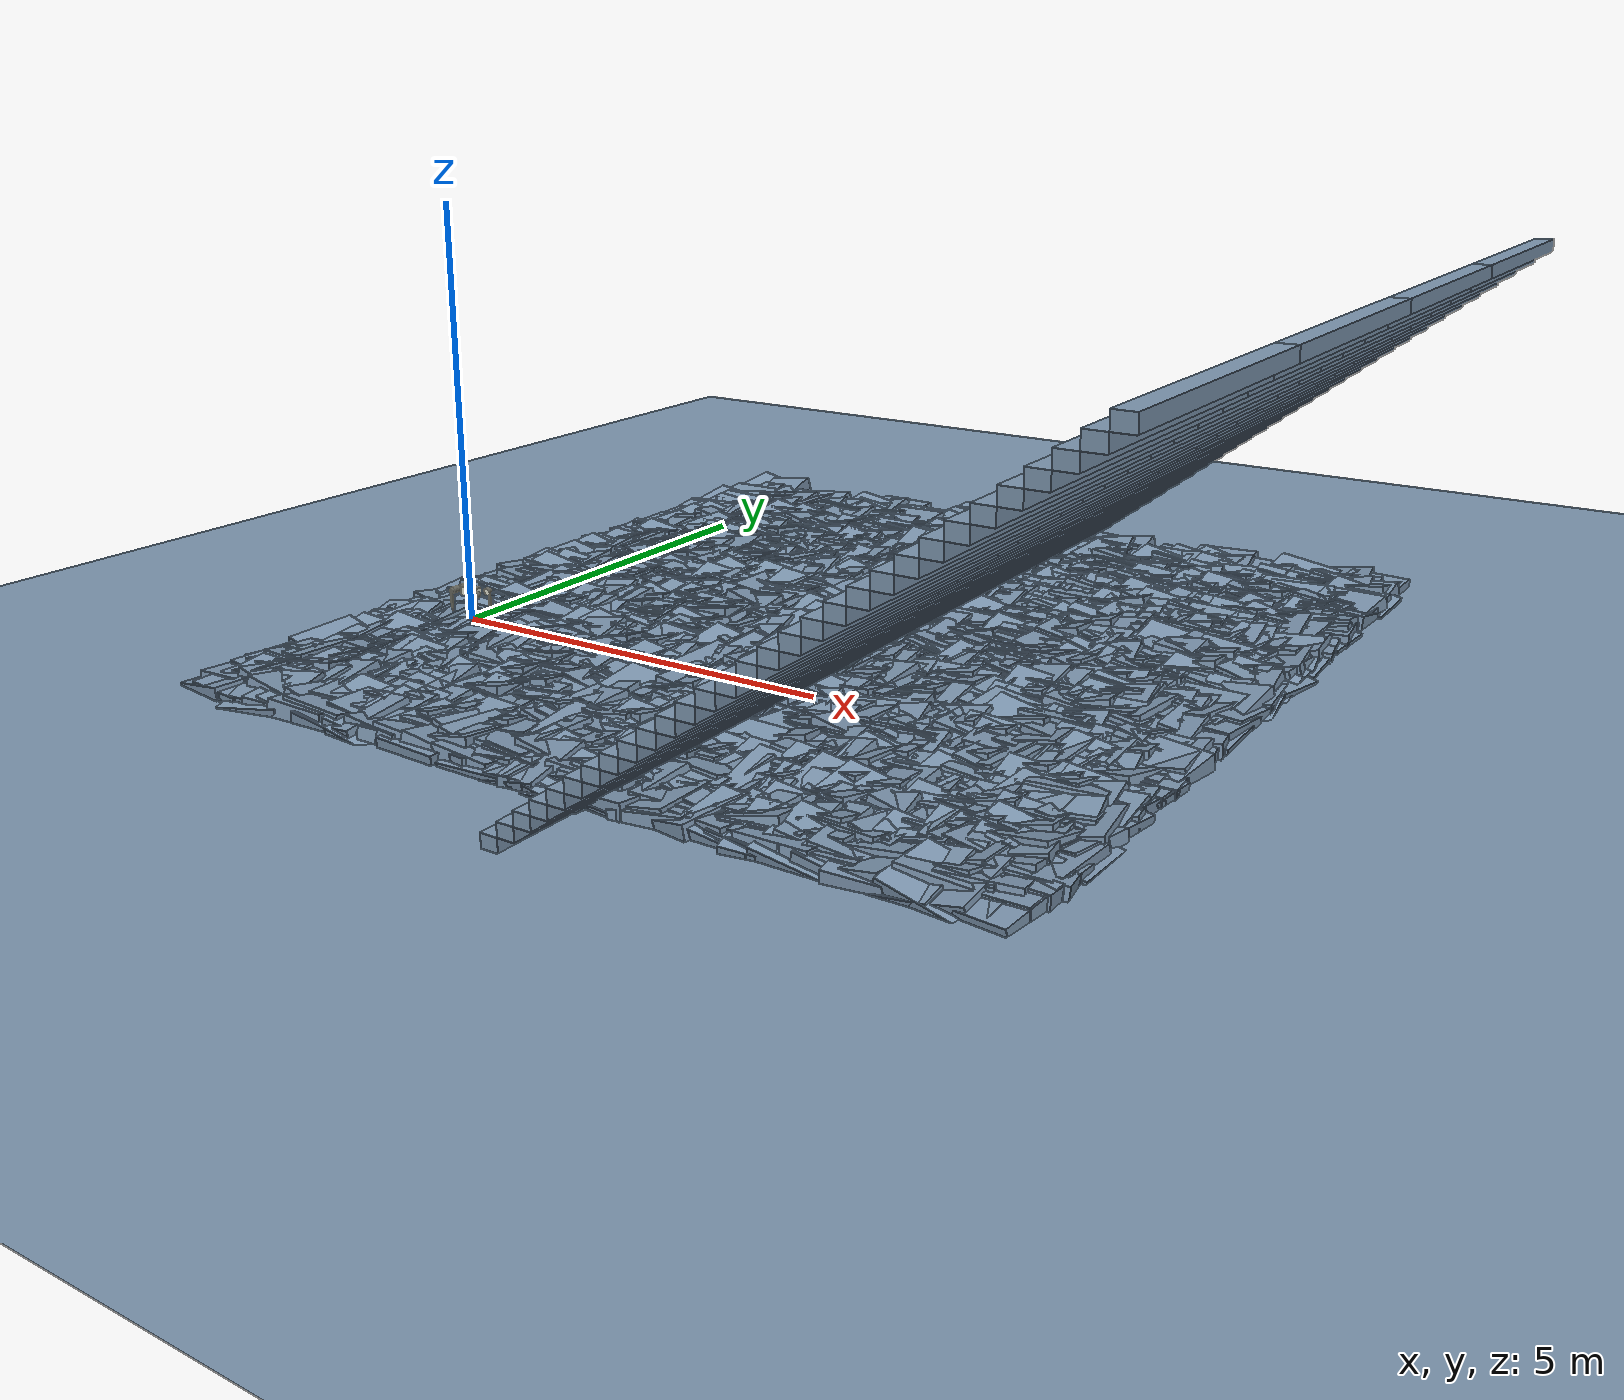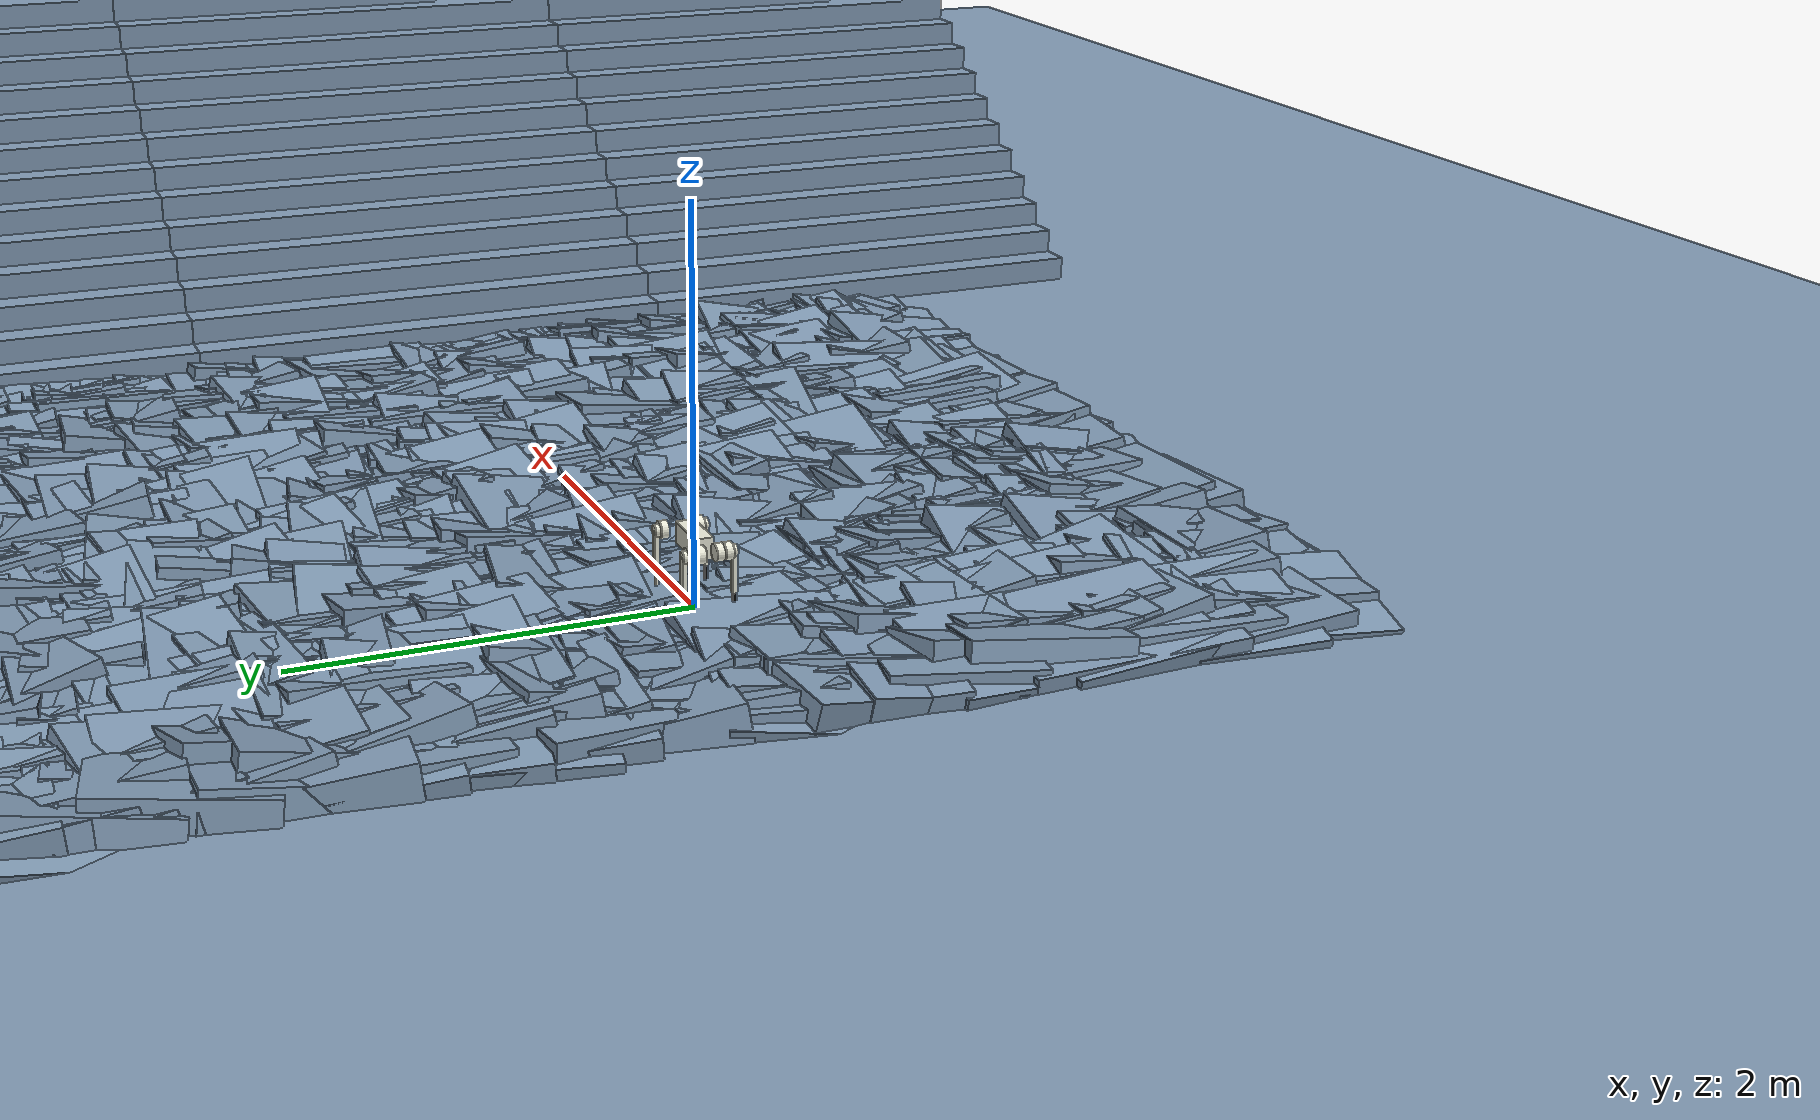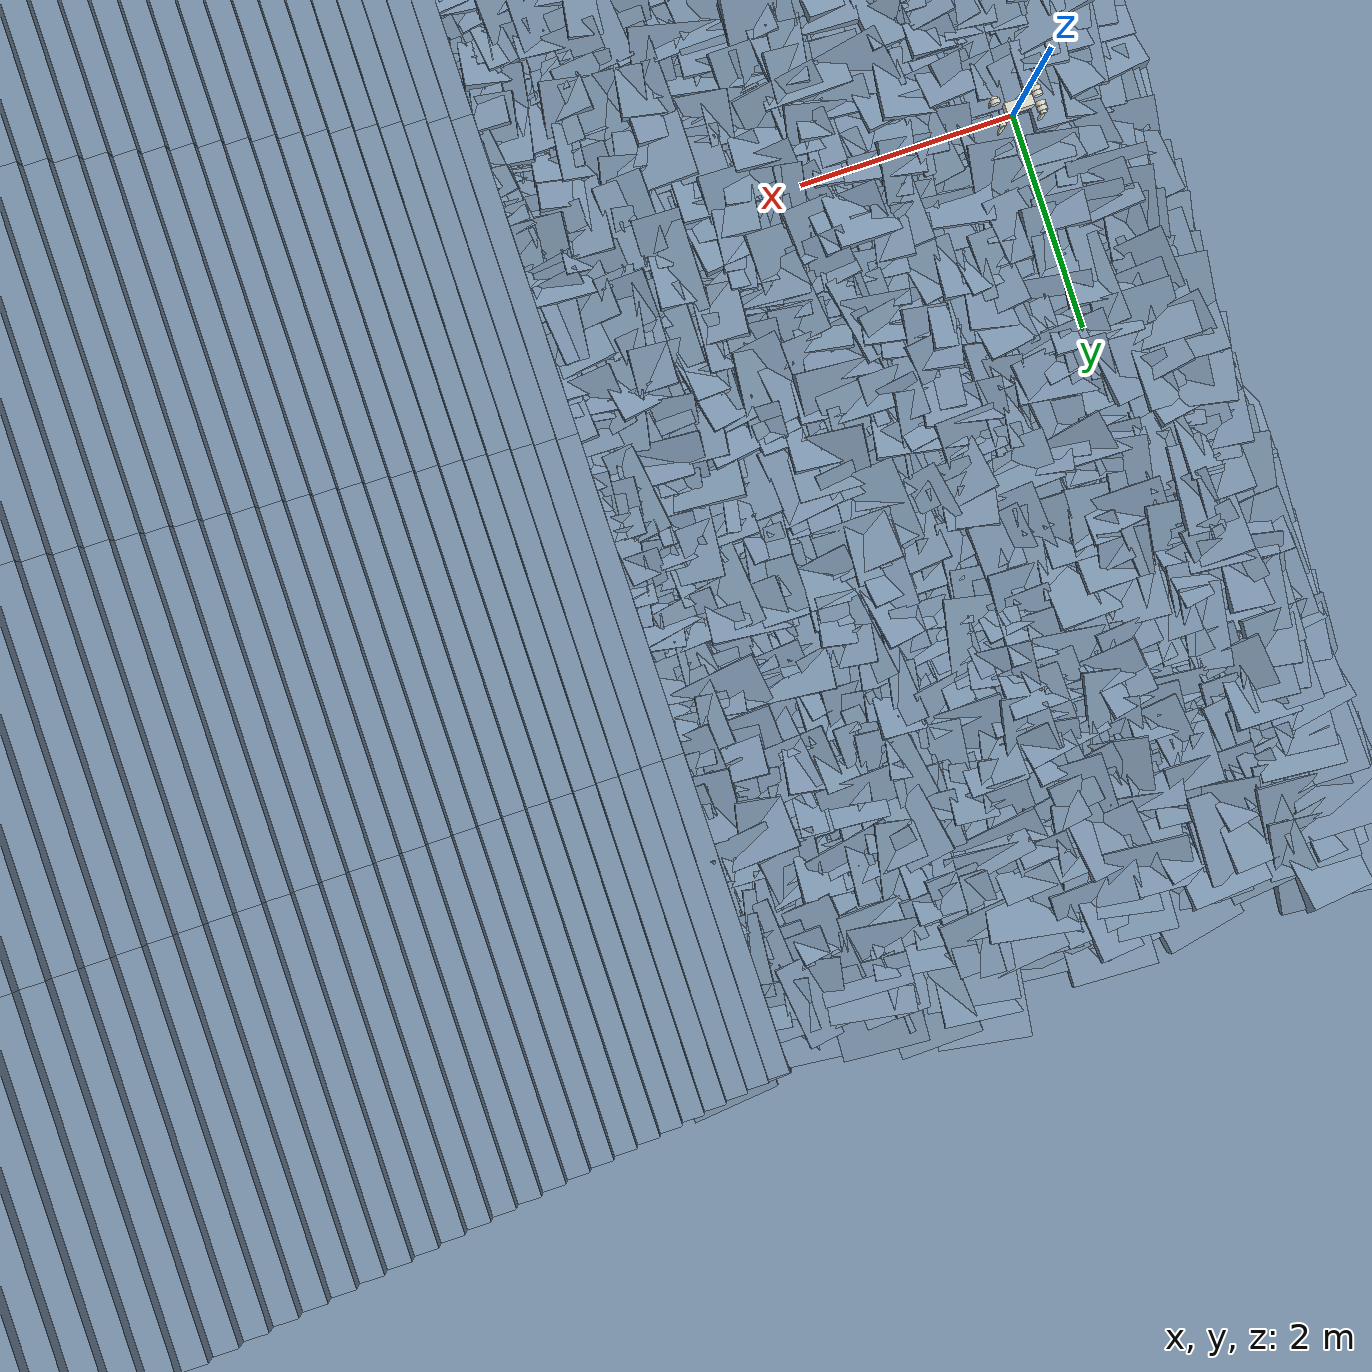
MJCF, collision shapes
<mujoco>
    <include file="scene_terrain.xml"/>
    <include file="dependencies.xml"/>

    <worldbody>
		<include file="go1_.xml" />
    </worldbody>

 	<actuator>
		<motor name="FL_hip_joint" joint="FL_hip_joint" gear="1"/>
		<motor name="FL_thigh_joint" joint="FL_thigh_joint" gear="1"/>
		<motor name="FL_calf_joint" joint="FL_calf_joint" gear="1"/>

		<motor name="FR_hip_joint" joint="FR_hip_joint" gear="1"/>
		<motor name="FR_thigh_joint" joint="FR_thigh_joint" gear="1"/>
		<motor name="FR_calf_joint" joint="FR_calf_joint" gear="1"/>

		<motor name="RL_hip_joint" joint="RL_hip_joint" gear="1"/>
		<motor name="RL_thigh_joint" joint="RL_thigh_joint" gear="1"/>
		<motor name="RL_calf_joint" joint="RL_calf_joint" gear="1"/>

		<motor name="RR_hip_joint" joint="RR_hip_joint" gear="1"/>
		<motor name="RR_thigh_joint" joint="RR_thigh_joint" gear="1"/>
		<motor name="RR_calf_joint" joint="RR_calf_joint" gear="1"/>
    </actuator>

    <sensor>
        <actuatorpos name='FL_hip_joint_p'  actuator='FL_hip_joint' user='13'/>
		<actuatorpos name='FL_thigh_joint_p'  actuator='FL_thigh_joint' user='13'/>
		<actuatorpos name='FL_calf_joint_p'  actuator='FL_calf_joint' user='13'/>

		<actuatorpos name='FR_hip_joint_p'  actuator='FR_hip_joint' user='13'/>
		<actuatorpos name='FR_thigh_joint_p'  actuator='FR_thigh_joint' user='13'/>
		<actuatorpos name='FR_calf_joint_p'  actuator='FR_calf_joint' user='13'/>

		<actuatorpos name='RL_hip_joint_p'  actuator='RL_hip_joint' user='13'/>
		<actuatorpos name='RL_thigh_joint_p'  actuator='RL_thigh_joint' user='13'/>
		<actuatorpos name='RL_calf_joint_p'  actuator='RL_calf_joint' user='13'/>

		<actuatorpos name='RR_hip_joint_p'  actuator='RR_hip_joint' user='13'/>
		<actuatorpos name='RR_thigh_joint_p'  actuator='RR_thigh_joint' user='13'/>
		<actuatorpos name='RR_calf_joint_p'  actuator='RR_calf_joint' user='13'/>

        <actuatorvel name='FL_hip_joint_v'  actuator='FL_hip_joint' user='13'/>
        <actuatorvel name='FL_thigh_joint_v'  actuator='FL_thigh_joint' user='13'/>
        <actuatorvel name='FL_calf_joint_v'  actuator='FL_calf_joint' user='13'/>

        <actuatorvel name='FR_hip_joint_v'  actuator='FR_hip_joint' user='13'/>
        <actuatorvel name='FR_thigh_joint_v'  actuator='FR_thigh_joint' user='13'/>
        <actuatorvel name='FR_calf_joint_v'  actuator='FR_calf_joint' user='13'/>

        <actuatorvel name='RL_hip_joint_v'  actuator='RL_hip_joint' user='13'/>
        <actuatorvel name='RL_thigh_joint_v'  actuator='RL_thigh_joint' user='13'/>
        <actuatorvel name='RL_calf_joint_v'  actuator='RL_calf_joint' user='13'/>

        <actuatorvel name='RR_hip_joint_v'  actuator='RR_hip_joint' user='13'/>
        <actuatorvel name='RR_thigh_joint_v'  actuator='RR_thigh_joint' user='13'/>
        <actuatorvel name='RR_calf_joint_v'  actuator='RR_calf_joint' user='13'/>

		<actuatorfrc name='FL_hip_joint_f'  actuator='FL_hip_joint'  user='13' noise='1e-3'/>
		<actuatorfrc name='FL_thigh_joint_f'  actuator='FL_thigh_joint'  user='13' noise='1e-3'/>
		<actuatorfrc name='FL_calf_joint_f'  actuator='FL_calf_joint'  user='13' noise='1e-3'/>

		<actuatorfrc name='FR_hip_joint_f'  actuator='FR_hip_joint'  user='13' noise='1e-3'/>
		<actuatorfrc name='FR_thigh_joint_f'  actuator='FR_thigh_joint'  user='13' noise='1e-3'/>
		<actuatorfrc name='FR_calf_joint_f'  actuator='FR_calf_joint'  user='13' noise='1e-3'/>

		<actuatorfrc name='RL_hip_joint_f'  actuator='RL_hip_joint'  user='13' noise='1e-3'/>
		<actuatorfrc name='RL_thigh_joint_f'  actuator='RL_thigh_joint'  user='13' noise='1e-3'/>
		<actuatorfrc name='RL_calf_joint_f'  actuator='RL_calf_joint'  user='13' noise='1e-3'/>

        <actuatorfrc name='RR_hip_joint_f'  actuator='RR_hip_joint'  user='13' noise='1e-3'/>
		<actuatorfrc name='RR_thigh_joint_f'  actuator='RR_thigh_joint'  user='13' noise='1e-3'/>
		<actuatorfrc name='RR_calf_joint_f'  actuator='RR_calf_joint'  user='13' noise='1e-3'/>

        <framequat     name='orientation' objtype='site' noise='0.001' objname='imu'/>
        <framepos      name='position' objtype='site' noise='0.001' objname='imu'/>
        <gyro          name='angular-velocity'    site='imu' noise='0.005'/>
        <velocimeter   name='linear-velocity'     site='imu' noise='0.001'/>
        <accelerometer name='linear-acceleration' site='imu' noise='0.005'/>
        <magnetometer  name='magnetometer'        site='imu'/>

    </sensor>
</mujoco>

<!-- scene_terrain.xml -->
<mujocoinclude>
    <size njmax="500" nconmax="100" />
    <option timestep="0.005" iterations="50" tolerance="1e-10" solver="Newton" jacobian="dense" cone="elliptic" gravity="0 0 -9.806" />

    <default>
        <geom contype="1" conaffinity="1" friction="0.6 0.3 0.3" rgba="0.5 0.6 0.7 1" margin="0.001" group="0" />
        <light castshadow="false" diffuse="1 1 1" />
        <motor ctrlrange="-33.5 33.5" ctrllimited="true" />

        <joint damping="0.01" armature="0.01" frictionloss="0.2" />
    </default>

    <asset>
        <texture type="skybox" builtin="gradient" rgb1=".3 .5 .7" rgb2="0 0 0" width="512" height="512" />
        <texture name="grid" type="2d" builtin="checker" width="512" height="512" rgb1=".1 .2 .3" rgb2=".2 .3 .4" />
        <material name="grid" texture="grid" texrepeat="1 1" texuniform="true" reflectance=".2" />
    </asset>

    <visual>
        <rgba com="0.502 1.0 0 0.5" contactforce="0.98 0.4 0.4 0.7" contactpoint="1.0 1.0 0.6 0.4" />
        <scale com="0.2" forcewidth="0.035" contactwidth="0.10" contactheight="0.04" />
        <map fogstart="1.5" fogend="5" force="0.1" znear="0.1" />
        <quality shadowsize="4096" offsamples="4" />
        <headlight ambient="0.4 0.4 0.4" />
    </visual>

    <worldbody>
        <geom name="floor" type="plane" conaffinity="1" condim="3" contype="1" material="grid" pos="0 0 -0.1" size="0 0 0.05" />
        <light castshadow="false" directional="true" diffuse=".3 .3 .3" specular="0.3 0.3 0.3" pos="-1 -1 1" dir="1 1 -1" />
        <light directional="true" diffuse=".3 .3 .3" specular="0.3 0.3 0.3" pos="1 -1 1" dir="-1 1 -1" />
        <light castshadow="false" directional="true" diffuse=".3 .3 .3" specular="0.3 0.3 0.3" pos="0 1 1" dir="0 -1 -1" />
    <geom pos="4.7 0.0 0.075" type="box" size="0.1 1.5 0.075" quat="1.0 0.0 0.0 0.0" /><geom pos="4.9 0.0 0.22499999999999998" type="box" size="0.1 1.5 0.075" quat="1.0 0.0 0.0 0.0" /><geom pos="5.1 0.0 0.375" type="box" size="0.1 1.5 0.075" quat="1.0 0.0 0.0 0.0" /><geom pos="5.3 0.0 0.525" type="box" size="0.1 1.5 0.075" quat="1.0 0.0 0.0 0.0" /><geom pos="5.5 0.0 0.675" type="box" size="0.1 1.5 0.075" quat="1.0 0.0 0.0 0.0" /><geom pos="5.7 0.0 0.8250000000000001" type="box" size="0.1 1.5 0.075" quat="1.0 0.0 0.0 0.0" /><geom pos="5.9 0.0 0.9750000000000001" type="box" size="0.1 1.5 0.075" quat="1.0 0.0 0.0 0.0" /><geom pos="6.1 0.0 1.125" type="box" size="0.1 1.5 0.075" quat="1.0 0.0 0.0 0.0" /><geom pos="6.3 0.0 1.275" type="box" size="0.1 1.5 0.075" quat="1.0 0.0 0.0 0.0" /><geom pos="6.5 0.0 1.4249999999999998" type="box" size="0.1 1.5 0.075" quat="1.0 0.0 0.0 0.0" /><geom pos="6.699999999999999 0.0 1.5749999999999997" type="box" size="0.1 1.5 0.075" quat="1.0 0.0 0.0 0.0" /><geom pos="6.9 0.0 1.7249999999999996" type="box" size="0.1 1.5 0.075" quat="1.0 0.0 0.0 0.0" /><geom pos="7.1 0.0 1.8749999999999996" type="box" size="0.1 1.5 0.075" quat="1.0 0.0 0.0 0.0" /><geom pos="7.300000000000001 0.0 2.0249999999999995" type="box" size="0.1 1.5 0.075" quat="1.0 0.0 0.0 0.0" /><geom pos="7.5 0.0 2.1749999999999994" type="box" size="0.1 1.5 0.075" quat="1.0 0.0 0.0 0.0" /><geom pos="7.700000000000001 0.0 2.3249999999999993" type="box" size="0.1 1.5 0.075" quat="1.0 0.0 0.0 0.0" /><geom pos="7.9 0.0 2.474999999999999" type="box" size="0.1 1.5 0.075" quat="1.0 0.0 0.0 0.0" /><geom pos="8.100000000000001 0.0 2.624999999999999" type="box" size="0.1 1.5 0.075" quat="1.0 0.0 0.0 0.0" /><geom pos="8.3 0.0 2.774999999999999" type="box" size="0.1 1.5 0.075" quat="1.0 0.0 0.0 0.0" /><geom pos="8.5 0.0 2.924999999999999" type="box" size="0.1 1.5 0.075" quat="1.0 0.0 0.0 0.0" /><geom pos="8.700000000000001 0.0 3.074999999999999" type="box" size="0.1 1.5 0.075" quat="1.0 0.0 0.0 0.0" /><geom pos="8.900000000000002 0.0 3.2249999999999988" type="box" size="0.1 1.5 0.075" quat="1.0 0.0 0.0 0.0" /><geom pos="9.100000000000001 0.0 3.3749999999999987" type="box" size="0.1 1.5 0.075" quat="1.0 0.0 0.0 0.0" /><geom pos="9.3 0.0 3.5249999999999986" type="box" size="0.1 1.5 0.075" quat="1.0 0.0 0.0 0.0" /><geom pos="9.500000000000002 0.0 3.6749999999999985" type="box" size="0.1 1.5 0.075" quat="1.0 0.0 0.0 0.0" /><geom pos="9.700000000000003 0.0 3.8249999999999984" type="box" size="0.1 1.5 0.075" quat="1.0 0.0 0.0 0.0" /><geom pos="9.900000000000002 0.0 3.9749999999999983" type="box" size="0.1 1.5 0.075" quat="1.0 0.0 0.0 0.0" /><geom pos="10.100000000000001 0.0 4.124999999999998" type="box" size="0.1 1.5 0.075" quat="1.0 0.0 0.0 0.0" /><geom pos="10.300000000000002 0.0 4.274999999999999" type="box" size="0.1 1.5 0.075" quat="1.0 0.0 0.0 0.0" /><geom pos="10.500000000000004 0.0 4.424999999999999" type="box" size="0.1 1.5 0.075" quat="1.0 0.0 0.0 0.0" /><geom pos="4.7 -3.0 0.075" type="box" size="0.1 1.5 0.075" quat="1.0 0.0 0.0 0.0" /><geom pos="4.9 -3.0 0.22499999999999998" type="box" size="0.1 1.5 0.075" quat="1.0 0.0 0.0 0.0" /><geom pos="5.1 -3.0 0.375" type="box" size="0.1 1.5 0.075" quat="1.0 0.0 0.0 0.0" /><geom pos="5.3 -3.0 0.525" type="box" size="0.1 1.5 0.075" quat="1.0 0.0 0.0 0.0" /><geom pos="5.5 -3.0 0.675" type="box" size="0.1 1.5 0.075" quat="1.0 0.0 0.0 0.0" /><geom pos="5.7 -3.0 0.8250000000000001" type="box" size="0.1 1.5 0.075" quat="1.0 0.0 0.0 0.0" /><geom pos="5.9 -3.0 0.9750000000000001" type="box" size="0.1 1.5 0.075" quat="1.0 0.0 0.0 0.0" /><geom pos="6.1 -3.0 1.125" type="box" size="0.1 1.5 0.075" quat="1.0 0.0 0.0 0.0" /><geom pos="6.3 -3.0 1.275" type="box" size="0.1 1.5 0.075" quat="1.0 0.0 0.0 0.0" /><geom pos="6.5 -3.0 1.4249999999999998" type="box" size="0.1 1.5 0.075" quat="1.0 0.0 0.0 0.0" /><geom pos="6.699999999999999 -3.0 1.5749999999999997" type="box" size="0.1 1.5 0.075" quat="1.0 0.0 0.0 0.0" /><geom pos="6.9 -3.0 1.7249999999999996" type="box" size="0.1 1.5 0.075" quat="1.0 0.0 0.0 0.0" /><geom pos="7.1 -3.0 1.8749999999999996" type="box" size="0.1 1.5 0.075" quat="1.0 0.0 0.0 0.0" /><geom pos="7.300000000000001 -3.0 2.0249999999999995" type="box" size="0.1 1.5 0.075" quat="1.0 0.0 0.0 0.0" /><geom pos="7.5 -3.0 2.1749999999999994" type="box" size="0.1 1.5 0.075" quat="1.0 0.0 0.0 0.0" /><geom pos="7.700000000000001 -3.0 2.3249999999999993" type="box" size="0.1 1.5 0.075" quat="1.0 0.0 0.0 0.0" /><geom pos="7.9 -3.0 2.474999999999999" type="box" size="0.1 1.5 0.075" quat="1.0 0.0 0.0 0.0" /><geom pos="8.100000000000001 -3.0 2.624999999999999" type="box" size="0.1 1.5 0.075" quat="1.0 0.0 0.0 0.0" /><geom pos="8.3 -3.0 2.774999999999999" type="box" size="0.1 1.5 0.075" quat="1.0 0.0 0.0 0.0" /><geom pos="8.5 -3.0 2.924999999999999" type="box" size="0.1 1.5 0.075" quat="1.0 0.0 0.0 0.0" /><geom pos="8.700000000000001 -3.0 3.074999999999999" type="box" size="0.1 1.5 0.075" quat="1.0 0.0 0.0 0.0" /><geom pos="8.900000000000002 -3.0 3.2249999999999988" type="box" size="0.1 1.5 0.075" quat="1.0 0.0 0.0 0.0" /><geom pos="9.100000000000001 -3.0 3.3749999999999987" type="box" size="0.1 1.5 0.075" quat="1.0 0.0 0.0 0.0" /><geom pos="9.3 -3.0 3.5249999999999986" type="box" size="0.1 1.5 0.075" quat="1.0 0.0 0.0 0.0" /><geom pos="9.500000000000002 -3.0 3.6749999999999985" type="box" size="0.1 1.5 0.075" quat="1.0 0.0 0.0 0.0" /><geom pos="9.700000000000003 -3.0 3.8249999999999984" type="box" size="0.1 1.5 0.075" quat="1.0 0.0 0.0 0.0" /><geom pos="9.900000000000002 -3.0 3.9749999999999983" type="box" size="0.1 1.5 0.075" quat="1.0 0.0 0.0 0.0" /><geom pos="10.100000000000001 -3.0 4.124999999999998" type="box" size="0.1 1.5 0.075" quat="1.0 0.0 0.0 0.0" /><geom pos="10.300000000000002 -3.0 4.274999999999999" type="box" size="0.1 1.5 0.075" quat="1.0 0.0 0.0 0.0" /><geom pos="10.500000000000004 -3.0 4.424999999999999" type="box" size="0.1 1.5 0.075" quat="1.0 0.0 0.0 0.0" /><geom pos="4.7 3.0 0.075" type="box" size="0.1 1.5 0.075" quat="1.0 0.0 0.0 0.0" /><geom pos="4.9 3.0 0.22499999999999998" type="box" size="0.1 1.5 0.075" quat="1.0 0.0 0.0 0.0" /><geom pos="5.1 3.0 0.375" type="box" size="0.1 1.5 0.075" quat="1.0 0.0 0.0 0.0" /><geom pos="5.3 3.0 0.525" type="box" size="0.1 1.5 0.075" quat="1.0 0.0 0.0 0.0" /><geom pos="5.5 3.0 0.675" type="box" size="0.1 1.5 0.075" quat="1.0 0.0 0.0 0.0" /><geom pos="5.7 3.0 0.8250000000000001" type="box" size="0.1 1.5 0.075" quat="1.0 0.0 0.0 0.0" /><geom pos="5.9 3.0 0.9750000000000001" type="box" size="0.1 1.5 0.075" quat="1.0 0.0 0.0 0.0" /><geom pos="6.1 3.0 1.125" type="box" size="0.1 1.5 0.075" quat="1.0 0.0 0.0 0.0" /><geom pos="6.3 3.0 1.275" type="box" size="0.1 1.5 0.075" quat="1.0 0.0 0.0 0.0" /><geom pos="6.5 3.0 1.4249999999999998" type="box" size="0.1 1.5 0.075" quat="1.0 0.0 0.0 0.0" /><geom pos="6.699999999999999 3.0 1.5749999999999997" type="box" size="0.1 1.5 0.075" quat="1.0 0.0 0.0 0.0" /><geom pos="6.9 3.0 1.7249999999999996" type="box" size="0.1 1.5 0.075" quat="1.0 0.0 0.0 0.0" /><geom pos="7.1 3.0 1.8749999999999996" type="box" size="0.1 1.5 0.075" quat="1.0 0.0 0.0 0.0" /><geom pos="7.300000000000001 3.0 2.0249999999999995" type="box" size="0.1 1.5 0.075" quat="1.0 0.0 0.0 0.0" /><geom pos="7.5 3.0 2.1749999999999994" type="box" size="0.1 1.5 0.075" quat="1.0 0.0 0.0 0.0" /><geom pos="7.700000000000001 3.0 2.3249999999999993" type="box" size="0.1 1.5 0.075" quat="1.0 0.0 0.0 0.0" /><geom pos="7.9 3.0 2.474999999999999" type="box" size="0.1 1.5 0.075" quat="1.0 0.0 0.0 0.0" /><geom pos="8.100000000000001 3.0 2.624999999999999" type="box" size="0.1 1.5 0.075" quat="1.0 0.0 0.0 0.0" /><geom pos="8.3 3.0 2.774999999999999" type="box" size="0.1 1.5 0.075" quat="1.0 0.0 0.0 0.0" /><geom pos="8.5 3.0 2.924999999999999" type="box" size="0.1 1.5 0.075" quat="1.0 0.0 0.0 0.0" /><geom pos="8.700000000000001 3.0 3.074999999999999" type="box" size="0.1 1.5 0.075" quat="1.0 0.0 0.0 0.0" /><geom pos="8.900000000000002 3.0 3.2249999999999988" type="box" size="0.1 1.5 0.075" quat="1.0 0.0 0.0 0.0" /><geom pos="9.100000000000001 3.0 3.3749999999999987" type="box" size="0.1 1.5 0.075" quat="1.0 0.0 0.0 0.0" /><geom pos="9.3 3.0 3.5249999999999986" type="box" size="0.1 1.5 0.075" quat="1.0 0.0 0.0 0.0" /><geom pos="9.500000000000002 3.0 3.6749999999999985" type="box" size="0.1 1.5 0.075" quat="1.0 0.0 0.0 0.0" /><geom pos="9.700000000000003 3.0 3.8249999999999984" type="box" size="0.1 1.5 0.075" quat="1.0 0.0 0.0 0.0" /><geom pos="9.900000000000002 3.0 3.9749999999999983" type="box" size="0.1 1.5 0.075" quat="1.0 0.0 0.0 0.0" /><geom pos="10.100000000000001 3.0 4.124999999999998" type="box" size="0.1 1.5 0.075" quat="1.0 0.0 0.0 0.0" /><geom pos="10.300000000000002 3.0 4.274999999999999" type="box" size="0.1 1.5 0.075" quat="1.0 0.0 0.0 0.0" /><geom pos="10.500000000000004 3.0 4.424999999999999" type="box" size="0.1 1.5 0.075" quat="1.0 0.0 0.0 0.0" /><geom pos="4.7 6.0 0.075" type="box" size="0.1 1.5 0.075" quat="1.0 0.0 0.0 0.0" /><geom pos="4.9 6.0 0.22499999999999998" type="box" size="0.1 1.5 0.075" quat="1.0 0.0 0.0 0.0" /><geom pos="5.1 6.0 0.375" type="box" size="0.1 1.5 0.075" quat="1.0 0.0 0.0 0.0" /><geom pos="5.3 6.0 0.525" type="box" size="0.1 1.5 0.075" quat="1.0 0.0 0.0 0.0" /><geom pos="5.5 6.0 0.675" type="box" size="0.1 1.5 0.075" quat="1.0 0.0 0.0 0.0" /><geom pos="5.7 6.0 0.8250000000000001" type="box" size="0.1 1.5 0.075" quat="1.0 0.0 0.0 0.0" /><geom pos="5.9 6.0 0.9750000000000001" type="box" size="0.1 1.5 0.075" quat="1.0 0.0 0.0 0.0" /><geom pos="6.1 6.0 1.125" type="box" size="0.1 1.5 0.075" quat="1.0 0.0 0.0 0.0" /><geom pos="6.3 6.0 1.275" type="box" size="0.1 1.5 0.075" quat="1.0 0.0 0.0 0.0" /><geom pos="6.5 6.0 1.4249999999999998" type="box" size="0.1 1.5 0.075" quat="1.0 0.0 0.0 0.0" /><geom pos="6.699999999999999 6.0 1.5749999999999997" type="box" size="0.1 1.5 0.075" quat="1.0 0.0 0.0 0.0" /><geom pos="6.9 6.0 1.7249999999999996" type="box" size="0.1 1.5 0.075" quat="1.0 0.0 0.0 0.0" /><geom pos="7.1 6.0 1.8749999999999996" type="box" size="0.1 1.5 0.075" quat="1.0 0.0 0.0 0.0" /><geom pos="7.300000000000001 6.0 2.0249999999999995" type="box" size="0.1 1.5 0.075" quat="1.0 0.0 0.0 0.0" /><geom pos="7.5 6.0 2.1749999999999994" type="box" size="0.1 1.5 0.075" quat="1.0 0.0 0.0 0.0" /><geom pos="7.700000000000001 6.0 2.3249999999999993" type="box" size="0.1 1.5 0.075" quat="1.0 0.0 0.0 0.0" /><geom pos="7.9 6.0 2.474999999999999" type="box" size="0.1 1.5 0.075" quat="1.0 0.0 0.0 0.0" /><geom pos="8.100000000000001 6.0 2.624999999999999" type="box" size="0.1 1.5 0.075" quat="1.0 0.0 0.0 0.0" /><geom pos="8.3 6.0 2.774999999999999" type="box" size="0.1 1.5 0.075" quat="1.0 0.0 0.0 0.0" /><geom pos="8.5 6.0 2.924999999999999" type="box" size="0.1 1.5 0.075" quat="1.0 0.0 0.0 0.0" /><geom pos="8.700000000000001 6.0 3.074999999999999" type="box" size="0.1 1.5 0.075" quat="1.0 0.0 0.0 0.0" /><geom pos="8.900000000000002 6.0 3.2249999999999988" type="box" size="0.1 1.5 0.075" quat="1.0 0.0 0.0 0.0" /><geom pos="9.100000000000001 6.0 3.3749999999999987" type="box" size="0.1 1.5 0.075" quat="1.0 0.0 0.0 0.0" /><geom pos="9.3 6.0 3.5249999999999986" type="box" size="0.1 1.5 0.075" quat="1.0 0.0 0.0 0.0" /><geom pos="9.500000000000002 6.0 3.6749999999999985" type="box" size="0.1 1.5 0.075" quat="1.0 0.0 0.0 0.0" /><geom pos="9.700000000000003 6.0 3.8249999999999984" type="box" size="0.1 1.5 0.075" quat="1.0 0.0 0.0 0.0" /><geom pos="9.900000000000002 6.0 3.9749999999999983" type="box" size="0.1 1.5 0.075" quat="1.0 0.0 0.0 0.0" /><geom pos="10.100000000000001 6.0 4.124999999999998" type="box" size="0.1 1.5 0.075" quat="1.0 0.0 0.0 0.0" /><geom pos="10.300000000000002 6.0 4.274999999999999" type="box" size="0.1 1.5 0.075" quat="1.0 0.0 0.0 0.0" /><geom pos="10.500000000000004 6.0 4.424999999999999" type="box" size="0.1 1.5 0.075" quat="1.0 0.0 0.0 0.0" /><geom pos="-0.8324572212540468 -2.7884920192393023 -0.4" type="box" size="0.38088025292253563 0.40015442839120663 0.38712126126436147" quat="0.9937878220385898 0.008102442611277228 -0.08134960432613955 -0.07551395280017922" /><geom pos="-0.8324572212540468 -2.5569672033156503 -0.4" type="box" size="0.4011512178220178 0.3859469417822683 0.39220801347229206" quat="0.9993412845064734 -0.03348518359144099 -0.010183481801132923 0.009593553002172663" /><geom pos="-0.8324572212540468 -2.3890488932339995 -0.4" type="box" size="0.40605168299547034 0.3834721240917912 0.40778188082261263" quat="0.9938562724508655 -0.02202883750301252 -0.09821910787957851 -0.04601572422201676" /><geom pos="-0.8324572212540468 -2.1557533381189256 -0.4" type="box" size="0.3759734684290912 0.41873302128992423 0.3887780055593685" quat="0.9986600989171905 -0.0019875708592905186 0.04067107545244385 -0.03193618659652668" /><geom pos="-0.8324572212540468 -1.9608353139327805 -0.4" type="box" size="0.4088799037892822 0.3926642603505817 0.40094971219958264" quat="0.9982782642885343 -0.03338508131933258 -0.03856256528977105 -0.028963286288765988" /><geom pos="-0.8324572212540468 -1.7956653407942516 -0.4" type="box" size="0.40434242801671944 0.42169563286113493 0.4243883585361236" quat="0.9961380919506749 -0.026616269489609993 -0.07940477947133451 0.026369621924365837" /><geom pos="-0.8324572212540468 -1.5518211900257783 -0.4" type="box" size="0.4053337005491919 0.41151123159947156 0.3993028649949567" quat="0.9986189999151058 0.0026519280650705705 -0.04203613990404284 0.03140100680008907" /><geom pos="-0.8324572212540468 -1.3402070906096486 -0.4" type="box" size="0.4020771989170727 0.40971559886521286 0.4206502113384429" quat="0.9924027252528205 0.04579723601103109 0.09089944835248948 -0.06911392315400924" /><geom pos="-0.8324572212540468 -1.134084112822571 -0.4" type="box" size="0.3879734900555873 0.39934030772635654 0.4090269149602267" quat="0.9936063788761025 0.030795811388493504 -0.09741019938399954 0.048054499410698386" /><geom pos="-0.8324572212540468 -0.8994600900039762 -0.4" type="box" size="0.38226969611009887 0.38689435125526406 0.41424496398814" quat="0.9967532383409144 0.034851445682027964 0.0037912740346475672 -0.07248437646808371" /><geom pos="-0.8324572212540468 -0.6981943442061858 -0.4" type="box" size="0.4157972642469107 0.38703944730152573 0.4067523359305893" quat="0.9957848691454545 0.07243903083003583 -0.05504795778341508 -0.01161049254987562" /><geom pos="-0.8324572212540468 -0.4823279120941746 -0.4" type="box" size="0.40259517558182334 0.4230974364100401 0.39929000126826886" quat="0.9972890195752465 -0.0167533580784373 -0.04110666358307875 -0.0586871249662711" /><geom pos="-0.8324572212540468 -0.3210279294980998 -0.4" type="box" size="0.40029660407935286 0.3846599002290139 0.42212684661014477" quat="0.9912706560551173 0.09763270802056083 -0.04332119169102808 0.07728916559970322" /><geom pos="-0.8324572212540468 -0.11934772291660334 -0.4" type="box" size="0.41963107161020763 0.4194941754590401 0.3849480076325281" quat="0.9908363634401308 0.06355286235874208 -0.09230636829040816 -0.0753914381331396" /><geom pos="-0.8324572212540468 0.089110548390122 -0.4" type="box" size="0.3812398626976579 0.4020349711394868 0.3767282367696621" quat="0.9958885021855153 -0.007715851844391397 0.0892954403920639 -0.013148428430567648" /><geom pos="-0.8324572212540468 0.3335536722072452 -0.4" type="box" size="0.3839813017101628 0.4007744002534114 0.391983110269146" quat="0.9989085347966828 0.03217357559086034 0.019795525270700755 -0.027472483020301204" /><geom pos="-0.8324572212540468 0.5168532123900209 -0.4" type="box" size="0.4193403901402112 0.3989321250202466 0.3795606697889598" quat="0.9937981205802634 -0.0701070830460776 0.058019196594259775 -0.06390669185979822" /><geom pos="-0.8324572212540468 0.7641193422778949 -0.4" type="box" size="0.4063078308789888 0.40397343159554033 0.41375904142803055" quat="0.9978498096293948 0.014774639591153504 0.026864821064501623 0.05792882561129993" /><geom pos="-0.8324572212540468 0.9444748379818182 -0.4" type="box" size="0.39474463366528234 0.37842478250130657 0.39632978180294903" quat="0.9976851590124937 -0.0302531219391662 -0.021909569552514285 -0.056824667717221264" /><geom pos="-0.8324572212540468 1.1770263461594466 -0.4" type="box" size="0.40866903747107686 0.4061121643887816 0.4050976812521382" quat="0.9956898188785236 0.008145270320720696 -0.06335263514800915 -0.06724494607670059" /><geom pos="-0.8324572212540468 1.395524703894183 -0.4" type="box" size="0.38701670231133856 0.3753783267209842 0.3902128453872045" quat="0.9942580350709569 -0.0351339116810179 -0.03502578966718394 -0.09481435547964305" /><geom pos="-0.8324572212540468 1.64152052563142 -0.4" type="box" size="0.3810161860532967 0.39498363695815014 0.3855997461380611" quat="0.9991810084527765 -0.0012632417106426877 0.04039439041322444 -0.002002446208306094" /><geom pos="-0.8324572212540468 1.8200034350675498 -0.4" type="box" size="0.38148856873032183 0.4027942986270079 0.3834184936135446" quat="0.9967148158292631 -0.04948960699777905 -0.04240274361718252 -0.04808702568654874" /><geom pos="-0.8324572212540468 2.027950760099232 -0.4" type="box" size="0.40829969365776553 0.4201582206901804 0.40735898799635784" quat="0.9969034487957646 -0.04967162315476287 0.026643346590523156 -0.05483042690640576" /><geom pos="-0.8324572212540468 2.2283576391353543 -0.4" type="box" size="0.42385464869104156 0.4149047091556189 0.37819511931448346" quat="0.995425317758275 0.07060676543276015 0.06296416534648569 -0.013365452599167328" /><geom pos="-0.8324572212540468 2.3998223308920617 -0.4" type="box" size="0.38098532127943296 0.4033947638992957 0.38121464565349755" quat="0.9903926778243444 -0.0668709331714102 0.09165917132851405 0.07905199757171816" /><geom pos="-0.8324572212540468 2.637112115895701 -0.4" type="box" size="0.38994909952295476 0.40981900805547705 0.42034574943660746" quat="0.9927395183749887 0.054726093138195014 0.038977479607118046 -0.09977003292523169" /><geom pos="-0.8324572212540468 2.813121224563969 -0.4" type="box" size="0.3862135038467968 0.41451626442410155 0.3762277924025725" quat="0.993557844892 -0.020878449305432922 0.08399200198645528 0.0731590241219235" /><geom pos="-0.8324572212540468 3.0619832170647845 -0.4" type="box" size="0.40837639885960486 0.41165561063399725 0.3843455254866366" quat="0.9917590731068942 0.07772192089763288 0.07685704112774662 -0.06682992706283704" /><geom pos="-0.8324572212540468 3.2824748975240414 -0.4" type="box" size="0.42470675975732697 0.39741157804695937 0.39740054963036164" quat="0.9934570724332237 0.05523932597293823 -0.0984954803213637 -0.01703826442828501" /><geom pos="-0.8324572212540468 3.472811662056337 -0.4" type="box" size="0.38009608906681036 0.3881167252996712 0.40804767906002354" quat="0.998935819292527 -0.041349447051541095 -0.0005433420334746765 -0.020424420244758042" /><geom pos="-0.8324572212540468 3.7167501085192125 -0.4" type="box" size="0.4093964328236278 0.41841534384876095 0.39895368320464447" quat="0.9956357507482467 -0.04511772442306273 0.00889280298538561 -0.08120813278190288" /><geom pos="-0.8324572212540468 3.9447381696943955 -0.4" type="box" size="0.41069774101659323 0.4056377261952748 0.40977401587488765" quat="0.994661511527407 -0.032333531205060426 -0.09648819797841152 -0.017118641789124527" /><geom pos="-0.8324572212540468 4.146156054372266 -0.4" type="box" size="0.3816035269606507 0.40043379872664353 0.3755120855523785" quat="0.9957699844529346 0.07181893151634983 0.055088067418397564 0.015795061461049274" /><geom pos="-0.8324572212540468 4.313696962922016 -0.4" type="box" size="0.4138742378384236 0.41452287444444774 0.3967926332147415" quat="0.9986714412168018 -0.037768616364410014 0.021506643744464562 0.027682998224948196" /><geom pos="-0.8324572212540468 4.526048478434603 -0.4" type="box" size="0.4049582536881127 0.41988201440880957 0.40230455260012987" quat="0.9941556870107148 0.05903525595986444 -0.07520020727797345 -0.050142171506196716" /><geom pos="-0.8324572212540468 4.689276963832973 -0.4" type="box" size="0.4002809592092148 0.4163412614789909 0.3866177538534235" quat="0.999235512357638 0.00426653965528249 0.037061125080739096 0.01169018778670145" /><geom pos="-0.8324572212540468 4.865992162379933 -0.4" type="box" size="0.3750697058954299 0.38389103978397293 0.38781468934408414" quat="0.9964860522923822 0.0487468148248737 -0.034261320003362 0.05886813724588674" /><geom pos="-0.8324572212540468 5.097007208020555 -0.4" type="box" size="0.41623350121063085 0.4097493033038387 0.3970274768793176" quat="0.9962443115892313 0.0429447006641042 -0.00853726603988801 -0.07470033065209936" /><geom pos="-0.8324572212540468 5.283680549528102 -0.4" type="box" size="0.40886305057043665 0.41439146297488094 0.3940412221847402" quat="0.9922181049454695 -0.09015618308268279 -0.08577617207842742 0.004188457228516823" /><geom pos="-0.8324572212540468 5.478855999244761 -0.4" type="box" size="0.4044089203507047 0.3882728286578287 0.3906985624062367" quat="0.9967871944985801 0.07346019257301871 0.029643754799162907 0.011837938680013156" /><geom pos="-0.8324572212540468 5.654313328254721 -0.4" type="box" size="0.4021673360305382 0.4017088396102227 0.387003864675428" quat="0.9922771905440287 0.07702235752837641 0.016880163636801008 0.09575277354946472" /><geom pos="-0.8324572212540468 5.841661201305774 -0.4" type="box" size="0.37569267727165073 0.4084198194348021 0.41216478048771893" quat="0.9985752467250493 0.033018384488354945 -0.03228513112951473 0.026738235202355735" /><geom pos="-0.8324572212540468 6.0332370564647455 -0.4" type="box" size="0.39496052347520066 0.4239306180825597 0.4014651943491077" quat="0.9974238784611666 -0.02157404509306619 -0.010834598588853318 0.06754834363050358" /><geom pos="-0.8324572212540468 6.216616996055873 -0.4" type="box" size="0.41762393914248364 0.3969874269656335 0.4152107224686598" quat="0.994755967774532 0.07126703356973367 0.073355594133212 -0.0007289118520233777" /><geom pos="-0.8324572212540468 6.452261350604141 -0.4" type="box" size="0.3881407846781706 0.4200449631043211 0.41648122141843225" quat="0.998908583129476 0.017470560796423396 -0.022665295136642723 -0.03691485408464238" /><geom pos="-0.8324572212540468 6.658010745586628 -0.4" type="box" size="0.40732366552616517 0.4204825175692334 0.40958465858627635" quat="0.9983830122833386 0.05546757504560547 -0.006951590929063953 -0.01031427584283822" /><geom pos="-0.8324572212540468 6.860325353297121 -0.4" type="box" size="0.419205428865704 0.3940848255160072 0.3831944971454641" quat="0.9943133186885331 0.0787307070394416 -0.0628526794832948 0.0345259428464349" /><geom pos="-0.8324572212540468 7.08522664555603 -0.4" type="box" size="0.38604272134293466 0.39653930155192524 0.38032299540391207" quat="0.9948831204159914 -0.022180974768636227 -0.030352995961519677 -0.09377780497438103" /><geom pos="-0.8324572212540468 7.244519978275399 -0.4" type="box" size="0.41032266636815284 0.41213818985334194 0.3978320087727504" quat="0.9913489616638442 0.08407643878644884 0.0900086531581774 -0.04535229879132024" /><geom pos="-0.6447076989136217 -2.7851397275154097 -0.4" type="box" size="0.3818154938201449 0.4064630216659334 0.4019576539523433" quat="0.9985906759468643 0.021924357715844226 0.014046945582938402 -0.046245732457405986" /><geom pos="-0.6447076989136217 -2.6136122464873237 -0.4" type="box" size="0.38221510822774446 0.42097453667052376 0.38225345251058346" quat="0.9966025890595667 0.06603658057249522 0.0485733532365334 -0.007942220182036473" /><geom pos="-0.6447076989136217 -2.370667934281574 -0.4" type="box" size="0.41586824946765455 0.39974978001601225 0.3782706788100649" quat="0.9922554091771166 0.016577418505054856 -0.08682592015541234 -0.08726770160619002" /><geom pos="-0.6447076989136217 -2.161199198355055 -0.4" type="box" size="0.3932532409431372 0.3798985477308378 0.4071940594735536" quat="0.9950856546195518 -0.05391487680469945 -0.014812697922953923 -0.08172092761193707" /><geom pos="-0.6447076989136217 -1.9203217358552025 -0.4" type="box" size="0.40717670411468626 0.3923799931490665 0.41008644091327817" quat="0.9948362074753463 -0.08648517054456004 0.034618391226408994 0.04028402364267581" /><geom pos="-0.6447076989136217 -1.6795703792802965 -0.4" type="box" size="0.3833285610568342 0.378826953414106 0.39216458907590834" quat="0.9950063178564216 -0.09675735472569197 0.02361081748841859 0.006555229196678799" /><geom pos="-0.6447076989136217 -1.5134347017575753 -0.4" type="box" size="0.40172544913738784 0.394371697810258 0.3916797316131718" quat="0.9982278800618779 -0.03657017579710014 0.04686823329113868 0.002662783788813981" /><geom pos="-0.6447076989136217 -1.2728471983208474 -0.4" type="box" size="0.3821334337694732 0.40671019235232897 0.41108233280381634" quat="0.9941542776122775 0.0463788431106927 -0.05743039239268349 -0.07879102262660888" /><geom pos="-0.6447076989136217 -1.0320198454346465 -0.4" type="box" size="0.4185878654293384 0.4073857068031233 0.3891409243467767" quat="0.9886315521067423 0.08143005287702965 0.0949595215790712 0.0834235573979667" /><geom pos="-0.6447076989136217 -0.795118164073561 -0.4" type="box" size="0.41817394214943693 0.3983808385011012 0.38543013919778885" quat="0.997310140116141 -0.02764254140867627 -0.04525844366248203 0.0505969129813533" /><geom pos="-0.6447076989136217 -0.5777743968700113 -0.4" type="box" size="0.39404974992748565 0.40954120062171606 0.3779802901351022" quat="0.9978156120037915 0.038288515929103824 0.053386203355582695 -0.006921508558248331" /><geom pos="-0.6447076989136217 -0.3967739152437231 -0.4" type="box" size="0.37867439519446555 0.39371996883826016 0.4020200181419321" quat="0.992963437551677 0.04962709886085836 0.087249831310991 -0.0628349399650775" /><geom pos="-0.6447076989136217 -0.1983866562570551 -0.4" type="box" size="0.4147038399819266 0.41345511493973236 0.4055778854970421" quat="0.9970016139539267 0.04595248532863128 0.007801331724911057 -0.06176803452195141" /><geom pos="-0.6447076989136217 0.049998822510698204 -0.4" type="box" size="0.39950129918501026 0.3995896777309278 0.3984404870442412" quat="0.994498338247013 -0.04515748167936084 -0.04953305450685406 -0.08050051915068165" /><geom pos="-0.6447076989136217 0.24402314430725625 -0.4" type="box" size="0.38920644959205186 0.39700014587726173 0.4042864550282059" quat="0.9955749384842599 0.03480632978230845 0.009321628571527758 -0.08678806663315894" /><geom pos="-0.6447076989136217 0.48361039575518916 -0.4" type="box" size="0.41942537105007766 0.3865700986399307 0.42196144901541904" quat="0.9944523816559434 0.05928469819356034 -0.0028376127541095957 -0.08684315248065327" /><geom pos="-0.6447076989136217 0.7201365755033797 -0.4" type="box" size="0.3891916488525652 0.4140624853727856 0.38251181901131864" quat="0.9956508902874653 0.0720839307041654 0.0517055449913157 0.02845607529448989" /><geom pos="-0.6447076989136217 0.8797385539173925 -0.4" type="box" size="0.37641489741718664 0.3826379890427895 0.40938993444791255" quat="0.9950433250536163 -0.09417598681581583 -0.007266211193094459 -0.03109448421196503" /><geom pos="-0.6447076989136217 1.0934913898743153 -0.4" type="box" size="0.3943911831137631 0.4138896267937376 0.4178176454549228" quat="0.989941626598473 -0.07786710800529745 0.07674950789410041 -0.08978754065277827" /><geom pos="-0.6447076989136217 1.3039225866152924 -0.4" type="box" size="0.3955445536131814 0.39982284895793174 0.41114600284644115" quat="0.9925468224162268 -0.09026982218756437 0.024070648452853196 -0.07824812072334997" /><geom pos="-0.6447076989136217 1.499235564416857 -0.4" type="box" size="0.3799224004076748 0.3826665772733685 0.40459025613234306" quat="0.9982821153854297 0.038160195609140246 -0.010894008953105386 -0.043103806578928976" /><geom pos="-0.6447076989136217 1.7233265294947788 -0.4" type="box" size="0.39256804179850613 0.4002951384401866 0.412896700075613" quat="0.9915544853035226 -0.08764948807567038 0.08071000079891662 0.051216849625665736" /><geom pos="-0.6447076989136217 1.8748409151187841 -0.4" type="box" size="0.4045379777706154 0.39429417684006196 0.3958188302710414" quat="0.9939743786121673 0.04090039580692423 -0.01777357833490542 0.10013087535103955" /><geom pos="-0.6447076989136217 2.0666599762583964 -0.4" type="box" size="0.42248431104143397 0.38136863294112855 0.3997037978272655" quat="0.9928876371629213 0.08780358956802677 0.07694418460827726 -0.02332942526013382" /><geom pos="-0.6447076989136217 2.29183865211046 -0.4" type="box" size="0.3843098440468044 0.4031928129196741 0.3872248469222379" quat="0.9937708109681452 -0.05426235307215868 0.007721961757611943 0.09703372410353793" /><geom pos="-0.6447076989136217 2.5392525404365713 -0.4" type="box" size="0.3950387499613765 0.41810758200801584 0.3927669221447149" quat="0.9941215504078001 0.044538257673954335 -0.09853305206826442 -0.005470307877346634" /><geom pos="-0.6447076989136217 2.715738764367657 -0.4" type="box" size="0.39193462840499615 0.3828052392317346 0.3849322725805445" quat="0.9869932321469218 0.10166819155355025 -0.07805468816670838 0.09703300560943644" /><geom pos="-0.6447076989136217 2.90393136920697 -0.4" type="box" size="0.37706829426656885 0.38849829691625004 0.38621245131818416" quat="0.9928276628887975 -0.053591824942467906 0.09772690920593442 -0.04325042565292243" /><geom pos="-0.6447076989136217 3.1515179712240347 -0.4" type="box" size="0.42205584127259416 0.3824870419008286 0.4089265935877321" quat="0.9958323489363422 0.04357594679368302 0.024592769980541523 -0.07625133007132127" /><geom pos="-0.6447076989136217 3.3610151840950406 -0.4" type="box" size="0.40925967341357056 0.4054369438695721 0.3935232029765926" quat="0.9982384950092422 -0.03831162572303766 0.04465365309880089 0.007627429519361375" /><geom pos="-0.6447076989136217 3.531332199392943 -0.4" type="box" size="0.40163795242971995 0.3811463575592876 0.4218173896936514" quat="0.9968273038090716 0.06528136011714665 0.044690847261118424 0.008740627727783137" /><geom pos="-0.6447076989136217 3.7215351540019634 -0.4" type="box" size="0.40763565934007073 0.4101496066241477 0.4223420372108859" quat="0.9938296017828694 0.019789526775233587 -0.09985486955495447 -0.04404659210743489" /><geom pos="-0.6447076989136217 3.9150078857372552 -0.4" type="box" size="0.399370985025405 0.39115896430648506 0.3872508600391917" quat="0.9955960034478473 0.010073594613310328 -0.08412679107076237 0.040122358285339305" /><geom pos="-0.6447076989136217 4.127585955739127 -0.4" type="box" size="0.4132899226776183 0.38638678828949247 0.4125411771813629" quat="0.9960134938985119 0.07888250822390408 -0.007024582305654815 -0.04105271138202542" /><geom pos="-0.6447076989136217 4.307653563382098 -0.4" type="box" size="0.41307640105103643 0.4075492813808551 0.40605426145312223" quat="0.9924166256769876 -0.08291584903041813 -0.05660479078299762 0.07092320297250945" /><geom pos="-0.6447076989136217 4.539950288048517 -0.4" type="box" size="0.40718265921683516 0.40511818681432044 0.411831042482961" quat="0.9912913405450486 -0.08626525138221093 0.0043003585317541015 -0.09940468540699018" /><geom pos="-0.6447076989136217 4.723179346081052 -0.4" type="box" size="0.4165929810920768 0.3993101486161858 0.38918628344886574" quat="0.9923817176724617 0.033585583664002654 0.0921293558119558 -0.07458362284762558" /><geom pos="-0.6447076989136217 4.8976089219488435 -0.4" type="box" size="0.4151230324133107 0.4100435198416798 0.4078571307090689" quat="0.9981667831296371 0.04527241952996691 0.03088360531813839 -0.025684314456265553" /><geom pos="-0.6447076989136217 5.089382783573219 -0.4" type="box" size="0.3831693270952763 0.4041243869537877 0.4074997859997011" quat="0.9905062863071017 0.08711790931027057 0.06353216544114686 -0.08527268389044623" /><geom pos="-0.6447076989136217 5.322508597410442 -0.4" type="box" size="0.39813857885148 0.3817884164607135 0.40229065215143206" quat="0.9902676901628499 0.07427776235937206 0.06179198388702647 -0.10017218459095342" /><geom pos="-0.6447076989136217 5.481622765747364 -0.4" type="box" size="0.39363640971959063 0.3856599910108649 0.41363779582024657" quat="0.9982573948995852 0.039873888983993376 0.043497672597451 -0.00044607644039902877" /><geom pos="-0.6447076989136217 5.697652797783814 -0.4" type="box" size="0.41216553125704125 0.41691240786511663 0.387971410343622" quat="0.9924305585502868 -0.03192288953484156 -0.09127302041181948 -0.0757083306130539" /><geom pos="-0.6447076989136217 5.915482718577913 -0.4" type="box" size="0.40249444959023994 0.38520119507483264 0.41131052106071087" quat="0.9952933450484873 0.07843273600047915 0.0290110071048829 -0.04896758818271894" /><geom pos="-0.6447076989136217 6.087934839722568 -0.4" type="box" size="0.3878557375967878 0.4131412156940003 0.4245022455888018" quat="0.9946752305523826 0.09547575076780732 -0.002395764899136661 -0.03872760064135399" /><geom pos="-0.6447076989136217 6.238910819498413 -0.4" type="box" size="0.3936109160185037 0.37682530391217994 0.3937755239490651" quat="0.9929903885399071 0.07920181945820705 0.0032356962483890716 0.08767377219934246" /><geom pos="-0.6447076989136217 6.480844035508193 -0.4" type="box" size="0.39614844430510615 0.3982011797618543 0.40178588000284887" quat="0.9949691015447302 -0.06099808407042053 0.019037923279195613 0.07715748951479509" /><geom pos="-0.6447076989136217 6.643206700779503 -0.4" type="box" size="0.398727986147924 0.39948148848358145 0.3769774846180893" quat="0.9951756659057324 -0.016016269251405573 -0.09256890402626371 0.02828199278207226" /><geom pos="-0.6447076989136217 6.811623638199508 -0.4" type="box" size="0.4035509148749887 0.377828876120303 0.3909163888143658" quat="0.9948144354722407 -0.06814089564206971 0.0022932466087512175 0.07547051303081857" /><geom pos="-0.6447076989136217 7.054385075485616 -0.4" type="box" size="0.3810872340993338 0.38064139728199825 0.410959164410545" quat="0.9944890392118032 -0.0384939611125956 -0.048279049101846265 0.08472838522755088" /><geom pos="-0.6447076989136217 7.250710165213134 -0.4" type="box" size="0.4230230106692865 0.4050071244921484 0.4248301780776768" quat="0.9923421967569014 0.09959275971706373 -0.0427056811862463 0.059282978518670065" /><geom pos="-0.481164013091286 -2.7552000599975828 -0.4" type="box" size="0.3959908875609333 0.4115449942167896 0.4134159150402176" quat="0.9974986408797615 0.052150365148052574 -0.03615473387480453 -0.031138980015330997" /><geom pos="-0.481164013091286 -2.5700189050185527 -0.4" type="box" size="0.4036742581982543 0.4128570045087673 0.4078245926104751" quat="0.9974698202439136 0.03634510290847713 -0.04661735749511408 0.03949447021190765" /><geom pos="-0.481164013091286 -2.404039308887824 -0.4" type="box" size="0.3906578625920677 0.37536627240971443 0.39885842548374406" quat="0.9898956560821581 0.08135454350118851 -0.09727025627548756 -0.06345490970356812" /><geom pos="-0.481164013091286 -2.1791132087762275 -0.4" type="box" size="0.40657228979847837 0.4133864709520069 0.40996280683587405" quat="0.9989018442419219 0.023789885556803888 -0.023947239653929454 0.03249117769854741" /><geom pos="-0.481164013091286 -2.0045593674788074 -0.4" type="box" size="0.39091361332877944 0.41391127406759565 0.3770767758931326" quat="0.9973850135687223 0.060112951613863645 0.03999187470632545 0.0031965159568802387" /><geom pos="-0.481164013091286 -1.7579302638658956 -0.4" type="box" size="0.3955243729400424 0.4220473373573054 0.41027094019174026" quat="0.9976110440967124 -0.04162874506840312 0.049807352498163045 0.023632179701013972" /><geom pos="-0.481164013091286 -1.6027655777314243 -0.4" type="box" size="0.40859150591680404 0.40554889925980375 0.40614628256387664" quat="0.9946281973432298 -0.02700498825244719 -0.09730710799644862 0.022733376181505543" /><geom pos="-0.481164013091286 -1.391776832153274 -0.4" type="box" size="0.4072874418576737 0.4109479436977598 0.3994364275825574" quat="0.9965227463942227 0.04312510676622747 0.06990918453054826 0.013976659242859514" /><geom pos="-0.481164013091286 -1.1588279943777704 -0.4" type="box" size="0.37968630592587294 0.4101204979527416 0.37573273253731776" quat="0.9946655978451908 0.010601580945138743 -0.03818919988799602 0.09523413230899691" /><geom pos="-0.481164013091286 -0.943262596050849 -0.4" type="box" size="0.3899802172534903 0.4248190370847711 0.41108369450566035" quat="0.9957691353892983 -0.07060604749524307 -0.01281835991647435 0.057396033941383394" /><geom pos="-0.481164013091286 -0.7537779611730095 -0.4" type="box" size="0.424479572298844 0.4171540936155719 0.40937955950919064" quat="0.9941805853652361 -0.04805584151387209 -0.038009594191159374 0.08860513827455802" /><geom pos="-0.481164013091286 -0.5452306898373527 -0.4" type="box" size="0.3935827923250945 0.4085088175724102 0.38056736302841787" quat="0.9992111785976635 0.015700062986987524 0.004065598638961347 0.03624913096033466" /><geom pos="-0.481164013091286 -0.3228456837233682 -0.4" type="box" size="0.4062115042664332 0.424750755002985 0.4146989941290185" quat="0.9957160537804023 0.04341723377352592 0.04830462437342936 -0.0658114527994934" /><geom pos="-0.481164013091286 -0.16846582454967107 -0.4" type="box" size="0.41461596148398927 0.41953093038713285 0.42455756081388124" quat="0.9950960374370067 0.039633120491411974 -0.09035856219754766 -0.006958611562107392" /><geom pos="-0.481164013091286 -0.017440160262892856 -0.4" type="box" size="0.37694540596333453 0.3866508281299342 0.4010089104418159" quat="0.9971787172851163 -0.028602319669080153 0.05969841277730492 -0.035392267729382754" /><geom pos="-0.481164013091286 0.1735535297136579 -0.4" type="box" size="0.3815395596972799 0.3946003792431357 0.39019819531818445" quat="0.9974015096635137 0.0006973464532639962 0.05063160181144276 -0.05124629866512816" /><geom pos="-0.481164013091286 0.38702646875348456 -0.4" type="box" size="0.39771907400642514 0.41632196875151983 0.40630948127126126" quat="0.9920314682654773 -0.06133357264824125 0.0551999949295835 0.09520881995392061" /><geom pos="-0.481164013091286 0.5590208780549708 -0.4" type="box" size="0.40681070315140266 0.41312917610719413 0.38257436873717676" quat="0.9936372321642237 0.08181082315372093 0.0625316826523915 -0.045627061450326634" /><geom pos="-0.481164013091286 0.8086141827349635 -0.4" type="box" size="0.4226209478109991 0.3967947754626222 0.4096054918232663" quat="0.994050180571369 0.08429657266419328 0.062067501704743545 0.030099029473234513" /><geom pos="-0.481164013091286 1.0346747052048144 -0.4" type="box" size="0.42101206873133756 0.3981576934787859 0.4095060752586292" quat="0.9940410190460715 -0.050802157717583174 0.09500135588680518 0.016623345173411738" /><geom pos="-0.481164013091286 1.1974352722256238 -0.4" type="box" size="0.39559996271404274 0.41432328267081525 0.4156178467139296" quat="0.9998033885106791 -0.01659271010542709 -0.008792112598092414 0.006369069789524822" /><geom pos="-0.481164013091286 1.4279836818229557 -0.4" type="box" size="0.41539667154802573 0.424091992425178 0.41471470390867293" quat="0.9980134203876575 0.0056734221154005424 -0.06198893856287756 -0.009715786302575935" /><geom pos="-0.481164013091286 1.5875505766165086 -0.4" type="box" size="0.4189183492764142 0.41020115297343085 0.38312313316154345" quat="0.9978128741145132 -0.05838631422736723 0.006240285663512774 0.030357295615976526" /><geom pos="-0.481164013091286 1.7930190820385166 -0.4" type="box" size="0.3932601130230267 0.4035874464871561 0.38020400682498523" quat="0.9939851779367617 -0.0607594566224528 0.08761119775265142 0.02502064150485448" /><geom pos="-0.481164013091286 1.9490848463804182 -0.4" type="box" size="0.41649746136630855 0.37746759834784216 0.3959352656254214" quat="0.9953694217151662 -0.08673598288868938 0.027051094494023358 0.03138187173231968" /><geom pos="-0.481164013091286 2.1353000827972917 -0.4" type="box" size="0.3780022743882859 0.3917321835365323 0.4244777682142572" quat="0.9972564998960731 -0.07285971964930864 -0.012553537208379548 -0.003652857951694328" /><geom pos="-0.481164013091286 2.3249374285515128 -0.4" type="box" size="0.4054286426040716 0.40542020912061627 0.38976806191047836" quat="0.9873571983934127 0.08930418952956136 0.10601816652806466 0.07688090061391577" /><geom pos="-0.481164013091286 2.5355278217038686 -0.4" type="box" size="0.3812125619981572 0.42392154611508337 0.416321734242114" quat="0.9971933523483507 -0.009225956074841125 -0.07329954041253736 0.012144016719106338" /><geom pos="-0.481164013091286 2.780297072756656 -0.4" type="box" size="0.3857998905783096 0.3822777394545453 0.3844883537880855" quat="0.9938210597003162 0.06305073424413793 0.025376261291223272 -0.08775164710873094" /><geom pos="-0.481164013091286 3.023111881618717 -0.4" type="box" size="0.3954567789442367 0.3842247776701052 0.3791679779124536" quat="0.9995052801210251 0.01063826661623969 0.014089170272622069 -0.0260291677665963" /><geom pos="-0.481164013091286 3.2636992568690433 -0.4" type="box" size="0.42383741208995845 0.379541079296012 0.41570191089519615" quat="0.997218787571679 0.00813801142676566 -0.07035010139230548 -0.023223387310656665" /><geom pos="-0.481164013091286 3.512051879827043 -0.4" type="box" size="0.38531638221984865 0.4069383264825308 0.4060507280342565" quat="0.9947387422853011 -0.040037769717679854 -0.005594115427602765 -0.09413032171024295" /><geom pos="-0.481164013091286 3.67873462193414 -0.4" type="box" size="0.4174371036482943 0.4136349150321977 0.4007942698196524" quat="0.9982118393475912 -0.00037905680686715855 0.0026382137590166476 0.059716161383647395" /><geom pos="-0.481164013091286 3.8679353201008437 -0.4" type="box" size="0.4055820707433193 0.38143536916402004 0.40683768910322554" quat="0.9941777275800058 -0.045769296799201 0.008897545399881999 0.09714242708631224" /><geom pos="-0.481164013091286 4.073376439618193 -0.4" type="box" size="0.41045428233725684 0.3870415712607558 0.42277396353808727" quat="0.9923066250551842 0.09036874316575165 0.08458792855752341 0.002436077293502652" /><geom pos="-0.481164013091286 4.297792898333015 -0.4" type="box" size="0.4131299346526504 0.38571835813594796 0.414445229898163" quat="0.9920374783636181 -0.02621669620282921 0.08523734721115353 0.08893211457380112" /><geom pos="-0.481164013091286 4.503021033277842 -0.4" type="box" size="0.4186886135806389 0.4089847456491957 0.3754969327891046" quat="0.9964252555529239 -0.04764358462158613 -0.004761371812499804 -0.06959977212002383" /><geom pos="-0.481164013091286 4.726485179782414 -0.4" type="box" size="0.3761861374943318 0.3802543595458663 0.3872135436813153" quat="0.9948281829949238 0.0978230534687493 -0.0024614925825179094 -0.027230085995732366" /><geom pos="-0.481164013091286 4.97531327253039 -0.4" type="box" size="0.397771175337582 0.3823605342402012 0.4082952850134027" quat="0.9933335902061751 0.05756693089660775 -0.018585438001702863 -0.09812751158335213" /><geom pos="-0.481164013091286 5.150827315035743 -0.4" type="box" size="0.39863332260230167 0.377622749283779 0.38740228538682325" quat="0.9926861204370885 0.042718181041866636 0.05314479441290437 -0.09962456588034142" /><geom pos="-0.481164013091286 5.339665184421353 -0.4" type="box" size="0.42307494015441427 0.4189115471622882 0.40161273551898763" quat="0.9932294390570066 0.07198775500677038 0.08197126717042776 -0.03992187217633576" /><geom pos="-0.481164013091286 5.555508641260092 -0.4" type="box" size="0.3915042080282968 0.40163484435441105 0.4145376476584901" quat="0.9914014117086536 0.0880037374851097 -0.0965358992076439 -0.007707348111522025" /><geom pos="-0.481164013091286 5.782050598114559 -0.4" type="box" size="0.3952000209129539 0.3872867544187894 0.3905285118523981" quat="0.9973140737664421 -0.04269090628326413 -0.05150701885344121 0.02981864847589087" /><geom pos="-0.481164013091286 6.003897610052224 -0.4" type="box" size="0.4192774451067208 0.3853996178004311 0.3927222321182048" quat="0.9951560083524563 -0.06566751597936542 -0.07171623731197045 0.014459519041752758" /><geom pos="-0.481164013091286 6.220549925989051 -0.4" type="box" size="0.42307126710651255 0.37939882607192765 0.393740758783661" quat="0.9981056306415279 -0.046715611870497706 -0.017664767335959723 0.03592711628018035" /><geom pos="-0.481164013091286 6.417783717807524 -0.4" type="box" size="0.3994863594405111 0.4040129343553729 0.4222103294646967" quat="0.995791464485112 -0.02135816540462994 -0.05282541184958509 0.07178205828802968" /><geom pos="-0.481164013091286 6.598136276125258 -0.4" type="box" size="0.4163538540433006 0.38103464798445474 0.3952112464545408" quat="0.9937572670971533 -0.04951754795584954 -0.08700176353749134 -0.04924631638411038" /><geom pos="-0.481164013091286 6.773486671486264 -0.4" type="box" size="0.4196418285218224 0.4155511059012642 0.3996757461657526" quat="0.9922102003245067 -0.09984830668963214 -0.0645211304891047 -0.03723248237256464" /><geom pos="-0.481164013091286 6.925049404739417 -0.4" type="box" size="0.4201492906146979 0.385843719892821 0.4134282035781194" quat="0.9985557910315023 0.049927559892039806 0.017977668519210052 -0.00838894482583974" /><geom pos="-0.481164013091286 7.140492839849154 -0.4" type="box" size="0.42226955839696767 0.42344070702227404 0.3819427513158793" quat="0.9923570900310491 -0.09366974769688202 -0.059211717731682004 -0.05428956358983304" /><geom pos="-0.31543166593537086 -2.7623777079048653 -0.4" type="box" size="0.4153131693205947 0.38759116400316435 0.38876388768442016" quat="0.994101617066572 0.09277777782492495 -0.041160657065187324 0.03821072097537339" /><geom pos="-0.31543166593537086 -2.54300113072369 -0.4" type="box" size="0.4165851042762379 0.3884538119855209 0.4203442041690532" quat="0.9927593958781731 -0.0610611883522728 0.061906588456761405 -0.0828727185402906" /><geom pos="-0.31543166593537086 -2.318365624027161 -0.4" type="box" size="0.4109481256161148 0.3763615094472252 0.3908402309685932" quat="0.9939581501880632 0.04156659608295687 -0.028809561693524388 0.09741366906049125" /><geom pos="-0.31543166593537086 -2.120314174463283 -0.4" type="box" size="0.4071953421560341 0.4180269046716433 0.3770239931948692" quat="0.9970918570558214 0.055724198304504875 0.048826528374523295 0.017849718294285114" /><geom pos="-0.31543166593537086 -1.9541805353649926 -0.4" type="box" size="0.41527426504098053 0.423841135044126 0.4214136578549055" quat="0.9925473070636798 -0.09612507495872033 -0.05970858913849859 0.045218332431745036" /><geom pos="-0.31543166593537086 -1.7947109238314956 -0.4" type="box" size="0.3750513024089886 0.4046409506684633 0.4189481063895022" quat="0.9946334615767468 0.021190617928030953 -0.07460971215629852 -0.06847353996720604" /><geom pos="-0.31543166593537086 -1.6339155479236107 -0.4" type="box" size="0.38444270328473784 0.39458433658885406 0.3922148695948686" quat="0.9956728445841813 0.04852488167258485 -0.07394749271037253 0.028507731199725755" /><geom pos="-0.31543166593537086 -1.4024485453244075 -0.4" type="box" size="0.37985656075383195 0.40684387712123943 0.41788134241930186" quat="0.9951154500785576 -0.02889976439753158 -0.09208901435192683 0.020728195010846537" /><geom pos="-0.31543166593537086 -1.1713251195601755 -0.4" type="box" size="0.40541662779308796 0.38074626251053423 0.3887227216736643" quat="0.9934869623482022 0.02080613862414541 -0.06062894251745425 0.09420664291285416" /><geom pos="-0.31543166593537086 -1.0005749875433585 -0.4" type="box" size="0.38588592967665486 0.3981860140426514 0.38221130208939125" quat="0.9949945443607814 0.030874071365157803 0.03142881543333849 0.08969324372591987" /><geom pos="-0.31543166593537086 -0.8014597196261102 -0.4" type="box" size="0.4091106104817325 0.38539825983753917 0.4019891502687497" quat="0.9877746866585068 0.09104724857124438 0.10676625729482389 0.06791563316019425" /><geom pos="-0.31543166593537086 -0.6418913162052258 -0.4" type="box" size="0.3899913980839368 0.3788949424987318 0.4179050269266891" quat="0.9935843632246151 0.08343774288126422 0.042780952469420555 -0.06323010615383784" /><geom pos="-0.31543166593537086 -0.49094588044184206 -0.4" type="box" size="0.3895437521361438 0.4203741330680292 0.3760188540455624" quat="0.9969406136696612 0.03318595488432987 0.053414350712364264 0.0464221105977657" /><geom pos="-0.31543166593537086 -0.3333933425258806 -0.4" type="box" size="0.40742238495279526 0.4051068973225067 0.418684352079886" quat="0.997182977718494 0.051065708382830144 -0.01221211985833709 -0.05356553466925247" /><geom pos="-0.31543166593537086 -0.17396996670993303 -0.4" type="box" size="0.3990467460984151 0.40640229788576143 0.4192183015428347" quat="0.994091995151059 -0.031177347659118077 -0.0540897327170859 0.08878839442249051" /><geom pos="-0.31543166593537086 -0.01593447730505737 -0.4" type="box" size="0.3906600291838243 0.383787066745103 0.38009109633911653" quat="0.9967703477459001 -0.031772125038729865 -0.01503848685125644 0.07220283815935145" /><geom pos="-0.31543166593537086 0.17936164168304192 -0.4" type="box" size="0.4024204616419598 0.42249488032570004 0.4120679288571336" quat="0.9986804833588964 0.04076331955636135 0.02010063646742336 0.02390833223776281" /><geom pos="-0.31543166593537086 0.36714465653710393 -0.4" type="box" size="0.4249402829107176 0.3897630959391157 0.41614742025896856" quat="0.9985062157006587 -0.05363404112729655 0.0012356084048003864 -0.010353748662938388" /><geom pos="-0.31543166593537086 0.5629538163489278 -0.4" type="box" size="0.3844358634860293 0.4003231162800043 0.37815453270631694" quat="0.9962686795759481 -0.04686391117073496 -0.003194328427932143 -0.07240364764065903" /><geom pos="-0.31543166593537086 0.7362595697611574 -0.4" type="box" size="0.38949450324813195 0.38891624770881666 0.37510306170255686" quat="0.9974487521362694 0.05231791519762354 -0.03943270457151221 -0.02835285561189771" /><geom pos="-0.31543166593537086 0.926897240725804 -0.4" type="box" size="0.3905619547106323 0.3803474177943895 0.3929161674673095" quat="0.9957572101795753 -0.06461751693592555 -0.01408141858317926 -0.06398334573238536" /><geom pos="-0.31543166593537086 1.1379488900308807 -0.4" type="box" size="0.4172309733096795 0.4122033410188334 0.40902159146705785" quat="0.9941381010865824 -0.09471739148104394 0.028618558403428432 -0.043577859446057333" /><geom pos="-0.31543166593537086 1.360228223022597 -0.4" type="box" size="0.4222234586182832 0.3928515369121909 0.41621084863499347" quat="0.9966467369002012 -0.02415010884773167 -0.011615141987545888 0.07731198190082271" /><geom pos="-0.31543166593537086 1.540380086997847 -0.4" type="box" size="0.39734449174722575 0.3845658431028756 0.41139705940200755" quat="0.9928372278760833 0.09341254132851182 -0.05260154684290536 -0.052739106321750454" /><geom pos="-0.31543166593537086 1.7446102951716727 -0.4" type="box" size="0.38167088976805386 0.4045644464087821 0.3907091941090289" quat="0.995354823982926 -0.018505404157093133 0.09094323654747823 0.02560570477784871" /><geom pos="-0.31543166593537086 1.9366669382168444 -0.4" type="box" size="0.3907704220069871 0.3911116500663027 0.39481619732106477" quat="0.9992053296337435 0.0011426593128283293 -0.005124668753984344 -0.03951128106476278" /><geom pos="-0.31543166593537086 2.166910970794695 -0.4" type="box" size="0.37512940488915625 0.38235790338548975 0.4145884930013843" quat="0.9966288053248914 0.017767472992855013 -0.035305444380716255 -0.07189483220098769" /><geom pos="-0.31543166593537086 2.364067451399836 -0.4" type="box" size="0.37901029552497983 0.3979731145061315 0.4228972346744607" quat="0.9933634817808381 0.024533082484564043 -0.09092889716235998 0.06602315191577132" /><geom pos="-0.31543166593537086 2.5615771251686024 -0.4" type="box" size="0.3843295836114858 0.3903638553455492 0.3789141860711162" quat="0.9948633584066854 -0.03691487776140358 -0.09423457832261503 -0.002008518854998028" /><geom pos="-0.31543166593537086 2.757008428338194 -0.4" type="box" size="0.3859550658643039 0.38142191493782784 0.38140229656918484" quat="0.9951668529102908 -0.05429307956346224 0.07865913187282436 0.022537465544217844" /><geom pos="-0.31543166593537086 2.9681449986026642 -0.4" type="box" size="0.41281275405959406 0.4134129027534488 0.412448993457577" quat="0.9989998347910215 -0.0012941249621591514 0.02472472008074665 -0.03723363459323473" /><geom pos="-0.31543166593537086 3.1721634877727087 -0.4" type="box" size="0.3751355450695656 0.42324742382021846 0.3824814856946308" quat="0.9958467603000387 -0.05973135155712104 -0.019955479527535534 -0.06575085153747458" /><geom pos="-0.31543166593537086 3.360575768732163 -0.4" type="box" size="0.37663639063166915 0.38524120483315527 0.41460260314608816" quat="0.9947366121641904 -0.014954939130675245 0.04744455102785321 0.0895792207683911" /><geom pos="-0.31543166593537086 3.566192502368052 -0.4" type="box" size="0.4067021281065974 0.3802447068672629 0.39842932852918844" quat="0.9952104200553069 0.0025723301229442783 0.08106130692896238 -0.054577169677864495" /><geom pos="-0.31543166593537086 3.750811940478746 -0.4" type="box" size="0.38068443374404765 0.38518118478078106 0.4207716684550246" quat="0.998543940711133 0.03204009428802328 0.03747447210676796 -0.02188823353802879" /><geom pos="-0.31543166593537086 3.916160378458436 -0.4" type="box" size="0.418748737666559 0.42273713789912365 0.3926399072866771" quat="0.9924193449025297 -0.08245657746246011 0.08221776840573296 0.03930642765238736" /><geom pos="-0.31543166593537086 4.076005669761429 -0.4" type="box" size="0.40123593241682265 0.39634541216134134 0.3997994915814683" quat="0.9932981886108452 -0.07937422096029764 -0.06153804410762871 -0.057197121227970465" /><geom pos="-0.31543166593537086 4.274015029904325 -0.4" type="box" size="0.3854419910532455 0.41916907503420936 0.4014686279646535" quat="0.9908737143586653 0.06494479986017421 -0.0817047544580812 0.08529823130128995" /><geom pos="-0.31543166593537086 4.471740685191939 -0.4" type="box" size="0.396572666820269 0.3890049692122585 0.4196611532142532" quat="0.995267803880598 -0.040785497435821494 0.039225570415713826 0.07899301477451105" /><geom pos="-0.31543166593537086 4.669262209472509 -0.4" type="box" size="0.3905888981878395 0.38261312157049315 0.41890255328727066" quat="0.9964977545281307 -0.026802824863278566 -0.05638749370323805 -0.05562629192755038" /><geom pos="-0.31543166593537086 4.901005510316148 -0.4" type="box" size="0.3830546417475013 0.38143728952395767 0.41588486417623927" quat="0.9938531966702788 -0.0349638826905007 -0.07398780827451568 -0.07455973848000456" /><geom pos="-0.31543166593537086 5.0980602436309645 -0.4" type="box" size="0.3914086057975074 0.41765047666514216 0.4193830068986637" quat="0.9979395348492682 0.02765078744133191 0.009569711573723574 -0.05710113273041189" /><geom pos="-0.31543166593537086 5.255121884607789 -0.4" type="box" size="0.38993971662177707 0.41669901632686995 0.3988781632435192" quat="0.9934809030481888 0.021654944658052462 -0.08413100417894637 0.07381553214773973" /><geom pos="-0.31543166593537086 5.4889085533917985 -0.4" type="box" size="0.4187012942361787 0.42164989259555036 0.4199165560002226" quat="0.9900833723852326 -0.08417699096640041 0.09316391964647555 0.0630050314993366" /><geom pos="-0.31543166593537086 5.688483023424476 -0.4" type="box" size="0.3864954964949907 0.39175919884545146 0.393723683309586" quat="0.9946863175532727 -0.08769143424814999 -0.05393792800141841 -0.00020482852820451376" /><geom pos="-0.31543166593537086 5.9297332334788475 -0.4" type="box" size="0.4042964965158194 0.4139489880539997 0.42198410058884195" quat="0.9953330425448789 -0.023733963482797726 -0.06976889343993324 0.062298755235707506" /><geom pos="-0.31543166593537086 6.126644057035708 -0.4" type="box" size="0.3880813757295115 0.4210293027749605 0.3979524849936145" quat="0.9945599782383701 -0.000990760387399611 -0.08930910970953385 0.05360364729417359" /><geom pos="-0.31543166593537086 6.309564110872367 -0.4" type="box" size="0.376286961666728 0.4013545556032625 0.3785186730194386" quat="0.9967350938872198 -0.04631940372799035 0.06527697428230365 0.010610470322566642" /><geom pos="-0.31543166593537086 6.475984801813567 -0.4" type="box" size="0.41656684336092675 0.40221646634535296 0.3960933828223483" quat="0.9977231605097711 -0.04912717778608817 -0.039975137326723025 -0.02317334203081884" /><geom pos="-0.31543166593537086 6.676738361349047 -0.4" type="box" size="0.3787004026619214 0.37998742738980223 0.3757960759665297" quat="0.9959646487469497 0.05268882360483488 0.0005309316600332521 -0.07265001324897345" /><geom pos="-0.07629517784488216 -2.8229546294459213 -0.4" type="box" size="0.3888556913214411 0.42141244741565653 0.4122493979603891" quat="0.9907311408078441 0.09013994673072591 -0.04281774371381574 0.09215876225420797" /><geom pos="-0.07629517784488216 -2.6175693247682017 -0.4" type="box" size="0.37704253930731574 0.40878259266867545 0.41239538303100515" quat="0.9943458664016718 -0.07248557479742537 0.0727561170709961 -0.026994200209429657" /><geom pos="-0.07629517784488216 -2.428244978494077 -0.4" type="box" size="0.41721768804557513 0.3807785326275851 0.40258636939965564" quat="0.9947569056377517 0.07676201777502845 -0.06736273768399176 0.005343489948461503" /><geom pos="-0.07629517784488216 -2.182738073244928 -0.4" type="box" size="0.40110722171029745 0.41978192743339515 0.412840198608936" quat="0.9947476341522872 0.04581127272038443 0.08453699813346388 -0.03509939581743505" /><geom pos="-0.07629517784488216 -2.0180510272234917 -0.4" type="box" size="0.38096728081328407 0.41097213895862983 0.41879930961615564" quat="0.9987721046565596 -0.004872291653151753 0.04848921208120835 0.00890730294177024" /><geom pos="-0.07629517784488216 -1.8669152949894479 -0.4" type="box" size="0.4018775361818153 0.3956241938019874 0.4238903448899042" quat="0.9977061120406572 -0.03449161922231763 -0.013182612353481105 -0.05673676878071364" /><geom pos="-0.07629517784488216 -1.638499119684118 -0.4" type="box" size="0.4076684958526921 0.4203889122912366 0.37893358956116396" quat="0.9957104672647541 0.016193838807929184 0.08890639889639503 -0.019851377769386207" /><geom pos="-0.07629517784488216 -1.4719066092823474 -0.4" type="box" size="0.39733853314946593 0.3852235752832611 0.4031003635791069" quat="0.9976787685992681 -0.00019453228047136833 0.01346988035781527 -0.06675027465551024" /><geom pos="-0.07629517784488216 -1.2731201326174864 -0.4" type="box" size="0.3983926701548779 0.4039297261231143 0.4222286518627999" quat="0.996004968099626 -0.08716989991488022 0.017207904823764875 -0.008910672324177258" /><geom pos="-0.07629517784488216 -1.1170336286363542 -0.4" type="box" size="0.4190983995533305 0.4204734071594484 0.38704246259968894" quat="0.9945503681597421 0.08685531808968987 -0.017135130294277837 -0.055064564128467317" /><geom pos="-0.07629517784488216 -0.9226254870498254 -0.4" type="box" size="0.3884027822277625 0.4092816343502291 0.3881624776872943" quat="0.9944113997782669 -0.0913209243042066 0.01088355186859416 0.0518459745204671" /><geom pos="-0.07629517784488216 -0.7018880357081274 -0.4" type="box" size="0.3788756144949623 0.39619910782737305 0.3763086645222299" quat="0.9967973068425787 -0.04294363011178766 0.06553527101793938 -0.016003185833110244" /><geom pos="-0.07629517784488216 -0.5111548062023408 -0.4" type="box" size="0.37527655452169345 0.3772675733922178 0.3905240560361846" quat="0.994058693988945 0.050547875993285585 -0.08284082416580023 -0.04929120600159385" /><geom pos="-0.07629517784488216 -0.30101851464888263 -0.4" type="box" size="0.40052397128125455 0.39849809552898846 0.3778255471005848" quat="0.9956973593252549 -0.02132226622446185 0.07601116475752233 0.0485224940411312" /><geom pos="-0.07629517784488216 -0.09000761063342688 -0.4" type="box" size="0.3999991434286599 0.38916901158814926 0.39497789568103037" quat="0.9949536522186385 -0.04499418816522834 0.08904469298657991 0.010667502944463541" /><geom pos="-0.07629517784488216 0.15266668285248386 -0.4" type="box" size="0.4206047358414869 0.4174408998964797 0.3828685059700843" quat="0.9940718214045849 0.08619845061859457 0.044474016414243714 -0.049123343374715495" /><geom pos="-0.07629517784488216 0.3063823716939864 -0.4" type="box" size="0.4226981691241498 0.37808742282730673 0.406081681519195" quat="0.9923857408752013 0.06889621827248554 0.05128376315717726 0.08828265997219477" /><geom pos="-0.07629517784488216 0.5386908676386377 -0.4" type="box" size="0.3936789319067996 0.39137555376561345 0.3998962423635466" quat="0.9928839637959075 -0.08387488057076517 0.013858895915245566 -0.0833928645039695" /><geom pos="-0.07629517784488216 0.7407228687620417 -0.4" type="box" size="0.3857465635142065 0.4240982900895307 0.40808258029190864" quat="0.9923424511699553 0.07992444026537876 0.07716834463384442 -0.053977680950026" /><geom pos="-0.07629517784488216 0.9438485814120381 -0.4" type="box" size="0.3918576528332107 0.40223489671877 0.37621945136618684" quat="0.9970451051856877 -0.0285382403812302 0.06287570734788454 0.03366411274201802" /><geom pos="-0.07629517784488216 1.166555848866106 -0.4" type="box" size="0.39052178609045896 0.39502031975576346 0.3871732726358578" quat="0.9912350974423173 -0.09506792814788342 -0.08900557403036519 -0.022205369344236184" /><geom pos="-0.07629517784488216 1.3442501365232165 -0.4" type="box" size="0.3760239604628457 0.41685563239451934 0.39040162005392276" quat="0.9965409730521667 -0.037036855871208176 -0.0456531725816373 0.058737961904099134" /><geom pos="-0.07629517784488216 1.4954728813762994 -0.4" type="box" size="0.3833600609677571 0.40394967116235536 0.3806913487865278" quat="0.9947294730258718 -0.03410247935298652 -0.08740699951450358 -0.04135592861395163" /><geom pos="-0.07629517784488216 1.676469916424213 -0.4" type="box" size="0.41162557960701307 0.42250266899456623 0.40682871594760583" quat="0.9949019595116324 0.019809669156048187 0.09531974215662578 0.026302371053510604" /><geom pos="-0.07629517784488216 1.8646567815954 -0.4" type="box" size="0.41755626048566163 0.4011871747148854 0.4129944881586847" quat="0.9949053947204031 0.09280686492414879 -0.03851355270351508 -0.008176040444092264" /><geom pos="-0.07629517784488216 2.1091760804342377 -0.4" type="box" size="0.3828956601901461 0.41826755771023844 0.38014913750276647" quat="0.9945034123500011 -0.09202722809560106 0.01934953265138262 0.046038545800417253" /><geom pos="-0.07629517784488216 2.3370232066300156 -0.4" type="box" size="0.3929092199381451 0.3838819368081274 0.39747326500585567" quat="0.9958158184325887 -0.04762808210274984 -0.07459392118686058 -0.022763314271338705" /><geom pos="-0.07629517784488216 2.5315421992707607 -0.4" type="box" size="0.40521333169233115 0.39851750302144806 0.3879067724095552" quat="0.991466792673552 0.06494824997587487 -0.07655585191827839 0.08315362522318451" /><geom pos="-0.07629517784488216 2.733514648294033 -0.4" type="box" size="0.39997686113671727 0.3765708557350208 0.38840151971322817" quat="0.9960784133155619 0.05133828842719194 -0.03821530236591787 -0.06108817670548383" /><geom pos="-0.07629517784488216 2.913037320864164 -0.4" type="box" size="0.4143406434925293 0.407266573305055 0.3949019673384712" quat="0.9985348718197349 0.010629698933516498 0.051067115136021336 0.014396840355180582" /><geom pos="-0.07629517784488216 3.133534084153885 -0.4" type="box" size="0.39634946221794826 0.41980423688997776 0.4198809561318588" quat="0.9980888126941585 -0.04076279664872506 -0.03770676617332317 0.02711671382911484" /><geom pos="-0.07629517784488216 3.3254117476866885 -0.4" type="box" size="0.41958301816427784 0.3937051198881978 0.39347853639925645" quat="0.9996804904265303 0.0040352658403882405 0.02249076143240806 0.010807374350878226" /><geom pos="-0.07629517784488216 3.5680408986990653 -0.4" type="box" size="0.4046795552025721 0.39362103578274726 0.38081952911881284" quat="0.9983600335490993 -0.011401803980117274 -0.054507925199718275 0.013271336340485653" /><geom pos="-0.07629517784488216 3.7365919620945034 -0.4" type="box" size="0.4171071393733485 0.40585772846951196 0.3755908094737411" quat="0.9934037005096712 -0.04623301975642838 -0.08013066331569302 -0.06775450165472457" /><geom pos="-0.07629517784488216 3.941203961346619 -0.4" type="box" size="0.3842694304125313 0.40002464753581674 0.3814631512098189" quat="0.9935674331178761 -0.0384339562890853 0.08015424954019557 -0.07015613395970176" /><geom pos="-0.07629517784488216 4.134454791748738 -0.4" type="box" size="0.3787377176917812 0.3951983621239731 0.39864611065829253" quat="0.9925378039609084 -0.06500425998805683 -0.08253778437497272 0.061892390827409424" /><geom pos="-0.07629517784488216 4.339961343106354 -0.4" type="box" size="0.40069322841335975 0.4143355955328071 0.38194155664377116" quat="0.996775470675512 -0.06063140273292069 0.05245002991588016 0.0033894577845440506" /><geom pos="-0.07629517784488216 4.510600916727254 -0.4" type="box" size="0.41570404213490963 0.3922862249871584 0.40449970520106926" quat="0.9999384160356922 -0.007658411857155671 0.005778631803251136 0.005578555219716538" /><geom pos="-0.07629517784488216 4.734313555909922 -0.4" type="box" size="0.393160237347452 0.4171571937444883 0.42020733144947225" quat="0.9978405628187924 0.018856147601390438 -0.06051544534564616 -0.017220271941181076" /><geom pos="-0.07629517784488216 4.899734487456403 -0.4" type="box" size="0.38344829348927817 0.390420648624087 0.4239515474901971" quat="0.991762011761225 0.03923399957940587 0.08772374788246044 -0.08469562776073941" /><geom pos="-0.07629517784488216 5.121105792302208 -0.4" type="box" size="0.4084019957945765 0.38497559523285707 0.400620004622224" quat="0.9982094375663989 0.018983731387553292 0.03229867816620723 -0.04662973391190074" /><geom pos="-0.07629517784488216 5.274409599480631 -0.4" type="box" size="0.41330148964071856 0.41300857441493743 0.38217246035781854" quat="0.9949242693906667 -0.08164177906275531 0.05870577170171014 0.0037350311675940144" /><geom pos="-0.07629517784488216 5.430099304767936 -0.4" type="box" size="0.3832140192039475 0.3811180473107357 0.4157499737903764" quat="0.9967282957841269 0.05449845450337762 0.058458480048819414 -0.012051097476785063" /><geom pos="-0.07629517784488216 5.672283972061299 -0.4" type="box" size="0.414364906144607 0.3879159938103862 0.4051228887032533" quat="0.9961290186134171 -0.049761051231350696 0.0014372897997611358 0.07244825915543326" /><geom pos="-0.07629517784488216 5.921441576951134 -0.4" type="box" size="0.38177728836415215 0.382300242249888 0.3825602734478475" quat="0.9971862079478618 -0.03650849078396607 -0.06545298901857706 0.0016440826544287866" /><geom pos="-0.07629517784488216 6.147239203217573 -0.4" type="box" size="0.37729291053931 0.3916791512936798 0.4063344125770199" quat="0.997870265471551 -0.052229589494668056 -0.028883754120441307 -0.02631980275125041" /><geom pos="-0.07629517784488216 6.3230120148654905 -0.4" type="box" size="0.39635083560082973 0.3887625723419627 0.38081686013775523" quat="0.9900631238647974 0.07452726168073212 -0.07717963081752695 0.09090655980907329" /><geom pos="-0.07629517784488216 6.481924219092749 -0.4" type="box" size="0.4187559854047952 0.3909163216091358 0.38006088025409474" quat="0.9926518092618235 -0.08258123299057755 0.05160929959735279 0.07182761113983124" /><geom pos="-0.07629517784488216 6.694963259192722 -0.4" type="box" size="0.39498311440718387 0.41950204193356344 0.4038924253444828" quat="0.9956628627627747 0.05724823288225891 -0.06752415108089 0.028611056738611956" /><geom pos="-0.07629517784488216 6.912896512344833 -0.4" type="box" size="0.40279272408099753 0.3900699743103751 0.41524570691233764" quat="0.9946503670653607 -0.013943421796667254 0.07399042447141384 0.07072231169781884" /><geom pos="0.16860014584819316 -2.790244238641132 -0.4" type="box" size="0.41830658065731774 0.3771812636461199 0.4017390707752617" quat="0.9953431942544334 0.011941867342420318 0.040866503290988676 0.08648263620244741" /><geom pos="0.16860014584819316 -2.6019192559516298 -0.4" type="box" size="0.40055622988147493 0.38941583733667795 0.3844156274066083" quat="0.9974575418382062 -0.043504929683541214 -0.005917203346237457 0.0561316312596791" /><geom pos="0.16860014584819316 -2.389443731588277 -0.4" type="box" size="0.4047447784097697 0.4057937265560653 0.3882995824498692" quat="0.9887833388808595 0.08148479541746761 0.07343460426692373 -0.10136614702923945" /><geom pos="0.16860014584819316 -2.2338773453797067 -0.4" type="box" size="0.4058628836784923 0.4238322221449105 0.41323603859904606" quat="0.9907651326398299 0.09407589813348655 -0.09529571983758288 -0.021281520532962037" /><geom pos="0.16860014584819316 -2.0309682794614776 -0.4" type="box" size="0.42373441138797446 0.4009953881601186 0.41058861838431615" quat="0.99545351016837 -0.0019052162388001302 0.04652036661805459 -0.08309353003860295" /><geom pos="0.16860014584819316 -1.798088891744936 -0.4" type="box" size="0.4110595411815397 0.4234295380936481 0.4222457809120803" quat="0.9914125187953242 0.053369579313561684 -0.09953099492636508 -0.06592788961260518" /><geom pos="0.16860014584819316 -1.5973245674579117 -0.4" type="box" size="0.40282859635311286 0.41215504783389706 0.38730556512330055" quat="0.9940394832039712 -0.050683882431157234 -0.07786793065733665 -0.05703713937804409" /><geom pos="0.16860014584819316 -1.4225430482436936 -0.4" type="box" size="0.40210139211241025 0.38494771460676763 0.4120458826293277" quat="0.9969738539990037 0.03201469673808072 -0.002533220503191207 -0.07079390107222659" /><geom pos="0.16860014584819316 -1.2322628706489587 -0.4" type="box" size="0.37974767716880986 0.4002163636431253 0.40828494166017987" quat="0.9951953544826209 0.056122625959790194 0.04004468762745192 -0.06951892019017526" /><geom pos="0.16860014584819316 -1.017740419197414 -0.4" type="box" size="0.3866398760737356 0.3855110380526348 0.3811685452549194" quat="0.9946676060727969 -0.0595651229862365 0.06702637889239758 -0.05094913233430432" /><geom pos="0.16860014584819316 -0.8006736999808792 -0.4" type="box" size="0.3986690101432024 0.3998871730196926 0.4043136916384165" quat="0.9991113787732214 -0.025101749346280275 -0.010464896515729887 -0.03220001438732804" /><geom pos="0.16860014584819316 -0.6124101399040165 -0.4" type="box" size="0.40758615007744087 0.38938393608304467 0.38784410014503623" quat="0.9953749978561841 0.03731274803980932 0.058832777319972544 0.06614436324689807" /><geom pos="0.16860014584819316 -0.4283225207160464 -0.4" type="box" size="0.423236981897561 0.38169521824833114 0.3836197728144537" quat="0.9884627152915897 -0.09208411756239694 -0.0775964169675483 0.09187367329616683" /><geom pos="0.16860014584819316 -0.2644623266494368 -0.4" type="box" size="0.37910801746397915 0.40263012811922355 0.39748128926761106" quat="0.9960978991009689 -0.07425620775496455 0.023535872127831703 0.04148558472131809" /><geom pos="0.16860014584819316 -0.10548787392778847 -0.4" type="box" size="0.4200261448295447 0.42347336948958575 0.3949754343326712" quat="0.9961524860708538 0.02057066653851627 -0.08517923781507636 -0.0012528440690311802" /><geom pos="0.16860014584819316 0.1328584102716417 -0.4" type="box" size="0.38532106948366374 0.3792331550677477 0.3800241519326563" quat="0.9959058923239614 -0.06670992854944204 0.004766546680664352 -0.060815451162374974" /><geom pos="0.16860014584819316 0.3506614470963365 -0.4" type="box" size="0.38468346966537426 0.40497219976524246 0.3839639735378069" quat="0.998403349178865 -0.011356034096163987 -0.05452907918659762 0.009400657482014234" /><geom pos="0.16860014584819316 0.5346362540286318 -0.4" type="box" size="0.4165020376647139 0.4219471115284606 0.4104884323487913" quat="0.993377394591332 -0.08454559856685 -0.04531355929029165 -0.06324614630437983" /><geom pos="0.16860014584819316 0.7660211174837799 -0.4" type="box" size="0.42015304200922976 0.3914299604757414 0.3812105481359776" quat="0.9928795858223767 0.0822785847739461 -0.056647317416995746 -0.06489563910033147" /><geom pos="0.16860014584819316 0.9879712932840099 -0.4" type="box" size="0.3835805464414401 0.3777581430285124 0.4212552737914394" quat="0.9948914417835235 -0.01864692363023876 -0.07632106626156072 0.063390899581316" /><geom pos="0.16860014584819316 1.182567119341627 -0.4" type="box" size="0.3871759942915226 0.3786165209085505 0.37721732007139075" quat="0.9902511327168291 0.1008598333212707 0.047508957644348385 -0.08350381499662236" /><geom pos="0.16860014584819316 1.3875867506586976 -0.4" type="box" size="0.3859547810533525 0.4152835093710547 0.38604980005909334" quat="0.9948624633728017 0.024590497548306434 0.007434299791622548 0.09792199747112781" /><geom pos="0.16860014584819316 1.5973144064299571 -0.4" type="box" size="0.4088527553347722 0.4183668345301716 0.3924535497625231" quat="0.9993853101433757 0.01273114892792085 -0.017649531011091246 -0.027484791643603887" /><geom pos="0.16860014584819316 1.7926396165129779 -0.4" type="box" size="0.3763559726765892 0.39263087360663795 0.40236563752130794" quat="0.9923292700519513 -0.08663660183816331 0.04437879425042063 -0.07620525992985144" /><geom pos="0.16860014584819316 1.9912126064828861 -0.4" type="box" size="0.40076847893288725 0.41199953959839464 0.38490747622440263" quat="0.9919459324479757 0.06662266870375126 -0.05134840181337585 0.09469967658824557" /><geom pos="0.16860014584819316 2.22549890535317 -0.4" type="box" size="0.4182440585580972 0.3766577762777963 0.4185572891136178" quat="0.9951876751828265 -0.08717151320592781 0.015180788901602045 0.04209705569175747" /><geom pos="0.16860014584819316 2.4401864024732447 -0.4" type="box" size="0.3877959698337182 0.4012049200738447 0.41034260789144855" quat="0.9935949200239326 -0.06714071981284984 0.08776008977341584 -0.02365217302088395" /><geom pos="0.16860014584819316 2.6447127017395973 -0.4" type="box" size="0.3928671408156173 0.3929329675121752 0.41037891919956077" quat="0.9960370967669134 0.008116191393159167 -0.011623491922284113 0.08780161579914444" /><geom pos="0.16860014584819316 2.8397492430268656 -0.4" type="box" size="0.4125803881164511 0.40529969096561363 0.4200201010258109" quat="0.9967036152437586 0.07993688387671426 -0.0012214683785510023 -0.013802390050369257" /><geom pos="0.16860014584819316 3.0483623485912528 -0.4" type="box" size="0.4032168083566161 0.410860247088244 0.39572745186309993" quat="0.9971610547885202 0.030855764165117087 -0.025798156220236946 -0.06365695379507846" /><geom pos="0.16860014584819316 3.235589310943068 -0.4" type="box" size="0.39166599305126837 0.41871395575302167 0.3773085592105694" quat="0.9936160621404476 -0.09732654998330263 0.0426533843237095 -0.03788604664769797" /><geom pos="0.16860014584819316 3.403273579795875 -0.4" type="box" size="0.4187909521018488 0.41371002827040326 0.4040776215903062" quat="0.9904087694870796 -0.03973492003719668 0.10022743681855385 -0.08640640231782173" /><geom pos="0.16860014584819316 3.5623386978930895 -0.4" type="box" size="0.41889055985313944 0.39754563047705227 0.4034397294752633" quat="0.9949106022699385 0.07658712063855476 -0.06448902112772265 0.011334575296494443" /><geom pos="0.16860014584819316 3.8011222737706065 -0.4" type="box" size="0.4111614566786291 0.39335140308648614 0.40906898941415426" quat="0.9950322192608159 -0.09595613825888938 0.025377936387697742 0.007698214600687185" /><geom pos="0.16860014584819316 4.0341949651552405 -0.4" type="box" size="0.41638053062377556 0.41015065320936017 0.38560768430340575" quat="0.9989962126545054 0.0068588495594961215 0.025539251356909508 -0.03615618791856857" /><geom pos="0.16860014584819316 4.185957368610715 -0.4" type="box" size="0.41780537738048035 0.38437898845179475 0.4106465300694567" quat="0.9914114930469211 -0.08576537021451076 -0.033750219148235006 -0.09278187017887134" /><geom pos="0.16860014584819316 4.396965573770067 -0.4" type="box" size="0.3839559316632277 0.3780443946500626 0.41559793726863326" quat="0.9993439725074471 0.030566095654211367 0.005077102827274126 0.018749971636609755" /><geom pos="0.16860014584819316 4.567002921159227 -0.4" type="box" size="0.3775881035471777 0.4011027039746282 0.41326827498972446" quat="0.9966007165442284 0.05848503594011859 0.05782686038942302 0.004750428624397096" /><geom pos="0.16860014584819316 4.787309142425315 -0.4" type="box" size="0.42236423639549514 0.4118954354957524 0.38269973978184363" quat="0.9937596091326671 0.005166990327840273 -0.06953170632827982 0.08706597086415838" /><geom pos="0.16860014584819316 5.004415648625086 -0.4" type="box" size="0.42317487664228987 0.3975328885787127 0.4070666186911047" quat="0.9936271936489244 0.010997069558397585 0.07948436826387106 0.07915996276012287" /><geom pos="0.16860014584819316 5.1779640038032255 -0.4" type="box" size="0.37527061256328514 0.3898495936876731 0.3802325563074037" quat="0.9929343826176125 0.09744204114701768 -0.035254754901753 0.05782268317625094" /><geom pos="0.16860014584819316 5.377661063861543 -0.4" type="box" size="0.40255964084381696 0.3763450766210556 0.38326251154804963" quat="0.9949333119142955 0.08801212384392398 0.030389146448254713 -0.03792190235048622" /><geom pos="0.16860014584819316 5.566417604936019 -0.4" type="box" size="0.40836455947000017 0.42378667113831936 0.4073950446077138" quat="0.9952223443778001 -0.08476403562751118 -0.015663038528295516 -0.04584989355881499" /><geom pos="0.16860014584819316 5.751492724052133 -0.4" type="box" size="0.4216223399181284 0.3787146933818278 0.4113011034804924" quat="0.9942872506945524 -0.006468123932595251 -0.06196391572777178 0.0866689080740178" /><geom pos="0.16860014584819316 5.93538454376217 -0.4" type="box" size="0.3773478230534024 0.41882560180028405 0.38050581205722556" quat="0.9989820314876108 -0.008825737697068922 -0.0344642320169152 -0.02773488472074971" /><geom pos="0.16860014584819316 6.146298091746614 -0.4" type="box" size="0.388294734811353 0.40290242480773186 0.4046398970218302" quat="0.9995118315963349 0.02679950405618934 0.005222555454241259 -0.015185848537687415" /><geom pos="0.16860014584819316 6.328579208695974 -0.4" type="box" size="0.4164034456558812 0.41675353594554587 0.4229559166866798" quat="0.9954197931071828 -0.09479908426329212 -0.012341009934227664 -0.0005182538935506635" /><geom pos="0.16860014584819316 6.566177354974183 -0.4" type="box" size="0.3778074383192839 0.3794207327859949 0.4125139312576822" quat="0.9936171998243575 -0.08730322542738715 0.036247336646628096 -0.061555971515391814" /><geom pos="0.16860014584819316 6.720556677323911 -0.4" type="box" size="0.3894752771199286 0.41243171502012343 0.4244826820234433" quat="0.9950867451894208 -0.01341569677846313 -0.09686649119001756 -0.015468403692936136" /><geom pos="0.16860014584819316 6.870933212227493 -0.4" type="box" size="0.3879089226212181 0.38180576190676674 0.40895452909341606" quat="0.9978292810361187 -0.036397250209524154 -0.05487760035165866 0.0006442544307486585" /><geom pos="0.38135071396746945 -2.7734112211550945 -0.4" type="box" size="0.41311364519576366 0.38888404479810584 0.413559781199729" quat="0.9978603397779141 0.029306887108146728 0.03766259488361559 -0.04469203075458435" /><geom pos="0.38135071396746945 -2.6189774787670976 -0.4" type="box" size="0.3859168794044168 0.40215995349272116 0.42073161482403637" quat="0.997960847524326 -0.004757049696721474 -0.013235887010833142 -0.06226016850080152" /><geom pos="0.38135071396746945 -2.371525908850025 -0.4" type="box" size="0.40631993990319093 0.4152523377854764 0.39789506065812535" quat="0.9939357972630564 0.0876590361224426 0.01272993881354434 0.06515729401180125" /><geom pos="0.38135071396746945 -2.127695727354036 -0.4" type="box" size="0.3817259459717323 0.38283191198534156 0.42101752679539617" quat="0.9931866922190676 0.02060837025729828 -0.06200220139985794 0.09649464490766443" /><geom pos="0.38135071396746945 -1.9447292306342783 -0.4" type="box" size="0.3884425544308907 0.4152139602582371 0.40964718729173727" quat="0.9945171104450243 0.09665278733957326 -0.0046187047227160705 0.03965631473365554" /><geom pos="0.38135071396746945 -1.758483379056271 -0.4" type="box" size="0.4161457592679214 0.3766247780108749 0.38992661081806496" quat="0.9964835469649669 -0.06580548762634873 0.0498965146312637 -0.014160376196600103" /><geom pos="0.38135071396746945 -1.585301180564926 -0.4" type="box" size="0.4122510200240404 0.3807401576256486 0.38346746183671143" quat="0.9932251291717521 0.06170152981266283 -0.05311230092426386 0.08292073016480209" /><geom pos="0.38135071396746945 -1.3913003409149196 -0.4" type="box" size="0.40522324244102 0.40855064061751933 0.38302182054137185" quat="0.9941694879176755 -0.07141449325486733 -0.04936920807749446 0.06395061172857217" /><geom pos="0.38135071396746945 -1.232497019430407 -0.4" type="box" size="0.38579245507084803 0.38033510707690976 0.4090704049609942" quat="0.9927486403640625 0.0398351310525066 0.06685228827112581 0.09161916252754797" /><geom pos="0.38135071396746945 -1.0647005299773107 -0.4" type="box" size="0.3784094035075324 0.39413878395616847 0.39297362922933216" quat="0.9922764272691684 0.09775464567123826 -0.076265787145594 -0.003879542071998512" /><geom pos="0.38135071396746945 -0.8973091043084964 -0.4" type="box" size="0.41695562523104285 0.41865336567758826 0.39523978667264464" quat="0.9959825029908522 -0.05907106310897904 -0.032044225332294 -0.05918302849724158" /><geom pos="0.38135071396746945 -0.6597189903050196 -0.4" type="box" size="0.3768325781318379 0.405527388247383 0.4166875492815837" quat="0.9960459235415842 0.07028016381897577 -0.027510123875323356 0.04686587088847417" /><geom pos="0.38135071396746945 -0.47822914786228 -0.4" type="box" size="0.41327658112364524 0.3969476063466521 0.4168985100537967" quat="0.9975080385686756 0.016176167470229975 0.06417945195090057 -0.024434454037913365" /><geom pos="0.38135071396746945 -0.23515448034470454 -0.4" type="box" size="0.39961403452263117 0.41945873518396637 0.4152412901614373" quat="0.9963583920585043 0.036374280164903225 -0.008250232597166295 0.07667333290766465" /><geom pos="0.38135071396746945 -0.0009702558092414826 -0.4" type="box" size="0.38760843598557754 0.4015230580726691 0.3839938769207491" quat="0.9918610388297265 0.09829697140635275 0.04979244078525757 -0.06379731894524397" /><geom pos="0.38135071396746945 0.2242457432885856 -0.4" type="box" size="0.38570358187752285 0.39143459663101665 0.39967484215769183" quat="0.9933220161362648 0.02105684435198589 0.07495066768549641 0.08514915723846486" /><geom pos="0.38135071396746945 0.38680821196553694 -0.4" type="box" size="0.4228578993175427 0.39662542179567395 0.42214472267190584" quat="0.9979440303712044 -0.05192684071193425 0.03738285883863018 0.00371985553548659" /><geom pos="0.38135071396746945 0.6323629706483755 -0.4" type="box" size="0.3790860603211138 0.3874717568042422 0.4207406277054509" quat="0.9929371874612353 -0.054986344616938826 0.031933710398180284 0.10016227734254118" /><geom pos="0.38135071396746945 0.874855662611651 -0.4" type="box" size="0.41262155516996213 0.3773727488015558 0.41133733973629144" quat="0.9989322146202623 -0.03068289327593261 -0.009284578416512262 -0.0332684123111337" /><geom pos="0.38135071396746945 1.0595596059816712 -0.4" type="box" size="0.38406920674301903 0.42168408080502234 0.3822248303783624" quat="0.9969916272180275 -0.045888947233833695 0.03510916289999614 0.051664750646663024" /><geom pos="0.38135071396746945 1.268863437800757 -0.4" type="box" size="0.4014345410374428 0.4195203011211935 0.4191681864668729" quat="0.9965082489073238 -0.04742978300269032 -0.06357120312932132 0.02608500865760478" /><geom pos="0.38135071396746945 1.4632266126443572 -0.4" type="box" size="0.41226821813470527 0.40678506199578734 0.4189443843902123" quat="0.9978358478236543 -0.006125817031128768 0.03511723656590497 -0.05525282671252501" /><geom pos="0.38135071396746945 1.6274817058891973 -0.4" type="box" size="0.39521925746477893 0.39621110068152526 0.4088170598793011" quat="0.9955681631612427 -0.014825262350874875 0.021312177156979584 -0.0903882470280643" /><geom pos="0.38135071396746945 1.8091940228637116 -0.4" type="box" size="0.41849750159294086 0.4172834982714977 0.38480990523906233" quat="0.9945900148000643 0.08769797080537294 0.04768145989375487 0.02874450832816987" /><geom pos="0.38135071396746945 1.9708471367177882 -0.4" type="box" size="0.4204343112008049 0.38249571785161235 0.37949863685934726" quat="0.9933350661647516 0.03303675844384607 -0.08680927310107941 -0.0682507803812813" /><geom pos="0.38135071396746945 2.1831835052729085 -0.4" type="box" size="0.39260578084416903 0.4010962455167523 0.4231519257118316" quat="0.9961190463716264 0.049120116074773394 -0.04821609092570698 -0.05485679746691833" /><geom pos="0.38135071396746945 2.4316886838951373 -0.4" type="box" size="0.3881200697872781 0.3958033383971176 0.423243236148634" quat="0.9918956366266947 -0.0436405143805688 -0.09260008406840174 0.07525806253185283" /><geom pos="0.38135071396746945 2.5848198044274353 -0.4" type="box" size="0.3946129103353424 0.38946548698583106 0.4147326205824863" quat="0.9983543115795115 -0.019559323801915603 -0.02402913779710505 0.048256625863597774" /><geom pos="0.38135071396746945 2.7990732900642534 -0.4" type="box" size="0.4009529095421577 0.3966927228228483 0.3819780204762293" quat="0.9963788996972489 0.050008197968293165 -0.0024424197107855332 -0.06871901454488123" /><geom pos="0.38135071396746945 2.9675750318344534 -0.4" type="box" size="0.4118613669603152 0.4114057255177483 0.3945927396540595" quat="0.9978966926890915 0.05358575492329856 0.0021186668400585604 -0.03641797413769972" /><geom pos="0.38135071396746945 3.1333163901351657 -0.4" type="box" size="0.398472820046138 0.39873487247440115 0.419291055782771" quat="0.9861369305206926 -0.106172533061838 0.06990383162399814 0.10665271590889375" /><geom pos="0.38135071396746945 3.3049143016804683 -0.4" type="box" size="0.3914123935439192 0.3839950433080724 0.4133780513006511" quat="0.9930810844759784 -0.0467740177181828 0.044921999822912125 0.09789874797168859" /><geom pos="0.38135071396746945 3.5311047333167727 -0.4" type="box" size="0.40286007953962727 0.3957228304205076 0.3868399345442285" quat="0.9931950548773567 0.08796372403569307 -0.039812757027360444 0.06512227421410687" /><geom pos="0.38135071396746945 3.7063767475796237 -0.4" type="box" size="0.38644911245555114 0.3751485645690726 0.42312748794709476" quat="0.9930761409658875 -0.049237616941590547 -0.08835560217686303 -0.05973878879068429" /><geom pos="0.38135071396746945 3.933834646923809 -0.4" type="box" size="0.40068016718265054 0.41600394799853924 0.39465206428488464" quat="0.9948075867053677 0.06802204665941328 -0.07566769717142467 0.002294821666416835" /><geom pos="0.38135071396746945 4.145166823635922 -0.4" type="box" size="0.3866151055289254 0.40238665942922164 0.3858593330107175" quat="0.9906383444135523 -0.07447294671064883 0.08863158256938744 -0.0723456519568045" /><geom pos="0.38135071396746945 4.338412021770023 -0.4" type="box" size="0.3762883291097411 0.3952395915853807 0.40938026780158593" quat="0.9961622652077443 0.07179050522033437 0.03659689446172208 -0.03416916815115846" /><geom pos="0.38135071396746945 4.585708405182661 -0.4" type="box" size="0.39707435276777014 0.4022733566998879 0.3844117581088222" quat="0.9944329093076731 0.004811984750428591 -0.05191232777376166 -0.09157043143803686" /><geom pos="0.38135071396746945 4.796120004579645 -0.4" type="box" size="0.39926168015238656 0.42242459134403143 0.3795203197432009" quat="0.9955363950117645 0.08845813867641074 -0.015296424722927875 -0.029128393357356924" /><geom pos="0.38135071396746945 4.953605725398552 -0.4" type="box" size="0.4102131283039894 0.4007229447425544 0.3991427729387657" quat="0.9936123793165952 -0.09108969576105896 -0.05230135583883859 0.041251365703351424" /><geom pos="0.38135071396746945 5.104001158753524 -0.4" type="box" size="0.39903445586843844 0.40167184035851966 0.4140301951372303" quat="0.9962306926121544 -0.035939329435649786 -0.012279576027360501 0.07798707399185717" /><geom pos="0.38135071396746945 5.352152822377025 -0.4" type="box" size="0.39696777343593653 0.4184693238673358 0.40459229807854846" quat="0.9965842050394003 0.06368618262474782 -0.05244145233303059 -0.003726457550594684" /><geom pos="0.38135071396746945 5.527870750329505 -0.4" type="box" size="0.3950401690943422 0.3955129566321512 0.4015926393075383" quat="0.9969981220475786 0.04264022458807194 0.035460075848020946 -0.05402905608589355" /><geom pos="0.38135071396746945 5.745449217200504 -0.4" type="box" size="0.39411674096173044 0.37633619429015375 0.3757024447297473" quat="0.9896369683063087 0.03755331885491879 0.1023255062419991 0.09347678843861633" /><geom pos="0.38135071396746945 5.921193852939485 -0.4" type="box" size="0.3900074157223616 0.39206066038531834 0.4231871137617664" quat="0.9924586039647327 0.08462874796583277 0.0863099792343796 -0.020358829010290985" /><geom pos="0.38135071396746945 6.1636656351451755 -0.4" type="box" size="0.39188780320051403 0.4038008906022305 0.3985473675770817" quat="0.9966344079919423 0.05570493893783359 -0.04367550384263901 -0.04134328178282998" /><geom pos="0.38135071396746945 6.351313005389381 -0.4" type="box" size="0.3759049979578832 0.4201666820037303 0.3896227211878766" quat="0.9961423568160719 -0.08351468160227833 0.026235302686405136 -0.006116519168971551" /><geom pos="0.38135071396746945 6.5429996086310656 -0.4" type="box" size="0.3949327008657219 0.3917930345267026 0.3766550799241668" quat="0.9974253758101509 0.07049530222260766 -0.012532935664860204 -0.003994693748349079" /><geom pos="0.38135071396746945 6.705321259481243 -0.4" type="box" size="0.41601850746938185 0.3809910624512175 0.3984630706925869" quat="0.9957171578508679 0.00535641297137706 -0.0354126553304729 0.08523258909545772" /><geom pos="0.38135071396746945 6.918010477958347 -0.4" type="box" size="0.3780031031638932 0.4170170788958517 0.41047907863072236" quat="0.9939574046107239 0.09569720259019938 -0.03939832886808055 0.03658544681053788" /><geom pos="0.5887911867532623 -2.8411516850219467 -0.4" type="box" size="0.379426292814963 0.41080976635729294 0.41431079240799007" quat="0.99774666547094 -0.05831920823526953 0.024737190683064878 0.022102780131487032" /><geom pos="0.5887911867532623 -2.676369060928754 -0.4" type="box" size="0.42252274848747023 0.38926911234798317 0.39393737269096096" quat="0.9918985456935876 -0.07842547906604094 0.0934739794399347 -0.035345925534223874" /><geom pos="0.5887911867532623 -2.5227956689648945 -0.4" type="box" size="0.3965758497906932 0.391382152554187 0.39300866692072983" quat="0.9975525632008612 0.03828239513278305 -0.015564361326194598 -0.056401174906177465" /><geom pos="0.5887911867532623 -2.34699826770338 -0.4" type="box" size="0.40851716910982294 0.39597563762860544 0.3799471784399077" quat="0.9929936049849414 0.061156214377286314 -0.08467889266778995 -0.055254891535559694" /><geom pos="0.5887911867532623 -2.101807521348485 -0.4" type="box" size="0.3910010847806829 0.4215295977652339 0.42338112402800826" quat="0.9998002882067607 0.011622349925724284 0.003395335236897236 -0.01589894281112831" /><geom pos="0.5887911867532623 -1.8657597140727575 -0.4" type="box" size="0.38920201957451833 0.3967929789317052 0.39605672506983236" quat="0.997491508407655 0.0012623187336294752 -0.01397666130862088 -0.06938119446002661" /><geom pos="0.5887911867532623 -1.712297374651266 -0.4" type="box" size="0.38646143713946896 0.3877481438311811 0.3776118708463226" quat="0.9973966188790568 0.023972225188317115 0.04631599875847822 0.04980105749028397" /><geom pos="0.5887911867532623 -1.5240822322063259 -0.4" type="box" size="0.39678744378403635 0.3794891495664887 0.3959367745297272" quat="0.9909723064349878 -0.08826761006800504 0.09219996932745218 0.04101076136601328" /><geom pos="0.5887911867532623 -1.3255927518128632 -0.4" type="box" size="0.40887169073649 0.38544799154329384 0.41055568297043865" quat="0.9918711027248309 0.06633342061225547 0.08291179006208146 0.07012294886844835" /><geom pos="0.5887911867532623 -1.117690590564202 -0.4" type="box" size="0.3854838755954471 0.3970088032832225 0.3762666401306926" quat="0.9968390166787808 0.039581620127380285 0.06601011254172402 -0.019696071110816844" /><geom pos="0.5887911867532623 -0.9342793569636267 -0.4" type="box" size="0.4111117611039363 0.37853451877137845 0.3933855000197023" quat="0.9902541983769778 -0.08000952699196147 0.06789938488624048 -0.09156839913071406" /><geom pos="0.5887911867532623 -0.7272033492122847 -0.4" type="box" size="0.39618942488705755 0.3875952819117454 0.3873045849296346" quat="0.9928540092279724 -0.08766080089239654 0.05508196519536881 0.05935046298944488" /><geom pos="0.5887911867532623 -0.5273694551497861 -0.4" type="box" size="0.3767254373899338 0.3792401371110299 0.38761468492299245" quat="0.9956040069404584 -0.0018690234847941946 -0.0934825707066057 -0.0054933677649957975" /><geom pos="0.5887911867532623 -0.3144008480010756 -0.4" type="box" size="0.4157474486901123 0.41344877105380207 0.39078353813500755" quat="0.9953509759818913 -0.07850711369950433 0.013410958552040737 0.054159153438591165" /><geom pos="0.5887911867532623 -0.12490927383516404 -0.4" type="box" size="0.41892932009429795 0.3795911897923 0.4189311292875197" quat="0.9966599757103246 -0.02103673350280318 -0.07727849316829247 0.01594939353911308" /><geom pos="0.5887911867532623 0.07285270033315339 -0.4" type="box" size="0.41629583914596846 0.3848660194053961 0.4134809313665773" quat="0.9964758973300959 -0.04814283893724679 -0.040255925564486726 -0.055655310224531906" /><geom pos="0.5887911867532623 0.30617669414110305 -0.4" type="box" size="0.40046120373345007 0.41063291616028746 0.4068789126371668" quat="0.9978823254358645 -0.018906253924005415 0.04993185791745526 -0.037151415991633956" /><geom pos="0.5887911867532623 0.4760275736948336 -0.4" type="box" size="0.38345114662512464 0.4026551939389277 0.39273152609864326" quat="0.9971424501060616 -0.020367077223025748 0.0629338413023888 -0.03648901178159744" /><geom pos="0.5887911867532623 0.6761339870472765 -0.4" type="box" size="0.37511570325911214 0.38240734749686434 0.3828055773123514" quat="0.9960711199164816 0.06106174081038545 -0.029130518230674893 0.0571419354340039" /><geom pos="0.5887911867532623 0.9204868462788993 -0.4" type="box" size="0.42127173715632993 0.40458546652353883 0.38529915276951365" quat="0.994394166817698 0.06437229406592598 0.08337312880401822 0.009239596801541398" /><geom pos="0.5887911867532623 1.0828339547975752 -0.4" type="box" size="0.3948905720615569 0.3954379999536337 0.38643240753873614" quat="0.9896036001138626 0.09606396066583354 -0.08888514662812817 0.059631038996245285" /><geom pos="0.5887911867532623 1.2427694632597541 -0.4" type="box" size="0.3813614735395505 0.38815676426247486 0.4077499282691537" quat="0.997080663278667 0.03773157719877193 -0.055265628686585584 -0.03677212645120326" /><geom pos="0.5887911867532623 1.4239633597569847 -0.4" type="box" size="0.42060684701244444 0.41623700189237256 0.41478585425198017" quat="0.9904195815313859 0.04919919198439619 -0.0966698631317116 -0.08546010525018745" /><geom pos="0.5887911867532623 1.635261821466675 -0.4" type="box" size="0.39148734800697244 0.42064502113037666 0.41141293296331327" quat="0.992001463517153 0.08566380386050494 -0.042588839670540925 0.0823468264324271" /><geom pos="0.5887911867532623 1.7867350471831802 -0.4" type="box" size="0.4120531758481967 0.37734002725414006 0.41158963593397896" quat="0.99803573905364 0.04559557094896439 0.04192545475972121 -0.009378897839469547" /><geom pos="0.5887911867532623 1.9630811372844041 -0.4" type="box" size="0.3812807328024143 0.3827545568633552 0.39281216542308817" quat="0.9961017482132538 0.0603263031252065 -0.060318901651178335 0.022442692827303982" /><geom pos="0.5887911867532623 2.1625482228055395 -0.4" type="box" size="0.3976621459037401 0.4024401518104068 0.3806248227837546" quat="0.9966190997279003 -0.05359537136531054 -0.04003281055624453 -0.047699898372342404" /><geom pos="0.5887911867532623 2.3358365340305314 -0.4" type="box" size="0.4058669960815105 0.4164090837302171 0.4074171106883498" quat="0.9966820404032148 -0.0428370472681485 0.03267904894741699 0.061008011596209694" /><geom pos="0.5887911867532623 2.4939756041181553 -0.4" type="box" size="0.38623856373440746 0.4120840004955494 0.39192196134734936" quat="0.9940671927392588 0.021834039902770257 -0.07952292572022178 -0.07092104980828831" /><geom pos="0.5887911867532623 2.7340914285457396 -0.4" type="box" size="0.3957377261790064 0.37562336658054507 0.4151129304860563" quat="0.9922944805112021 0.06791748433626207 0.042050459914073315 -0.09471345252630277" /><geom pos="0.5887911867532623 2.896249157282509 -0.4" type="box" size="0.3989521520141024 0.4045292399871881 0.39601627236302916" quat="0.9939061671871974 -0.04274143035534783 0.08020952417753505 -0.06237093224930296" /><geom pos="0.5887911867532623 3.052010365055046 -0.4" type="box" size="0.41810145616642197 0.39693901519850333 0.40017001749601083" quat="0.9985429592026377 -0.02023218527986052 -0.012034509514739463 -0.048557058049066994" /><geom pos="0.5887911867532623 3.2139841785000414 -0.4" type="box" size="0.4045737626079675 0.4184667887189129 0.38945488756534435" quat="0.9943659576043157 0.07312590952857895 -0.03428265147644711 0.06865597949934592" /><geom pos="0.5887911867532623 3.374432283985506 -0.4" type="box" size="0.40124884555851686 0.406328969373085 0.38368238151967027" quat="0.9946607524946997 -0.018206002922667323 0.04459329506552847 -0.09126865255637595" /><geom pos="0.5887911867532623 3.616289988020566 -0.4" type="box" size="0.381858556139919 0.4089321477157541 0.4199216500723166" quat="0.9982959719088801 0.04866724773186485 -0.03130832009005553 -0.00751269338176655" /><geom pos="0.5887911867532623 3.8143942479736035 -0.4" type="box" size="0.40463718542576027 0.3769105153340698 0.3996842561882291" quat="0.9949083442276541 0.043783602918660534 0.07174209090934504 0.05561883757868414" /><geom pos="0.5887911867532623 3.9876031247556254 -0.4" type="box" size="0.39103910690751487 0.4013990437700017 0.37692333622059404" quat="0.9931555884854538 -0.09923430444414141 0.04641006497199136 0.040504762076759564" /><geom pos="0.5887911867532623 4.163235206658644 -0.4" type="box" size="0.4107298272327071 0.378547002805935 0.41661137113403013" quat="0.9996814468956209 0.021938974999717316 -0.012354054806950147 -0.001750268112821002" /><geom pos="0.5887911867532623 4.4021575784850855 -0.4" type="box" size="0.37560452799079563 0.41381918401050943 0.38004178962264634" quat="0.9945556393469539 -0.019656479426200676 -0.025570944192653457 0.09909000894558019" /><geom pos="0.5887911867532623 4.618601035827082 -0.4" type="box" size="0.4094352181233833 0.38000006319424845 0.39284183971119546" quat="0.9930363905293008 0.08026205296659328 0.07034140360510824 0.04988804342714696" /><geom pos="0.5887911867532623 4.795282444752476 -0.4" type="box" size="0.42476166810768634 0.3973286656964428 0.4208578536923357" quat="0.9946112067017727 0.08148534129836964 0.004912041332558901 0.06391055082440616" /><geom pos="0.5887911867532623 5.030377355247131 -0.4" type="box" size="0.37938293767355924 0.40296756214256024 0.4241295450726681" quat="0.9904575097049498 0.07728234474019269 -0.05431613524891677 0.10035496057569089" /><geom pos="0.5887911867532623 5.2492158531880975 -0.4" type="box" size="0.3787344964930549 0.39987741663839993 0.40010709508901443" quat="0.9973367981339832 -0.06701191462345571 0.027466321510734977 0.00862064783075082" /><geom pos="0.5887911867532623 5.413572873252955 -0.4" type="box" size="0.4082544369399456 0.38154329301988643 0.39845886352067694" quat="0.998408864420351 -0.038185377803377524 0.040897678113719034 -0.006999735265354294" /><geom pos="0.5887911867532623 5.564957385529912 -0.4" type="box" size="0.40314485784733084 0.3986122139102753 0.41144398604291393" quat="0.9949337739396641 -0.08980407667993441 0.03630068987878584 -0.02691232431742372" /><geom pos="0.5887911867532623 5.7427957088759065 -0.4" type="box" size="0.41730952736862564 0.3872750908905641 0.4162491559658248" quat="0.9934792326709634 -0.07989985411028747 0.04651006779206667 0.06672211896100125" /><geom pos="0.5887911867532623 5.978536038903918 -0.4" type="box" size="0.3800517173648763 0.4098609389929535 0.38539818578248836" quat="0.9964148781793971 0.002326987414366437 -0.08378479883301936 -0.011492743659417208" /><geom pos="0.5887911867532623 6.176576818394544 -0.4" type="box" size="0.38545108013679835 0.40883564782802845 0.39722166164344896" quat="0.9989631564345637 -0.04359584269336942 0.0034075674327202453 0.012665033373017491" /><geom pos="0.5887911867532623 6.42352695559164 -0.4" type="box" size="0.3828191006068674 0.41508336680046554 0.380832560320592" quat="0.9954452786069878 0.037590374595441595 -0.012085064548901861 -0.08677333836887671" /><geom pos="0.5887911867532623 6.615874278284858 -0.4" type="box" size="0.37648420564012325 0.40199753828792584 0.38758563464772117" quat="0.9874278488727921 0.09160469810029133 -0.0833681531094496 0.09820679000723029" /><geom pos="0.7575179399748273 -2.783585432117128 -0.4" type="box" size="0.4179856120677203 0.40355517237958294 0.42177637627951464" quat="0.9965516075042397 -0.07728887841010589 0.029861917601747508 -0.004425915947037604" /><geom pos="0.7575179399748273 -2.5787514001864658 -0.4" type="box" size="0.375271177450406 0.41367207822126656 0.41046340852130586" quat="0.9971207546686028 0.07475379633653446 0.007459042073317094 -0.010316648377278604" /><geom pos="0.7575179399748273 -2.383134970273824 -0.4" type="box" size="0.4154162747918903 0.4195025665607354 0.42357308753844164" quat="0.9947061318104168 -0.03417498987145892 0.027702851444446397 0.09286728933209147" /><geom pos="0.7575179399748273 -2.150072542174028 -0.4" type="box" size="0.39204745816361475 0.39689655727936324 0.40354051132150753" quat="0.9990254715721015 0.01416513537125316 0.01862701846300386 0.03742312484591824" /><geom pos="0.7575179399748273 -1.9104942552794792 -0.4" type="box" size="0.41900179564018736 0.40988297078562025 0.3955714430061472" quat="0.9944045665205388 0.06871459266820912 -0.06265959009364502 -0.05011625092559944" /><geom pos="0.7575179399748273 -1.7359975739997324 -0.4" type="box" size="0.4246647739583229 0.4169096269656326 0.4216047448704335" quat="0.9977108204419237 -0.044475318380123974 0.02681640710583197 -0.043312182328121035" /><geom pos="0.7575179399748273 -1.5465895455226868 -0.4" type="box" size="0.3969238754614246 0.410294107580066 0.39121897919100407" quat="0.9959027494360497 0.06125828853771132 0.056551836343602516 -0.035028924581174806" /><geom pos="0.7575179399748273 -1.3286630023806094 -0.4" type="box" size="0.3922278115823388 0.40509356239124494 0.42027768398455584" quat="0.9931102699622176 0.04143626749346831 -0.09622136134385888 0.052502162364187185" /><geom pos="0.7575179399748273 -1.1372811174947641 -0.4" type="box" size="0.38580282944249755 0.41953322040115576 0.4050840947011977" quat="0.9979216021974848 0.03878596950816063 0.05077693481559811 -0.00835627474712428" /><geom pos="0.7575179399748273 -0.9517403453136994 -0.4" type="box" size="0.41658315116458433 0.39303881630346504 0.3807828867330213" quat="0.996894688122475 -0.014509751960011752 0.0501502977698317 -0.05895248531529092" /><geom pos="0.7575179399748273 -0.7398940533852096 -0.4" type="box" size="0.41405964836017617 0.42073848566879013 0.378897041848823" quat="0.997613306349555 0.054298461948007096 -0.04018106503681489 -0.014312583166464169" /><geom pos="0.7575179399748273 -0.5895095550156899 -0.4" type="box" size="0.4195805341288722 0.4117167748753275 0.4201053253614568" quat="0.9891458445620344 0.08040834601227553 -0.10266557422505826 -0.06771097360302046" /><geom pos="0.7575179399748273 -0.4172646681170811 -0.4" type="box" size="0.42223266784913815 0.3986274739121938 0.3762792973397059" quat="0.9953146199157292 0.030567086115392487 0.09130495906865516 0.008824119100102761" /><geom pos="0.7575179399748273 -0.1900779032212201 -0.4" type="box" size="0.41253272465954366 0.39063756052209886 0.38505330729518916" quat="0.9988170245396538 0.021320387156509194 0.006350418050440425 0.04323962039419257" /><geom pos="0.7575179399748273 0.04723977232162291 -0.4" type="box" size="0.4171935977566899 0.39861102238317364 0.39348778308053206" quat="0.9908434684663114 -0.07461393813902985 0.07726256227910183 -0.0818075650725674" /><geom pos="0.7575179399748273 0.23882659031180964 -0.4" type="box" size="0.3996948773465857 0.40689910531974194 0.38224010026406313" quat="0.9999319791346868 0.002623274972850396 -0.011317340098273967 -0.0010360237956372025" /><geom pos="0.7575179399748273 0.455440206591994 -0.4" type="box" size="0.39618087219121506 0.41134595746536035 0.4163125569114199" quat="0.9915445623864336 0.08986793352158662 0.011248473314504388 -0.09293334802183846" /><geom pos="0.7575179399748273 0.6603420973722258 -0.4" type="box" size="0.39701932942582335 0.4239664132092741 0.3884096553928829" quat="0.996453386079844 -0.004975830738353735 0.06971469750723008 0.04685884580260213" /><geom pos="0.7575179399748273 0.9103091429123378 -0.4" type="box" size="0.3754900949701844 0.39857573598631874 0.3791757417641856" quat="0.9959829419325935 0.08070928967239997 0.03235342863081682 -0.021383301796114234" /><geom pos="0.7575179399748273 1.1033447059761778 -0.4" type="box" size="0.4004612074166623 0.3810502523316492 0.4131138534224747" quat="0.9926597164039334 0.07363602413422984 -0.0856041368264915 -0.04331691513435791" /><geom pos="0.7575179399748273 1.2845360914176993 -0.4" type="box" size="0.3966458543346294 0.42192365128011383 0.4146021742873478" quat="0.9955243822064592 0.05377561552199497 0.05872969397695925 0.050894112164874654" /><geom pos="0.7575179399748273 1.4780007523876453 -0.4" type="box" size="0.41564669166023444 0.3996651054012343 0.38894755119004215" quat="0.9926915775650946 0.04770841222537039 -0.09424765340088147 -0.05834997054571014" /><geom pos="0.7575179399748273 1.647963512138352 -0.4" type="box" size="0.375244471676082 0.41354276001585794 0.39200670304754404" quat="0.9944294099168327 0.028691938183711872 0.08033257701608963 0.06191605967498308" /><geom pos="0.7575179399748273 1.8563462032981617 -0.4" type="box" size="0.38828570239174387 0.4105631117877886 0.37787719936803343" quat="0.9960183118797672 -0.07916183697910056 0.03973139485212659 -0.010116433629372945" /><geom pos="0.7575179399748273 2.0328887274654583 -0.4" type="box" size="0.39687576828601534 0.413672196336561 0.4031268429542076" quat="0.9960114353347339 -0.026169471230351606 -0.08524098343752207 0.003217794364309755" /><geom pos="0.7575179399748273 2.271790905910416 -0.4" type="box" size="0.39676867915130537 0.3769278812959662 0.40299394543868206" quat="0.9991014923025084 0.02548264910543183 0.02026423582205975 0.027133068754163953" /><geom pos="0.7575179399748273 2.4866374401631584 -0.4" type="box" size="0.4007333912051956 0.3988640633193329 0.3823530000620517" quat="0.99616087835039 0.0054468023049778855 -0.08669747467025932 -0.010834420825764548" /><geom pos="0.7575179399748273 2.6894253253993323 -0.4" type="box" size="0.3768195463752663 0.37735309173362114 0.41797916261368145" quat="0.9976570174934865 -0.02201745061288171 0.005830150182657727 0.06451136848151777" /><geom pos="0.7575179399748273 2.8398549615327537 -0.4" type="box" size="0.40144638906205515 0.3809051752215481 0.38729336758532484" quat="0.9879695997603913 0.10046221767275718 0.06629477219262936 -0.0971000306358912" /><geom pos="0.7575179399748273 3.0734067844275934 -0.4" type="box" size="0.40805250063501836 0.40829328601189624 0.41153420203226" quat="0.998946860188719 -0.020990612006759415 0.0056759386014115926 0.04040233220588227" /><geom pos="0.7575179399748273 3.2477544635679836 -0.4" type="box" size="0.40783112010729533 0.4017651365181007 0.37767793044927866" quat="0.9965797916451696 0.05124691117848128 -0.06399258711182838 0.010364447591188354" /><geom pos="0.7575179399748273 3.4706426464538174 -0.4" type="box" size="0.4028670479241132 0.417158264459036 0.3881453626490411" quat="0.999597995366738 -0.022118475593639653 -0.01649822382234415 0.0065137782369524035" /><geom pos="0.7575179399748273 3.6787743606898244 -0.4" type="box" size="0.40310404158043633 0.4052970621026848 0.39669567848187026" quat="0.9952684937821453 -0.08740939856543513 -0.04188145346375944 0.006794570097637322" /><geom pos="0.7575179399748273 3.9139230465442543 -0.4" type="box" size="0.3778132251931141 0.4146906141135878 0.38660528980761294" quat="0.991110276418382 0.06159751552716968 -0.09448052451155955 -0.07056625643166506" /><geom pos="0.7575179399748273 4.1607184891661815 -0.4" type="box" size="0.38417715273085107 0.4194639954949257 0.42166207687227386" quat="0.9929785709460169 0.07705403727851255 -0.08770655513526197 0.019073362770964986" /><geom pos="0.7575179399748273 4.398513584011083 -0.4" type="box" size="0.38248391104739954 0.3985420534922164 0.39453127981186076" quat="0.9977662898107855 -0.01870948887346107 -0.014263381261423989 0.06252153147760128" /><geom pos="0.7575179399748273 4.612803537529671 -0.4" type="box" size="0.4212752775996399 0.37959215046282496 0.37693842620191287" quat="0.9937122393865649 -0.007686886426668206 -0.06519940453143777 -0.09069693886315867" /><geom pos="0.7575179399748273 4.845458355910109 -0.4" type="box" size="0.3795290170034071 0.38492532235885646 0.41494962882215125" quat="0.997753410845869 0.06162362675684421 0.023238189605255664 -0.01227380603715938" /><geom pos="0.7575179399748273 5.00923006428196 -0.4" type="box" size="0.42149897475091663 0.38324217459556736 0.4031202220133996" quat="0.9907141040984553 0.0776021365805193 0.10243646355420619 0.04438742246449261" /><geom pos="0.7575179399748273 5.1713534063809785 -0.4" type="box" size="0.4147594542294526 0.39121507085049645 0.42370489624752566" quat="0.9933826609587797 -0.057048800498834124 0.08152942126051275 0.05735221649617751" /><geom pos="0.7575179399748273 5.372864324263391 -0.4" type="box" size="0.3785964492412097 0.424615887338836 0.42341421129509915" quat="0.991239641953114 -0.06316296044510979 -0.06865274996322991 -0.0934944520865182" /><geom pos="0.7575179399748273 5.571199292142216 -0.4" type="box" size="0.39744715314354656 0.3965702273990152 0.3758645913568963" quat="0.9921476132691033 -0.08873265642645947 0.038855751017697164 0.07911927565882268" /><geom pos="0.7575179399748273 5.763272213404317 -0.4" type="box" size="0.4163365966643047 0.4218745977067417 0.38609827126997054" quat="0.9968889830032853 0.02232051742084047 -0.07431897058045277 -0.013814509785130437" /><geom pos="0.7575179399748273 5.972925687271944 -0.4" type="box" size="0.4014169904467129 0.38862851672040516 0.4107381009402089" quat="0.991756344521749 0.07540631514238014 0.05885328598725887 -0.08526154740566133" /><geom pos="0.7575179399748273 6.130389400021688 -0.4" type="box" size="0.37651427174697333 0.4111961517833237 0.3888313552353012" quat="0.9972807060339307 -0.018301864287836013 0.06518646294332521 -0.029102580383749715" /><geom pos="0.7575179399748273 6.32741742791063 -0.4" type="box" size="0.37507676907728815 0.40659169804855266 0.3964502943297725" quat="0.9989046932833745 0.03713796983068901 -0.026698355743295477 -0.009868269043094326" /><geom pos="0.7575179399748273 6.494461705133261 -0.4" type="box" size="0.4066335478284754 0.40117069595152854 0.40455868481436297" quat="0.9928063111205997 -0.08618722123198601 0.0074259042700217485 -0.08277830296151237" /><geom pos="0.7575179399748273 6.7005000751656745 -0.4" type="box" size="0.4028834756749666 0.4029893287766698 0.4170072809673383" quat="0.9956803721154719 0.07358408576304243 -0.04778439269187372 -0.0303748369786829" /><geom pos="0.7575179399748273 6.889380845052845 -0.4" type="box" size="0.41289876527842057 0.3787586339191311 0.3795197863317176" quat="0.9952318849531137 0.02538624263098481 0.08056095698757647 -0.048774645739349094" /><geom pos="0.7575179399748273 7.108524866754415 -0.4" type="box" size="0.38852399547638855 0.4136676474277441 0.3873587504712111" quat="0.9932465407826768 -0.018861063738849874 -0.07244483975081742 0.08864149531322094" /><geom pos="0.964842856437456 -2.7791980984723206 -0.4" type="box" size="0.414674339273709 0.41918483241247434 0.3844963616961324" quat="0.9954547021711818 0.03999708493902132 0.08549083629376805 0.012707715430256653" /><geom pos="0.964842856437456 -2.5584092523224164 -0.4" type="box" size="0.4086951757407202 0.4082854141224082 0.4021128204257835" quat="0.9929088801036539 0.09331603620667363 0.07194612195764863 0.01574257708374944" /><geom pos="0.964842856437456 -2.368588459622793 -0.4" type="box" size="0.3850496746718327 0.3819611688079506 0.4219508739107393" quat="0.9962565070357007 0.06412077211238551 -0.037252715825449374 0.04442672547425624" /><geom pos="0.964842856437456 -2.1918289899722057 -0.4" type="box" size="0.41816704678337807 0.391083463906035 0.4116326585864158" quat="0.9951747367943987 -0.06831732793379264 -0.029116671571515602 -0.06412647960696435" /><geom pos="0.964842856437456 -1.9728363015667183 -0.4" type="box" size="0.40280432847690184 0.38182402521906883 0.37743855986574615" quat="0.9908530282463277 -0.06353838872553667 0.08091936796768155 -0.08732242244094972" /><geom pos="0.964842856437456 -1.7700972813840914 -0.4" type="box" size="0.4233066565823141 0.42478574710499895 0.4246953939535513" quat="0.9972459677298203 0.01447207930907237 0.06701128130584409 -0.028293584870693052" /><geom pos="0.964842856437456 -1.5876573396193774 -0.4" type="box" size="0.394856688958565 0.40668429889025515 0.38623402533773415" quat="0.9951424031050473 0.06549434358726396 0.06425284292711582 0.03568838293014124" /><geom pos="0.964842856437456 -1.4052523052399453 -0.4" type="box" size="0.38320540754429916 0.42267405206435604 0.39995894976752977" quat="0.9955230726840679 -0.020135204472684853 -0.012440652069813662 0.09150746128372857" /><geom pos="0.964842856437456 -1.1685418647524275 -0.4" type="box" size="0.3780381935677815 0.4160866994142738 0.39364582008066784" quat="0.9903581878131763 -0.08856192406449119 0.09022702757630363 -0.05662622124194514" /><geom pos="0.964842856437456 -0.9976352252841472 -0.4" type="box" size="0.42038899851290634 0.4045507264662819 0.3773306170431574" quat="0.9890074140977535 -0.09933032725608473 0.0678481234335435 0.08599100588678221" /><geom pos="0.964842856437456 -0.8226419536671146 -0.4" type="box" size="0.40683518205840813 0.37773276802371974 0.37911280603920955" quat="0.997889759508325 0.06418725698970809 0.009679579570916483 0.0015263184086802065" /><geom pos="0.964842856437456 -0.637665432131139 -0.4" type="box" size="0.4063104141797105 0.40694116355962007 0.4178443874292818" quat="0.9937202629452848 0.07863263899379896 -0.046303844611736845 0.06475261439507404" /><geom pos="0.964842856437456 -0.48168497151313483 -0.4" type="box" size="0.4091230052588874 0.38723797276737787 0.3783891174259028" quat="0.9984834748780349 0.01553212174757645 0.034466131259039835 -0.04001986238779361" /><geom pos="0.964842856437456 -0.23977218044757187 -0.4" type="box" size="0.42382264049083596 0.38243289545930614 0.38198045947962533" quat="0.9929425846653308 0.07461878022559153 0.06214347879584746 -0.06808266474608136" /><geom pos="0.964842856437456 -0.012472592619539924 -0.4" type="box" size="0.3983728230937638 0.4157487462047476 0.4206016358255491" quat="0.9949878589523012 0.006671925643382454 0.06555549676991071 0.07521384705607748" /><geom pos="0.964842856437456 0.21600368978116036 -0.4" type="box" size="0.415338112310683 0.39728488706350085 0.4168663089882457" quat="0.9899292159933387 -0.0917689137758001 -0.08952144998949249 -0.06003768632286156" /><geom pos="0.964842856437456 0.4337722258887631 -0.4" type="box" size="0.3852394908826937 0.40149663175324424 0.3847265713922948" quat="0.9958138764561011 0.011268665354380515 -0.07954587477942947 0.04359121980605077" /><geom pos="0.964842856437456 0.6160274847665734 -0.4" type="box" size="0.40955004929356054 0.3879883600964701 0.414116698480117" quat="0.9975319509563276 0.03328752071707099 0.03515518822902105 -0.050853323651021465" /><geom pos="0.964842856437456 0.7663031967264446 -0.4" type="box" size="0.3799213484100936 0.38526808898614523 0.3905013539385282" quat="0.9942020819098207 -0.09591182895312726 0.0032249370678519304 -0.04850506338468968" /><geom pos="0.964842856437456 0.9596807326804249 -0.4" type="box" size="0.40169199118577475 0.42442572743461693 0.4015509595255615" quat="0.992825580118573 0.07957965478761557 -0.016079806997839976 0.08778317499962635" /><geom pos="0.964842856437456 1.145314761640602 -0.4" type="box" size="0.3897138961563729 0.3886464682136933 0.41708099183194025" quat="0.9970127008437798 0.02317528454610371 0.07356694757683964 -0.004060143670540968" /><geom pos="0.964842856437456 1.33069272202924 -0.4" type="box" size="0.4234989936246724 0.3855748770531836 0.3848145869823681" quat="0.9958113615871211 0.01989668209297469 -0.04632665933891428 -0.07627381470853124" /><geom pos="0.964842856437456 1.5204624533797881 -0.4" type="box" size="0.4053532711980116 0.3961298558520629 0.41889696631725004" quat="0.9901502721633864 0.08122923984360918 -0.0888938908799609 -0.07142916276579925" /><geom pos="0.964842856437456 1.702801825953066 -0.4" type="box" size="0.38228937342463026 0.39470817988585466 0.3766863818409098" quat="0.9969204669791722 -0.025706055704336817 0.014500911644389304 -0.07265331912332643" /><geom pos="0.964842856437456 1.951190571182459 -0.4" type="box" size="0.40805041632234984 0.38422683097520377 0.3790183981868139" quat="0.9963280126313041 0.02000402311027575 0.034568565823391045 -0.07573205769338091" /><geom pos="0.964842856437456 2.156180267314249 -0.4" type="box" size="0.38679157469247416 0.38945559931774953 0.4087216979582446" quat="0.9959387774141429 0.0009373900580609785 0.04042450751297394 0.08044210424295867" /><geom pos="0.964842856437456 2.3374684499293004 -0.4" type="box" size="0.38435957605064414 0.395190130299727 0.399785426025258" quat="0.9890023054738463 -0.062202622218445566 0.0999177800856695 -0.08956400381469029" /><geom pos="0.964842856437456 2.497000819452878 -0.4" type="box" size="0.4234620637785616 0.41895058954381514 0.3952870042209437" quat="0.9967210457839832 -0.017038080524902893 0.025952895040730634 -0.07472153600077149" /><geom pos="0.964842856437456 2.68683431555617 -0.4" type="box" size="0.3891127798218999 0.4189378951036279 0.4081464620210972" quat="0.9961624276747547 0.04115970581316558 -0.0025269299436757723 0.07720045940001138" /><geom pos="0.964842856437456 2.88486784451543 -0.4" type="box" size="0.3817317698728083 0.41236340691718554 0.41647997634168005" quat="0.9976040754230677 0.06592666338428053 0.0020060802923936444 0.020874850805756993" /><geom pos="0.964842856437456 3.1168760878862294 -0.4" type="box" size="0.3806150717479867 0.38293563122348345 0.4225809757490375" quat="0.9981531740424706 -0.0180185431376965 0.05760832942406445 0.006844971373576361" /><geom pos="0.964842856437456 3.3593730120402503 -0.4" type="box" size="0.4010992056711036 0.38967665049796485 0.40845553943974233" quat="0.9947216132433866 -0.016470523039796747 0.04534789733370822 0.09056048931339547" /><geom pos="0.964842856437456 3.514282307914077 -0.4" type="box" size="0.3885569432160573 0.37923382967663116 0.41318952575251783" quat="0.9992812645243275 0.011763598481005881 0.03588289603420305 -0.0033151008487296045" /><geom pos="0.964842856437456 3.700155497007372 -0.4" type="box" size="0.3837451289660393 0.41198965492043504 0.4195553985749136" quat="0.9947484334962223 -0.07088425761117695 0.07355273359969529 -0.0064008952292879985" /><geom pos="0.964842856437456 3.8709411628680046 -0.4" type="box" size="0.4213277323357935 0.39227972827632596 0.38368801399808516" quat="0.9939812143870246 0.028973527338861643 -0.07286841478081846 -0.07649885153759238" /><geom pos="0.964842856437456 4.113038694805473 -0.4" type="box" size="0.4199567207190322 0.4125267997365579 0.3864346196182841" quat="0.9970499505543013 0.041610258450151205 -0.026758866774185677 0.05868513900757342" /><geom pos="0.964842856437456 4.340141612396822 -0.4" type="box" size="0.40775082251249645 0.3910015388388776 0.39761745085188815" quat="0.993549637570771 0.03373820494956213 -0.07407398984996982 -0.07895502034372404" /><geom pos="0.964842856437456 4.53012419983219 -0.4" type="box" size="0.4147238045855892 0.38455361200627175 0.38965331490291744" quat="0.9950555380505358 0.033751526349912624 0.09336936477993833 0.002733566278834339" /><geom pos="0.964842856437456 4.710210638017729 -0.4" type="box" size="0.4138976095124059 0.39951003570778254 0.38408070615802464" quat="0.9924979064626476 0.023165312822926214 -0.08628956433044892 -0.08345888231182351" /><geom pos="0.964842856437456 4.923822834612577 -0.4" type="box" size="0.4148169030465415 0.41674688229287016 0.4214461615948428" quat="0.9963893935901984 -0.05894131097778806 -0.006368851627640724 -0.060774467748565465" /><geom pos="0.964842856437456 5.122028799211378 -0.4" type="box" size="0.3862784890597903 0.41170752535290805 0.3774376737865584" quat="0.9949980415748431 -0.07011179334497172 0.022794570130365392 -0.06740653728497456" /><geom pos="0.964842856437456 5.351833608910848 -0.4" type="box" size="0.41420672721625906 0.40763326422059676 0.40477067319062243" quat="0.997788934253765 -0.06339284369853876 0.01939367653874948 0.004740818374408897" /><geom pos="0.964842856437456 5.592090127947911 -0.4" type="box" size="0.4025214470220505 0.42204640278652256 0.3957380776010768" quat="0.9902167834265003 -0.055882852892043526 0.08873378847888083 -0.09205511042471638" /><geom pos="0.964842856437456 5.757829058511016 -0.4" type="box" size="0.37577113051172173 0.39356683302748885 0.42035972073916045" quat="0.9993678626309558 -0.0035361211626619865 0.029641718454514892 0.019306463027214144" /><geom pos="0.964842856437456 5.9322377157368855 -0.4" type="box" size="0.38670753443455325 0.40644900133715217 0.4108708678914405" quat="0.98761564118938 -0.08624198912166729 0.1053279691118062 -0.07799797121214613" /><geom pos="0.964842856437456 6.132077496661333 -0.4" type="box" size="0.40945526865343973 0.38189391439594345 0.38471505768988123" quat="0.9954553725595952 -0.09491488109834628 0.004777973420914906 -0.006077627687967579" /><geom pos="0.964842856437456 6.290178415187723 -0.4" type="box" size="0.4169346668666635 0.3759178054875617 0.4230982304732719" quat="0.9950990816503619 0.05840499935541188 -0.014672335356438011 -0.07843083783875308" /><geom pos="0.964842856437456 6.4880066827409415 -0.4" type="box" size="0.3888045241259488 0.39043010121796307 0.37711534188941304" quat="0.9971030907998402 -0.0526289968531697 0.05487561167724147 -0.002069359969418496" /><geom pos="0.964842856437456 6.700447265519777 -0.4" type="box" size="0.38480885223135475 0.39756318456249273 0.3764890602238684" quat="0.9984842141557674 0.030089451712223627 -0.020566490958356977 0.04124219231633125" /><geom pos="0.964842856437456 6.900635591776716 -0.4" type="box" size="0.3919372594195049 0.4140999050432036 0.4230255302286523" quat="0.9942179839596943 -0.0986923123858858 0.007431123061897573 -0.04165580700318485" /><geom pos="1.2087554047144895 -2.7522194969183067 -0.4" type="box" size="0.401432856658165 0.3949604887383696 0.4208027925321003" quat="0.9915334031413724 0.08853098808420191 -0.07047155175635868 -0.06369878332256053" /><geom pos="1.2087554047144895 -2.570960261492671 -0.4" type="box" size="0.40797740449050346 0.39978437118228666 0.41399448626004665" quat="0.9973171946719739 -0.01739947572745975 0.07042346892296404 0.00980849024519372" /><geom pos="1.2087554047144895 -2.347607653412789 -0.4" type="box" size="0.39841024210702414 0.4024273799319424 0.3752227042096723" quat="0.9954462622953358 -0.07221229652885974 -0.036138248983396015 -0.05065718184707125" /><geom pos="1.2087554047144895 -2.1304117005336947 -0.4" type="box" size="0.4104761394422742 0.37908292442541985 0.4192739563457214" quat="0.9977778530116816 0.00321336632813196 -0.004095263574144548 0.06642483821958967" /><geom pos="1.2087554047144895 -1.8808392130707168 -0.4" type="box" size="0.3945216282553917 0.38339610509455735 0.42250213156053157" quat="0.997977882821281 -0.056847976604439666 -0.028428598408314052 0.0005174437875474322" /><geom pos="1.2087554047144895 -1.7082856910774722 -0.4" type="box" size="0.3805691531130766 0.383205223122586 0.408073450573819" quat="0.990789171610064 0.08754031149844092 -0.09167389635745682 0.04763830401726467" /><geom pos="1.2087554047144895 -1.5419728685672536 -0.4" type="box" size="0.4201536258867532 0.4126486061320985 0.4167025495218744" quat="0.9970991487758943 -0.06633516859418219 0.01224020616869235 0.03525776894411316" /><geom pos="1.2087554047144895 -1.309028304722209 -0.4" type="box" size="0.40736012989381987 0.3790834075746 0.391774117134728" quat="0.9931024259313594 -0.08102941306517215 0.08082291975261546 0.02548453394168052" /><geom pos="1.2087554047144895 -1.0798247133368775 -0.4" type="box" size="0.3770165537845268 0.38727842233853427 0.3813235793749513" quat="0.9989449341378768 -0.02484997488904751 0.0145481850546294 -0.03577495800001653" /><geom pos="1.2087554047144895 -0.9129927107603146 -0.4" type="box" size="0.4185819972161623 0.4165628383396222 0.37714363823673497" quat="0.9960668076404249 0.056770326894856504 0.06250567868356528 0.02685302280137418" /><geom pos="1.2087554047144895 -0.7282462112859185 -0.4" type="box" size="0.3997152436950071 0.4152991054005529 0.4202517302536213" quat="0.991701485653662 -0.06709532854091262 0.07017656379948793 0.0842711702399046" /><geom pos="1.2087554047144895 -0.49542470401564653 -0.4" type="box" size="0.38237157880999767 0.40221156102347816 0.41995075179265307" quat="0.9945210169255049 0.04188064635906575 -0.031427000181724965 0.09047818529117561" /><geom pos="1.2087554047144895 -0.3302372642610907 -0.4" type="box" size="0.3852042553445775 0.40749131605157973 0.4223786225143185" quat="0.98974078896019 0.08634197304575335 0.05707185105394513 -0.09849384841858563" /><geom pos="1.2087554047144895 -0.16180607180661477 -0.4" type="box" size="0.377752246972811 0.4228760039651312 0.4180851311032439" quat="0.9925322994688266 0.08458516206618444 -0.014739562078327603 -0.0866471590942265" /><geom pos="1.2087554047144895 0.047797065379630244 -0.4" type="box" size="0.41219050688966496 0.39845355983339054 0.3823057550927241" quat="0.9933122337620548 -0.062280975097108705 0.04184240818441952 -0.08775590736194872" /><geom pos="1.2087554047144895 0.26019777161566937 -0.4" type="box" size="0.39593604275179684 0.41457391529852466 0.4042816820514492" quat="0.99490508940923 -0.09120949459214771 -0.03665586141220587 -0.022383900196037976" /><geom pos="1.2087554047144895 0.4488496533488351 -0.4" type="box" size="0.3958844593378516 0.3874493116712594 0.39116229342286657" quat="0.9951464781230553 0.007329113059086732 0.07670431536673838 -0.06120636556083273" /><geom pos="1.2087554047144895 0.6101083328484131 -0.4" type="box" size="0.3803105336168757 0.40903316971251164 0.395406023188925" quat="0.9939615044161143 -0.07513476899747226 -0.008299071536032009 -0.07953879329101607" /><geom pos="1.2087554047144895 0.7989019408428564 -0.4" type="box" size="0.3957108137486875 0.38435198672808757 0.4134349168188628" quat="0.9932961336121476 -0.024337951241361833 -0.05378851629714399 -0.0993843578994383" /><geom pos="1.2087554047144895 0.9847945979155663 -0.4" type="box" size="0.4155379160108621 0.3946256674300791 0.39393742287069394" quat="0.9986088888120369 -0.05043922810395277 0.012650351011957904 -0.008725827934383949" /><geom pos="1.2087554047144895 1.192714007734783 -0.4" type="box" size="0.38484228236964557 0.38516602585225695 0.39401563972016784" quat="0.9963024493370524 -0.014316843767471185 0.08407739384928006 -0.010365774116832809" /><geom pos="1.2087554047144895 1.3901116066989294 -0.4" type="box" size="0.39718175119359955 0.4242581384118136 0.41823164466401275" quat="0.9916007706180588 0.03581909460544423 0.08840619033340447 -0.08734557620195722" /><geom pos="1.2087554047144895 1.594407520541571 -0.4" type="box" size="0.4142917103374583 0.39016541783609965 0.37873744586773916" quat="0.9945147251611958 0.08279297496664546 -0.018107522532757214 -0.06130173212438069" /><geom pos="1.2087554047144895 1.7515578253374837 -0.4" type="box" size="0.4214842730158051 0.41741899696833606 0.3976997493988628" quat="0.9920047631932254 -0.07649306711409617 -0.07524297309480879 -0.06643685336682562" /><geom pos="1.2087554047144895 1.9564677053676123 -0.4" type="box" size="0.3987541404513274 0.40190013525531565 0.4042265730054469" quat="0.9909090044419698 -0.08589830081124843 -0.07874647851061325 0.06722959880693984" /><geom pos="1.2087554047144895 2.1447164944542108 -0.4" type="box" size="0.41602886701170405 0.41944170528799907 0.4166547963820857" quat="0.9912412550259204 0.07467103399468698 -0.06190418682743777 -0.08962635031081032" /><geom pos="1.2087554047144895 2.3318424127435673 -0.4" type="box" size="0.4007430233477919 0.4157480635758978 0.3892749532727621" quat="0.9940199905958179 0.05680045312175476 -0.035718020138748696 0.0861521320596381" /><geom pos="1.2087554047144895 2.482476856578513 -0.4" type="box" size="0.400227390190396 0.38636932977254124 0.3894500952877131" quat="0.9938014121482988 -0.058267734772927 0.07856078586275365 -0.052837744284796505" /><geom pos="1.2087554047144895 2.7071345016144086 -0.4" type="box" size="0.3954673170508342 0.3902944295911572 0.4073804088716271" quat="0.9925963725014738 -0.09466494676706391 -0.07276395590310691 0.022279943263726225" /><geom pos="1.2087554047144895 2.954969811302531 -0.4" type="box" size="0.4179257925209036 0.383535337418487 0.40537504886671966" quat="0.9979786328604683 -0.032110510505059205 0.04356469244025902 -0.03331187538462289" /><geom pos="1.2087554047144895 3.136333397368891 -0.4" type="box" size="0.39836191589025793 0.39180917163942447 0.38338821777559723" quat="0.9975410977487978 -0.052079026070490315 -0.031646461156540705 -0.03461263991578655" /><geom pos="1.2087554047144895 3.3754143744815206 -0.4" type="box" size="0.40789980774279067 0.3775604764686051 0.37760408213465685" quat="0.993926298560344 -0.07347976903688037 -0.04656795000938518 -0.06739927747642724" /><geom pos="1.2087554047144895 3.539666717035151 -0.4" type="box" size="0.4237715236825784 0.3792322112740072 0.4173560847262302" quat="0.9948907722938718 -0.04784283008019638 0.08129987065307819 0.03596867868317353" /><geom pos="1.2087554047144895 3.7657696505984077 -0.4" type="box" size="0.4155972801701878 0.4240263272702255 0.4164430027367462" quat="0.9949932819213575 -0.043497443207380436 -0.08536823176414361 0.02843600483982109" /><geom pos="1.2087554047144895 3.96292434859338 -0.4" type="box" size="0.4110433353688179 0.37573908190653693 0.3815017421410063" quat="0.9901627721228816 0.0882738974050321 -0.036402871794151304 0.10227528862826518" /><geom pos="1.2087554047144895 4.168726713461069 -0.4" type="box" size="0.3920424704945171 0.37675918276876313 0.4025109097475935" quat="0.9938162453330538 -0.08496418374032001 -0.06937081195820595 -0.017264079521125502" /><geom pos="1.2087554047144895 4.389342130269866 -0.4" type="box" size="0.41919307875890194 0.3965362632380443 0.4096666492174246" quat="0.9931687159322186 0.08053975083322548 -0.08221183849851757 -0.019247437231066" /><geom pos="1.2087554047144895 4.57506509514018 -0.4" type="box" size="0.3915733967555034 0.4034110472771142 0.39473889527121675" quat="0.9937083555780342 0.057291460251795705 -0.07623688847724809 0.058730992430946524" /><geom pos="1.2087554047144895 4.739106372879363 -0.4" type="box" size="0.4168842540701986 0.41771734135117544 0.3813583785683199" quat="0.9958219616946092 0.003928754434136473 0.036794962075547305 -0.08348243085317573" /><geom pos="1.2087554047144895 4.972022783370516 -0.4" type="box" size="0.4014107844365485 0.3986339443645761 0.3841667313297818" quat="0.9985526097315998 0.04205620194279686 -0.02871378909802731 -0.01730548444835025" /><geom pos="1.2087554047144895 5.1846584785406975 -0.4" type="box" size="0.3866820937230991 0.39947487220177264 0.3770162276770346" quat="0.9951070426675875 0.03778111023533098 -0.021513089199398306 -0.08872287380294" /><geom pos="1.2087554047144895 5.387089750515122 -0.4" type="box" size="0.4210029250309062 0.3916785705059809 0.3994321136954956" quat="0.9931092875454975 -0.05670584035680422 0.040311202964538495 -0.09430481205036655" /><geom pos="1.2087554047144895 5.587825916195968 -0.4" type="box" size="0.3834165868325522 0.38674871576802433 0.389576562522952" quat="0.9961910291898647 0.07021255810126643 -0.01348777858173973 0.04991702991409553" /><geom pos="1.2087554047144895 5.7941864360073545 -0.4" type="box" size="0.3967425619681066 0.4188009696579699 0.38403275096838946" quat="0.9976222752060363 -0.014046904982781157 -0.04468466664826962 -0.05055453530267606" /><geom pos="1.2087554047144895 5.994267223661598 -0.4" type="box" size="0.4113824011448698 0.39406207576601127 0.3809560660237852" quat="0.9885731742132129 -0.09070134821733201 0.06412961820764648 0.10190062181415906" /><geom pos="1.2087554047144895 6.1503229956910985 -0.4" type="box" size="0.41756982691863087 0.41941704219620135 0.40424895774176006" quat="0.9946741913002712 -0.07211469508991458 -0.05735618591344188 0.0461843247293124" /><geom pos="1.2087554047144895 6.36065466907451 -0.4" type="box" size="0.38481458479024977 0.3940058343700288 0.4234170899903535" quat="0.9938308748040173 0.049025454541893124 -0.07691035188122834 0.06309908768554619" /><geom pos="1.2087554047144895 6.569009287201874 -0.4" type="box" size="0.41583157312633046 0.380256595634256 0.4114020607331492" quat="0.9932077396459598 -0.025095886547287338 0.09645729810497188 0.06003808814459081" /><geom pos="1.2087554047144895 6.788857456702278 -0.4" type="box" size="0.3983493298891846 0.4199592295048487 0.3968103617841351" quat="0.9919072782192043 0.08594919069979105 0.029096264399192995 -0.08880369041787198" /><geom pos="1.2087554047144895 7.015552193277044 -0.4" type="box" size="0.4043403574698292 0.41040995088788385 0.4105998103057959" quat="0.9931327537214827 0.0889865982760986 0.06761385589674547 -0.034598920555519094" /><geom pos="1.3608513865846863 -2.7742781237392076 -0.4" type="box" size="0.40389386096373553 0.37816285077975564 0.3809421883547761" quat="0.9960508122642084 0.020914046136684385 0.07828954248612081 0.03627850051086917" /><geom pos="1.3608513865846863 -2.5823413435606914 -0.4" type="box" size="0.3954295780988305 0.42190031130717476 0.4184984905353342" quat="0.9974613711082231 0.05835077141086455 -0.03912128152886252 -0.011641561501804802" /><geom pos="1.3608513865846863 -2.4007291418503813 -0.4" type="box" size="0.3826764746935266 0.4234320451706148 0.3930606138274112" quat="0.9952699198723544 -0.04203312016869411 0.033718803694751956 0.08083344409064827" /><geom pos="1.3608513865846863 -2.1951343248789326 -0.4" type="box" size="0.39918115193919684 0.41022284781831564 0.4197582428865633" quat="0.9954457390239706 0.07721812677387518 0.01319588914108732 -0.05432320007447078" /><geom pos="1.3608513865846863 -2.000374691701801 -0.4" type="box" size="0.40631488029138807 0.3969525491740766 0.38187707932977044" quat="0.9974289479289989 -0.025021581191806606 0.04019599929767898 -0.05379308457760182" /><geom pos="1.3608513865846863 -1.8111779969382649 -0.4" type="box" size="0.4217726470977246 0.4129216019244748 0.4079778716287656" quat="0.9979247889096061 -0.004184350096615362 0.00981717175338386 -0.06349984277737815" /><geom pos="1.3608513865846863 -1.5715557146826122 -0.4" type="box" size="0.3953118677513609 0.39615854357040214 0.3909753977222169" quat="0.9922377376777034 0.10009629753216334 0.060911924160493014 -0.04165021781037823" /><geom pos="1.3608513865846863 -1.39335955280775 -0.4" type="box" size="0.3756744431041511 0.408945342498428 0.3827241026830537" quat="0.9966724033003374 0.01871212043709773 0.016974155242481387 -0.0774974522296134" /><geom pos="1.3608513865846863 -1.2079233986728255 -0.4" type="box" size="0.38464722946196 0.39700335096405354 0.3917454539505711" quat="0.9942423833991624 0.05710990406051816 -0.007211151183410631 -0.09037998234986082" /><geom pos="1.3608513865846863 -1.0068059330100545 -0.4" type="box" size="0.4045998624207526 0.4075931936438825 0.42034097849265917" quat="0.9945341067219968 0.029778240892847363 0.03133440109190613 -0.09504379119237272" /><geom pos="1.3608513865846863 -0.7995396908846124 -0.4" type="box" size="0.3869131275343869 0.4022447364538708 0.4075947151517303" quat="0.9958516442848279 0.08073254526639156 -0.014689124276705642 -0.039319058203349036" /><geom pos="1.3608513865846863 -0.6007332987979077 -0.4" type="box" size="0.42305868246729766 0.42495271373290594 0.3986223617508697" quat="0.9923949971926131 0.019200156269843685 0.07631039827132977 0.09465857944189704" /><geom pos="1.3608513865846863 -0.39752451851926285 -0.4" type="box" size="0.39015475053891724 0.4061254971946472 0.3948559939873942" quat="0.9941388421197231 -0.026788629072505465 0.03644977110441583 0.09819239343099737" /><geom pos="1.3608513865846863 -0.209722743531624 -0.4" type="box" size="0.3904915136293121 0.422571912692988 0.40842970300972564" quat="0.9957535260288706 -0.03744043452766848 0.0029752098249743613 0.08404925573702623" /><geom pos="1.3608513865846863 -0.0308521811245952 -0.4" type="box" size="0.4193859592417125 0.4003252813285973 0.38500331570353197" quat="0.9925675159505386 0.04717351539725163 0.0613471861730045 -0.09391969161734601" /><geom pos="1.3608513865846863 0.11971956238881232 -0.4" type="box" size="0.4164942649611644 0.39957060154454754 0.3939419466367284" quat="0.9971961197425436 0.03606314975808254 -0.0654396324861357 0.00412340878648175" /><geom pos="1.3608513865846863 0.333022342241839 -0.4" type="box" size="0.4077083088897409 0.3979440500798706 0.41245662146365947" quat="0.9981646622548364 0.006800775975962405 -0.04688567282232142 0.03771989071844919" /><geom pos="1.3608513865846863 0.5180408906437854 -0.4" type="box" size="0.4171130198162832 0.38614649265446005 0.40000285897072496" quat="0.9928793817051496 0.0617975676428198 0.10024855008410656 0.017939404233852815" /><geom pos="1.3608513865846863 0.7576329045919432 -0.4" type="box" size="0.4160500367562785 0.37613961246844424 0.3877360826150506" quat="0.9944537286155886 -0.04440511920556977 -0.09492148632257659 -0.008937475326153086" /><geom pos="1.3608513865846863 0.960547117896049 -0.4" type="box" size="0.4052888110944359 0.4035923351125894 0.40563927076979567" quat="0.9953974792323271 -0.004690277907635397 0.0859057355992239 -0.042214502510801936" /><geom pos="1.3608513865846863 1.2072701229367082 -0.4" type="box" size="0.37534001473551987 0.37803296719100643 0.3751300716997723" quat="0.9962952684822064 -0.051364458924602285 -0.059635045416248054 -0.0346567701546617" /><geom pos="1.3608513865846863 1.4381209144879747 -0.4" type="box" size="0.42172612455238007 0.4177681968177523 0.3946774695366721" quat="0.9918607021029354 0.06483194802240776 -0.053246997850585606 -0.09578060012023036" /><geom pos="1.3608513865846863 1.6010620723453597 -0.4" type="box" size="0.3873017730298398 0.41309252363269827 0.4147166585970166" quat="0.9874138054196605 0.08920090752331936 0.08302511687801252 -0.1008166897446716" /><geom pos="1.3608513865846863 1.8403335552187183 -0.4" type="box" size="0.4072500724497795 0.3914284973659212 0.4110365818028542" quat="0.9963439103966897 -0.035653916188501396 -0.023593524717825682 -0.07396591152176782" /><geom pos="1.3608513865846863 2.057573582593351 -0.4" type="box" size="0.42119722566542966 0.3976097231933839 0.3845683998336359" quat="0.9958913318843865 -0.07689480752509466 0.007591299273045262 0.04722304340646049" /><geom pos="1.3608513865846863 2.272692477662556 -0.4" type="box" size="0.41272905808436056 0.4133729098556106 0.3900703510574895" quat="0.9991255469794698 0.0013596023335497548 0.03664226890713936 -0.0200907188474454" /><geom pos="1.3608513865846863 2.459963797000258 -0.4" type="box" size="0.37845524072919884 0.4235987147670291 0.38531779209908734" quat="0.9964133561183014 0.07276247471588175 0.019505718026388754 0.03854313150950021" /><geom pos="1.3608513865846863 2.70996274435893 -0.4" type="box" size="0.3832823467583441 0.42441740106437165 0.4062493567802314" quat="0.9953326436783516 -0.0419137648876401 -0.042913362260937594 0.07559502682497674" /><geom pos="1.3608513865846863 2.8708961069781544 -0.4" type="box" size="0.4189163097354753 0.39918575054433275 0.37835231409575987" quat="0.993932210735218 -0.05670895062329141 0.019253504569944842 0.09226135672090635" /><geom pos="1.3608513865846863 3.0759772454199803 -0.4" type="box" size="0.4014456593306641 0.384336319257172 0.389182200844469" quat="0.9935122768323578 0.05369005186619702 -0.07798294237742115 -0.06300313335183755" /><geom pos="1.3608513865846863 3.2671986787086453 -0.4" type="box" size="0.42373192190294223 0.4143061710939833 0.41143004633315794" quat="0.9963607107504213 -0.05510680982198705 -0.024017872002538642 0.0604294250231478" /><geom pos="1.3608513865846863 3.4954134240960357 -0.4" type="box" size="0.4180995127506251 0.42009237228760726 0.38597806800604345" quat="0.9971533685088311 0.019652293031972523 0.007902209142591482 0.0723636797070434" /><geom pos="1.3608513865846863 3.693160341909339 -0.4" type="box" size="0.4077914218247409 0.3845926950176597 0.40198685110779503" quat="0.9931365655707589 -0.059889563023094 0.07070192927308686 0.07137394177347858" /><geom pos="1.3608513865846863 3.8851576607620757 -0.4" type="box" size="0.41673297963836237 0.38354565760951764 0.41929038641213556" quat="0.995225660253971 0.01110337602862554 0.046913582394753496 -0.08486292476520732" /><geom pos="1.3608513865846863 4.061709110859135 -0.4" type="box" size="0.39597149300594625 0.4088370142554209 0.39872852254420627" quat="0.992329357811532 0.09736453144562005 -0.015952411714715082 0.07448566440739761" /><geom pos="1.3608513865846863 4.226712514366168 -0.4" type="box" size="0.37531367010821254 0.39110822540182144 0.39897353255340207" quat="0.996484174916554 -0.058279949689432196 -0.0323879106201278 -0.05073223680003103" /><geom pos="1.3608513865846863 4.452225254462763 -0.4" type="box" size="0.39130790298401824 0.4178937823128558 0.40901660506752424" quat="0.9963587520335904 -0.06769319287322018 0.04368761568173149 0.02789733178532855" /><geom pos="1.3608513865846863 4.6480448285199145 -0.4" type="box" size="0.3848725072857302 0.4049168753894967 0.41408425419416706" quat="0.9967107645121122 -0.06340681236528303 0.05044141030067262 0.0017006405363670497" /><geom pos="1.3608513865846863 4.826997104152251 -0.4" type="box" size="0.4095156891473509 0.39727749386231914 0.4207952185236234" quat="0.9940891806675017 0.08841094572772268 -0.06176681874849234 0.012452536168810296" /><geom pos="1.3608513865846863 5.055328690850464 -0.4" type="box" size="0.3908136933323613 0.4082432263119682 0.41215685985624223" quat="0.9975013840696267 -0.06303957068206398 0.0018351150192732453 0.03183761392230732" /><geom pos="1.3608513865846863 5.242327465894185 -0.4" type="box" size="0.39672402796483314 0.4093814819175364 0.40131100882157766" quat="0.9911342168269971 0.10051825660001487 -0.015311755890222333 0.08552540240412271" /><geom pos="1.3608513865846863 5.437408169875704 -0.4" type="box" size="0.4064917878815233 0.3922627500677178 0.37776055221013566" quat="0.9911630456791587 0.08603790892572927 -0.08230864203689243 0.058468645903122424" /><geom pos="1.3608513865846863 5.611065568334949 -0.4" type="box" size="0.42488429475662104 0.3837648635504564 0.378463972645659" quat="0.9963698105990706 -0.007041697058389092 0.02595172136165276 -0.08077204459265204" /><geom pos="1.3608513865846863 5.768977093966081 -0.4" type="box" size="0.4183255641360007 0.39401297651352246 0.4006095165718097" quat="0.9960798367237478 -0.029348201544725616 0.0584605620756306 0.05954833851824621" /><geom pos="1.3608513865846863 6.002096468698257 -0.4" type="box" size="0.3914970934620744 0.3835952701367191 0.41841372374723973" quat="0.9932835328798711 -0.06348384205564539 0.0966753494624907 0.003391447160281475" /><geom pos="1.3608513865846863 6.235087507109279 -0.4" type="box" size="0.3816888029072545 0.40717910128577467 0.3879124978149067" quat="0.9970066456862802 -0.026339816267145294 -0.001053031129861911 -0.07268324196019757" /><geom pos="1.3608513865846863 6.411858410611089 -0.4" type="box" size="0.40028690299370856 0.4005858970299421 0.412394395793303" quat="0.9941071569351078 -0.0283357571513896 -0.07402502904330407 -0.07394822832355417" /><geom pos="1.3608513865846863 6.639828300792312 -0.4" type="box" size="0.38019072754167527 0.3884332564414087 0.4148374326232983" quat="0.9942429996567693 0.0363733341053856 0.08439834279871257 -0.05508863705337381" /><geom pos="1.3608513865846863 6.882190153050551 -0.4" type="box" size="0.3926065886193416 0.37669635331531515 0.3756189717777945" quat="0.9970977948043386 -0.001060374510917206 -0.0753645368343381 0.010726126512743274" /><geom pos="1.3608513865846863 7.08555841234511 -0.4" type="box" size="0.37988538569918057 0.40371604773764336 0.39515062721246014" quat="0.9929478847868181 0.05864627963588253 -0.0967613545462979 0.035388589243131506" /><geom pos="1.531910611188104 -2.8075289727463875 -0.4" type="box" size="0.39341429376462045 0.41441355207829045 0.37953353711140614" quat="0.9922570716687036 0.09409779434734301 0.07218988441307878 -0.03687993235949005" /><geom pos="1.531910611188104 -2.567823388298029 -0.4" type="box" size="0.37524245157735286 0.39764583971944667 0.401735905483236" quat="0.9942949786925828 0.07429724332846656 0.07566703769444028 -0.011485398863559478" /><geom pos="1.531910611188104 -2.4177997167395295 -0.4" type="box" size="0.38149547077650975 0.41328469321285827 0.4208152073459748" quat="0.9959250022827185 0.08211553161106469 0.03371804979169425 0.015922387215626246" /><geom pos="1.531910611188104 -2.2200985688856765 -0.4" type="box" size="0.4233936635508756 0.41018525234729886 0.4016067857939907" quat="0.993232503275307 0.08451152589745964 -0.058104502098409894 -0.05450562598343393" /><geom pos="1.531910611188104 -1.970801268395082 -0.4" type="box" size="0.4204506997118988 0.4015901502651661 0.3800083430717862" quat="0.9929788526065646 0.09221614259309024 0.05382451960981409 0.050912693998392926" /><geom pos="1.531910611188104 -1.7719699095824137 -0.4" type="box" size="0.4225094804972397 0.3994871892982477 0.3901979984994996" quat="0.9998941155493102 -0.005693501319966453 -0.01332571889352528 0.0013292661707890916" /><geom pos="1.531910611188104 -1.578438683979385 -0.4" type="box" size="0.386748212036532 0.3859250962062327 0.3794453877897001" quat="0.9964859767657165 -0.008019591304987195 -0.06750106343446115 -0.04893864219401341" /><geom pos="1.531910611188104 -1.3935201953344465 -0.4" type="box" size="0.40474798344082313 0.3849936350508867 0.40362443615684257" quat="0.9977344660674693 0.03127032764745023 0.00520266553776422 -0.05933830214275739" /><geom pos="1.531910611188104 -1.219369930905773 -0.4" type="box" size="0.41106837004565 0.38955994544541644 0.3828508703045031" quat="0.9954428294228265 0.011951382148953752 0.01790772179603959 0.09289806949276697" /><geom pos="1.531910611188104 -1.0639186583291913 -0.4" type="box" size="0.40946082831223524 0.4081494503240501 0.397293845093044" quat="0.9967202558655803 -0.04837878282648414 -0.049740170434254265 -0.04164301099405797" /><geom pos="1.531910611188104 -0.8301738281135433 -0.4" type="box" size="0.4111364307028564 0.4096100006253559 0.40727705639868095" quat="0.9986241616659811 -0.04914793317662249 -0.005218767579894934 -0.01752223919279033" /><geom pos="1.531910611188104 -0.6459896518174908 -0.4" type="box" size="0.4142631583831615 0.39291378260568527 0.39190040041452184" quat="0.9900682804713615 0.08191881151430776 -0.10179799725141207 -0.05187751035049792" /><geom pos="1.531910611188104 -0.42465384383714566 -0.4" type="box" size="0.3865605172251915 0.3944636558805958 0.422487032749377" quat="0.998418225141466 -0.046001414887024285 0.031713397757891976 -0.006259228099904419" /><geom pos="1.531910611188104 -0.24256670033779715 -0.4" type="box" size="0.3913457037527795 0.4074179376311242 0.41758131340053917" quat="0.9940329221556102 0.06365583578580118 -0.07310687410044144 -0.0500186885119099" /><geom pos="1.531910611188104 -0.06304480369817655 -0.4" type="box" size="0.42380155990956203 0.4038091201418367 0.3784138757621621" quat="0.9978616276839544 -0.007695673755748337 0.035024447706503335 -0.05464646982403244" /><geom pos="1.531910611188104 0.13062954151993456 -0.4" type="box" size="0.42015369349572496 0.4232498612401261 0.4100029445186232" quat="0.9988345382326209 0.032812893859470296 -0.03490894471487654 0.005851906449012681" /><geom pos="1.531910611188104 0.3277124293025233 -0.4" type="box" size="0.41823715655725663 0.4203437116893362 0.42474989225470716" quat="0.991392746296228 0.09544572786819379 -0.0875569518969501 0.019087058376000006" /><geom pos="1.531910611188104 0.5467962147448939 -0.4" type="box" size="0.4093400119260963 0.385778073750799 0.3948962156969282" quat="0.9936641345787366 0.06816405286337596 0.07134631943917606 -0.053804760492099875" /><geom pos="1.531910611188104 0.7754140680052131 -0.4" type="box" size="0.41845626176871836 0.402285127319014 0.40519470506830113" quat="0.9966722628085963 -0.038321000945047715 0.03235556789627514 -0.064257440508251" /><geom pos="1.531910611188104 0.9266966301901713 -0.4" type="box" size="0.3845863434350761 0.4050272364404189 0.3996828222371486" quat="0.9977343890567034 0.023273018631322705 -0.01664484241627303 0.06088846129087492" /><geom pos="1.531910611188104 1.1048095642299218 -0.4" type="box" size="0.38470031603617777 0.40050551030941045 0.39008261679380923" quat="0.9931328863189597 -0.05981066525722504 -0.08360774309132818 -0.055852481846689804" /><geom pos="1.531910611188104 1.3032518564667166 -0.4" type="box" size="0.3854822456399302 0.38533181599066485 0.41226687068974194" quat="0.9920451714742419 0.08459885486940791 -0.050377958157153645 -0.07843132563805703" /><geom pos="1.531910611188104 1.5487343813014949 -0.4" type="box" size="0.4023081226361196 0.3827185119895501 0.39859814115207576" quat="0.9881890274194693 -0.0695532220754227 -0.1014214278574314 0.091424774312272" /><geom pos="1.531910611188104 1.7545096093772106 -0.4" type="box" size="0.3758060330879216 0.4092215302155819 0.3884878470564735" quat="0.9951742440902173 0.05739614640112436 -0.012290576082675201 0.07863108810973836" /><geom pos="1.531910611188104 1.955080759461839 -0.4" type="box" size="0.40821562231302316 0.41418897473327526 0.40767280176905174" quat="0.9935817519935487 0.07943554196380213 0.0557586865622203 -0.058105642163248476" /><geom pos="1.531910611188104 2.1984175257524257 -0.4" type="box" size="0.4223286161223921 0.40806863150263406 0.3982632560843145" quat="0.9889794838890783 0.09572727575338641 -0.0611469315983129 0.09495747405780496" /><geom pos="1.531910611188104 2.440438755367156 -0.4" type="box" size="0.41549029327778114 0.3902028859565383 0.4222269013659174" quat="0.9925664859493275 -0.03790748541278482 -0.09376739877420305 -0.06769393212838784" /><geom pos="1.531910611188104 2.631148427945618 -0.4" type="box" size="0.3841905657056007 0.42408999174367834 0.3790726629845601" quat="0.9963581292977923 -0.02381427528209041 -0.0590678361915742 -0.05669523086325788" /><geom pos="1.531910611188104 2.856786969529119 -0.4" type="box" size="0.39305374338271304 0.390928778134088 0.4070143092982573" quat="0.9885102078745072 0.07933401205594914 0.10106308401814404 0.07962371824868901" /><geom pos="1.531910611188104 3.0594676037382884 -0.4" type="box" size="0.40317437347135066 0.40152093673968303 0.41994994446434336" quat="0.9878862214188399 0.09142787972116112 0.0738332788827537 -0.10134299812972526" /><geom pos="1.531910611188104 3.280895646268905 -0.4" type="box" size="0.3842891907979858 0.39220086933717646 0.3844489795763966" quat="0.9959859962319755 0.06695643320023281 0.018465475604607637 0.05646023001722066" /><geom pos="1.531910611188104 3.478501026948395 -0.4" type="box" size="0.4206870260476974 0.41301394867336455 0.3821934310643277" quat="0.997864333084621 0.05630013294866861 0.03224931213501016 -0.007553122160117099" /><geom pos="1.531910611188104 3.689920931419379 -0.4" type="box" size="0.41204016987265996 0.40441944512459016 0.41055707114810724" quat="0.9952219007974743 -0.0177942096635183 -0.08579124732238355 -0.0430882368910872" /><geom pos="1.531910611188104 3.8807653548563144 -0.4" type="box" size="0.4156558855883629 0.4249712151342059 0.3788796072349731" quat="0.9924241687443711 0.08176121272183037 0.0056288563702278985 -0.09152971846489505" /><geom pos="1.531910611188104 4.088527539916861 -0.4" type="box" size="0.40085368242714026 0.38549747975443116 0.41294529994716994" quat="0.994859801244983 -0.055091177978868325 -0.05052930118046299 -0.06830613221305784" /><geom pos="1.531910611188104 4.283373956426931 -0.4" type="box" size="0.3934531502902311 0.42165663109091484 0.4134602627393509" quat="0.9980871635544223 0.028556187290031034 -0.020230783639533664 0.05096345267615594" /><geom pos="1.531910611188104 4.497596608091838 -0.4" type="box" size="0.3900311532463618 0.407566229122566 0.4134478186420995" quat="0.9941539372134486 0.06502917099683052 -0.0026888810773284043 -0.08615060046810903" /><geom pos="1.531910611188104 4.690538569879386 -0.4" type="box" size="0.39253135047730187 0.39294554684361077 0.3891233376808452" quat="0.9989186864872126 -0.03327809203792701 0.02822000067827502 0.01605172696925102" /><geom pos="1.531910611188104 4.9258572404157865 -0.4" type="box" size="0.38095778815319703 0.40359247517720387 0.39181828610496316" quat="0.9959920548624926 0.0882226881789045 -0.01423583821797687 0.003731601735024497" /><geom pos="1.531910611188104 5.152346262108962 -0.4" type="box" size="0.4201927605239699 0.41159707518462596 0.41660126673247944" quat="0.9970847462872955 -0.0500976005293455 0.05517949346353714 0.01635428517268345" /><geom pos="1.531910611188104 5.338632718338058 -0.4" type="box" size="0.38590021288698 0.421729299577309 0.4017917040902444" quat="0.9888087279058191 -0.08846753094138908 -0.08688027132577132 -0.08296152144681548" /><geom pos="1.531910611188104 5.587269325623666 -0.4" type="box" size="0.3760261650328022 0.4157384258552943 0.3856080969187966" quat="0.9908862628114726 -0.09266946622421815 0.05913304273270118 -0.07784643510401872" /><geom pos="1.531910611188104 5.744256867186262 -0.4" type="box" size="0.4163653553152378 0.3944057587840683 0.40729750950206745" quat="0.9930120067920384 0.010688827413271611 0.0963993296755782 0.06723148498640417" /><geom pos="1.531910611188104 5.983030880876701 -0.4" type="box" size="0.40461861324587245 0.3834191027805308 0.37565152532715" quat="0.9893584243008059 0.08830090235574542 -0.07840825282977769 -0.08500002821393197" /><geom pos="1.531910611188104 6.222542996525117 -0.4" type="box" size="0.38697201526821284 0.38322945977915274 0.4044168685790423" quat="0.997775909222813 0.043093947102727015 0.015889499234303668 0.04830807915638183" /><geom pos="1.531910611188104 6.466199512496058 -0.4" type="box" size="0.4083359299377781 0.3753509209082452 0.39965824741784656" quat="0.9934745505253243 -0.05008877611230482 0.025660077611377955 0.09920177610836554" /><geom pos="1.531910611188104 6.656398528749104 -0.4" type="box" size="0.3928241765961349 0.3998453870242441 0.3887882948728078" quat="0.9963848910807205 0.02720256127775476 0.013955486476361805 0.07926167979041715" /><geom pos="1.531910611188104 6.888406312985811 -0.4" type="box" size="0.3814168570438938 0.40138644695439074 0.39672668785254883" quat="0.996205964518784 0.07280315788587684 -0.009563242923459848 0.0467110355679491" /><geom pos="1.531910611188104 7.060430127639618 -0.4" type="box" size="0.4155764197130362 0.3899240307820315 0.3821297528492352" quat="0.9932931438593179 -0.09803379826768456 -0.0604597822865363 0.010135062167932422" /><geom pos="1.531910611188104 7.2605234835429115 -0.4" type="box" size="0.39501613096234867 0.3899066364991923 0.406185146010857" quat="0.9988260615609639 0.04475221569431691 -0.001445659740210321 -0.018483722703461672" /><geom pos="1.691951005487855 -2.789342733287243 -0.4" type="box" size="0.3992273044198413 0.41406297467796926 0.385180889155279" quat="0.9943328862613016 -0.08815247777552734 0.024240032690413475 -0.05425562437639377" /><geom pos="1.691951005487855 -2.571504474033595 -0.4" type="box" size="0.4166925762577712 0.4046787260102648 0.38543565156368936" quat="0.9988018594611465 -0.016643941344894657 -0.029468654415712673 0.03534718037398402" /><geom pos="1.691951005487855 -2.412434872901153 -0.4" type="box" size="0.42300971793382186 0.41679597157214127 0.4187126946209228" quat="0.9975664967140785 0.050318373803348894 0.029556154637481926 0.03815205911130085" /><geom pos="1.691951005487855 -2.251696377113684 -0.4" type="box" size="0.4169418118516479 0.41715669019688734 0.399397653543093" quat="0.994684783931228 -0.06692420331425226 -0.06565578601697863 -0.042575220362691735" /><geom pos="1.691951005487855 -2.0246889284931022 -0.4" type="box" size="0.37607049647017293 0.40428825519549055 0.4042318772425484" quat="0.9934982259898834 -0.08902801059984446 0.046383823451957504 0.053701296125572257" /><geom pos="1.691951005487855 -1.801475137729002 -0.4" type="box" size="0.4136812365230411 0.37818967506584517 0.42169323890774735" quat="0.9928578785528099 -0.018751192520096577 0.07509355594124842 0.09078867567481379" /><geom pos="1.691951005487855 -1.5701119836256672 -0.4" type="box" size="0.3905304164850757 0.4149979723444796 0.3826377766643929" quat="0.9943449254374827 -0.0889561288020497 -0.005339213539066338 0.05776217797195989" /><geom pos="1.691951005487855 -1.414592413937072 -0.4" type="box" size="0.3838607587499423 0.42134560824379347 0.3914842961839876" quat="0.9975507845531403 -0.01066332766233322 -0.009286977551199088 0.06850166223197639" /><geom pos="1.691951005487855 -1.2345893846923945 -0.4" type="box" size="0.4089427043923346 0.3802612213689335 0.40158495352101664" quat="0.9938243000753272 0.022323501053196103 -0.09419356436272662 0.05424476300214328" /><geom pos="1.691951005487855 -1.028183344781542 -0.4" type="box" size="0.41187842875717384 0.3883976088210152 0.41455231293676703" quat="0.9951024623457021 0.09851934846939438 -0.0006141509332762437 0.008040536631200189" /><geom pos="1.691951005487855 -0.8404335743803095 -0.4" type="box" size="0.3775544541784609 0.4190391583959632 0.4232117864148309" quat="0.9935823944832717 -0.056651481446283784 -0.09734220043029129 -0.01044658021645184" /><geom pos="1.691951005487855 -0.6458513469424951 -0.4" type="box" size="0.38917191391354455 0.42351131222751615 0.41213335117869015" quat="0.9991322449368552 0.032965897549805494 -0.016663661968533652 0.019243936602844704" /><geom pos="1.691951005487855 -0.4888094187771328 -0.4" type="box" size="0.4133810871786331 0.38491228795599824 0.4162961747357685" quat="0.9960418825859271 0.0030464414275372504 -0.08041617250404118 0.03774290038022151" /><geom pos="1.691951005487855 -0.3354901477930321 -0.4" type="box" size="0.3802143341976369 0.3972994571272124 0.42256652872832867" quat="0.9892648048835333 -0.09303341600596408 -0.063254116004821 -0.09326760495185166" /><geom pos="1.691951005487855 -0.1159946805643437 -0.4" type="box" size="0.40461485670848923 0.3893514479816748 0.3945052766323674" quat="0.9953454219537267 -0.0037200720560761295 0.0494336610509867 -0.08264360359248243" /><geom pos="1.691951005487855 0.09079215827605447 -0.4" type="box" size="0.4123834539350892 0.4212159238190623 0.4145106980594672" quat="0.9971056571851115 -0.02345903750865089 0.05797349717254968 0.043232575613757505" /><geom pos="1.691951005487855 0.3217139233750581 -0.4" type="box" size="0.419533865853535 0.39125810538573796 0.4166293980254686" quat="0.9921678849048035 0.07098865317557852 -0.08465532685607155 0.05828357331819678" /><geom pos="1.691951005487855 0.48515883019183637 -0.4" type="box" size="0.41039124826046075 0.37905598733470774 0.3867423715055606" quat="0.992147735524435 -0.09120710258013498 0.08087157294496726 0.027998643218539905" /><geom pos="1.691951005487855 0.6791555417401303 -0.4" type="box" size="0.3965058524967592 0.38663088546865537 0.41160184922674603" quat="0.9971432398085285 0.060401556800676125 -0.01509997211576619 -0.04276683390560089" /><geom pos="1.691951005487855 0.884303647557962 -0.4" type="box" size="0.4045826907583298 0.4103832390181745 0.39913784026956195" quat="0.9938970327134594 0.04646873573618608 0.033770647468601256 -0.09417477545506908" /><geom pos="1.691951005487855 1.09449533159425 -0.4" type="box" size="0.39839982246575384 0.4065176634873134 0.3822560231642423" quat="0.9953365948394245 0.0955124177942867 0.0030323788137542715 -0.013162283209192311" /><geom pos="1.691951005487855 1.2480981228116361 -0.4" type="box" size="0.3997753280658084 0.4050580731733454 0.4193609090253394" quat="0.9910730670978546 0.0031109602117641716 -0.0919395990593641 0.09649667209088422" /><geom pos="1.691951005487855 1.465046472800207 -0.4" type="box" size="0.38198374749551045 0.3944830629627108 0.4060576055001751" quat="0.993694362730997 -0.08878466102097185 -0.021547223008255963 -0.06499626623631072" /><geom pos="1.691951005487855 1.7019026632122287 -0.4" type="box" size="0.38197233112402096 0.40682983711061466 0.3819861428692431" quat="0.9975729019390024 0.02702459269491084 0.06359451541028042 0.008585704187966687" /><geom pos="1.691951005487855 1.9192565250867535 -0.4" type="box" size="0.38718715651217295 0.39371951890820933 0.39101609599842696" quat="0.9977690833262521 0.05021764223066693 -0.043419219825989466 0.007058053328350069" /><geom pos="1.691951005487855 2.166268970093978 -0.4" type="box" size="0.4088090832756778 0.40695955925827015 0.4109455689677996" quat="0.9981928754435312 -0.043838938745567706 -0.0405597954520013 0.006635801106839582" /><geom pos="1.691951005487855 2.3190802716522656 -0.4" type="box" size="0.4157123538258206 0.38535353642167625 0.4215468729471741" quat="0.9916940303476623 0.0954802824589909 -0.030803588876417556 -0.08048356817819183" /><geom pos="1.691951005487855 2.5125286525523034 -0.4" type="box" size="0.406417081522629 0.39509694872701334 0.4136876791712835" quat="0.9941713714449413 0.03136787160633393 -0.029086160453445378 0.09896128586598686" /><geom pos="1.691951005487855 2.725199507666037 -0.4" type="box" size="0.3988285225807367 0.41677904999941995 0.3960085387422193" quat="0.9982730653404744 -0.008275540107736654 0.05712965679474113 -0.010890581535124053" /><geom pos="1.691951005487855 2.9455129059062113 -0.4" type="box" size="0.4113440243438263 0.3809039176976004 0.383893264344501" quat="0.9938221109539306 0.05074729840767095 -0.013527951000522308 -0.09777176496884829" /><geom pos="1.691951005487855 3.107152292611233 -0.4" type="box" size="0.3902116963951523 0.381191121513616 0.39216641848355177" quat="0.9970441490993399 -0.05887307207707103 0.04936258341143583 0.0005113608609690688" /><geom pos="1.691951005487855 3.292715275719094 -0.4" type="box" size="0.41092159374280895 0.39584547264542896 0.41505709352235426" quat="0.9993221736365941 -0.020811068122880142 -0.02055387091912747 0.0223524296678809" /><geom pos="1.691951005487855 3.515115682329288 -0.4" type="box" size="0.39711816360006136 0.3867149925588446 0.3761111055423883" quat="0.992533706502081 0.04682620013803403 0.07968972652856952 0.07958452062854578" /><geom pos="1.691951005487855 3.7600529169728167 -0.4" type="box" size="0.4240181029816607 0.4146153094899082 0.39481290943401026" quat="0.9955773040934629 -0.05857112864296614 -0.04203215751181446 -0.06023746507268972" /><geom pos="1.691951005487855 3.9626732253772934 -0.4" type="box" size="0.3850974159409968 0.40317567812376787 0.3954475322242841" quat="0.9959579656675212 0.07620240660453022 0.028329848612307914 -0.03818826427967448" /><geom pos="1.691951005487855 4.1951943078349405 -0.4" type="box" size="0.3780932116281928 0.4244592905677719 0.38620844733995613" quat="0.9975122514025045 -0.051769865130954516 0.01965653045998813 0.04362121246028396" /><geom pos="1.691951005487855 4.390353713103859 -0.4" type="box" size="0.3977090316898058 0.42320550904512894 0.42158818554741617" quat="0.9937737007286189 -0.03506693054783719 -0.040365301617149914 -0.09774857823751315" /><geom pos="1.691951005487855 4.615315423271564 -0.4" type="box" size="0.4171110244590739 0.4023299105221484 0.37855658160205835" quat="0.9955654875723051 0.0783875871062171 0.03643678702586453 -0.037109388216665165" /><geom pos="1.691951005487855 4.824074529789956 -0.4" type="box" size="0.4089981433137546 0.4025505002724397 0.4073829913349274" quat="0.9913076640239943 -0.07549821254173165 0.09979916809513775 -0.04061109697869957" /><geom pos="1.691951005487855 4.984679097257558 -0.4" type="box" size="0.38148885297538293 0.3943360421107285 0.377180428800388" quat="0.9965993594408585 0.0499655957002727 0.06058905722462122 -0.024942376651370612" /><geom pos="1.691951005487855 5.15656511456838 -0.4" type="box" size="0.4057138426079866 0.39238958322846007 0.4087064255414535" quat="0.9976503739850355 0.04010728586497714 0.038845212897709765 -0.039701213369309" /><geom pos="1.691951005487855 5.306827671748071 -0.4" type="box" size="0.4020501195763033 0.3976243411544937 0.3912214061525724" quat="0.9946276862495365 -0.01730577276500827 -0.046088763429720486 -0.09106097880222304" /><geom pos="1.691951005487855 5.457580628616562 -0.4" type="box" size="0.39782778141376063 0.39825206523452233 0.41240466592577446" quat="0.996102102160138 -0.029995954194405004 0.08283350317250385 0.0044108453035603245" /><geom pos="1.691951005487855 5.654426665128069 -0.4" type="box" size="0.40137231932385775 0.41935731584589964 0.38003104646589214" quat="0.9892138773558709 -0.08844914689385852 0.09188508709954464 0.07204015567044396" /><geom pos="1.691951005487855 5.892067120305915 -0.4" type="box" size="0.38292692017864594 0.4210871118094286 0.3954486966418448" quat="0.9907847766869265 0.0765387406495007 0.06896809002369259 0.08792468381353176" /><geom pos="1.691951005487855 6.070113491117459 -0.4" type="box" size="0.39854415430591694 0.40148656384417797 0.42183216857693334" quat="0.997539954432312 0.05073754234428413 -0.03144761780380785 0.036753073919174296" /><geom pos="1.691951005487855 6.290841133243422 -0.4" type="box" size="0.37760421086944335 0.42457222976185893 0.39793031068751167" quat="0.9921960347855266 -0.08192600184060392 -0.00020531938852874718 0.09399530106468056" /><geom pos="1.691951005487855 6.482480996968006 -0.4" type="box" size="0.408311214315645 0.4013248052745625 0.4235585459008665" quat="0.9989487506873012 -0.030296371252824653 -0.02797389863685284 0.020024594483941616" /><geom pos="1.691951005487855 6.725923001906796 -0.4" type="box" size="0.3828717126431269 0.4144943056787977 0.39463768775054325" quat="0.9942055140708245 -0.0523614220071346 -0.011551351557595013 0.09316782467006302" /><geom pos="1.691951005487855 6.907371121163514 -0.4" type="box" size="0.4104910799469898 0.3784219116770224 0.42407868033818485" quat="0.9989857946375056 0.009035234095600133 -0.005265362258494287 -0.04379523510150704" /><geom pos="1.895333860102748 -2.8065009803211773 -0.4" type="box" size="0.39889938237799927 0.3750604842498354 0.3781836733715621" quat="0.9933965531546284 -0.06757255561158218 0.024331505606891294 0.08947187124188677" /><geom pos="1.895333860102748 -2.592039394541716 -0.4" type="box" size="0.4167187082983613 0.37534862732136853 0.3802257463792666" quat="0.9977100393763075 0.055571025784588814 0.027462862803754425 -0.027061588785535978" /><geom pos="1.895333860102748 -2.377132028452635 -0.4" type="box" size="0.411182077611431 0.37879286351066443 0.41673893387047456" quat="0.9995830985056708 0.004207422287545712 -0.0058594416439192365 -0.027956997748655538" /><geom pos="1.895333860102748 -2.130827316997461 -0.4" type="box" size="0.386470287478137 0.3860205498995985 0.37941977540572414" quat="0.9977700652278952 0.05060058160876602 0.004032130792487778 0.04333843556531016" /><geom pos="1.895333860102748 -1.959826925728219 -0.4" type="box" size="0.386287236076535 0.4005285463721707 0.403941487519629" quat="0.997467711274504 -0.04687734914361636 -0.053459687131427534 -0.001655582640691088" /><geom pos="1.895333860102748 -1.8020270458166696 -0.4" type="box" size="0.38334012786311744 0.4162149843314449 0.3757606411307423" quat="0.9947233335070548 0.062361477470472805 -0.08038240580271162 -0.013236492801359022" /><geom pos="1.895333860102748 -1.6130169466956674 -0.4" type="box" size="0.3918303210709332 0.37577954126833313 0.3994204321769341" quat="0.9961786962506011 -0.024553403821612065 0.07932243760581828 -0.02707556812878519" /><geom pos="1.895333860102748 -1.459348995404872 -0.4" type="box" size="0.40039075468049873 0.41233888430871807 0.42471699331394663" quat="0.9917615811565791 -0.08805686003967968 -0.0819988420135766 -0.04394480003580595" /><geom pos="1.895333860102748 -1.251708839530637 -0.4" type="box" size="0.3875787320294221 0.4171481856284549 0.4064308109096039" quat="0.9909295260379974 0.07412633427749647 0.08157027416250673 -0.07687815922447719" /><geom pos="1.895333860102748 -1.0869277264554726 -0.4" type="box" size="0.3890731909583943 0.4128590875038787 0.39255636617494477" quat="0.9978385053614218 0.024594265140968918 0.04843936603548724 -0.03697387129229919" /><geom pos="1.895333860102748 -0.8764649865959537 -0.4" type="box" size="0.41723751766280004 0.4019724345875219 0.39680064860627495" quat="0.998205958630129 0.020332604621096 0.05071206610960732 -0.02448950174100028" /><geom pos="1.895333860102748 -0.6329508915504203 -0.4" type="box" size="0.40697933053659646 0.4226682956848739 0.4217156486226052" quat="0.9909795767563001 -0.10055547636788155 0.007707980653038285 0.088253394600916" /><geom pos="1.895333860102748 -0.39989431579653445 -0.4" type="box" size="0.39924862782107495 0.3895955343728301 0.4193542700207657" quat="0.9961731643697789 0.07002982584203715 0.05216297248968214 -0.0037248332950621864" /><geom pos="1.895333860102748 -0.2428451228906332 -0.4" type="box" size="0.39252854774562534 0.38511254212154256 0.4034754075300153" quat="0.9941758278382404 -0.06625281448550985 0.0718094937279517 0.04547949565939625" /><geom pos="1.895333860102748 -0.0538207242744142 -0.4" type="box" size="0.3997831543017176 0.42487865769424304 0.4133593779020156" quat="0.9981368867898931 0.054819417774230585 -0.02678449071750934 0.0004215700155517281" /><geom pos="1.895333860102748 0.11662846263519411 -0.4" type="box" size="0.40992608874717346 0.3816387680200243 0.3953700474250767" quat="0.9931833038302643 -0.07031164836384309 -0.08754678852415203 -0.03128509095827564" /><geom pos="1.895333860102748 0.30927263973320773 -0.4" type="box" size="0.39554287196475335 0.3971122482623044 0.39505284779614996" quat="0.9947187730634356 0.0696130791264155 -0.03409756293991426 0.06727509146237713" /><geom pos="1.895333860102748 0.46604692816133797 -0.4" type="box" size="0.41701827276157966 0.38773658109113235 0.41209815615504436" quat="0.990986771905003 -0.08358950979757308 -0.09416122610668785 0.045734836385280975" /><geom pos="1.895333860102748 0.673590919767534 -0.4" type="box" size="0.41188012354711107 0.42063818584934637 0.39494590217018977" quat="0.9952382803190686 -0.009088876417489733 0.06435753608070123 -0.07263790513658838" /><geom pos="1.895333860102748 0.8345981454793163 -0.4" type="box" size="0.3766284130144846 0.38496857462701645 0.42341097561089935" quat="0.9994491255524741 -0.024456500019216728 0.01601499677392282 0.015711299040381137" /><geom pos="1.895333860102748 1.0620296201748474 -0.4" type="box" size="0.3934798441661046 0.3954196637973072 0.3801885552778786" quat="0.9988874731234179 0.006360854375664045 0.04268731164411952 -0.01900392047243284" /><geom pos="1.895333860102748 1.3018973907710203 -0.4" type="box" size="0.3861716442112506 0.3899216911334452 0.4039947359879873" quat="0.998062300693648 -0.03444979689292215 0.04685622920684004 0.02212123894935627" /><geom pos="1.895333860102748 1.526901175557681 -0.4" type="box" size="0.3988735384792822 0.3792584107650578 0.37666490207393427" quat="0.997994367971994 0.025052864798826156 -0.054109704101647164 0.021254067459758698" /><geom pos="1.895333860102748 1.700972536305141 -0.4" type="box" size="0.38200416359006206 0.39908707009841365 0.39469793599338554" quat="0.9966634362272585 -0.0070058972825166686 -0.04133970548876218 -0.07002814463516001" /><geom pos="1.895333860102748 1.9336225834662093 -0.4" type="box" size="0.4233240384904427 0.4182157374166884 0.41148476899999187" quat="0.9950789648481239 0.04604063773925339 0.08758666860887593 0.005166127693749019" /><geom pos="1.895333860102748 2.131520565109665 -0.4" type="box" size="0.3888943443795694 0.4226417566773582 0.38151688506924186" quat="0.9969478602893057 0.022387810725510975 0.07325600718799193 0.015076710727697487" /><geom pos="1.895333860102748 2.296694635518185 -0.4" type="box" size="0.42043277899581805 0.4146578027106501 0.38569601700861506" quat="0.991386918004962 -0.09079385279888091 0.05503752885892872 0.07667675997106649" /><geom pos="1.895333860102748 2.500108712196641 -0.4" type="box" size="0.4136179558334261 0.4234383291996787 0.395930413409003" quat="0.9997284393564791 -0.011128459923817016 0.01959022909182329 0.005952129510733965" /><geom pos="1.895333860102748 2.713675880035918 -0.4" type="box" size="0.3790698511812795 0.4213540463009328 0.37827853777646586" quat="0.9965336067003104 -0.04262037670996042 0.07083534862377275 0.009307394443152083" /><geom pos="1.895333860102748 2.942734240490598 -0.4" type="box" size="0.37724640785473357 0.38942386841128784 0.4166707892219706" quat="0.995267255890778 0.042234645004247694 -0.0080163469021992 0.08714965459110811" /><geom pos="1.895333860102748 3.142606653296321 -0.4" type="box" size="0.3816502042759509 0.3824723597700598 0.42120980672458797" quat="0.9913430511024227 -0.040983108392034985 0.08069330666038368 0.09512060827012726" /><geom pos="1.895333860102748 3.3627565557994394 -0.4" type="box" size="0.39445026628481206 0.38373986374835756 0.3766136981663035" quat="0.9909943496116607 0.06513758393800115 0.07850997782718658 0.08673798232640921" /><geom pos="1.895333860102748 3.5142626071187273 -0.4" type="box" size="0.4220724670746462 0.3984867288271179 0.3815438602032017" quat="0.998200182160169 0.014063760468154985 -0.015087079893671272 -0.056311517446981416" /><geom pos="1.895333860102748 3.7475396542084294 -0.4" type="box" size="0.3979390719547821 0.4113063749020282 0.3838201825071494" quat="0.9975333757368787 0.020787790420015356 -0.018948313322219773 -0.06431169009351045" /><geom pos="1.895333860102748 3.9916346485326306 -0.4" type="box" size="0.3837494230964418 0.4220910373546886 0.392197114523682" quat="0.9949195591284384 -0.019867854912134275 -0.020079276348510915 0.09662899081633952" /><geom pos="1.895333860102748 4.146423746236625 -0.4" type="box" size="0.4179313083656512 0.4130632262672045 0.39804952166201696" quat="0.9971040461808593 0.04547137412970799 -0.005753209759678326 0.06068587810995388" /><geom pos="1.895333860102748 4.35944224867211 -0.4" type="box" size="0.4187743068540223 0.42248707881641356 0.39270980673776873" quat="0.997832296495094 0.06302338025723057 0.002780343224191408 0.018735829414122513" /><geom pos="1.895333860102748 4.53167981745651 -0.4" type="box" size="0.41270705923232204 0.3873287485385402 0.38003046600601836" quat="0.9951162315669988 0.05399269998211063 -0.07850992545986393 0.02578110984468561" /><geom pos="1.895333860102748 4.764208138800336 -0.4" type="box" size="0.38974890096726345 0.39867573581200655 0.3972661240830722" quat="0.9964721128956512 -0.023887662713285265 0.04768280955832456 -0.06480013475292587" /><geom pos="1.895333860102748 4.99432713904868 -0.4" type="box" size="0.41410318977535043 0.4041503708650262 0.38203950650590635" quat="0.9958575751669357 -0.02280702196581699 0.03152798720948244 0.08217977703912445" /><geom pos="1.895333860102748 5.175531760172115 -0.4" type="box" size="0.42085689193914755 0.394755397288295 0.3813575386166981" quat="0.9997772282390331 0.017320600100290746 0.00829681243724424 -0.008755204750509714" /><geom pos="1.895333860102748 5.3709487818645645 -0.4" type="box" size="0.4228776088848661 0.3893861898060263 0.3892334848027306" quat="0.9950151107486012 0.09035261074044701 -0.03711461922522518 0.02009577453348491" /><geom pos="1.895333860102748 5.597733580184933 -0.4" type="box" size="0.40936832597439066 0.38547776685377155 0.38259211542684896" quat="0.997622701077151 0.011522339865067713 -0.03101852696932936 0.06044859770264668" /><geom pos="1.895333860102748 5.823662175998733 -0.4" type="box" size="0.37750377729472023 0.3930152734507525 0.38754228769849197" quat="0.991803484995092 -0.032144484864659185 -0.09436290997337443 -0.07992634400329501" /><geom pos="1.895333860102748 6.043982438848788 -0.4" type="box" size="0.3943130615722141 0.40437813757491275 0.4159649292588687" quat="0.9986097005428687 -0.03373373975422644 0.01669898041990979 0.036903181933426" /><geom pos="1.895333860102748 6.205900263260469 -0.4" type="box" size="0.4130791272825638 0.42414339363607406 0.37853517735084424" quat="0.9981814301721113 0.012764274219127587 0.04845944500850577 -0.033505043690243645" /><geom pos="1.895333860102748 6.361979183837379 -0.4" type="box" size="0.41874834023825236 0.38600657317918524 0.4152438598992059" quat="0.9965764112763975 0.07272241650677568 -0.009576881285971364 0.03814695229905112" /><geom pos="1.895333860102748 6.5874895135401825 -0.4" type="box" size="0.3939751034202659 0.4082242789120428 0.38339742414800126" quat="0.9933615119984721 -0.09541574567001876 0.04844798403077563 0.04220823144479633" /><geom pos="1.895333860102748 6.828562858418767 -0.4" type="box" size="0.3955959684864555 0.40019526803376054 0.38913092792906007" quat="0.9980248908741036 -0.031241845070098914 -0.002428563708861024 -0.05444599517560039" /><geom pos="1.895333860102748 7.067334544953232 -0.4" type="box" size="0.420901603026545 0.3988179173646269 0.3838048480287222" quat="0.998271449686984 0.02148658976352673 0.043197590687336695 -0.03356199277442499" /><geom pos="2.099635921023138 -2.8275528272063095 -0.4" type="box" size="0.3788475557348348 0.3819359170249017 0.41953762732053096" quat="0.9953981317501779 -0.08983023013406101 0.03334478829696527 -0.001101887357195284" /><geom pos="2.099635921023138 -2.6568155431238507 -0.4" type="box" size="0.39760078915928415 0.4060483110297141 0.4059104304301128" quat="0.9940594807909574 0.0044319201853959085 0.09769139760041473 -0.04777549128957253" /><geom pos="2.099635921023138 -2.4627472903154843 -0.4" type="box" size="0.3765766344488559 0.4127061605220518 0.3843217591259508" quat="0.9919974992952563 -0.08030913114871843 0.05222420590785238 0.08224376671450571" /><geom pos="2.099635921023138 -2.2591734316068006 -0.4" type="box" size="0.4038658304528039 0.38313225243008603 0.3787779060263249" quat="0.9933391171993902 0.07031702720324151 0.022967753738540375 0.0883481534331116" /><geom pos="2.099635921023138 -2.01879808953866 -0.4" type="box" size="0.39222466261183475 0.40700412526756913 0.37865257008438685" quat="0.9977877788730483 -0.023072580894764053 -0.06158829954528376 -0.009699778428603579" /><geom pos="2.099635921023138 -1.8381367240664805 -0.4" type="box" size="0.415519410668068 0.41621085149235315 0.3778559226051903" quat="0.9980910935027903 -0.05714255657684904 -0.0035736073558676773 -0.023154408408161225" /><geom pos="2.099635921023138 -1.6870485460259599 -0.4" type="box" size="0.3818801778242575 0.40063269785412686 0.37887893257872307" quat="0.9924552981064269 0.08865086969681044 0.07732700995202725 0.03455485630648564" /><geom pos="2.099635921023138 -1.5180236609436688 -0.4" type="box" size="0.3769902433532767 0.41753357642800243 0.4037487010273939" quat="0.996408906918865 -0.06652481324787088 0.025195942608726766 -0.04592280382496937" /><geom pos="2.099635921023138 -1.2760537739977793 -0.4" type="box" size="0.40224996467143437 0.41090461548310864 0.3913115936685054" quat="0.9945120780566057 -0.06758768314428917 0.013471699809203002 0.07871559560195117" /><geom pos="2.099635921023138 -1.0478985265761422 -0.4" type="box" size="0.40018170238038275 0.40272215107308174 0.4106723095978734" quat="0.9928639279710509 -0.08345509191235453 -0.08219473398271886 0.022371720392189997" /><geom pos="2.099635921023138 -0.7982193969422786 -0.4" type="box" size="0.39903910231924977 0.390932387460057 0.38805451660623685" quat="0.9962269377550306 -0.05166430214167446 0.06617626270821463 -0.02198614630674297" /><geom pos="2.099635921023138 -0.5884256209483913 -0.4" type="box" size="0.4236100899193628 0.4075986188305126 0.4197277937006106" quat="0.9951296470394516 0.09122411539023796 -0.023066088116602424 -0.02937859651859147" /><geom pos="2.099635921023138 -0.40546893779587245 -0.4" type="box" size="0.41425634170514974 0.4035247238767176 0.4084358158201851" quat="0.9952158322462877 0.047462758703939595 0.028755141981453257 -0.08041066839771188" /><geom pos="2.099635921023138 -0.19434177257396268 -0.4" type="box" size="0.42086421292976417 0.3965676318706423 0.39713401516493474" quat="0.9964928060590293 -0.02273583571974545 -0.029578937218364576 0.07490164030085475" /><geom pos="2.099635921023138 -0.008277031963062953 -0.4" type="box" size="0.4099817976453367 0.40420530980608915 0.3769366326380454" quat="0.9964349447685562 0.006630468310778857 -0.03969044017988439 -0.07414921909495341" /><geom pos="2.099635921023138 0.18476551666154473 -0.4" type="box" size="0.38040631681111703 0.37616487980569563 0.4215225694783386" quat="0.991644343151291 -0.08505727682151655 0.05148927825173448 0.08219252144123639" /><geom pos="2.099635921023138 0.394053001796812 -0.4" type="box" size="0.4178325167748599 0.39550342106061886 0.3871202748200145" quat="0.9932435055618724 -0.08891093934865757 -0.031127794758321524 -0.06777347502368573" /><geom pos="2.099635921023138 0.6192068928570031 -0.4" type="box" size="0.38949378687724634 0.4143776643359475 0.39207995739005197" quat="0.9908331602547967 0.08123634562422992 0.08375970622527519 0.06807801629137325" /><geom pos="2.099635921023138 0.8492441486062807 -0.4" type="box" size="0.4212743652412811 0.424486715757068 0.42046830893277115" quat="0.9931450401246826 -0.07184374186599785 0.0845942306483978 0.036677270501500596" /><geom pos="2.099635921023138 1.0437715889866315 -0.4" type="box" size="0.39598679062677616 0.37702466507718213 0.3808046444475324" quat="0.9964669271434369 0.07741607605050015 -0.024158118737853368 -0.021835740823420102" /><geom pos="2.099635921023138 1.1947740108497014 -0.4" type="box" size="0.4001727872302366 0.405246313794619 0.37622902588752916" quat="0.9965440429287545 0.037853029995735143 0.07381930586636384 -0.004222405092240668" /><geom pos="2.099635921023138 1.4045921905307406 -0.4" type="box" size="0.38320550642859325 0.41351346886001283 0.4082392344135166" quat="0.9966574872816789 0.04803452400103918 -0.021541011232274376 -0.0624701719579414" /><geom pos="2.099635921023138 1.6309796467885986 -0.4" type="box" size="0.4173326461105135 0.41797800022163645 0.3940140942003173" quat="0.9931053384950713 -0.05772608363130824 0.08075782328604765 0.062351101828921514" /><geom pos="2.099635921023138 1.8069960164967327 -0.4" type="box" size="0.39910089769977114 0.40268545004524076 0.40744072796399694" quat="0.9970764864418619 0.0728162994187583 0.019699368323307244 -0.012173808416936986" /><geom pos="2.099635921023138 2.030373528013789 -0.4" type="box" size="0.4112355588098615 0.4103463198307942 0.40237265240070325" quat="0.9958017487861807 -0.010867378601205551 -0.009705214538653134 -0.09036916513657128" /><geom pos="2.099635921023138 2.197235327149076 -0.4" type="box" size="0.39441693817889856 0.41226257882212425 0.41913595481186056" quat="0.9976405661641804 -0.03831858366708343 -0.03799339165207986 0.04244395222094779" /><geom pos="2.099635921023138 2.396651012537813 -0.4" type="box" size="0.4136098070808337 0.42100180147896143 0.38310962909470353" quat="0.9957855161781928 -0.036269107234323666 -0.07915401489674248 -0.02881665414099196" /><geom pos="2.099635921023138 2.571604448705428 -0.4" type="box" size="0.3802791846518027 0.3922765788237326 0.3811590490558906" quat="0.9955095147059615 0.05426141804548467 -0.0010817054730183594 -0.07755858788595818" /><geom pos="2.099635921023138 2.7410222744076416 -0.4" type="box" size="0.40419125220728025 0.42216345131410726 0.4109276197659214" quat="0.9922772139192524 -0.01906915045318408 0.0946548105935915 0.0778637596647586" /><geom pos="2.099635921023138 2.952498244888438 -0.4" type="box" size="0.384155977900806 0.3906698531135081 0.38516266500257723" quat="0.9958167652441466 0.00980219349033042 0.0743413932242559 0.052213449559847885" /><geom pos="2.099635921023138 3.137338406498765 -0.4" type="box" size="0.38032489366739963 0.3873665883978587 0.38303784117116046" quat="0.9955936225320938 0.04721551660172869 -0.0805499213866244 0.008703098877019547" /><geom pos="2.099635921023138 3.3116066403985522 -0.4" type="box" size="0.38045638561343936 0.3861174596185614 0.4031627841934554" quat="0.9902524327360189 0.09256059990064933 0.0951075185993321 0.04227546229559096" /><geom pos="2.099635921023138 3.4729738467254236 -0.4" type="box" size="0.40960740912515864 0.40862862766218033 0.38623355500360396" quat="0.9957926190819081 0.08398437310476949 0.036484862087839985 -0.0035411431239298556" /><geom pos="2.099635921023138 3.6409273449502706 -0.4" type="box" size="0.3842546898086385 0.4175172352480645 0.40756651278564654" quat="0.9996398143167284 0.012460030643865957 0.023704359729606123 0.0017585786818334333" /><geom pos="2.099635921023138 3.795046801772865 -0.4" type="box" size="0.41444641659395004 0.41825289699301943 0.3808588769641102" quat="0.9931366367338076 0.08180760561742632 0.014282252960375878 -0.08235990341531854" /><geom pos="2.099635921023138 4.044541801295124 -0.4" type="box" size="0.37580844077020287 0.41577790705233864 0.3876780992019024" quat="0.9975402546422176 -0.0075377334868678 0.05936985971711262 -0.036494420113091876" /><geom pos="2.099635921023138 4.260958233228821 -0.4" type="box" size="0.4230982440929647 0.4082299987734417 0.4107318775207268" quat="0.9979859238035588 -0.03445472661906637 -0.05130656405466239 -0.014303992046545538" /><geom pos="2.099635921023138 4.499454011366166 -0.4" type="box" size="0.38786773639746885 0.3805543393520088 0.3751715725576594" quat="0.9955226824998654 -0.01902012253409677 0.09241981747390027 0.005603651055415496" /><geom pos="2.099635921023138 4.710747216490657 -0.4" type="box" size="0.3945048710229372 0.3832660217265336 0.41788368890806127" quat="0.9960074875283406 0.05523561436424608 -0.014729146421040926 0.06856503437608966" /><geom pos="2.099635921023138 4.9346745354687656 -0.4" type="box" size="0.41987658617592577 0.4167163756939205 0.3775636677717696" quat="0.988803358401387 -0.08487356963851543 -0.09657181955878627 0.07575143073275767" /><geom pos="2.099635921023138 5.182828141795383 -0.4" type="box" size="0.38267978562291816 0.3757004838747087 0.4087524545692735" quat="0.9950461562096142 -0.09404337389227543 0.031611325799206884 0.006301977518677337" /><geom pos="2.099635921023138 5.369832674076237 -0.4" type="box" size="0.41513453886238016 0.4089925100774242 0.3909297663668127" quat="0.9935463023389934 0.09274870147660905 0.06347340053304253 0.015315054935856921" /><geom pos="2.099635921023138 5.559277004208441 -0.4" type="box" size="0.4177340067911838 0.4097326377835217 0.3982674328873343" quat="0.9953784289489622 0.050250359951546836 -0.06735827318065693 -0.04647093222602388" /><geom pos="2.099635921023138 5.769827135398721 -0.4" type="box" size="0.38447419900022856 0.38720589315428783 0.4048942273007943" quat="0.9952814771781608 -0.03099146013432537 -0.030388322401368118 -0.08678053034195725" /><geom pos="2.099635921023138 5.986748810173232 -0.4" type="box" size="0.38005444434254854 0.4141308916995926 0.3989219694698114" quat="0.9950856533542847 -0.08825866092690537 0.04360332117095482 0.010663097238996055" /><geom pos="2.099635921023138 6.169943455964635 -0.4" type="box" size="0.3895602120530406 0.42106927607798844 0.3783564746807258" quat="0.9995896384935373 0.022643654096169346 -0.015969295038463366 0.0072664407729722946" /><geom pos="2.099635921023138 6.338280689381756 -0.4" type="box" size="0.41880260817670656 0.40973399882389294 0.40798584604254906" quat="0.9920650302807931 -0.08735839189481073 0.046925951312768346 0.07728804663668085" /><geom pos="2.099635921023138 6.578172571851164 -0.4" type="box" size="0.3784256652983736 0.41346967022081105 0.4054090889982551" quat="0.999439888623504 0.012885683535067997 -0.012340633481193195 0.028312134383595713" /><geom pos="2.099635921023138 6.729766085803064 -0.4" type="box" size="0.414525866155888 0.40460437353391715 0.4241545001451005" quat="0.9922190925449579 0.08453553290098552 -0.04083598367158789 -0.0817767601704837" /><geom pos="2.099635921023138 6.901343216552553 -0.4" type="box" size="0.41405095521144486 0.42428794328794817 0.4088385367716556" quat="0.9953932672072429 -0.027602929284220735 0.060044405412868665 0.06946215712195909" /><geom pos="2.3046135606263953 -2.8270645017381266 -0.4" type="box" size="0.41028310334784884 0.39308441542218403 0.4126373628412551" quat="0.9990411785034582 0.031050960610362482 0.006142847874155098 -0.030246105858279332" /><geom pos="2.3046135606263953 -2.5771701150060844 -0.4" type="box" size="0.3904502731646687 0.40053494827609853 0.4009931155655857" quat="0.9969066386751553 -0.01117234766655198 -0.07322678667437418 -0.026271089173593543" /><geom pos="2.3046135606263953 -2.3456838953142447 -0.4" type="box" size="0.39926183687473715 0.4146132672147227 0.41212923629945447" quat="0.9970481775191452 -0.06747710899035844 -0.007791982788302972 -0.03579184924366324" /><geom pos="2.3046135606263953 -2.1222826450733936 -0.4" type="box" size="0.4100140384986287 0.42381183537539935 0.393906704189492" quat="0.99807142664849 -0.0180192193971438 -0.03136653888297536 -0.05044675686967499" /><geom pos="2.3046135606263953 -1.9546258732872297 -0.4" type="box" size="0.4055949041484937 0.4028091704138258 0.387880397213277" quat="0.9958163596213202 0.014004696161273221 0.0887922223766069 0.016419124257862305" /><geom pos="2.3046135606263953 -1.756735654926863 -0.4" type="box" size="0.3823724124943164 0.3936709883048651 0.3997243297042542" quat="0.9950740087423027 -0.013334822716375747 -0.07806704455720351 0.059627478420190505" /><geom pos="2.3046135606263953 -1.5398869234768753 -0.4" type="box" size="0.41452864173999904 0.377752726172501 0.4175616580094599" quat="0.9971257831157468 0.052094600942454654 -0.04321858672366892 -0.0340364357720298" /><geom pos="2.3046135606263953 -1.3439936326375057 -0.4" type="box" size="0.38470118797671243 0.41295860221775904 0.38780021308553114" quat="0.9962379244342207 0.059380147927201296 0.011601862430905172 0.06204347459059587" /><geom pos="2.3046135606263953 -1.1858478333255713 -0.4" type="box" size="0.38230053277004133 0.38134474308341076 0.3875689994839735" quat="0.9957830423229379 -0.07922925321322957 -0.04240462426370665 0.0184582203476366" /><geom pos="2.3046135606263953 -0.9421904093043252 -0.4" type="box" size="0.3867985984553636 0.40961636653899847 0.4052691459025029" quat="0.9968659837432355 0.01715909501284112 -0.06918836610659074 -0.03430373025593203" /><geom pos="2.3046135606263953 -0.7264189892472883 -0.4" type="box" size="0.4178532757621804 0.42302261825857185 0.3900241565851858" quat="0.9940934150961478 -0.04221694004773656 0.023076199402038325 -0.09728052763344325" /><geom pos="2.3046135606263953 -0.5693584439576775 -0.4" type="box" size="0.3784695705152429 0.4024980650642497 0.41252686606720074" quat="0.9939036489229444 -0.06772710235044625 0.029483052665984586 0.08184940971298224" /><geom pos="2.3046135606263953 -0.3299663444539336 -0.4" type="box" size="0.379718347589032 0.413402632038994 0.4107135750262727" quat="0.9939761805625961 0.059759761250167194 -0.04482105054798756 -0.08019474320235356" /><geom pos="2.3046135606263953 -0.09171112386572489 -0.4" type="box" size="0.41417151957582243 0.37983489789603075 0.41176539066688145" quat="0.9925108075986514 -0.08310205274628757 0.08017773760603182 0.03984816208564927" /><geom pos="2.3046135606263953 0.11684119466025766 -0.4" type="box" size="0.38811555783176604 0.41173675007601473 0.42424288748124783" quat="0.9895489851333974 -0.04426817405519505 0.10072928085245816 -0.0932027186632934" /><geom pos="2.3046135606263953 0.2735631576936388 -0.4" type="box" size="0.3894027077087802 0.38989592000790463 0.39418879441863963" quat="0.9963566210008773 -0.04443117213486311 -0.051009921912023 -0.051935947059485475" /><geom pos="2.3046135606263953 0.4272183128815672 -0.4" type="box" size="0.3781180677343059 0.4075702492698279 0.4246804678211113" quat="0.9975157163914099 -0.03875706988369973 0.05028749897217381 0.030519707293586745" /><geom pos="2.3046135606263953 0.6337815316993547 -0.4" type="box" size="0.39339038878484195 0.416724971816332 0.4146419755917471" quat="0.9941740354039116 -0.06541419099837452 -0.08503862317817618 0.010363566600871559" /><geom pos="2.3046135606263953 0.8060953916044147 -0.4" type="box" size="0.40631834938811606 0.3981104798361923 0.37519356075701343" quat="0.9924525539847997 0.037818119186275846 0.08670859310715011 -0.07803420936768321" /><geom pos="2.3046135606263953 0.9891804864911258 -0.4" type="box" size="0.4235896889513092 0.4204495622159636 0.3898344167455612" quat="0.9951075165385764 -0.01792562062491869 0.014639153676125902 0.0960489345765227" /><geom pos="2.3046135606263953 1.1455101329014141 -0.4" type="box" size="0.4131238405950415 0.39220480184064344 0.3829768995724649" quat="0.9888011852675421 0.10162938920475743 0.05475672231135513 -0.0945800434821703" /><geom pos="2.3046135606263953 1.3609490378449545 -0.4" type="box" size="0.419193612122474 0.40003251269082496 0.39304029248913835" quat="0.9943011527057388 -0.0854065855453927 -0.026365432246896452 -0.05810160803240136" /><geom pos="2.3046135606263953 1.594995945435807 -0.4" type="box" size="0.3751644191514153 0.3925287634154776 0.3795638390276672" quat="0.9923566798997332 -0.08145521427791896 -0.08531502122744916 0.03625762096824073" /><geom pos="2.3046135606263953 1.7597048219724902 -0.4" type="box" size="0.3991005853507106 0.3834303872629087 0.39404375360806676" quat="0.9945873776646351 0.07836116226812333 -0.05769424539753797 -0.03642595896036209" /><geom pos="2.3046135606263953 1.9370668074560244 -0.4" type="box" size="0.397644090791368 0.3924801727900491 0.4197002967988043" quat="0.9919443919141938 -0.09047765123355198 -0.08269379213178726 -0.03196646242712221" /><geom pos="2.3046135606263953 2.1809014142525722 -0.4" type="box" size="0.38372825578577474 0.37953671940080635 0.3939331048345596" quat="0.9966282780055693 0.017451528057150032 -0.006207982918591439 0.07993109905541604" /><geom pos="2.3046135606263953 2.419297507924113 -0.4" type="box" size="0.3821618071712407 0.3929133426088809 0.4247650285967002" quat="0.9985501082910663 0.017249164594093796 -0.03751751972993501 0.034533798893544944" /><geom pos="2.3046135606263953 2.6075096167555554 -0.4" type="box" size="0.40410658894203266 0.392207751589055 0.39639872416148564" quat="0.9946276404212065 0.05967935023852144 0.03983318869095107 -0.07461601131099176" /><geom pos="2.3046135606263953 2.813957290750232 -0.4" type="box" size="0.39918983329740415 0.4140127042201279 0.3916238140044445" quat="0.9932734997830204 -0.0924892126616598 -0.037797328622922656 0.058522321544750094" /><geom pos="2.3046135606263953 2.977808936032435 -0.4" type="box" size="0.3982877311901502 0.4096739266716821 0.423586494292878" quat="0.9958627851812556 -0.034039564351156446 0.0745353116360444 0.03928241933911272" /><geom pos="2.3046135606263953 3.207598002817339 -0.4" type="box" size="0.3856577889117948 0.42469383920912085 0.4059066391515684" quat="0.9955653043734282 0.026182087165841313 -0.08427862878093062 -0.0325781486627096" /><geom pos="2.3046135606263953 3.4508206980669183 -0.4" type="box" size="0.37556525869591467 0.39259935532520857 0.3990065452501539" quat="0.9913440014448598 0.07798067383035205 -0.09013671865781096 0.05505867105062356" /><geom pos="2.3046135606263953 3.6780487820607632 -0.4" type="box" size="0.3750171210965993 0.4177035398008517 0.3763707339698923" quat="0.995300189442053 -0.034785042962110733 0.00022197885788365936 0.09037413572546169" /><geom pos="2.3046135606263953 3.839201845640389 -0.4" type="box" size="0.3914851110520111 0.3829784841854816 0.4145803946128089" quat="0.9891715681063425 0.08145807786307052 -0.08966957840391403 0.08284658779791464" /><geom pos="2.3046135606263953 4.061923969508909 -0.4" type="box" size="0.4123155368592968 0.41464073989624217 0.3806904271468853" quat="0.9945319073978991 0.08307520678355855 -0.020269860832682035 0.05994937803838632" /><geom pos="2.3046135606263953 4.214633388067169 -0.4" type="box" size="0.3858547193579211 0.384785671179609 0.40604595926315157" quat="0.9943751671955517 -0.040399584145678256 -0.017999158695397692 -0.09623892534693375" /><geom pos="2.3046135606263953 4.415503485373731 -0.4" type="box" size="0.41602639563622296 0.3801691658162088 0.40737376417920473" quat="0.9917702616877336 -0.015461260279506717 -0.09267890166921029 -0.08696734242117851" /><geom pos="2.3046135606263953 4.581197830202435 -0.4" type="box" size="0.3813627295164265 0.3984466585631393 0.384705478669068" quat="0.9980576557898716 -0.006112014946365573 -0.06083336138094187 0.011952453121308883" /><geom pos="2.3046135606263953 4.819721627310194 -0.4" type="box" size="0.40656613027844046 0.3862119113492555 0.3837551349296836" quat="0.9968938730885051 0.04392732805345506 0.0062291864867696275 0.06507067607146" /><geom pos="2.3046135606263953 5.005374867952755 -0.4" type="box" size="0.4217205612306966 0.39902051991330245 0.39152538893404126" quat="0.995453766695688 -0.06644253639929018 -0.012353860871613793 0.06711609233083143" /><geom pos="2.3046135606263953 5.192512523540877 -0.4" type="box" size="0.3896411582895838 0.3756590097116842 0.4060728020741928" quat="0.9977380452403513 -0.019292694157183796 -0.05946994080976815 0.024696379738800227" /><geom pos="2.3046135606263953 5.373626401857241 -0.4" type="box" size="0.3885097144968396 0.4184499824345489 0.3845289081210337" quat="0.9949246234897929 0.006895176527899031 -0.06468568078452844 0.07676726395922165" /><geom pos="2.3046135606263953 5.5307018128360355 -0.4" type="box" size="0.4180874322566576 0.38491635521994066 0.3799538305662465" quat="0.9933415396693459 0.07593261222067703 0.03216440470252435 0.08045045083036989" /><geom pos="2.3046135606263953 5.699598560150358 -0.4" type="box" size="0.39617470422723794 0.4058746092805623 0.38782936581863003" quat="0.9969932769192189 -0.0430097490687206 -0.04664693482907217 -0.04448180227886169" /><geom pos="2.3046135606263953 5.862341518054706 -0.4" type="box" size="0.37510201607701293 0.4121437970644399 0.41004897392122125" quat="0.9996309367017011 0.008968110667579302 0.024870871550254508 0.006245248454962231" /><geom pos="2.3046135606263953 6.042375220314373 -0.4" type="box" size="0.40691165701874493 0.39932880027578754 0.424864672492967" quat="0.9930205095834486 0.06689369152413226 0.04131850109875101 0.08791065377902046" /><geom pos="2.3046135606263953 6.2901805487794835 -0.4" type="box" size="0.39707825367496336 0.40209419016128345 0.38369842338615506" quat="0.9948773612923056 0.03997334671372287 -0.07987183484083653 0.047346145985936415" /><geom pos="2.3046135606263953 6.520914145980839 -0.4" type="box" size="0.41804657536589496 0.42241963760681855 0.409688736655815" quat="0.9956772606822023 -0.0856475779887538 0.008294844165094982 -0.03496398869298542" /><geom pos="2.3046135606263953 6.684645300477914 -0.4" type="box" size="0.4066999871069931 0.3920599335545067 0.40464498344864797" quat="0.9949185734506529 -0.05087343500159162 -0.08507422095157822 -0.017643773506212684" /><geom pos="2.3046135606263953 6.916198746610371 -0.4" type="box" size="0.42235752003684607 0.40233844380915595 0.4183326720000796" quat="0.9963733978541982 0.055174442150962066 0.02498785371015883 0.059761527329624864" /><geom pos="2.5390834086092986 -2.8408466758843938 -0.4" type="box" size="0.4139833325958911 0.3840258360148271 0.398138028589288" quat="0.9939793556713433 -0.08604753328557906 0.06782080822574671 0.001095667036507558" /><geom pos="2.5390834086092986 -2.681531998684936 -0.4" type="box" size="0.3874920097501745 0.3914684357734582 0.4237980099827165" quat="0.9939929062749336 -0.0701934976696272 -0.07336302407092285 0.04085146091860135" /><geom pos="2.5390834086092986 -2.4683048584603444 -0.4" type="box" size="0.3821529295982644 0.3815503972973582 0.4003799268040856" quat="0.9910650526704673 -0.050500434094762035 0.09736682643806979 -0.07589116312788599" /><geom pos="2.5390834086092986 -2.2712497986334834 -0.4" type="box" size="0.3766444578137503 0.3911698755194113 0.41545082560124436" quat="0.9976431207716133 0.06432799720790264 0.022832602595118007 -0.006984598129435541" /><geom pos="2.5390834086092986 -2.02698769924966 -0.4" type="box" size="0.40298922461537656 0.3874339815312465 0.3835323006104415" quat="0.9938420731563067 -0.07642521498862578 -0.07760352063195676 -0.020366976305825554" /><geom pos="2.5390834086092986 -1.839125578282619 -0.4" type="box" size="0.41911814557038196 0.4187989232022709 0.40337700034873675" quat="0.9966563402875384 0.06559544715640304 -0.027638698469169613 0.04011831282509777" /><geom pos="2.5390834086092986 -1.6050827187746481 -0.4" type="box" size="0.3832251923104605 0.3986033380883952 0.380467307687429" quat="0.9999561907429383 -0.0028283271632879594 -1.6692240162484845e-05 -0.008922829242962081" /><geom pos="2.5390834086092986 -1.4181183200364202 -0.4" type="box" size="0.4101187528512876 0.410302347304473 0.39919298692185573" quat="0.9928723430091349 0.07483343879065235 0.005825832791160168 -0.09257713863911558" /><geom pos="2.5390834086092986 -1.258400873525447 -0.4" type="box" size="0.41440302942103263 0.39142972261103465 0.38127831903667553" quat="0.9956306344356434 0.0687206293352421 0.011582122773063462 0.06215279003485079" /><geom pos="2.5390834086092986 -1.0187696076425228 -0.4" type="box" size="0.3769772043325194 0.42076265679098834 0.39230014985291606" quat="0.9928923389544551 -0.09504043836165077 0.05793112807299822 -0.04214383373361554" /><geom pos="2.5390834086092986 -0.8140586922105353 -0.4" type="box" size="0.4072538113822303 0.4149197281562501 0.3762962625178404" quat="0.9974688380826082 -0.01482728436668025 -0.06954012887957764 0.0004890479042934843" /><geom pos="2.5390834086092986 -0.6631829712227377 -0.4" type="box" size="0.4122035994539806 0.40359679835686074 0.3801763671380138" quat="0.998281560948644 -0.05292984467326056 0.014136462486627418 -0.020797044048798445" /><geom pos="2.5390834086092986 -0.42869336712836414 -0.4" type="box" size="0.39775255379839936 0.39683070194345127 0.37745785122232617" quat="0.9944646791271723 0.05469504575035964 0.004024955449606174 0.08962284124309454" /><geom pos="2.5390834086092986 -0.251723468764804 -0.4" type="box" size="0.38502714474719735 0.37511907961466534 0.376294645095977" quat="0.9935502562990852 -0.06290462908011986 0.07720322272103566 0.05422691444108355" /><geom pos="2.5390834086092986 -0.041674287094849216 -0.4" type="box" size="0.40433006741905414 0.3832248003205933 0.41031117296950465" quat="0.9929833508439999 -0.08833317909682757 -0.07862078849095377 -0.00029331609324645923" /><geom pos="2.5390834086092986 0.20193342998877517 -0.4" type="box" size="0.41203164875810233 0.3991088229123874 0.4086821173744107" quat="0.993542300239643 0.024681563242243403 -0.09910548165223317 -0.049422885153712785" /><geom pos="2.5390834086092986 0.3905011565337855 -0.4" type="box" size="0.38430299156961195 0.41073439335008155 0.3997924483445241" quat="0.9941261911679795 0.07827296853116153 -0.06545654298736925 -0.036081843236015515" /><geom pos="2.5390834086092986 0.5586494098884853 -0.4" type="box" size="0.3775732940394955 0.4041983712652984 0.42444436777755745" quat="0.9976134786336539 0.04783304652523109 0.02593060136062341 -0.04250824416100651" /><geom pos="2.5390834086092986 0.7375645338038872 -0.4" type="box" size="0.3867227910410385 0.40082698473658374 0.3833326667238869" quat="0.9936228015277383 0.05255179166438899 0.07809248535926964 -0.0620773808036698" /><geom pos="2.5390834086092986 0.9644836876331859 -0.4" type="box" size="0.42383184366838705 0.38323873343711334 0.40821374363955065" quat="0.9945895775054682 -0.0016488984370026235 0.08730249001958303 0.056277248403056916" /><geom pos="2.5390834086092986 1.1291859461667517 -0.4" type="box" size="0.4101734850568111 0.4197566308052803 0.3904548742526193" quat="0.9968584142017864 -0.07599050137048116 -0.009982960237097611 0.019977142975587003" /><geom pos="2.5390834086092986 1.2959187716075151 -0.4" type="box" size="0.4074730083358175 0.37711892025275595 0.39823764826740793" quat="0.9959813683216214 -0.07976739158464595 0.02798035378153544 -0.029586770662452654" /><geom pos="2.5390834086092986 1.5374794377620873 -0.4" type="box" size="0.42482533845316867 0.40858314165534476 0.3984862511219549" quat="0.9938797373792628 0.01358476226105158 -0.08552993921805531 0.06857952579738302" /><geom pos="2.5390834086092986 1.7462908941723345 -0.4" type="box" size="0.4099896423315274 0.39588670814971105 0.39863447627915377" quat="0.9962028202662163 0.004524183428458218 -0.029674588684017535 -0.08172448497468073" /><geom pos="2.5390834086092986 1.9772359058335098 -0.4" type="box" size="0.4149402485994104 0.3794975767197003 0.3956350028807428" quat="0.9959069843295698 -0.010914700833775588 0.01823891337184537 0.08784924534852727" /><geom pos="2.5390834086092986 2.135573883556816 -0.4" type="box" size="0.3798933311607289 0.405232197389747 0.4001418895797268" quat="0.9919686691056747 0.08881943562024172 -0.08491660544284098 -0.029973946835259817" /><geom pos="2.5390834086092986 2.343173144524167 -0.4" type="box" size="0.3775400170676586 0.4213586008501833 0.42140088201764014" quat="0.9983732459495391 0.048957671896729754 -0.02548221046697437 -0.014306120520608964" /><geom pos="2.5390834086092986 2.5162493474992296 -0.4" type="box" size="0.42204085344572273 0.4190520974468668 0.4016128963857602" quat="0.9898420654361647 -0.08908727403221156 0.09820101490792642 -0.051309879844239514" /><geom pos="2.5390834086092986 2.718117792131866 -0.4" type="box" size="0.37647018165337537 0.3781528484556316 0.4123645094163864" quat="0.998354829011504 0.04785665103908803 -0.027120401968140966 -0.016182093122336226" /><geom pos="2.5390834086092986 2.9485583555097437 -0.4" type="box" size="0.40927304751704036 0.42176450223016515 0.40387055310131165" quat="0.9986081446906765 0.03130289517283531 0.04196402583654114 -0.006397081118256258" /><geom pos="2.5390834086092986 3.1577260494375246 -0.4" type="box" size="0.3994353828481683 0.38969800753852546 0.41461485244923374" quat="0.9936768709887375 0.07758741304156895 0.07347487423147166 0.03446610300306932" /><geom pos="2.5390834086092986 3.3320290092156712 -0.4" type="box" size="0.3814120074395501 0.3967288866878611 0.411342298424127" quat="0.9978715686675802 -0.0638817895859119 -0.008631368132847364 0.009846262659472815" /><geom pos="2.5390834086092986 3.5066526480158933 -0.4" type="box" size="0.4241585477347119 0.3994886054582211 0.41654018662357056" quat="0.9973536143069697 0.00719102423608757 0.0720889199757158 0.0061028531028849324" /><geom pos="2.5390834086092986 3.699660550489507 -0.4" type="box" size="0.40226304515671113 0.42011633320183583 0.40210320408700806" quat="0.9957321727453818 -0.056511351926414426 0.007123182082237867 0.07261657896261152" /><geom pos="2.5390834086092986 3.9017018466442845 -0.4" type="box" size="0.41576657491644253 0.4175567754174049 0.3805571338720749" quat="0.9954395609396991 0.03716398746344097 0.08779316675015456 0.0033583364893447136" /><geom pos="2.5390834086092986 4.107228721819979 -0.4" type="box" size="0.3786794336796577 0.40355210573174044 0.4017321411462104" quat="0.9964870888975009 0.008328146159266785 -0.06680389678787044 0.049813281522998916" /><geom pos="2.5390834086092986 4.260026699977027 -0.4" type="box" size="0.3865819468333195 0.4130844940405707 0.3755074984048045" quat="0.9962634973419642 0.008823127278591232 -0.02085281345341606 -0.08334480463748836" /><geom pos="2.5390834086092986 4.430166041216454 -0.4" type="box" size="0.41549663218458177 0.4109848101827498 0.4238850496807291" quat="0.9943758008327908 0.016050104672366377 -0.06918277921861499 -0.07856783004347695" /><geom pos="2.5390834086092986 4.614829797262013 -0.4" type="box" size="0.3997281339379624 0.4205347796087711 0.4106815093900936" quat="0.9918610909978588 0.07540217245391814 -0.09968449877762434 -0.02427116101921228" /><geom pos="2.5390834086092986 4.840576079812474 -0.4" type="box" size="0.3788300873745901 0.4174966095417303 0.40597582344519806" quat="0.9950255127969424 -0.05168228325379365 -0.06477963489669517 0.05528805823600036" /><geom pos="2.5390834086092986 5.042795638648435 -0.4" type="box" size="0.40050089031396524 0.3834192776019435 0.390189885716486" quat="0.9903592630048768 0.04445004122475657 -0.09437852516534846 -0.09113406609588229" /><geom pos="2.5390834086092986 5.290209392248762 -0.4" type="box" size="0.3752417748477358 0.38720516048360143 0.4200105010409662" quat="0.9968680586485973 -0.04448111562722549 0.03835937307548636 -0.052953399286448016" /><geom pos="2.5390834086092986 5.4914591182317825 -0.4" type="box" size="0.397203691731468 0.41222187244549385 0.39607540607413694" quat="0.9974394748587061 -0.04792977410190067 -0.029435391135434807 0.04416773139785924" /><geom pos="2.5390834086092986 5.685729182488856 -0.4" type="box" size="0.38511111660860686 0.4127238082255896 0.4173971585003408" quat="0.9993566016560628 -0.02841144466473286 -0.013336974808314727 -0.01735792733798754" /><geom pos="2.5390834086092986 5.902536378289627 -0.4" type="box" size="0.42282301890332363 0.4059356418927761 0.3852776428481255" quat="0.9925403043807941 0.07309314075921171 0.005695598042343824 0.09740994362268562" /><geom pos="2.5390834086092986 6.148012242041574 -0.4" type="box" size="0.40002201019432004 0.4028322850780549 0.40948461657313584" quat="0.9947976727566505 0.037972744535694235 -0.04719901953462558 0.08190185288104833" /><geom pos="2.5390834086092986 6.3479010628919 -0.4" type="box" size="0.38767451041165335 0.4104263887492286 0.3807680645888321" quat="0.9974644854135599 0.03100157813511878 0.02252117972097871 0.059969150033743826" /><geom pos="2.5390834086092986 6.584647240815089 -0.4" type="box" size="0.41406624554947147 0.39742653776347237 0.4142702697757762" quat="0.9943426747652506 -0.07952096331343844 -0.06353544436892011 0.03036953808068072" /><geom pos="2.5390834086092986 6.804044958128214 -0.4" type="box" size="0.4145661312595062 0.38215953188935264 0.4182492837155299" quat="0.9968004999575685 -0.01608174731556214 -0.07808548588387108 0.005726917312101007" /><geom pos="2.5390834086092986 6.970286213915097 -0.4" type="box" size="0.4190976233624571 0.38556733966665874 0.40841898678274136" quat="0.9929136279726394 -0.09548325840723697 -0.06013049443619964 0.03727999985254436" /><geom pos="2.7633000761451694 -2.764995001294049 -0.4" type="box" size="0.4118224724177214 0.3994104381166499 0.38152091101536983" quat="0.9942154864299193 -0.03161710951269005 -0.027147804774683724 -0.09898950259950351" /><geom pos="2.7633000761451694 -2.5706158703283273 -0.4" type="box" size="0.40358959297818775 0.3766291521804409 0.41994807189690214" quat="0.9938843486304508 -0.03256340092834611 0.09729151120304991 -0.04083978838377218" /><geom pos="2.7633000761451694 -2.3551604771749215 -0.4" type="box" size="0.4027100022860889 0.3933914781317882 0.38117018786522106" quat="0.9994982800075665 0.004773605765820948 0.02730387434329518 0.015326428016804557" /><geom pos="2.7633000761451694 -2.1065823057810427 -0.4" type="box" size="0.40226207919375573 0.41232564719580583 0.41656477834901184" quat="0.9977551349704371 -0.015937119743572686 -0.0389725806569973 0.05207529943589068" /><geom pos="2.7633000761451694 -1.8616234184383837 -0.4" type="box" size="0.4137272615090757 0.3813498929493297 0.3866566484150332" quat="0.9988799141246548 -0.04540891205186367 -0.008117858397163145 0.010537942855801468" /><geom pos="2.7633000761451694 -1.6408353134507434 -0.4" type="box" size="0.41186503732205815 0.37675281600475186 0.37872984352222494" quat="0.9955158160573311 -0.059385442900850106 0.0015752424295452563 0.07361486101640294" /><geom pos="2.7633000761451694 -1.4450926122452803 -0.4" type="box" size="0.41082563294964686 0.37834862330303887 0.41786882149709415" quat="0.9893767165342331 -0.08889921478571867 -0.05701156867209375 -0.09990156869623981" /><geom pos="2.7633000761451694 -1.2467131434589849 -0.4" type="box" size="0.4153644981929876 0.40054914131021674 0.4069417739098185" quat="0.9990756814062867 -0.0038045872753855745 -0.02112713887205571 -0.03724180367958838" /><geom pos="2.7633000761451694 -1.0778029389738644 -0.4" type="box" size="0.37887675677995813 0.38387598469278006 0.40415295717785366" quat="0.9980030655835169 -0.01397473222089573 0.03302309005638042 0.05200061026935116" /><geom pos="2.7633000761451694 -0.9277361877453809 -0.4" type="box" size="0.38077374846075923 0.4033651238469909 0.37606581828849267" quat="0.9937056246552389 -0.024659450189111778 0.05126293907075759 0.09650468446008308" /><geom pos="2.7633000761451694 -0.7157236208168194 -0.4" type="box" size="0.39863933653297123 0.4172687690658569 0.40270295953861074" quat="0.9931695514930912 -0.05228493179659763 0.06986902862215316 -0.07745222226272229" /><geom pos="2.7633000761451694 -0.5042738910532614 -0.4" type="box" size="0.3762514362569268 0.403577961518749 0.38684238759432477" quat="0.9959360862581054 0.08823211467634326 -0.01578135705635824 -0.00879515764998326" /><geom pos="2.7633000761451694 -0.3318887413610425 -0.4" type="box" size="0.4202032431689458 0.4108129165987524 0.38936733967512593" quat="0.9931236855519763 0.07177423710583264 -0.09181767146735789 -0.011104921874888637" /><geom pos="2.7633000761451694 -0.08535967795002541 -0.4" type="box" size="0.37783379714930754 0.3978606106126329 0.4224340543035162" quat="0.9938090537993677 0.08266236525549489 0.04639990874579781 -0.05794433902595001" /><geom pos="2.7633000761451694 0.14376931633687695 -0.4" type="box" size="0.38738218581671724 0.40129326523269837 0.41052637389665037" quat="0.9920833880264033 0.09479799825125641 -0.05089812057282384 0.06475547893238139" /><geom pos="2.7633000761451694 0.3497177778817817 -0.4" type="box" size="0.4241481698001701 0.3913184918682867 0.41479806234410066" quat="0.9987598683307581 -0.017572449235717217 0.04615818203277389 -0.006273489556380433" /><geom pos="2.7633000761451694 0.5615122418696763 -0.4" type="box" size="0.3875380321484957 0.4020762395375767 0.38379409289661554" quat="0.9926455914847976 0.06554195035861433 0.050845186076569356 -0.08816886923299157" /><geom pos="2.7633000761451694 0.7580222165521295 -0.4" type="box" size="0.3832548609555233 0.39489653326518437 0.3944773309008849" quat="0.9929881776711812 0.04741129352850892 -0.04761655677230642 -0.09725899327244672" /><geom pos="2.7633000761451694 1.0024828492412432 -0.4" type="box" size="0.4031995870112125 0.4153303604516158 0.4013306721883998" quat="0.9968778581316415 -0.05174160739139615 -0.019613120246529107 -0.056326437359563226" /><geom pos="2.7633000761451694 1.2158293153392812 -0.4" type="box" size="0.4202391096932895 0.4060641667451061 0.3790555799329698" quat="0.994669000807866 -0.06956265711530939 -0.008877851330199927 0.07560290551756846" /><geom pos="2.7633000761451694 1.443647115232106 -0.4" type="box" size="0.3881666855462685 0.4015446987157381 0.418753472539486" quat="0.9971511632524235 -0.03078829138963674 -0.056153904649027905 -0.039854456843787835" /><geom pos="2.7633000761451694 1.6447164797401834 -0.4" type="box" size="0.4210590499675883 0.3947226147235398 0.41790287822280753" quat="0.9944421059324859 -0.033978772875248746 -0.08883564462006309 -0.04515051702242801" /><geom pos="2.7633000761451694 1.8810197409140024 -0.4" type="box" size="0.39421541750083255 0.3917412996967288 0.38596630428518663" quat="0.9928036793534973 0.09873827676254868 -0.06075529365259669 0.030006686876546937" /><geom pos="2.7633000761451694 2.124785182582376 -0.4" type="box" size="0.38581323353467445 0.41755859241481924 0.3926614553305359" quat="0.9983198268496469 -0.044902678820369045 0.01156095620057473 0.034750784816662016" /><geom pos="2.7633000761451694 2.283474334991066 -0.4" type="box" size="0.39759788731433005 0.4217784249019626 0.39226239673956276" quat="0.9951386151044365 -0.03358596714562133 -0.0878179047728641 0.029311007151266076" /><geom pos="2.7633000761451694 2.521784319141134 -0.4" type="box" size="0.4166407607600432 0.39644014719891685 0.40834719467604175" quat="0.9944632347150416 -0.0039052460141500087 -0.09070224674172436 0.05292188856861186" /><geom pos="2.7633000761451694 2.6774117237328587 -0.4" type="box" size="0.4172734729372827 0.4050728560223571 0.3762297190753317" quat="0.9956058741990345 0.08591797277448583 -0.008779820280923924 -0.03619336915145734" /><geom pos="2.7633000761451694 2.9205279136313163 -0.4" type="box" size="0.4239867415055939 0.39609480898995236 0.37578189493388536" quat="0.9981106527368793 0.05719487452795398 0.021000110426852972 -0.007928844994867295" /><geom pos="2.7633000761451694 3.1276201754858546 -0.4" type="box" size="0.3951163718745728 0.3829351766733509 0.3834657818799119" quat="0.9930233412572339 0.08462819295902974 0.014796175964211669 0.08076995636772548" /><geom pos="2.7633000761451694 3.338756030418698 -0.4" type="box" size="0.40682758603086655 0.40612699457423473 0.4056692147258935" quat="0.9949341685817313 0.07341530892653615 -0.06567651143455007 -0.020069590169894236" /><geom pos="2.7633000761451694 3.547730316463346 -0.4" type="box" size="0.4194685922100125 0.3806038725521901 0.4071354342225134" quat="0.9950574917934087 0.05963056095958566 -0.07232657926850533 -0.03276660123925066" /><geom pos="2.7633000761451694 3.7263913905933244 -0.4" type="box" size="0.3969747907889261 0.398370295418222 0.4152707333182074" quat="0.9898839562969017 0.06599230162760417 -0.09379626105947332 -0.08352862146083792" /><geom pos="2.7633000761451694 3.9675916624846668 -0.4" type="box" size="0.40696685883476097 0.40585042728291754 0.42395014829688465" quat="0.99496116039392 -0.02827722967777794 -0.08589651394331801 -0.04329522469880499" /><geom pos="2.7633000761451694 4.167088824637767 -0.4" type="box" size="0.42383571534560316 0.4236638946338578 0.39730566719936317" quat="0.9950711328085372 -0.026857894914226275 -0.04695173091914961 -0.08311214770180611" /><geom pos="2.7633000761451694 4.3403890018216975 -0.4" type="box" size="0.4133340721663882 0.4242589749305721 0.4160961046747611" quat="0.9973115831340109 0.023620266768641318 -0.008976584459417734 0.06878306532827774" /><geom pos="2.7633000761451694 4.535575455387779 -0.4" type="box" size="0.39741653302866836 0.42497041646384154 0.414946245039064" quat="0.992990955451036 0.05131012464472477 0.09828662066472575 0.040938657766096884" /><geom pos="2.7633000761451694 4.690125493134406 -0.4" type="box" size="0.3994845135342804 0.40213000287567036 0.4076988422765795" quat="0.9940099877585459 -0.007586795868986594 0.08097635910121428 -0.07300283577648826" /><geom pos="2.7633000761451694 4.939217606912186 -0.4" type="box" size="0.4238966423340467 0.41304815223785 0.38576773193613334" quat="0.9954885395104456 -0.05085899639346951 -0.0721277440057732 0.03483559578716702" /><geom pos="2.7633000761451694 5.1770875525898195 -0.4" type="box" size="0.41856786680172586 0.3821402882027847 0.3965636624981974" quat="0.994091488374082 -0.08540125639132558 -0.0507261554149138 -0.04376751427494751" /><geom pos="2.7633000761451694 5.4100887283336 -0.4" type="box" size="0.42352891035876566 0.39305672578145306 0.4132821732273885" quat="0.9941308632741375 0.04794820858710243 0.002059765953653512 -0.09695645075662569" /><geom pos="2.7633000761451694 5.658471842935427 -0.4" type="box" size="0.38083218048453044 0.4232526481221372 0.3849540387098457" quat="0.9960330027131058 0.00716569642944517 0.08781882281857768 0.012440444515967264" /><geom pos="2.7633000761451694 5.876776415772394 -0.4" type="box" size="0.3823535688906319 0.3753376417690811 0.4036669076062674" quat="0.9970152725683785 -0.04604078061445988 0.05100977555551971 -0.03519652800474127" /><geom pos="2.7633000761451694 6.120988607943916 -0.4" type="box" size="0.4042438214572007 0.39289882417091937 0.39489466689411096" quat="0.9965675288453518 0.010581201488548728 0.013784880189231963 0.08093933348067528" /><geom pos="2.7633000761451694 6.275139467708733 -0.4" type="box" size="0.390861885043667 0.4211510383173076 0.4163011280710158" quat="0.9943373039136173 0.07682774165340499 -0.07216920557706263 0.013506662230621235" /><geom pos="2.7633000761451694 6.517241742752857 -0.4" type="box" size="0.3760245380835162 0.42218033853074566 0.41551013547628435" quat="0.9960144636565114 0.05336907348310662 -0.02205982636603989 -0.06797274632738474" /><geom pos="2.7633000761451694 6.696753124187335 -0.4" type="box" size="0.41794031685651234 0.4100666406879952 0.42488749135977977" quat="0.9952916288249307 -0.09360129883465813 -0.004081501566653172 0.024833682619435773" /><geom pos="2.7633000761451694 6.883214311605398 -0.4" type="box" size="0.38193899785472935 0.4060277016105891 0.38734958011048" quat="0.9947103269422479 0.041880117683792704 0.09281398210104576 -0.013527229715822799" /><geom pos="2.7633000761451694 7.094036952107121 -0.4" type="box" size="0.42185685377468024 0.41063140097573564 0.4246389105029016" quat="0.9968760676268852 0.029181696426488834 0.02567377027274766 -0.0687560317820352" /><geom pos="2.7633000761451694 7.285380596331516 -0.4" type="box" size="0.37575113783292974 0.3994774593208168 0.40328174447991527" quat="0.9952357378011403 0.07636611109989368 -0.029872599988935645 -0.05274154954872016" /><geom pos="2.7633000761451694 7.482865147871044 -0.4" type="box" size="0.4244767910329867 0.39282141531749176 0.3947154981374828" quat="0.9952803413700815 0.04860732863469458 0.04306127005480617 -0.0721116960452312" /><geom pos="2.94865918044082 -2.7972060748636647 -0.4" type="box" size="0.3769896243389472 0.4225284935904954 0.38726749406622213" quat="0.9969675303669021 -0.06663839426314831 0.03648883015453507 -0.016841409623388898" /><geom pos="2.94865918044082 -2.6366786260135378 -0.4" type="box" size="0.4236871470968828 0.41863908155195656 0.4040229709978932" quat="0.9972067014471424 -0.007877209907247213 -0.026061267891208398 0.069552530283877" /><geom pos="2.94865918044082 -2.4834493811865777 -0.4" type="box" size="0.39614514420262836 0.41532234592981837 0.4117045934111546" quat="0.9940146650585051 -0.06216432353023565 0.05596997486023262 0.07026951289713798" /><geom pos="2.94865918044082 -2.2979967446874072 -0.4" type="box" size="0.4083110420588341 0.37788193776312995 0.383924909995358" quat="0.9964022862309901 -0.035620860256063216 0.013554741144048924 0.07569615116233998" /><geom pos="2.94865918044082 -2.105978509538581 -0.4" type="box" size="0.42094065978155687 0.38999009681278873 0.3960083137921411" quat="0.995039233826857 0.019185018083018267 0.021956248948596376 0.09511456964378694" /><geom pos="2.94865918044082 -1.8970987842530533 -0.4" type="box" size="0.3923067171038317 0.39969605481670645 0.37810658314175927" quat="0.9898077306515742 0.08471849980424033 -0.05469780362063237 0.10055636435541228" /><geom pos="2.94865918044082 -1.738346880046689 -0.4" type="box" size="0.413992722013354 0.4145135623696464 0.3796690499883594" quat="0.9950549701242902 -0.028270657063092036 0.07337321292842897 0.06068564908385186" /><geom pos="2.94865918044082 -1.5428241925524602 -0.4" type="box" size="0.40999964484873197 0.3939042137512257 0.38318021739893726" quat="0.9965308022003407 -0.013179467451654256 0.03997017298531573 -0.07179865719607824" /><geom pos="2.94865918044082 -1.3402161967240245 -0.4" type="box" size="0.41466341688519703 0.37666945156061243 0.4113744979834175" quat="0.9934249625015649 0.04019296619267483 -0.07974924776183742 -0.07163397817251288" /><geom pos="2.94865918044082 -1.165100257072716 -0.4" type="box" size="0.41085167848769844 0.41594606740179224 0.38712950387097744" quat="0.9940502403472002 0.05097759642730453 -0.09621129619599585 0.00296493042996947" /><geom pos="2.94865918044082 -0.9342238276626169 -0.4" type="box" size="0.3808361130934216 0.4101805323935109 0.407850843752304" quat="0.995107240880963 0.036347109846164585 0.0033157459252779386 -0.09181215922233141" /><geom pos="2.94865918044082 -0.7095908958235859 -0.4" type="box" size="0.40910695648433515 0.41183454059153385 0.42338056237164773" quat="0.9987628037214291 0.033175912880057085 0.03693162145600202 -0.0028768113799006413" /><geom pos="2.94865918044082 -0.4601179968149953 -0.4" type="box" size="0.4069901096731138 0.4044182226968283 0.3872594690680982" quat="0.9948721860218616 -0.05059258954192215 0.05717443483066582 -0.06633858127303585" /><geom pos="2.94865918044082 -0.26221694557630393 -0.4" type="box" size="0.41741744164611555 0.4134842800640938 0.40009231857268823" quat="0.9976406832545434 -0.01976974553479723 0.060647353303329696 0.025379574744243606" /><geom pos="2.94865918044082 -0.02402116341869487 -0.4" type="box" size="0.40707109281871906 0.38810314756171305 0.39057205271716955" quat="0.9986392031429682 -0.0025894778092213785 0.020951140412604572 -0.04768738057457721" /><geom pos="2.94865918044082 0.1589527901896215 -0.4" type="box" size="0.3757961717930317 0.40600802726244073 0.41831255934651673" quat="0.998484760376977 0.007440580628446471 -0.012928448199432216 -0.05296863488893014" /><geom pos="2.94865918044082 0.3591430772256712 -0.4" type="box" size="0.417990324553455 0.3809907534842053 0.4022943346419053" quat="0.9921641050882548 0.05472226980344475 0.06894357969724178 -0.088671554517283" /><geom pos="2.94865918044082 0.5508349850337431 -0.4" type="box" size="0.4102241602197101 0.4245264161412602 0.3820359767503526" quat="0.9936553282635798 0.06355342457862771 0.015555289103401437 -0.09147723114871739" /><geom pos="2.94865918044082 0.7894768764451063 -0.4" type="box" size="0.40312045499621807 0.3814955935605192 0.3955859438150319" quat="0.9980323317908892 -0.05771706895965225 0.006267630003100773 -0.02368378062918572" /><geom pos="2.94865918044082 1.007913318931286 -0.4" type="box" size="0.3924400282215192 0.398673107222565 0.42138566209495554" quat="0.9964213265929277 0.03182274142213194 -0.07123685357954285 -0.03251405436510795" /><geom pos="2.94865918044082 1.1826063349700204 -0.4" type="box" size="0.4044450377821515 0.382411441079343 0.3915310298286851" quat="0.9942972687776332 0.003645539138471575 0.08301932101708466 0.0668389383786971" /><geom pos="2.94865918044082 1.3458022320353669 -0.4" type="box" size="0.384102393952267 0.38126330578557915 0.3981984284396718" quat="0.9941666951428904 -0.06826712367092148 0.06931551037913097 -0.04655686968904799" /><geom pos="2.94865918044082 1.5776207971710523 -0.4" type="box" size="0.38760203892809675 0.4238864153625001 0.41831060276994964" quat="0.9937913958625356 -0.0773576185556555 0.023535575192342152 0.07642340650191101" /><geom pos="2.94865918044082 1.7625568907743858 -0.4" type="box" size="0.4056670270908724 0.4109234634714248 0.40260440978934936" quat="0.9984841803501913 0.007678534520333421 -0.022601723659010652 -0.04959378777295057" /><geom pos="2.94865918044082 1.9652387484720846 -0.4" type="box" size="0.40878940838392364 0.39961477768240233 0.3890218183201143" quat="0.9982578923550497 0.04898963485426927 0.03276529198768297 -0.0027625474948323515" /><geom pos="2.94865918044082 2.2142635144629432 -0.4" type="box" size="0.3943499593532977 0.39684030543734095 0.37849750039694324" quat="0.9974074779025948 -0.00398586514752491 -0.035499820276150694 -0.06246758089898792" /><geom pos="2.94865918044082 2.3751758081057375 -0.4" type="box" size="0.4247333316639586 0.38312132776215746 0.3855598709925463" quat="0.9937779460914341 0.04033368145244725 0.051372933491342275 -0.09021867715322306" /><geom pos="2.94865918044082 2.5432768946272297 -0.4" type="box" size="0.377483220697957 0.39694550238648535 0.41054894818598775" quat="0.993699405910262 0.08577455374021924 0.0028836679447119943 0.07208259903363215" /><geom pos="2.94865918044082 2.755488997232927 -0.4" type="box" size="0.3772980557564104 0.38922367044152467 0.3777597451597238" quat="0.995139937721404 0.03327906215935565 -0.06603584685704549 -0.06502518976140471" /><geom pos="2.94865918044082 2.9842551664392634 -0.4" type="box" size="0.41812429860381506 0.410544775948362 0.38617283093163735" quat="0.9931074996346043 -0.042443819116708 -0.07551919980246524 0.0789485075823974" /><geom pos="2.94865918044082 3.149248874775741 -0.4" type="box" size="0.40248319659717724 0.3795707864469231 0.38387893398271306" quat="0.9956081012450799 0.047795664092619386 -0.07034430200149916 -0.03913773632996611" /><geom pos="2.94865918044082 3.383515027991022 -0.4" type="box" size="0.40790312653463373 0.4229064934503484 0.41512462822497703" quat="0.9988934623343244 0.022709037557157176 0.029856638160675 0.02836779294755787" /><geom pos="2.94865918044082 3.5449361863150024 -0.4" type="box" size="0.3865845494088609 0.3874509053127673 0.39539153845281216" quat="0.9918305629193286 -0.09266226603012166 0.03500231879610064 0.08037833409686176" /><geom pos="2.94865918044082 3.7119362545545567 -0.4" type="box" size="0.4142399548477472 0.4103129377635511 0.376046985450141" quat="0.9946566615400442 0.026244245159375023 -0.02434207747285025 0.09683402560223602" /><geom pos="2.94865918044082 3.8804795510050143 -0.4" type="box" size="0.38198770709454366 0.41167562129615615 0.4139134775593594" quat="0.9915981502105246 0.07292387372486502 0.08043315519322801 -0.07032584649819919" /><geom pos="2.94865918044082 4.105142122305524 -0.4" type="box" size="0.4239014743999147 0.3958002407220365 0.41340278781583306" quat="0.9924206541920129 0.010096099862160968 0.0943376983526428 0.0781006566566256" /><geom pos="2.94865918044082 4.291280264217335 -0.4" type="box" size="0.40136537896831936 0.3831867398661785 0.42185789658896056" quat="0.9937070164667059 -0.06609238860525495 -0.013438714907726024 0.08942909221790586" /><geom pos="2.94865918044082 4.479015524703492 -0.4" type="box" size="0.4213232320256808 0.3760013326021099 0.39002445993569623" quat="0.9982315007000375 -0.011248967035304874 -0.05772367248062853 -0.008678098071506695" /><geom pos="2.94865918044082 4.7070536736250705 -0.4" type="box" size="0.398679269608369 0.4126129632294852 0.37501672121265345" quat="0.991697860422575 -0.09843728266050299 -0.0822540823741834 -0.008928658828970907" /><geom pos="2.94865918044082 4.869156022517471 -0.4" type="box" size="0.37821513461914974 0.42155317260866165 0.37553885771042234" quat="0.9964178830449533 0.049980960529937 0.06749280558160786 -0.00990086498452605" /><geom pos="2.94865918044082 5.059004114043587 -0.4" type="box" size="0.38651261793612735 0.3987648885159091 0.38613681293932267" quat="0.9934110380190267 -0.06208668419281353 -0.09314192288951158 0.024583233887060775" /><geom pos="2.94865918044082 5.222191901657377 -0.4" type="box" size="0.4124386086098544 0.3867840767119154 0.4232755111883064" quat="0.9933829607263255 -0.011173317648734426 0.07212577299478537 0.08867538091953617" /><geom pos="2.94865918044082 5.3798767182412295 -0.4" type="box" size="0.39761114480518367 0.4226367675360585 0.39044430002733194" quat="0.9962041652967499 -0.06347322311497294 0.04314530002521866 0.04107181610954911" /><geom pos="2.94865918044082 5.565946359114562 -0.4" type="box" size="0.3959967398823243 0.3853198617670716 0.3974343340072311" quat="0.9953279969123248 0.03163242349782006 -0.07769187001484712 -0.04780733918291016" /><geom pos="2.94865918044082 5.768802911405411 -0.4" type="box" size="0.3929774761358701 0.419723304179323 0.42037396186574977" quat="0.9904631612155448 0.04100305067973915 0.09317879666522653 0.09283958187047643" /><geom pos="2.94865918044082 5.92197274098036 -0.4" type="box" size="0.3827285106915813 0.4125933270985558 0.3836752619269248" quat="0.9946486614461081 -0.054520589035797436 -0.006083208613258007 0.08754735991235046" /><geom pos="2.94865918044082 6.0738649297748175 -0.4" type="box" size="0.389430559346823 0.4213059722511943 0.4033440170445108" quat="0.9906966676560575 -0.05644705029477821 -0.08051675789125678 -0.09407919486731688" /><geom pos="2.94865918044082 6.281989536483064 -0.4" type="box" size="0.398366513081135 0.3903556442355922 0.4231847016106258" quat="0.994465532119753 0.06870205237708414 0.07801299095051722 -0.015241609754476703" /><geom pos="2.94865918044082 6.491430364332738 -0.4" type="box" size="0.4084183832985588 0.41476258582575626 0.38161813288656055" quat="0.9982217243579623 -0.04899527465114842 -0.007291771744205348 0.03316145573561499" /><geom pos="2.94865918044082 6.736641747949175 -0.4" type="box" size="0.3938883902388246 0.419842301202801 0.37571182857044555" quat="0.993938938552609 -0.07683456604335025 0.015577256746379876 0.07706610773939782" /><geom pos="3.1816874590093978 -2.8188344982758267 -0.4" type="box" size="0.4233559158564137 0.39208666058911706 0.39421321778802026" quat="0.997551792289683 0.06380257698475832 -0.025513291204618125 -0.01298941267547026" /><geom pos="3.1816874590093978 -2.607462661643269 -0.4" type="box" size="0.42034881174672567 0.4165471257589137 0.3887904708029318" quat="0.9974229867349182 -0.017638836319933026 -0.058146820046919484 -0.03814714018776077" /><geom pos="3.1816874590093978 -2.445368000204807 -0.4" type="box" size="0.40602393684228577 0.4207603673337047 0.4234664435706118" quat="0.9959767181619666 -0.04067665069534475 0.005344306829773441 -0.07966947566061047" /><geom pos="3.1816874590093978 -2.221734624432333 -0.4" type="box" size="0.42190715686584956 0.4078875746746448 0.4233169733904451" quat="0.9920811537406626 0.0150595608381724 -0.0990310560009071 -0.07576967709646261" /><geom pos="3.1816874590093978 -2.0026068241023895 -0.4" type="box" size="0.4037898252748341 0.42045786053846695 0.3763462272992875" quat="0.9901221543825374 0.09496196774758787 0.04581189533041155 0.09242085440323575" /><geom pos="3.1816874590093978 -1.8069364050273609 -0.4" type="box" size="0.42075582715150484 0.4168316585043267 0.3800874449986628" quat="0.990410198691057 -0.08635986510902251 0.0772997638167042 -0.07519546888592644" /><geom pos="3.1816874590093978 -1.5895130635218981 -0.4" type="box" size="0.38631529653453106 0.4111916846731771 0.4107842808519617" quat="0.9957897525985765 -0.02105135653328922 0.08835710278450433 -0.012354407930077877" /><geom pos="3.1816874590093978 -1.4213194331515384 -0.4" type="box" size="0.396225118153 0.4232236240864279 0.4036978153886188" quat="0.9946303865947387 -0.026002914275206325 0.09901802187323838 0.015154994421243136" /><geom pos="3.1816874590093978 -1.1884202294021073 -0.4" type="box" size="0.41640351737700587 0.3980680838012697 0.3960949784791714" quat="0.9950496927447079 -0.09024699226299418 0.011939093810288032 -0.039862857337808554" /><geom pos="3.1816874590093978 -0.9483716085989262 -0.4" type="box" size="0.3904541434194115 0.40172659064224875 0.38954744353620385" quat="0.9989623017873925 0.010200376665027188 0.02792706661809677 -0.034501461905757216" /><geom pos="3.1816874590093978 -0.7203973114089033 -0.4" type="box" size="0.3905617735988484 0.39161487604601125 0.4224383477872203" quat="0.9962017687234119 0.06094411254174248 0.062188206480477064 0.000691457581368014" /><geom pos="3.1816874590093978 -0.5017152711469199 -0.4" type="box" size="0.4075376256136601 0.4066075064117893 0.4136613475470038" quat="0.9945651580697952 0.012564276432135209 -0.04407632467699671 -0.09348562945345211" /><geom pos="3.1816874590093978 -0.2836573459763141 -0.4" type="box" size="0.39616535703741057 0.37821191622119515 0.3926042069370029" quat="0.9952489606306913 -0.05951410753715095 -0.007684672700585203 0.07667152778619804" /><geom pos="3.1816874590093978 -0.06803971291466615 -0.4" type="box" size="0.4249228747790473 0.41702406367601796 0.3782967194751777" quat="0.9959179410024678 0.015933601571481937 0.054328039575892426 0.07029963901903466" /><geom pos="3.1816874590093978 0.16566633662043673 -0.4" type="box" size="0.40617156609999583 0.406530439072475 0.406889140387644" quat="0.9947192466422966 -0.09939261274870297 -0.023609109864311566 -0.009866043877020218" /><geom pos="3.1816874590093978 0.3522989919908177 -0.4" type="box" size="0.4050514276386674 0.41500428036913783 0.3922734900869728" quat="0.9934054403302127 0.07522489014577483 -0.07821086325270299 -0.0370122668065511" /><geom pos="3.1816874590093978 0.5206464609940271 -0.4" type="box" size="0.38694157739821405 0.3869769380408061 0.39735469992522465" quat="0.9977402803662965 0.05306339441495936 -0.016256569711345578 -0.03787258967863882" /><geom pos="3.1816874590093978 0.7641537940290655 -0.4" type="box" size="0.42198863333175857 0.42024055736674215 0.41414616240146246" quat="0.9915653708586866 0.09025298570936977 0.08481985681820567 -0.03818515122084474" /><geom pos="3.1816874590093978 1.0114254207320625 -0.4" type="box" size="0.4111744334616096 0.4137503768868223 0.4027571223893024" quat="0.9954626718179928 0.0469502998509123 -0.04831225394158606 0.06719869403475166" /><geom pos="3.1816874590093978 1.1982632831916948 -0.4" type="box" size="0.40673719466538544 0.4113719323918828 0.3939994318269795" quat="0.9927293645937396 0.08951375926960244 -0.07036218887991974 0.039049429583035124" /><geom pos="3.1816874590093978 1.4452876594064339 -0.4" type="box" size="0.40981713993353636 0.42146425832873874 0.4182050534466781" quat="0.9895904541911935 0.06852115670654442 -0.07980942356209056 0.09821425542125474" /><geom pos="3.1816874590093978 1.6197464615512631 -0.4" type="box" size="0.4196073948663253 0.3930718240605009 0.40380290233304916" quat="0.9991294730527944 -0.018087870963742262 0.013110401673066848 0.03523126976444787" /><geom pos="3.1816874590093978 1.8384043644748038 -0.4" type="box" size="0.424279196867941 0.38308386168944863 0.4174558986505404" quat="0.9913506291506173 0.10079760232880636 -0.03569299851816384 0.07609062560014539" /><geom pos="3.1816874590093978 2.077740879117761 -0.4" type="box" size="0.4140023259798813 0.38657610971442863 0.39317292134828014" quat="0.9946561670277008 -0.08066854263855583 0.061259097829916766 -0.019975448815957" /><geom pos="3.1816874590093978 2.2750534562319675 -0.4" type="box" size="0.4208279584268098 0.424788782748 0.3800168988025427" quat="0.9954438220539382 -0.06333811228153255 0.0712141063714623 -0.0029037425804071997" /><geom pos="3.1816874590093978 2.510019291744218 -0.4" type="box" size="0.4189581424195202 0.3979990296657585 0.3898103731267745" quat="0.9910252130586357 0.07819009888089498 -0.05578706913949634 -0.09296848087339316" /><geom pos="3.1816874590093978 2.721131922697227 -0.4" type="box" size="0.39201093038221146 0.388899558257067 0.40690017690472624" quat="0.9946315248578548 0.050351382166498315 -0.0670228578918839 0.06066963485028038" /><geom pos="3.1816874590093978 2.914260905208141 -0.4" type="box" size="0.42287834732993884 0.41427573069277507 0.42087231783996143" quat="0.9981206861034176 -0.008757655812264805 0.020409984925792934 0.057112450065163106" /><geom pos="3.1816874590093978 3.1100163038628486 -0.4" type="box" size="0.38526212809886434 0.40571776550478367 0.4235314622202076" quat="0.99592926422522 -0.027858545458074455 -0.03861803008157172 -0.07653397845003929" /><geom pos="3.1816874590093978 3.3592175199000796 -0.4" type="box" size="0.3932971962899869 0.39401950797121943 0.397858218029569" quat="0.9954441737188471 0.09446440681744299 -0.012791283727691154 -0.0019380181703060758" /><geom pos="3.1816874590093978 3.5954098750204126 -0.4" type="box" size="0.39088747417559855 0.423731068226148 0.3770614967979234" quat="0.9941786472077999 0.03511534644448192 -0.084510091197139 0.05686628496749336" /><geom pos="3.1816874590093978 3.796913619114563 -0.4" type="box" size="0.38245791385796274 0.3775452023429604 0.42049787167612585" quat="0.9984503143702981 0.0497703497364344 -0.0031850035404258066 0.024692868877743846" /><geom pos="3.1816874590093978 3.9618134633942823 -0.4" type="box" size="0.411968213978921 0.38311787122687685 0.3792615855037601" quat="0.9981609708111076 0.004328074236937434 -0.036099773485327294 0.048505159283676644" /><geom pos="3.1816874590093978 4.207766754777413 -0.4" type="box" size="0.3784693000600011 0.39491089309037564 0.3915120345565444" quat="0.9898493018043975 0.07058584521649015 -0.08451382755160833 0.08985216260612404" /><geom pos="3.1816874590093978 4.41040492728643 -0.4" type="box" size="0.39038090635543954 0.4231016179007015 0.3932617770904395" quat="0.9952483640389517 0.034843517461831335 -0.09066149699578739 -0.006864119110281172" /><geom pos="3.1816874590093978 4.576493410795036 -0.4" type="box" size="0.4210027921504951 0.37612828074964005 0.41792394028915386" quat="0.9988170770852601 -0.007307191196189298 0.047816883870259584 -0.004959546009273975" /><geom pos="3.1816874590093978 4.7572634799147036 -0.4" type="box" size="0.42095553555778215 0.37981034123426494 0.40997903436882993" quat="0.9943954973843459 -0.07287840412039523 0.038235325405553196 -0.06636560016857534" /><geom pos="3.1816874590093978 4.912174864801137 -0.4" type="box" size="0.3866998967146218 0.3945249087490447 0.4051105476769971" quat="0.9949286488687517 0.06815935750923918 -0.07107787298184269 0.020474902112220958" /><geom pos="3.1816874590093978 5.125393431590982 -0.4" type="box" size="0.42358526357060944 0.41446552005229526 0.40803547939014584" quat="0.9983521939363258 -0.055179401417943405 0.014296171755935535 0.006614377885126688" /><geom pos="3.1816874590093978 5.359275241165344 -0.4" type="box" size="0.40225157787211857 0.420807177813678 0.40085802749131666" quat="0.9963526351696872 -0.05203383296421751 -0.01760936950634181 -0.06529790749374237" /><geom pos="3.1816874590093978 5.543103319118016 -0.4" type="box" size="0.41563943515792534 0.4242634463485972 0.4116018282679039" quat="0.9960734382795299 -0.08583848244569794 -0.008272178888248686 0.0200257719415749" /><geom pos="3.1816874590093978 5.762694294525369 -0.4" type="box" size="0.401107648095398 0.39209173270014225 0.39683152420713363" quat="0.9939930897957033 0.08038872354797516 0.06730077867401078 0.03140056933543813" /><geom pos="3.1816874590093978 5.945872144543648 -0.4" type="box" size="0.41104372007892365 0.38446317358536336 0.3943630243943445" quat="0.9947118637341525 -0.004267719646737512 -0.09524999696727887 -0.038177647822764824" /><geom pos="3.1816874590093978 6.154459419081478 -0.4" type="box" size="0.409620178275724 0.3945254881482962 0.4012452878645619" quat="0.9915024006087336 -0.06952302714850683 0.04839052544316534 0.0987314303074785" /><geom pos="3.1816874590093978 6.359417790494348 -0.4" type="box" size="0.40883441474713517 0.3820707016380046 0.3834362893783714" quat="0.9959913669791757 -0.06807515516342423 -0.0009649810686308833 -0.0580175746129214" /><geom pos="3.1816874590093978 6.537453718388836 -0.4" type="box" size="0.4022794208854563 0.41494389418013516 0.39039329891475844" quat="0.9995287790160831 0.011408695748818217 0.019436468651810597 0.020839512141029838" /><geom pos="3.1816874590093978 6.707802881365286 -0.4" type="box" size="0.4094725407652024 0.39838060446165136 0.40744827272092166" quat="0.9943331805093581 0.07798661324916854 -0.02933418786874355 -0.06602362996798997" /><geom pos="3.1816874590093978 6.9510642782116605 -0.4" type="box" size="0.42131676970593773 0.41934796785233786 0.3991339756366007" quat="0.9969953314281002 0.013969661420415553 -0.07593051220345019 0.006301982774763726" /><geom pos="3.1816874590093978 7.108651844419615 -0.4" type="box" size="0.3811909605312326 0.3764464130190731 0.3797658912450938" quat="0.9940872612828362 -0.03777932363444031 -0.0973323142505823 0.02982717324085761" /><geom pos="3.1816874590093978 7.351528065955334 -0.4" type="box" size="0.38438144892873205 0.3792250007373531 0.4004250063937156" quat="0.9967701257256715 0.006823930102250452 0.07406379059761033 0.030287049395769962" /><geom pos="3.4304860353256945 -2.840589320324654 -0.4" type="box" size="0.3816977780438421 0.37861533193214936 0.3834365143648079" quat="0.9955306497309859 0.03139922459295213 -0.0848225230054698 -0.02716530382949931" /><geom pos="3.4304860353256945 -2.599502448494273 -0.4" type="box" size="0.39363779651148195 0.3849306287159162 0.3961273020979626" quat="0.9960668312338895 -0.06546794064526677 0.009050824306048984 -0.059016091388085605" /><geom pos="3.4304860353256945 -2.386554048082001 -0.4" type="box" size="0.4104244422145626 0.39735788300808716 0.383348859451511" quat="0.9978931391995869 0.006982032201540415 0.02452284527510833 -0.05965872965747514" /><geom pos="3.4304860353256945 -2.1624851797364792 -0.4" type="box" size="0.3866220210048555 0.3833558082247268 0.4060336378584177" quat="0.9965188392874329 -0.05864461254188444 -0.007052273573231878 0.058832625323779135" /><geom pos="3.4304860353256945 -1.9229397655343696 -0.4" type="box" size="0.3927216728043722 0.4130503478337242 0.4238216683209834" quat="0.9966725712000435 0.024494154532768053 0.062490482399290455 0.046246749298986534" /><geom pos="3.4304860353256945 -1.7046805480164429 -0.4" type="box" size="0.42334471609479185 0.4081623566273866 0.37655351955160105" quat="0.9955817193673793 0.04325984064292317 -0.026478545601460096 0.07902223023854286" /><geom pos="3.4304860353256945 -1.5491859488225432 -0.4" type="box" size="0.4193632280485383 0.38042596178510635 0.37583115213888896" quat="0.9946633571861914 0.04116420817162523 -0.0340355515618439 0.08827171158745717" /><geom pos="3.4304860353256945 -1.3814589895536045 -0.4" type="box" size="0.4059584661892284 0.3892264675275561 0.42428692091285714" quat="0.9940857768728112 -0.06427574105511558 -0.06241908841777302 0.06136737514420287" /><geom pos="3.4304860353256945 -1.172902369869049 -0.4" type="box" size="0.4050969412013555 0.4149568138516618 0.40015259286763016" quat="0.9930574227592587 -0.04223097020242827 0.06655445720391805 -0.0873155454932989" /><geom pos="3.4304860353256945 -0.9810034430598464 -0.4" type="box" size="0.3776002893210514 0.3858068716617813 0.40193442553553727" quat="0.9974903016978257 -0.019279540119250912 0.031190099299290123 0.06056876304887931" /><geom pos="3.4304860353256945 -0.7630758516096838 -0.4" type="box" size="0.40702857997158154 0.4179345710999858 0.38668108889340275" quat="0.9975147527198952 -0.014297742558249019 -0.011495334314680682 -0.06802756759504201" /><geom pos="3.4304860353256945 -0.5817534875990109 -0.4" type="box" size="0.4243050035827722 0.388466030339043 0.3883905513322769" quat="0.994208449910952 -0.028110527687247706 0.02878529803379743 0.09965321357543815" /><geom pos="3.4304860353256945 -0.4127433596776333 -0.4" type="box" size="0.3838225071315659 0.39163241524283854 0.377894647407069" quat="0.9874744941236858 -0.07823088163521569 -0.09228390586928488 -0.10128046865638438" /><geom pos="3.4304860353256945 -0.18599397155117625 -0.4" type="box" size="0.41738208852830677 0.4057946292745662 0.4238260611906804" quat="0.9960552565673311 -0.025140656040474833 -0.079100753822642 0.031383817854627696" /><geom pos="3.4304860353256945 0.040637405594741605 -0.4" type="box" size="0.38756099668360233 0.37806663208162244 0.3908493533345318" quat="0.9918511816994484 -0.06177058985330224 -0.09154567245874827 -0.06352178716518193" /><geom pos="3.4304860353256945 0.20914011036183489 -0.4" type="box" size="0.40768643789931697 0.42449138290815946 0.3890467106754889" quat="0.9950768936030685 -0.059012826199439504 -0.02097969494363366 -0.07680699552315795" /><geom pos="3.4304860353256945 0.3689626243548476 -0.4" type="box" size="0.38478333255105845 0.420423527652433 0.41493934827074985" quat="0.9963682496902267 -0.0013963841205246958 0.0849868380046817 -0.005059494696866697" /><geom pos="3.4304860353256945 0.5882862294771942 -0.4" type="box" size="0.39926702260947977 0.40984230660020365 0.38181525199420296" quat="0.9959645652017387 0.039209716901422796 -0.07806461039075875 -0.02056938422901805" /><geom pos="3.4304860353256945 0.7487531686729514 -0.4" type="box" size="0.422596129635873 0.3769370413830912 0.40677468589350146" quat="0.9928536681690682 -0.04341684800357785 -0.07565684305436092 -0.08144085591217569" /><geom pos="3.4304860353256945 0.9593008118155297 -0.4" type="box" size="0.375167056140352 0.3975578407146889 0.37714185211589035" quat="0.9982172151021128 0.030513348848272483 0.04832021918318219 -0.0172186943156356" /><geom pos="3.4304860353256945 1.1948665183788512 -0.4" type="box" size="0.3778121434994942 0.41049200151573295 0.410493854185116" quat="0.9922022275803178 -0.006563263107934043 0.09188746017812034 -0.08395449853370211" /><geom pos="3.4304860353256945 1.355716901443409 -0.4" type="box" size="0.3937872094814492 0.4014249295886337 0.39939024083077546" quat="0.9952003570365967 0.02323816222655304 0.094995978742672 -0.003464273846647467" /><geom pos="3.4304860353256945 1.5965490894905985 -0.4" type="box" size="0.39658612069561255 0.3869431372513019 0.39823459098300273" quat="0.9930077387509535 0.08361942330809616 0.0428551232809407 0.07146230639235522" /><geom pos="3.4304860353256945 1.7683401405545807 -0.4" type="box" size="0.4063161432709987 0.40676872507060396 0.39777650388601593" quat="0.9943830344180239 -0.005063608411851104 0.04026202930797386 0.09775331057032456" /><geom pos="3.4304860353256945 1.973368603036528 -0.4" type="box" size="0.4094854424657804 0.42496989561876014 0.3918055680046613" quat="0.9958065690559752 -0.07478406784109054 0.03175120766153587 -0.042053311809426154" /><geom pos="3.4304860353256945 2.1810132909108457 -0.4" type="box" size="0.40848263251882205 0.3800049077595518 0.3879303800039569" quat="0.9953915446744835 -0.014315545914208219 0.04363256265396052 -0.08418394984777308" /><geom pos="3.4304860353256945 2.3890391841828915 -0.4" type="box" size="0.4117821723762444 0.4190039378508937 0.4027512487553763" quat="0.9934392916890483 0.07114586864575945 0.08589574310402157 0.025269753057955133" /><geom pos="3.4304860353256945 2.5760673311036495 -0.4" type="box" size="0.4096166428605722 0.3999796070375202 0.37854907667041165" quat="0.9930077108663758 0.050352985202834946 -0.05088318180634726 0.09386780518551319" /><geom pos="3.4304860353256945 2.7743845924968413 -0.4" type="box" size="0.41715305130212676 0.3762485814365119 0.39876270944633074" quat="0.9929077182744362 0.06485413822800953 0.09381585657068743 -0.03356767495169929" /><geom pos="3.4304860353256945 2.978695957139797 -0.4" type="box" size="0.4122337627634445 0.41197571605751376 0.38296916704419814" quat="0.9980385741873035 0.05019893225373334 0.03283749028407342 -0.01791007723608984" /><geom pos="3.4304860353256945 3.2149860171729863 -0.4" type="box" size="0.3992614457915815 0.4019138115221576 0.41819989097978333" quat="0.9949629782480152 -0.007229045231907708 0.09888941748873009 0.014740960946094917" /><geom pos="3.4304860353256945 3.377198000602225 -0.4" type="box" size="0.4235992386354822 0.4002180693894706 0.40543720752532064" quat="0.9979509809386687 -0.05162267082006632 0.026978831259410543 -0.02647795620564316" /><geom pos="3.4304860353256945 3.598669173262275 -0.4" type="box" size="0.38117117388692817 0.39676693091195125 0.37516742529941494" quat="0.992808020251845 0.08372149017631968 -0.056675988330025656 0.06411535972825469" /><geom pos="3.4304860353256945 3.8241075277216074 -0.4" type="box" size="0.4215611525331068 0.4174199196792359 0.4150156218574573" quat="0.9979024819557266 0.04035263198153552 0.04950416331054457 0.010565955408123672" /><geom pos="3.4304860353256945 4.054443889168752 -0.4" type="box" size="0.41240131216325415 0.3768997780556235 0.41770565723806435" quat="0.9913287325027105 0.09439342488161094 0.07586933309576459 -0.05100068381201691" /><geom pos="3.4304860353256945 4.243060870846775 -0.4" type="box" size="0.40867919806141784 0.3963079488727582 0.39327172119325104" quat="0.9959293010860417 -0.07654236144753519 0.0073632409091597545 -0.047030594570099324" /><geom pos="3.4304860353256945 4.4924867786426725 -0.4" type="box" size="0.3880987109512843 0.4072791110338859 0.3981088806570683" quat="0.9952484059672766 0.0934335572402761 -0.002167017661412105 0.027314553547113454" /><geom pos="3.4304860353256945 4.654630877363722 -0.4" type="box" size="0.3833355495187491 0.39735560229949135 0.3889673575453474" quat="0.9967356842481645 -0.0774508996203756 -0.018104795136840005 0.013840169341125091" /><geom pos="3.4304860353256945 4.883432861410258 -0.4" type="box" size="0.4132975819012833 0.4082140782468426 0.41283455141062997" quat="0.9904160842273889 0.08330419253941648 -0.0812081315289898 -0.07444213177100605" /><geom pos="3.4304860353256945 5.038666182079819 -0.4" type="box" size="0.42473078077105686 0.3820362229968192 0.3885485407088042" quat="0.9927088212299696 0.041167094425403936 0.07624179839437373 -0.08379531470413873" /><geom pos="3.4304860353256945 5.282159818342771 -0.4" type="box" size="0.4114140594873779 0.3875913674793743 0.4151198556327809" quat="0.9946908869096819 0.09138986497793632 -0.03127681421230904 -0.03549215365223535" /><geom pos="3.4304860353256945 5.451281368001487 -0.4" type="box" size="0.37646153200926946 0.40510400459909224 0.39960022899705383" quat="0.9948098024039272 0.020025069640119707 0.04417970124441657 -0.0894461157620691" /><geom pos="3.4304860353256945 5.604360995861022 -0.4" type="box" size="0.3887877236257818 0.38702533945682016 0.3785577819490193" quat="0.9962364429657601 -0.07980298591596556 0.015793071991106678 -0.029916751543401936" /><geom pos="3.4304860353256945 5.766493085054654 -0.4" type="box" size="0.39939090645658193 0.42085094247760424 0.3842606767923724" quat="0.9949820789150935 0.08861991542583517 0.011006152532872019 0.045122475930954635" /><geom pos="3.4304860353256945 6.006940767852731 -0.4" type="box" size="0.40787756983672313 0.3926360862454176 0.40437930203598604" quat="0.9905391582274078 -0.09699109254533118 -0.012813896965427457 0.09623257260180082" /><geom pos="3.4304860353256945 6.170249277055957 -0.4" type="box" size="0.37627382049060953 0.42165723867421306 0.40334664031581446" quat="0.997353419141297 0.07082992964499873 -0.0017664523937489796 -0.016314350725332525" /><geom pos="3.4304860353256945 6.40132956536838 -0.4" type="box" size="0.39944831897353505 0.42290924991716294 0.40330584918878903" quat="0.9964267153901336 0.03120448205835485 0.05277639284847218 0.058092456603274355" /><geom pos="3.4304860353256945 6.650681128683752 -0.4" type="box" size="0.3979354623931635 0.3903951180993035 0.4058049346902" quat="0.9942516054956368 -0.08109657941761302 -0.06947153701476823 0.007797135430218855" /><geom pos="3.4304860353256945 6.826693717178811 -0.4" type="box" size="0.4218409598168281 0.4012396873997168 0.40993592848878513" quat="0.9934470320903124 -0.09378969098132213 -0.009155288326498583 -0.0646735571330093" /><geom pos="3.4304860353256945 6.985917115457854 -0.4" type="box" size="0.4118784652050754 0.37920681197684347 0.40624925860451583" quat="0.9992475296425491 0.008060600635994616 -0.0005355727876434412 0.03793566109136442" /><geom pos="3.658503171756717 -2.790088064335521 -0.4" type="box" size="0.4167495279635947 0.4057698651170496 0.417912249630838" quat="0.9919243911842359 0.09271082360469601 -0.08610676442698699 0.008736731667922028" /><geom pos="3.658503171756717 -2.573239504683661 -0.4" type="box" size="0.4086237326581423 0.39851661819041595 0.4064651244039349" quat="0.9915986847698043 0.08813736991798558 0.04083071421741726 -0.08542075370324223" /><geom pos="3.658503171756717 -2.42263541477753 -0.4" type="box" size="0.38366878279831657 0.3884664852976664 0.4244947711790848" quat="0.9938836698311359 -0.07312809817775287 0.054001908962986005 -0.06270028650853199" /><geom pos="3.658503171756717 -2.2071614056170943 -0.4" type="box" size="0.4095803313181403 0.41414905593344503 0.40352840297551357" quat="0.9977589287769677 0.048362746942157656 -0.03882390854673651 -0.025117103320272373" /><geom pos="3.658503171756717 -2.053699344355028 -0.4" type="box" size="0.39943167517059064 0.37513855895430887 0.42057029107066585" quat="0.9962034447818476 -0.04337268823701364 -0.07446446214597728 0.012351129389071938" /><geom pos="3.658503171756717 -1.8071049542140138 -0.4" type="box" size="0.3888640782730982 0.3788891535722656 0.39840389098370327" quat="0.995241310080695 -0.02263382424212262 -0.07578582056911402 -0.056911809931722276" /><geom pos="3.658503171756717 -1.6309844973886412 -0.4" type="box" size="0.4169506545604741 0.4244131463833878 0.40500092513193114" quat="0.9965278570951667 -0.06365279383393573 0.046699245129248765 0.026452454986407147" /><geom pos="3.658503171756717 -1.3857337211523897 -0.4" type="box" size="0.4165933018076119 0.4172425101833837 0.37624245237378234" quat="0.9940389044355642 -0.08777769102040855 0.05091452452524001 -0.03986783942024028" /><geom pos="3.658503171756717 -1.233229062061442 -0.4" type="box" size="0.41955663329585563 0.3783210564522401 0.4220782402590494" quat="0.9914820097115968 -0.07548655022797265 -0.0721163832837206 -0.07787446574460799" /><geom pos="3.658503171756717 -1.0357789994972022 -0.4" type="box" size="0.4066312121884095 0.3943352977285324 0.4045208226178237" quat="0.9933654733388975 0.015687991921197977 -0.09965219565923401 -0.05521198409731822" /><geom pos="3.658503171756717 -0.8420780431282147 -0.4" type="box" size="0.40665725587820734 0.3885369094096467 0.38103840738725275" quat="0.9948947920542014 0.030301058575701284 -0.057376285833153885 -0.07729269316443643" /><geom pos="3.658503171756717 -0.5965229283064994 -0.4" type="box" size="0.40609688552856416 0.39047015503513893 0.3848039516631281" quat="0.9912584313514538 0.048049692964554185 -0.08690199182076318 0.08686767579630206" /><geom pos="3.658503171756717 -0.41405288304301013 -0.4" type="box" size="0.39961268669360167 0.3983428421824276 0.4028787845255493" quat="0.9959102505842159 0.044693718337383 0.023406425183163253 0.07494920668431418" /><geom pos="3.658503171756717 -0.23756069351747122 -0.4" type="box" size="0.40544377763148814 0.3768024097663137 0.4198020032140112" quat="0.9957912678965465 -0.03932306899419603 0.08184152722441741 0.01246641277356693" /><geom pos="3.658503171756717 -0.039547065382385505 -0.4" type="box" size="0.4006963512341751 0.3837808112956541 0.3777645470347139" quat="0.9949446447354463 0.07699576219113229 0.01343761450833431 -0.0630574106127775" /><geom pos="3.658503171756717 0.15170244108574016 -0.4" type="box" size="0.39297097557615085 0.4215801533005986 0.4107590387003739" quat="0.9994417265531982 -0.012032082965244115 -0.022167224888498628 0.021910690190462954" /><geom pos="3.658503171756717 0.32836755730260503 -0.4" type="box" size="0.3815382601808577 0.3998539790373891 0.3851229137563262" quat="0.99437581221639 -0.027557328400960805 0.04544776291402118 0.09160697886355204" /><geom pos="3.658503171756717 0.49053330487816105 -0.4" type="box" size="0.4210914138471695 0.3797588383187702 0.3836442968830466" quat="0.9914690617719821 -0.0908809392136753 -0.07676127018007155 0.053267831164482526" /><geom pos="3.658503171756717 0.6895284095175 -0.4" type="box" size="0.408668940735127 0.39153339741365406 0.39074537420995026" quat="0.9958843920690186 0.07592839071304518 -0.01277428914039649 -0.04781186729261157" /><geom pos="3.658503171756717 0.8659495808970212 -0.4" type="box" size="0.42208360971061576 0.3823049028649272 0.40724754507271094" quat="0.9958191351147743 0.013408104466672786 0.09035736157346737 -0.00014171575527782915" /><geom pos="3.658503171756717 1.0718936644108243 -0.4" type="box" size="0.3888709546472201 0.39478268713047593 0.39354255437566105" quat="0.9922232786075547 -0.0806734774419432 -0.07251524812957244 0.06104337978360787" /><geom pos="3.658503171756717 1.3003538682568943 -0.4" type="box" size="0.3875235505541188 0.41457105792977555 0.4224850969779741" quat="0.9940379424800089 -0.07162902893706018 -0.07675553982502563 -0.0294353228250245" /><geom pos="3.658503171756717 1.4854508050230093 -0.4" type="box" size="0.4214250547024522 0.4047963967586296 0.40250917450003265" quat="0.9943646952125154 0.025721678381146924 0.06224611829726965 0.08186982919916529" /><geom pos="3.658503171756717 1.7216344482226313 -0.4" type="box" size="0.40758685480081913 0.41085115886850826 0.4142265015658817" quat="0.9917819868607707 0.07320164073596462 0.09091371331173645 -0.05238995193676239" /><geom pos="3.658503171756717 1.9242242093101165 -0.4" type="box" size="0.40158609753905483 0.41204463557153354 0.40948277356699125" quat="0.9983960264319832 0.04036314645594438 -0.012813391465829504 -0.037576692405616126" /><geom pos="3.658503171756717 2.1419747212649742 -0.4" type="box" size="0.4008132611853169 0.39493695082609315 0.4235823261065017" quat="0.9931266764949029 0.08734339898728619 0.06495622941128185 -0.04302584511900917" /><geom pos="3.658503171756717 2.3680771592254413 -0.4" type="box" size="0.39557365253592286 0.3803927803807647 0.3829830697339897" quat="0.9904961544546202 -0.09604971133062444 0.0739313639286837 0.06500749488756857" /><geom pos="3.658503171756717 2.5482473414268174 -0.4" type="box" size="0.3787860373415426 0.3831662269888347 0.3959586397371239" quat="0.9931460312769304 0.09639241815045513 0.06570398294512719 0.007242161772318215" /><geom pos="3.658503171756717 2.7546294820879256 -0.4" type="box" size="0.41197594231713425 0.391286501579619 0.3818953482484969" quat="0.9974542672096568 -0.06089533571066686 0.014911702616419777 0.03397622755709515" /><geom pos="3.658503171756717 2.9428265926175756 -0.4" type="box" size="0.41838578819745564 0.4058115654108283 0.41031509952982226" quat="0.998008428474877 -0.04308971884521754 -0.04127675825595256 0.020461721599750713" /><geom pos="3.658503171756717 3.1276711242771205 -0.4" type="box" size="0.4208177561499047 0.4133629114447835 0.3922955443829793" quat="0.9986851766061621 0.02617549576456895 -0.04078369667564514 -0.01671680394295471" /><geom pos="3.658503171756717 3.3691423485389302 -0.4" type="box" size="0.39754317452202537 0.39829831147904415 0.41858574784139535" quat="0.9950999239882228 0.07400303947424353 -0.04612127080947955 -0.04661029721129812" /><geom pos="3.658503171756717 3.597257730191221 -0.4" type="box" size="0.412457998645315 0.3773762664575121 0.39761245155438424" quat="0.9954822364127939 -0.05351543400682811 0.07514755137309678 0.02245129912212383" /><geom pos="3.658503171756717 3.7506602414823558 -0.4" type="box" size="0.39197023645789747 0.3890347875056682 0.417112189120312" quat="0.9990668922819018 0.037679674450396036 0.0001560426432353388 0.021108352142898683" /><geom pos="3.658503171756717 3.959462122345788 -0.4" type="box" size="0.3964732552749246 0.39348699452305974 0.391307778266763" quat="0.9980889158030203 0.04615037616519395 -0.03999174396338979 0.009450891266399941" /><geom pos="3.658503171756717 4.196106238981066 -0.4" type="box" size="0.3869770965259353 0.3825340787687798 0.41547596413550103" quat="0.9954034908668722 -0.08458768148076029 0.017612708956303312 0.041311100142389895" /><geom pos="3.658503171756717 4.382881132507313 -0.4" type="box" size="0.4222393987567632 0.3991234898802023 0.4029159308833654" quat="0.9967719782061062 0.039614549952390624 -0.0006741471052652348 0.06982733290650274" /><geom pos="3.658503171756717 4.553495423491321 -0.4" type="box" size="0.3788570582527715 0.3854455212888669 0.3947013769286482" quat="0.9994215371714341 -0.03304508143281653 -0.0017181117660509317 0.007852497879389096" /><geom pos="3.658503171756717 4.801826872321463 -0.4" type="box" size="0.3763183103295752 0.41599448389332194 0.42080424259948446" quat="0.9963901223832226 0.0051207693125355285 0.02987886350964138 0.07929536716711058" /><geom pos="3.658503171756717 5.016428441987669 -0.4" type="box" size="0.418191253135765 0.3776548579960978 0.40054716543250996" quat="0.9928571946926588 -0.05530517872136774 0.09650715997424467 0.04315433034269901" /><geom pos="3.658503171756717 5.228440986307772 -0.4" type="box" size="0.38953319703506045 0.4228395090017736 0.39276258779921025" quat="0.9938384089174618 0.07312664136625371 -0.0005242857644057923 0.08329127449701121" /><geom pos="3.658503171756717 5.409654342836587 -0.4" type="box" size="0.39036739941035836 0.38666060162467897 0.3908601764596606" quat="0.9977723067440047 -0.03613044210595758 -0.047841709012841654 -0.02926065492613633" /><geom pos="3.658503171756717 5.601596498467742 -0.4" type="box" size="0.3968524906748334 0.3833844315583242 0.3958727207267053" quat="0.9991872524575054 -0.009486806351998254 -0.033418741415557146 -0.02044560475655849" /><geom pos="3.658503171756717 5.8365517413991395 -0.4" type="box" size="0.4036613193399846 0.380411966266494 0.4019423514351043" quat="0.9912678548635643 0.0798965412343026 -0.09892977736412586 -0.03489243132353244" /><geom pos="3.658503171756717 6.068701642616183 -0.4" type="box" size="0.4108477440857625 0.40980470712538164 0.40116017211798805" quat="0.9990237370088518 -0.0196546569264668 0.03956286734159605 0.00021652178404047903" /><geom pos="3.658503171756717 6.299643125549581 -0.4" type="box" size="0.3857136251001484 0.3777685812933978 0.38554439552438957" quat="0.9988355224817731 -0.04264301419159051 0.01776070169210998 -0.01391868688573033" /><geom pos="3.658503171756717 6.529549779742021 -0.4" type="box" size="0.39121047003540255 0.4099514808139679 0.3918367442234344" quat="0.9989041916241589 0.006907308875161779 0.016846911079282566 0.043114807512913356" /><geom pos="3.658503171756717 6.751950901711897 -0.4" type="box" size="0.4144939351484409 0.38545065822170144 0.42155501356167485" quat="0.9978030084109744 0.055086434071729 0.034729441081892916 -0.012186349306066022" /><geom pos="3.658503171756717 6.946765812177016 -0.4" type="box" size="0.39762888499964166 0.4073301228188762 0.4217815929680872" quat="0.9953421634694369 0.05805016431788239 0.014042752851592406 -0.07567666175907012" /><geom pos="3.658503171756717 7.166333266181839 -0.4" type="box" size="0.39930896296301643 0.42145625369981177 0.41774208478100067" quat="0.9977386174708124 -0.05097950284413321 0.03565792953384155 -0.025441178403460486" /><geom pos="3.9068158396808768 -2.8152757852879406 -0.4" type="box" size="0.4244773499031163 0.37610191814219757 0.39661385870947" quat="0.9941262764627278 0.02728737953410062 0.04329068105425111 0.09536384167163839" /><geom pos="3.9068158396808768 -2.598938231168767 -0.4" type="box" size="0.4008154173475385 0.37562394515656017 0.3962519227145413" quat="0.9924502526765087 0.0363714323247478 -0.0969441816908754 -0.0657376643125294" /><geom pos="3.9068158396808768 -2.3802888245641656 -0.4" type="box" size="0.41329160115972713 0.39410588086587667 0.4072161681842058" quat="0.9968784179693472 -0.06170040157636213 -0.048508195987937534 -0.008569431383886479" /><geom pos="3.9068158396808768 -2.1751914915859785 -0.4" type="box" size="0.4119435000249222 0.3931725438934152 0.4033345096213063" quat="0.9929519209134461 -0.06753003077632638 -0.09089694499153692 0.03498461217237426" /><geom pos="3.9068158396808768 -1.9622258526527177 -0.4" type="box" size="0.38023752299439106 0.4033928025224022 0.40549134659488995" quat="0.9962783951703004 0.013883779796029326 0.042211247644979716 -0.07385668925507204" /><geom pos="3.9068158396808768 -1.8108772940151427 -0.4" type="box" size="0.4122840106850572 0.3963005458127174 0.40054413860419613" quat="0.9980985509850762 -0.051573510779289594 0.019490874360446057 0.027560140131269128" /><geom pos="3.9068158396808768 -1.5650661774629113 -0.4" type="box" size="0.39683583973047387 0.4043436739374997 0.41086746582761796" quat="0.9940849359071924 0.0684547887407854 0.079778768686887 0.02728424761014864" /><geom pos="3.9068158396808768 -1.3841075990425415 -0.4" type="box" size="0.38988117356567215 0.40262971838446326 0.41242096437603687" quat="0.9968555636552437 0.04748423707797288 -0.05809722862875753 0.025474388400262594" /><geom pos="3.9068158396808768 -1.1992311003868004 -0.4" type="box" size="0.40307655793269953 0.41857490896487065 0.3832100101797436" quat="0.9938834907820372 -0.08110999270735543 0.04696633529162301 0.0584032463412753" /><geom pos="3.9068158396808768 -1.0056294935201953 -0.4" type="box" size="0.39222126540525093 0.3840723987151194 0.3763651863092444" quat="0.9896008311252562 0.09235753786796583 -0.08992466180837733 -0.06382660443591384" /><geom pos="3.9068158396808768 -0.7787450659617838 -0.4" type="box" size="0.4168487551648517 0.38427552677909765 0.4038119960988959" quat="0.991165670112447 0.05726245990970408 -0.09322627351530217 -0.07496990731008896" /><geom pos="3.9068158396808768 -0.6244179410199067 -0.4" type="box" size="0.3863138843544076 0.3754681136269697 0.40015504953340747" quat="0.9958986512983005 -0.07729400863907822 0.04702657570521993 0.0001172525892394645" /><geom pos="3.9068158396808768 -0.3815015817045988 -0.4" type="box" size="0.3831800127740155 0.3960840649556651 0.3931969169307213" quat="0.9962932140137044 -0.034961100626992925 0.02039150527672013 -0.07590612403319" /><geom pos="3.9068158396808768 -0.18944319610661875 -0.4" type="box" size="0.3996693621832976 0.3756547576374403 0.398217996870471" quat="0.9936593148975029 0.0551425845233835 -0.09221791792572566 -0.03311067657041958" /><geom pos="3.9068158396808768 -0.03847374383523228 -0.4" type="box" size="0.40988895397308744 0.4055110918959115 0.39371875987839944" quat="0.997803763183849 -0.02646380744477443 -0.002411389183323787 0.06067538441478255" /><geom pos="3.9068158396808768 0.14771858462027954 -0.4" type="box" size="0.423619532325266 0.4073809368652901 0.40409943720076774" quat="0.9992632479212067 -0.02218392841332913 0.031184095013228448 0.0028960131766681105" /><geom pos="3.9068158396808768 0.3479822685670504 -0.4" type="box" size="0.4191624569875468 0.40112600632610274 0.37897791697437794" quat="0.997808441643778 -0.011052306794863763 0.06516979841282806 -0.0030095969428861743" /><geom pos="3.9068158396808768 0.5894850781000338 -0.4" type="box" size="0.3938875023568873 0.38541845523747464 0.4081089975328903" quat="0.9924252384755342 -0.09323167735238976 0.07922063302283537 0.011139644442275954" /><geom pos="3.9068158396808768 0.7793780370012593 -0.4" type="box" size="0.3860485359527962 0.42168635005396715 0.38657724970084795" quat="0.9941579590714174 0.05037130413407269 0.0408663081886042 -0.08627067282582782" /><geom pos="3.9068158396808768 0.9751072355080432 -0.4" type="box" size="0.37951038708602247 0.4056783943942055 0.42408421290007864" quat="0.9961218323865428 0.051833868500174345 0.06896086415501691 -0.017290006772008905" /><geom pos="3.9068158396808768 1.1658150777225647 -0.4" type="box" size="0.3935919559874971 0.38755559306713655 0.4058466144245031" quat="0.9881006849130296 0.10118540685812435 -0.07352460272196752 0.0895135895154166" /><geom pos="3.9068158396808768 1.3508488671497325 -0.4" type="box" size="0.3766099091609197 0.3982866332989494 0.42068945821668513" quat="0.9972976144301118 0.0038421846519816967 0.06742723908702783 0.028918390311512318" /><geom pos="3.9068158396808768 1.5629518825836346 -0.4" type="box" size="0.4110197267780684 0.387041998369439 0.402196596223554" quat="0.9998934655929097 -0.013046722552678745 -0.006346832159988966 0.0015994426426012675" /><geom pos="3.9068158396808768 1.7239629701665438 -0.4" type="box" size="0.40739812406779585 0.38448957900582176 0.3952905299050241" quat="0.9917453186779356 -0.08927539611855155 0.06017168143948345 -0.06964549720564334" /><geom pos="3.9068158396808768 1.9365484889029654 -0.4" type="box" size="0.41647406075630844 0.3771651766145984 0.3920888621389912" quat="0.9938889990008456 0.0037027979932395547 0.08060378326434048 0.07532580617287406" /><geom pos="3.9068158396808768 2.1074586095310934 -0.4" type="box" size="0.38495769022831827 0.4079602762336765 0.41182386377266084" quat="0.9917018542601808 -0.09374242436098051 0.08054540303428227 -0.03538683627975753" /><geom pos="3.9068158396808768 2.3118751503522494 -0.4" type="box" size="0.3791928360463112 0.4131179247301298 0.4045174391196849" quat="0.9949928546401373 0.03593613286243938 -0.09267573470600561 0.010441348891111611" /><geom pos="3.9068158396808768 2.541182137599564 -0.4" type="box" size="0.3901235860713726 0.40247741191599595 0.3960776072244979" quat="0.996910684471104 0.07596530744330077 -0.013344402475970225 0.014842040794955103" /><geom pos="3.9068158396808768 2.7435090779253555 -0.4" type="box" size="0.40521543062420196 0.38783141216066064 0.4170495480760369" quat="0.9979678066460224 -0.008527833659603521 0.0018205527610625936 0.06312066649557632" /><geom pos="3.9068158396808768 2.90493030833637 -0.4" type="box" size="0.3806359444634627 0.38771711181048407 0.3764977486163508" quat="0.9941670414578625 0.03933623196329266 -0.09577167958369957 0.030204965213818706" /><geom pos="3.9068158396808768 3.0740920037271984 -0.4" type="box" size="0.3760195057337502 0.4000788086779522 0.39664317886612754" quat="0.999106993415384 -0.027907156294578756 0.012811818834082757 -0.02902177861855545" /><geom pos="3.9068158396808768 3.2263607716530087 -0.4" type="box" size="0.4031504528885765 0.424998088050898 0.4203647209962804" quat="0.996237988978535 0.013358337201583645 0.06878349510200879 0.05099269501374883" /><geom pos="3.9068158396808768 3.46090272144051 -0.4" type="box" size="0.40589410796241887 0.39599646057384014 0.3790216077133172" quat="0.9934178644520142 0.061735096137873084 0.013143979382392965 0.09558744843567335" /><geom pos="3.9068158396808768 3.670753250474659 -0.4" type="box" size="0.4097209626123965 0.42034342129049007 0.3915393852910044" quat="0.9961330095953197 0.04518445883004376 0.0730202493893559 0.01858588318921115" /><geom pos="3.9068158396808768 3.842860142515428 -0.4" type="box" size="0.37866945168785576 0.39352091022766555 0.38877036632861706" quat="0.9943904007124448 0.021137210416056398 -0.09694824609630058 0.03663313917236389" /><geom pos="3.9068158396808768 4.058503040744043 -0.4" type="box" size="0.3781311723927249 0.3800560936309306 0.3859497215456699" quat="0.9934479144383425 0.06201728135296414 -0.021672903480024767 -0.09351675446913685" /><geom pos="3.9068158396808768 4.2953316887299735 -0.4" type="box" size="0.39035350571650945 0.39446104938835874 0.389765621528249" quat="0.9974821684316862 0.0240992875587909 -0.052753104971206305 0.04081247255284502" /><geom pos="3.9068158396808768 4.458835581711106 -0.4" type="box" size="0.40106735666499266 0.3793864171552955 0.37979435466364064" quat="0.9968084243306834 -0.06061398355159262 -0.03803507173245672 -0.03538705271274248" /><geom pos="3.9068158396808768 4.668869508800255 -0.4" type="box" size="0.4196576218715344 0.38709430886674595 0.38575588139885125" quat="0.9953185563137534 0.022520678842859382 -0.05957396319152019 -0.07269617178103538" /><geom pos="3.9068158396808768 4.835519609957872 -0.4" type="box" size="0.41521987493383505 0.40652754444505823 0.4227076935748059" quat="0.9949511859769948 0.035033435380153743 0.06558647719699616 0.06740333773132981" /><geom pos="3.9068158396808768 5.039818205333004 -0.4" type="box" size="0.3803327138295904 0.3959288192041751 0.4197909739146533" quat="0.9970040315634795 -0.06627070570473824 -0.0007030236856741994 0.039883083748146926" /><geom pos="3.9068158396808768 5.273006136545016 -0.4" type="box" size="0.4012318000176719 0.3912017172126789 0.40610198727611213" quat="0.9952184180536902 0.09290504262699499 0.025537324211284955 -0.016024933488616985" /><geom pos="3.9068158396808768 5.46237496676919 -0.4" type="box" size="0.42479827784039353 0.3916681642035098 0.3780253672721072" quat="0.9987313429787095 0.03905799822397854 -0.019972365070762815 -0.02472411697430899" /><geom pos="3.9068158396808768 5.6918933765112065 -0.4" type="box" size="0.42305849331591555 0.4140748609823814 0.39209908819110323" quat="0.9927717709940185 0.08273097314121156 0.001912070012167628 0.08692606507128198" /><geom pos="3.9068158396808768 5.90987889660685 -0.4" type="box" size="0.40790886482277794 0.392730004560541 0.3977864015242632" quat="0.987904950473848 -0.08800222486829806 -0.09982940102383776 0.07958333958006031" /><geom pos="3.9068158396808768 6.087268650707546 -0.4" type="box" size="0.4080461514024503 0.3956335855597504 0.4000825753958652" quat="0.9955591273597516 -0.06785557365498532 -0.06515866824747357 0.0034630920950092254" /><geom pos="3.9068158396808768 6.310012131525006 -0.4" type="box" size="0.38797397101964476 0.37929283522545987 0.392733398378595" quat="0.9883819213979115 0.09985275130660556 -0.08103237061620282 0.08102074069392422" /><geom pos="3.9068158396808768 6.497612701215555 -0.4" type="box" size="0.40716778556184113 0.38583196317770074 0.3864896156580111" quat="0.9946020271930862 0.026147879047521628 -0.025615763460171973 -0.09709237141543141" /><geom pos="3.9068158396808768 6.689713521777321 -0.4" type="box" size="0.40719404816194266 0.3760137444343533 0.40006720366868104" quat="0.9940996954181046 -0.06298800958499626 0.00030335140393404625 0.08830749796069312" /><geom pos="3.9068158396808768 6.865170129009069 -0.4" type="box" size="0.40895281367261105 0.41924596033295225 0.37978875647053145" quat="0.99957267547344 0.010578849511930022 -0.0060206987353416345 0.026576410152823086" /><geom pos="4.070185896530697 -2.8472208953716303 -0.4" type="box" size="0.4246343787058019 0.3985406308978773 0.38127957453288797" quat="0.9907808664223877 0.08877832478698543 -0.08660655840419752 -0.054506768576933" /><geom pos="4.070185896530697 -2.628537957079695 -0.4" type="box" size="0.4190866728525595 0.4044072920550141 0.4048994431337777" quat="0.9926264800502899 0.0916246548882703 0.027445692656988558 0.0744602422380902" /><geom pos="4.070185896530697 -2.4573126437195976 -0.4" type="box" size="0.3811443308717917 0.4008084582031236 0.40443861135428055" quat="0.9981422662612265 0.012658871239536665 0.04159840777826587 -0.042677180695973184" /><geom pos="4.070185896530697 -2.2166145176745036 -0.4" type="box" size="0.38155321863067926 0.40827501826721957 0.3988968071051001" quat="0.9921614711380967 0.07721639371854193 -0.07723143091100747 0.060733432388012154" /><geom pos="4.070185896530697 -1.9818947710069432 -0.4" type="box" size="0.3950236394250352 0.3850649653865413 0.37529982413800245" quat="0.9960819168526713 0.03159026535270036 0.07342281057936169 -0.03784125976604275" /><geom pos="4.070185896530697 -1.7655486772785984 -0.4" type="box" size="0.4189118500817862 0.3897170500103546 0.3768515420913502" quat="0.9920331738650253 0.07358166626343819 0.09078679943214464 0.04704973315597064" /><geom pos="4.070185896530697 -1.5467810956602337 -0.4" type="box" size="0.4155446490529635 0.4075079935060844 0.42072351258396723" quat="0.9947376726231394 -0.014413681121009408 -0.03300252748282881 -0.09591684753257385" /><geom pos="4.070185896530697 -1.3721293950451934 -0.4" type="box" size="0.4117238113243923 0.390515325897989 0.41828779977744235" quat="0.9978087045100164 0.01531423144990654 0.06418387223648037 0.0048676548637547655" /><geom pos="4.070185896530697 -1.169595114800353 -0.4" type="box" size="0.38828688195764605 0.4010966162305336 0.3934885400720282" quat="0.9950603295331044 0.037349277247217136 0.08166049555958776 -0.04232653474527437" /><geom pos="4.070185896530697 -0.9928341519766208 -0.4" type="box" size="0.3763432431223645 0.3947691361627477 0.38623339138958945" quat="0.9988439820962449 0.04149207384261475 -0.0022181243392690024 0.02416996406225738" /><geom pos="4.070185896530697 -0.7454593844751582 -0.4" type="box" size="0.41496663368279085 0.4074135329004317 0.39883431217317566" quat="0.9988006164229325 -0.0030632762218535704 -0.04724525790318131 -0.012483211831117119" /><geom pos="4.070185896530697 -0.5307185891245858 -0.4" type="box" size="0.3913890469743956 0.40251628724705507 0.3949990173139303" quat="0.9979304483385414 0.016534112410198684 -0.05873327934385295 0.02029397208930838" /><geom pos="4.070185896530697 -0.3011889335447524 -0.4" type="box" size="0.40777350281502345 0.37536935026005525 0.4234632917139416" quat="0.9924243517355584 0.07824947917799892 0.08795028165759462 -0.03515214142805978" /><geom pos="4.070185896530697 -0.10288925679342986 -0.4" type="box" size="0.3935700696030054 0.38926032997746574 0.3887743518810136" quat="0.9937975509092839 -0.0671425626535461 -0.061449183473592336 0.06389289426417222" /><geom pos="4.070185896530697 0.11824080184538621 -0.4" type="box" size="0.41910181191072166 0.4169567163378945 0.40575214159765627" quat="0.9956623088466113 -0.07698982742013218 0.01466092429404689 -0.05014170434775123" /><geom pos="4.070185896530697 0.31247470601230454 -0.4" type="box" size="0.4093708855831505 0.41923848707791106 0.4107093227482029" quat="0.9944666239147726 -0.08903560547483108 0.03756441072846867 0.041203275645361706" /><geom pos="4.070185896530697 0.5238948099466572 -0.4" type="box" size="0.4182595939001641 0.37751603437547654 0.4206827013833133" quat="0.9942657523948325 0.011902792270937813 0.0707600145577904 -0.07929033667903101" /><geom pos="4.070185896530697 0.729872014356058 -0.4" type="box" size="0.37997504884927324 0.3953731537880625 0.38410290879371595" quat="0.9965568970298381 0.04247677100440193 -0.06940077632642389 -0.015925047961935782" /><geom pos="4.070185896530697 0.9292396054405572 -0.4" type="box" size="0.42064377221961746 0.37992414805954733 0.4079800216301276" quat="0.9997754970816985 -0.008296492186410542 -0.0001508760738409193 0.01949617626237944" /><geom pos="4.070185896530697 1.111337620057669 -0.4" type="box" size="0.41866018328536714 0.4041688472821647 0.40090292424791035" quat="0.9960559292359472 0.04098191902362944 -0.04427847156191089 -0.06505755223796511" /><geom pos="4.070185896530697 1.3606780030477035 -0.4" type="box" size="0.4122113925903841 0.39384739313956363 0.3794457442106715" quat="0.9928227906750706 -0.08783574724215851 0.040016183555114285 -0.07061510374034563" /><geom pos="4.070185896530697 1.6048083568199258 -0.4" type="box" size="0.40110222404871243 0.3828451083694975 0.4186524342132351" quat="0.9967562655610032 -0.06479489660801249 0.013590868059499779 0.04575867943712289" /><geom pos="4.070185896530697 1.813075525592832 -0.4" type="box" size="0.38430669693040304 0.4160590224209068 0.40089608643587227" quat="0.9953958208608256 0.09142771825578527 0.018960133149608722 -0.02164822159654345" /><geom pos="4.070185896530697 2.040361454030739 -0.4" type="box" size="0.38764895293441853 0.39083974488467893 0.3857566950366712" quat="0.9946098970795396 -0.07453919750341192 -0.03885706106487511 0.06070576144300807" /><geom pos="4.070185896530697 2.208582958757349 -0.4" type="box" size="0.3912942532347527 0.420623347144771 0.3876395692150387" quat="0.9958727141112694 0.0007235421225187844 -0.0796154250607378 -0.043570607843462915" /><geom pos="4.070185896530697 2.413099129241971 -0.4" type="box" size="0.4146299975515691 0.39833946213583055 0.380806354201951" quat="0.9921732458035912 -0.03925156583282037 0.08073587150334809 -0.08679449258929356" /><geom pos="4.070185896530697 2.564589093143222 -0.4" type="box" size="0.4144966124338524 0.4127648770453832 0.39626103507534277" quat="0.9973181685162084 0.06220559352711182 -0.00030977969846695576 -0.03855955028204985" /><geom pos="4.070185896530697 2.716392961883888 -0.4" type="box" size="0.39905056127840377 0.40018645088193977 0.4225112008687696" quat="0.997013749065092 0.038362072737208916 0.050143615357700656 -0.044469690681787195" /><geom pos="4.070185896530697 2.9539015662749577 -0.4" type="box" size="0.41901350957079797 0.37975829894245683 0.385568346910437" quat="0.9903398140805499 -0.09082865530686927 -0.06556473717092484 -0.08172192644422364" /><geom pos="4.070185896530697 3.105898939982736 -0.4" type="box" size="0.38117804788350435 0.3751268219805807 0.37918140306557935" quat="0.9919290571352811 -0.034532534287917346 0.09034143170825654 0.08199192279284702" /><geom pos="4.070185896530697 3.3071978641524167 -0.4" type="box" size="0.41755541126308243 0.39091682512176834 0.4060158262122724" quat="0.9955661625889162 0.0869307854176414 0.01929131001384583 0.03031336029874385" /><geom pos="4.070185896530697 3.504566434691693 -0.4" type="box" size="0.37955483211798174 0.3831391385975782 0.4152528501615579" quat="0.993344383248985 -0.05367611813000531 -0.03290631055119907 0.09645198461460103" /><geom pos="4.070185896530697 3.7151811436815265 -0.4" type="box" size="0.41474989098737 0.3865876324491533 0.40606625760235626" quat="0.9969690187406662 -0.046970497797966665 0.061195500729859374 -0.010082593828278572" /><geom pos="4.070185896530697 3.930236237769173 -0.4" type="box" size="0.40179094210899413 0.41712274418721906 0.37510048476206354" quat="0.9946930755837208 -0.037529771819587464 -0.09326282970890422 -0.021891692663107847" /><geom pos="4.070185896530697 4.094797711696335 -0.4" type="box" size="0.3853718518429245 0.3919217954012709 0.3998418467176525" quat="0.998479772533305 -0.054104017124762954 -0.008142089973688753 0.0066787381789795855" /><geom pos="4.070185896530697 4.25861458061349 -0.4" type="box" size="0.40472227160216023 0.4223773977513243 0.4221805459537132" quat="0.9938890440441636 -0.07898363949774863 0.02755470086467264 0.07202007554096858" /><geom pos="4.070185896530697 4.431487473243078 -0.4" type="box" size="0.3898321224263017 0.3934330838479186 0.3974944629440431" quat="0.993425057850701 -0.0691194109087673 -0.07154344572548575 -0.05666301124791154" /><geom pos="4.070185896530697 4.668228380314724 -0.4" type="box" size="0.38997122572039333 0.38343503498740256 0.4248926730392701" quat="0.9953821358868178 -0.07465953737593925 0.0551995521241359 0.024359114957284125" /><geom pos="4.070185896530697 4.8592289210175466 -0.4" type="box" size="0.3911452634158651 0.41899504724108017 0.41551567587002364" quat="0.9992529336786987 -0.00307769871953112 -0.02237601776575302 0.03135946641848866" /><geom pos="4.070185896530697 5.011338145768786 -0.4" type="box" size="0.4168787277365828 0.4223125679304927 0.4038756563740326" quat="0.996594281260636 0.06619996478571709 -0.005367013674391758 0.04887328907680759" /><geom pos="4.070185896530697 5.227013470298266 -0.4" type="box" size="0.4093511421003722 0.4170836693172234 0.3904649401352217" quat="0.9943362263994899 0.004692227097679232 0.06814527283647208 0.081422808011816" /><geom pos="4.070185896530697 5.4231481471297265 -0.4" type="box" size="0.3827539002789746 0.38195250909418993 0.3992330085350706" quat="0.9879394797322861 -0.09836838286742969 -0.07913071659694029 -0.08965252550375302" /><geom pos="4.070185896530697 5.595129229340431 -0.4" type="box" size="0.42472504806582123 0.379267519390436 0.40589067268760765" quat="0.9966566268943367 0.06887436224045868 -0.010865080199704091 0.04258920433428042" /><geom pos="4.070185896530697 5.791084045214028 -0.4" type="box" size="0.39790602688203286 0.3842101663398972 0.3981961744894629" quat="0.9932372351116052 -0.048417718876222766 0.09221806324338784 -0.05129666751666655" /><geom pos="4.070185896530697 5.961783213366196 -0.4" type="box" size="0.4118108030041593 0.3826018110388963 0.3807830221289223" quat="0.9950133623683665 -0.02042044531962476 -0.028702316802896158 -0.09331447439434223" /><geom pos="4.070185896530697 6.15327655860748 -0.4" type="box" size="0.41519182462268667 0.4022744693501823 0.4199492176940164" quat="0.9928981912452783 -0.02341740951154826 -0.06427977776301798 -0.09732891104065892" /><geom pos="4.070185896530697 6.343707945581105 -0.4" type="box" size="0.4026428262977122 0.37727777283109176 0.41050794445956407" quat="0.9953457280222192 0.06349944034928433 0.011520225261392075 0.07156805986732383" /><geom pos="4.070185896530697 6.507461405491021 -0.4" type="box" size="0.41554327122017887 0.40782851545659154 0.4236642946992013" quat="0.9944928844888967 -0.04763930425790768 0.07762958707807678 0.05184637500215142" /><geom pos="4.070185896530697 6.716410951223562 -0.4" type="box" size="0.3873793933499629 0.4125265055726381 0.4027708161000499" quat="0.995535357249675 -0.0033871473467524172 -0.05893361417290144 -0.07365262262223275" /><geom pos="4.070185896530697 6.921942153102929 -0.4" type="box" size="0.39400087775988435 0.3901745186944804 0.40761613545677444" quat="0.9943415737953745 -0.03965716819306344 -0.0786273154335965 0.05941286814109049" /><geom pos="4.254277843699754 -2.8469317886270584 -0.4" type="box" size="0.4193018257320717 0.38855265035905995 0.40528738702315337" quat="0.9930662011340906 0.09149504816120835 0.040998240785774 -0.0613785025848282" /><geom pos="4.254277843699754 -2.6022786359516563 -0.4" type="box" size="0.4235239431425313 0.3871846355003763 0.3986271180091241" quat="0.992107854276697 -0.10181303567480342 0.0425717905431551 0.05952943724846535" /><geom pos="4.254277843699754 -2.397917145008791 -0.4" type="box" size="0.3822030023797809 0.4248010483991732 0.39968523580286697" quat="0.994248346443504 -0.0689964137686417 -0.08094598597720579 0.012548618872295294" /><geom pos="4.254277843699754 -2.2279255778451468 -0.4" type="box" size="0.40408633382269177 0.41399882268279065 0.4214466191552484" quat="0.9995872560935637 -0.011469447975717873 0.01563585139405941 -0.021196447099823882" /><geom pos="4.254277843699754 -2.043598778572779 -0.4" type="box" size="0.37672391464115484 0.4159606379683202 0.4041803413999645" quat="0.9885367253297688 0.09156924723398525 -0.100485782465068 -0.06567208811726283" /><geom pos="4.254277843699754 -1.8746937863933142 -0.4" type="box" size="0.40124791680312416 0.4045853932682663 0.38675854616557653" quat="0.995150194341499 -0.07785082757396126 0.051527593809446263 -0.030987843170102145" /><geom pos="4.254277843699754 -1.6598861110978511 -0.4" type="box" size="0.3804149177185196 0.38398675560810064 0.40965305656570256" quat="0.992706333499489 -0.007237457338336478 -0.07415901811108058 -0.09477444103806339" /><geom pos="4.254277843699754 -1.4265143927467394 -0.4" type="box" size="0.40971184746650774 0.39186343835706694 0.3834561417392051" quat="0.995397625505446 -0.0013430003700173202 0.058245439520837355 0.07608700456155901" /><geom pos="4.254277843699754 -1.2755901418905078 -0.4" type="box" size="0.40190274961727274 0.4239534973836056 0.4061526130167452" quat="0.9954910269920518 0.041821968294828864 -0.027431499770940657 -0.08059808289638849" /><geom pos="4.254277843699754 -1.0291073576952945 -0.4" type="box" size="0.39573732732392825 0.4145241675594314 0.37836614512405337" quat="0.9942997600980077 0.04288928710469729 -0.07969321114840745 -0.056369213384174374" /><geom pos="4.254277843699754 -0.8021530387159475 -0.4" type="box" size="0.40932219867775765 0.4024257387463161 0.4165733179502633" quat="0.9993881769999384 -0.016555747177368102 0.006343606565768162 0.030148591407853607" /><geom pos="4.254277843699754 -0.5753979214861391 -0.4" type="box" size="0.3903427586729391 0.4142654743170408 0.3850866214045023" quat="0.9963348560764709 -0.06944381816861367 -0.015565137821388025 -0.04745668730372465" /><geom pos="4.254277843699754 -0.34901633661394804 -0.4" type="box" size="0.38504652834117287 0.39253845712474733 0.378421378992408" quat="0.9941898646914366 -0.09238807777379882 -0.04790972066733755 -0.027488446585127127" /><geom pos="4.254277843699754 -0.14211545744493304 -0.4" type="box" size="0.3859793761379464 0.38609872932261724 0.4074720741026044" quat="0.9968060498126946 -0.031797517476272755 0.07308996594425572 0.0049471019219102215" /><geom pos="4.254277843699754 0.015777581816075248 -0.4" type="box" size="0.3753296577289482 0.3961623826463311 0.4117707832736468" quat="0.9949438851403106 0.09653017448377291 -0.005128681327145536 -0.027244952998328874" /><geom pos="4.254277843699754 0.23277937718152897 -0.4" type="box" size="0.417685913284906 0.4042396338196582 0.405931893725146" quat="0.9946508898211599 0.021753807413232146 0.09696400480640326 0.028184410813540846" /><geom pos="4.254277843699754 0.48069390653988675 -0.4" type="box" size="0.3786694304531591 0.380537877439886 0.4084659965939766" quat="0.9939782438393409 0.015606247299224274 -0.09579111812381734 0.05087000597487929" /><geom pos="4.254277843699754 0.6814333799020256 -0.4" type="box" size="0.4234555833059123 0.4147967235479125 0.38532606929346647" quat="0.9968112688248224 -0.07700326595514524 0.01854385692464092 -0.009691065289589726" /><geom pos="4.254277843699754 0.9158472092667633 -0.4" type="box" size="0.41876223555065256 0.3791518412299329 0.37841274700894173" quat="0.9969436471701214 0.071029340628837 0.026240053060755414 -0.019226459693295724" /><geom pos="4.254277843699754 1.1066605007753347 -0.4" type="box" size="0.4241149869440455 0.40681010916014054 0.41134605323702567" quat="0.999095976086368 -0.0030617564242442358 0.041913337958823745 -0.0064131362666957" /><geom pos="4.254277843699754 1.3486366697208663 -0.4" type="box" size="0.38149450389946093 0.4249827046210814 0.4194615192254016" quat="0.9921126039840247 0.0021671448038673062 0.07965232172046255 -0.09676462237810368" /><geom pos="4.254277843699754 1.5130834720851825 -0.4" type="box" size="0.4182917439181235 0.38401309175537524 0.3790051696395393" quat="0.9983538777429563 -0.04858226539544443 0.019989073928358084 0.02301597723616399" /><geom pos="4.254277843699754 1.695971088123346 -0.4" type="box" size="0.3959182926357524 0.3887638658646651 0.38024700076966056" quat="0.9982752461958148 -0.01330455996934995 -0.043241979609819264 -0.03741193280400375" /><geom pos="4.254277843699754 1.944025302713417 -0.4" type="box" size="0.4107408358280154 0.37720534958143564 0.4228813156549225" quat="0.9961273466985686 7.873279728367721e-05 0.03596597942005267 0.0802293667229911" /><geom pos="4.254277843699754 2.1398574154737497 -0.4" type="box" size="0.41960968262978027 0.4147089574605152 0.39874066181590895" quat="0.9971914433592244 0.06067466207843396 -0.03566018928476854 0.025615650938224478" /><geom pos="4.254277843699754 2.299927615391333 -0.4" type="box" size="0.3897962358199436 0.4021641863122249 0.38372163892089484" quat="0.9943281896218368 0.029142088733293763 0.06526431760832756 -0.0787575954098454" /><geom pos="4.254277843699754 2.547251865886669 -0.4" type="box" size="0.4243942223783558 0.3751889641821646 0.4123276448345616" quat="0.994423063512803 0.02172204503511772 -0.08331755456292395 0.06090245163339796" /><geom pos="4.254277843699754 2.7538217094212767 -0.4" type="box" size="0.3973274228496174 0.4007788705031606 0.4002209910529298" quat="0.994386577282618 -0.0989489723084621 0.012855146984844305 -0.03520200271656569" /><geom pos="4.254277843699754 2.9427022559232485 -0.4" type="box" size="0.3785308573856016 0.42230579317085215 0.3822099541471623" quat="0.9957315174711917 -0.02669601758624826 0.06457654070551754 -0.060298740866302346" /><geom pos="4.254277843699754 3.181601577710439 -0.4" type="box" size="0.3967497193234438 0.37582789721981263 0.37530198285708294" quat="0.9973809455596908 0.01941313206866534 0.06289575965771374 -0.02997504219881215" /><geom pos="4.254277843699754 3.3395335217302486 -0.4" type="box" size="0.3810538984536791 0.38279321248221737 0.3844973829644712" quat="0.9948176431798593 -0.05176058063842333 -0.0577427196491094 0.06576075910121412" /><geom pos="4.254277843699754 3.542130284429213 -0.4" type="box" size="0.42087492996663817 0.40352379597862187 0.38520483052047383" quat="0.9954631149380446 -0.05601466735268691 0.07264119068183401 0.025274517909122655" /><geom pos="4.254277843699754 3.726872088730432 -0.4" type="box" size="0.3893087228446951 0.4058176757288794 0.4008939751842092" quat="0.9967126268684134 0.0512169056608833 -0.03651195682015656 -0.05106510574505912" /><geom pos="4.254277843699754 3.9642293904120294 -0.4" type="box" size="0.41605864145939153 0.3756090888802271 0.3813855900920804" quat="0.9928015675715387 0.07063552086219911 0.06343357236506574 -0.07301953517400236" /><geom pos="4.254277843699754 4.1203541627082245 -0.4" type="box" size="0.3772006176907226 0.40633203179308425 0.3902697068734323" quat="0.9905523548373886 0.08220818745025922 -0.07722462926490553 -0.07800130048367776" /><geom pos="4.254277843699754 4.365465644533197 -0.4" type="box" size="0.3892070991013055 0.3851394238112567 0.38192046557167286" quat="0.9971917123854921 0.028038722026047895 -0.01403217981252557 0.06801188680330017" /><geom pos="4.254277843699754 4.543739249605698 -0.4" type="box" size="0.4015776263999542 0.4238600672374289 0.42028171780485757" quat="0.994255578210179 0.08227793624564737 0.06038095297955647 -0.032254099311256675" /><geom pos="4.254277843699754 4.771216424939854 -0.4" type="box" size="0.38627791486829266 0.38087242640260227 0.40919925053951334" quat="0.9965362769323454 -0.0558504549583762 0.04860027781267065 -0.0378706804176195" /><geom pos="4.254277843699754 5.000667565942228 -0.4" type="box" size="0.40067391767407123 0.4136955885240978 0.4173465139040094" quat="0.996826881403794 0.03631742733241987 -0.06469406610620772 -0.028842517112525706" /><geom pos="4.254277843699754 5.154001730060939 -0.4" type="box" size="0.4091344320254216 0.3822859423835808 0.3882924275310152" quat="0.9946450458095303 -0.06466448943202678 0.04055920795351856 -0.06967558613485708" /><geom pos="4.254277843699754 5.30687396846821 -0.4" type="box" size="0.4205427199438364 0.4199572592219406 0.4190304201792784" quat="0.9927675552699371 0.09510566787575775 0.06665044608931812 0.03041728418767217" /><geom pos="4.254277843699754 5.521873456848489 -0.4" type="box" size="0.40142094920963545 0.39923229493088663 0.3919100817191843" quat="0.99420872749543 0.031807599060981996 -0.09288939856924774 0.043690301524904246" /><geom pos="4.254277843699754 5.6761288502864655 -0.4" type="box" size="0.3882017706173076 0.3859066059108122 0.39577598485351384" quat="0.9952423768805753 0.036905129061063205 -0.08918528506993834 0.0132893806132308" /><geom pos="4.254277843699754 5.852054115390963 -0.4" type="box" size="0.3773649248330888 0.37669123215821126 0.38161311066252024" quat="0.9961641604531745 0.025740753181686574 0.07702114978415245 -0.03259020620046505" /><geom pos="4.254277843699754 6.097261152995925 -0.4" type="box" size="0.4213942013922998 0.37624938682919845 0.3912525560645338" quat="0.9968922984224323 0.07444221014750542 0.0076430060190684 0.024610712167407782" /><geom pos="4.254277843699754 6.267046410970053 -0.4" type="box" size="0.40773952311218736 0.40824834632152734 0.3992422867694292" quat="0.9889675144934215 -0.049614233786717414 -0.09421061893070158 -0.10298564153878552" /><geom pos="4.254277843699754 6.473495235833186 -0.4" type="box" size="0.3837341779461202 0.3858105390585496 0.38209462935712535" quat="0.9961386498663551 0.02481139196096374 -0.0197188499565466 -0.08187400092694658" /><geom pos="4.254277843699754 6.714822700544207 -0.4" type="box" size="0.40071599840287647 0.41304063106489997 0.40786192895211926" quat="0.994575514692952 -0.07860391737914836 0.062059056783637996 0.028100591044084487" /><geom pos="4.254277843699754 6.9405960484252915 -0.4" type="box" size="0.3902072216253849 0.40667218392006504 0.3882640396464999" quat="0.9916061415886271 -0.07574914564311334 0.05337827924411542 -0.09016699065063288" /><geom pos="4.254277843699754 7.095530434836455 -0.4" type="box" size="0.41880864304142235 0.42100941531973335 0.37509448426444875" quat="0.9969327551254588 -0.014533323662755823 -0.04877842747544993 -0.059451907238520466" /><geom pos="4.447099674917223 -2.800535558857963 -0.4" type="box" size="0.39160933300301215 0.39503341720246976 0.407826830965975" quat="0.990398784657375 0.09785441131176265 -0.06598281156541846 0.07197937283656575" /><geom pos="4.447099674917223 -2.639378665776206 -0.4" type="box" size="0.40667854577615825 0.3869133335279182 0.4173417221215668" quat="0.9948776955123909 -0.0566169680428466 0.037562590283046884 0.07484612022555083" /><geom pos="4.447099674917223 -2.472230355668276 -0.4" type="box" size="0.4047409194271299 0.42301321287432003 0.4021814348384874" quat="0.992322882548534 -0.0896398867269695 -0.03174130419752656 0.07907260641957092" /><geom pos="4.447099674917223 -2.321291360150222 -0.4" type="box" size="0.41424742256528413 0.4116624097076381 0.3782702342101842" quat="0.9990023195789774 -0.03869932151506561 -0.02098829183961906 0.007497972776087076" /><geom pos="4.447099674917223 -2.1345337937137066 -0.4" type="box" size="0.41768229104958093 0.38170416035560206 0.39437843051471755" quat="0.9921363323669892 0.047841926739019824 0.0825858156455203 0.08097055697870371" /><geom pos="4.447099674917223 -1.9420614645665117 -0.4" type="box" size="0.39406989679569016 0.41736447821673206 0.3908777613830678" quat="0.9976594487957454 -0.06275532384771 0.00046920917614729613 -0.027150937370327338" /><geom pos="4.447099674917223 -1.7159923263301948 -0.4" type="box" size="0.3973152277079238 0.3780575372903819 0.4136938629295333" quat="0.9946302498813356 -0.03821601784695218 -0.042116720317249716 -0.08646608508907998" /><geom pos="4.447099674917223 -1.561131871696363 -0.4" type="box" size="0.4116713045863517 0.3804424812381616 0.39815637097355533" quat="0.9928687387837128 -0.056161804737152786 0.06547687233250717 -0.08228182317047768" /><geom pos="4.447099674917223 -1.3312229722243194 -0.4" type="box" size="0.37782932603891356 0.4182943404701234 0.40228370468218566" quat="0.9885621910200031 0.0995157414883203 0.0706444513157638 -0.08860458893339228" /><geom pos="4.447099674917223 -1.1561990113061495 -0.4" type="box" size="0.3866524893514965 0.3853124719130745 0.39381408380389643" quat="0.9920587064519306 0.06789990872757005 -0.09313179390674872 0.05035468509900978" /><geom pos="4.447099674917223 -0.9614263771776632 -0.4" type="box" size="0.3981506247306326 0.3962974634199679 0.37876884894705953" quat="0.9900818235340683 0.06601223814940654 -0.07736299089794718 0.09692953503078529" /><geom pos="4.447099674917223 -0.7510913079004817 -0.4" type="box" size="0.39422735346692667 0.38789129138376904 0.3936967140088753" quat="0.9947101742354959 0.029489419259735482 0.03545225535855091 -0.09178878479479413" /><geom pos="4.447099674917223 -0.5162162868518565 -0.4" type="box" size="0.4146072861542404 0.42079184250557095 0.38690854991026674" quat="0.998887470391969 -0.012297312958843338 -0.04541612872033684 -0.0031579803645673914" /><geom pos="4.447099674917223 -0.327952379136514 -0.4" type="box" size="0.38308521012836505 0.42271934877800127 0.38000918038493314" quat="0.9975648030976715 0.06098434539794766 -0.03374892870860409 0.002526469495052276" /><geom pos="4.447099674917223 -0.14084262936802538 -0.4" type="box" size="0.3855841714327125 0.38599672946568064 0.41890083693786717" quat="0.9915743683619452 -0.06650625298098457 0.10105307381102561 -0.04631918172185496" /><geom pos="4.447099674917223 0.06693296954698758 -0.4" type="box" size="0.4210920947176378 0.38759872572049114 0.42426232292664284" quat="0.9982237545206396 0.019358145121566958 -0.05101268799921435 0.023922871718609108" /><geom pos="4.447099674917223 0.25614237035653664 -0.4" type="box" size="0.4001946316843988 0.3826817346378628 0.3771380092704226" quat="0.9894526039180476 -0.09761876234225221 0.05304527879225747 0.09295332289065225" /><geom pos="4.447099674917223 0.44337759803934107 -0.4" type="box" size="0.3936216666419913 0.4186955485414083 0.3818259841355864" quat="0.9905193583667095 -0.1017151807733547 0.04401119742503595 0.0811691887495529" /><geom pos="4.447099674917223 0.640340820691347 -0.4" type="box" size="0.37901036372855224 0.4009314589545583 0.40749491796806664" quat="0.9935677146997515 0.07999407647132302 0.039882125308686595 0.06952380971059743" /><geom pos="4.447099674917223 0.870425441273214 -0.4" type="box" size="0.3864275973904698 0.37721767089176017 0.3979169558642583" quat="0.991880162004638 0.07633930023854968 -0.10096492374273605 -0.012334489627259993" /><geom pos="4.447099674917223 1.022888270423162 -0.4" type="box" size="0.40466195400454896 0.4225278459116018 0.40056629201518223" quat="0.993940201334613 0.09287421419128895 0.0026594651247335505 -0.058738264823791894" /><geom pos="4.447099674917223 1.2109581602335817 -0.4" type="box" size="0.4052136710558405 0.42400852489588703 0.3899353181283925" quat="0.9909731694445625 0.014503114484236435 0.10041874660410563 0.08762369794590964" /><geom pos="4.447099674917223 1.3634984394946654 -0.4" type="box" size="0.3956578033191445 0.41070284271376867 0.4079335276930714" quat="0.9943889746437483 -0.07118288703943494 0.06353791695908408 0.04567818744419083" /><geom pos="4.447099674917223 1.5457879634551102 -0.4" type="box" size="0.3854803010159936 0.3869845610775642 0.4066751744669103" quat="0.9986947584863473 -0.016420868476138085 -0.028913253786629314 0.038770584285711555" /><geom pos="4.447099674917223 1.7463332904057145 -0.4" type="box" size="0.40877959692250704 0.4027908691781289 0.417665990391084" quat="0.9982417044002887 0.03248633483965412 -0.016967081182509766 -0.046586004345065594" /><geom pos="4.447099674917223 1.905642271624611 -0.4" type="box" size="0.41431439333191433 0.38561907404962514 0.4017770765108665" quat="0.9916274167472791 0.04139732583474733 -0.09829980673254002 -0.07279062965241591" /><geom pos="4.447099674917223 2.0603368110766853 -0.4" type="box" size="0.40656518738804526 0.4101604831690082 0.40407292964633434" quat="0.9982453011522876 0.021422292537186922 -0.05511257565735258 -0.0031635603744081878" /><geom pos="4.447099674917223 2.21930953846881 -0.4" type="box" size="0.4178357397672166 0.39861355852528074 0.4123894062226658" quat="0.9926383995059294 0.021827809425433213 0.09667605984964482 0.06961532887189442" /><geom pos="4.447099674917223 2.390353914445212 -0.4" type="box" size="0.4185581522193623 0.38393336652952714 0.39499641921415934" quat="0.9959966889683199 0.05278491042789767 0.06375672295224949 0.03375543028392437" /><geom pos="4.447099674917223 2.5767723677194745 -0.4" type="box" size="0.37834528961259123 0.38900350001783485 0.38337610063615024" quat="0.9984170611819067 -0.03550599072745368 -0.04144365830276378 -0.013605871887925529" /><geom pos="4.447099674917223 2.7719269971555915 -0.4" type="box" size="0.4099349051643154 0.39593091086300625 0.4022912762473411" quat="0.9948538298860284 -0.035566895587978264 0.0628996361614047 0.07102456525806976" /><geom pos="4.447099674917223 2.9287853520946996 -0.4" type="box" size="0.39781803417962736 0.38199619650439903 0.3822579268966717" quat="0.9915262421324927 0.08982377322514344 -0.030706189479645343 -0.08868219017286055" /><geom pos="4.447099674917223 3.1353611566026087 -0.4" type="box" size="0.4151700350553458 0.4211965328201254 0.4010230156483532" quat="0.9896782571343355 0.09772506166205097 -0.04192215084296987 0.09606920915356523" /><geom pos="4.447099674917223 3.303634326248459 -0.4" type="box" size="0.4099595650807687 0.3834415651572771 0.4179089861173661" quat="0.9981282571700436 0.0035576902093908663 -0.022604280399742174 -0.05671306363330048" /><geom pos="4.447099674917223 3.4545345091637154 -0.4" type="box" size="0.3931344239733939 0.3895640735772883 0.38495155780956697" quat="0.9990682170446463 -0.010950423088156802 0.020916590534585666 0.036128688958087775" /><geom pos="4.447099674917223 3.6067916217327616 -0.4" type="box" size="0.39946215751269565 0.4222856382154849 0.3904846573705053" quat="0.9979378564729453 0.0032979632193615373 0.044545204059506974 0.046096451621400664" /><geom pos="4.447099674917223 3.845630180645169 -0.4" type="box" size="0.396883465807295 0.39502018504083813 0.39479113636030966" quat="0.9941176175470391 0.05421869026737609 -0.09295185705606393 0.012265740015107177" /><geom pos="4.447099674917223 3.997111057145167 -0.4" type="box" size="0.3947719093265112 0.38735465225031207 0.42341027150168425" quat="0.9970248628363398 -0.035189761315785564 0.005135331045967536 0.06838663582721545" /><geom pos="4.447099674917223 4.2260041044468375 -0.4" type="box" size="0.3771396636342992 0.3759725245109513 0.42337656490793213" quat="0.9948235157816497 0.022289870957727026 0.09401275440151786 0.03147913770046918" /><geom pos="4.447099674917223 4.441312733247326 -0.4" type="box" size="0.3974246707302848 0.40401848892451764 0.38407548515841405" quat="0.9923608032384306 -0.046967535444256935 -0.06060608874336183 -0.09664879108142627" /><geom pos="4.447099674917223 4.649106560198816 -0.4" type="box" size="0.3985751539147985 0.39729078647528737 0.3777973682378523" quat="0.9987689897030197 -0.0383861974803186 -0.00992435886802707 -0.029807920955173022" /><geom pos="4.447099674917223 4.892866250670091 -0.4" type="box" size="0.38336698757518195 0.4217492059364291 0.39938970968607096" quat="0.9918272195269046 -0.07672497400920887 -0.09561715436461647 -0.03534692009254594" /><geom pos="4.447099674917223 5.046996837652836 -0.4" type="box" size="0.4054617904979594 0.38366801304467607 0.38496209784667446" quat="0.9931441594558601 -0.09190815514337179 0.03845659583064207 0.06114458106793732" /><geom pos="4.447099674917223 5.2377933840767525 -0.4" type="box" size="0.3986884872671615 0.38917383235915737 0.4018405636475747" quat="0.9987366589215351 0.04419847713166917 0.02355401194933166 0.00409747075416617" /><geom pos="4.447099674917223 5.474565341895664 -0.4" type="box" size="0.38088010523670257 0.41073340168884037 0.39318124389999765" quat="0.9996591374188073 0.02450879231251066 -0.0034124861464145326 -0.008323641797269538" /><geom pos="4.447099674917223 5.711996735586192 -0.4" type="box" size="0.38752917204113635 0.4220730245228621 0.41835616585163937" quat="0.9955649315023356 -0.07442494276830881 -0.005748426536402975 0.05725688298396413" /><geom pos="4.447099674917223 5.907905593152201 -0.4" type="box" size="0.37979475442162547 0.37864248897070013 0.4028295903455583" quat="0.9932833764155958 0.07064522768513343 -0.08621068105520568 -0.03106612968728269" /><geom pos="4.447099674917223 6.156990657605732 -0.4" type="box" size="0.4151791950901762 0.4147619161613684 0.4219372545559695" quat="0.9918175453036727 -0.02382485916925741 -0.08402606926658669 -0.09311258022935867" /><geom pos="4.447099674917223 6.327469727313003 -0.4" type="box" size="0.41442350643535575 0.3871668502633256 0.3897857776857879" quat="0.9975021477502403 0.04955615879409091 0.05033536959515388 5.410131143735765e-05" /><geom pos="4.447099674917223 6.56889897143868 -0.4" type="box" size="0.41477379166637485 0.38307319241824467 0.4019519759199531" quat="0.9951915773387443 -0.08767759830290657 0.03963798269272361 0.018308289868463078" /><geom pos="4.610451896596924 -2.7617297458668473 -0.4" type="box" size="0.37825321856021926 0.3925308879161339 0.4110982629849228" quat="0.9941497978947832 0.09130462889174948 -0.005078926305790867 -0.05747911443543657" /><geom pos="4.610451896596924 -2.5818939097096067 -0.4" type="box" size="0.3780693941274369 0.4194199581394042 0.39768751295023697" quat="0.9937259153022373 -0.06390707141735538 -0.07876935207360194 -0.047117731837309655" /><geom pos="4.610451896596924 -2.4270004415808786 -0.4" type="box" size="0.4032025579396339 0.41637219023727196 0.3868356689395086" quat="0.9952360171283119 -0.0858973160174348 -0.00176595829383767 -0.04608473394606643" /><geom pos="4.610451896596924 -2.272026458760319 -0.4" type="box" size="0.4114640668826795 0.4002083554432514 0.38723109819933604" quat="0.9937644286131354 0.0916217707995887 0.04384309574602496 -0.04599450504311511" /><geom pos="4.610451896596924 -2.0885675814051288 -0.4" type="box" size="0.3845964078824648 0.38007000395996693 0.3950402105460943" quat="0.9939702052443871 0.04110258476942583 0.06221230698902287 0.08039550653367858" /><geom pos="4.610451896596924 -1.8972751114511905 -0.4" type="box" size="0.3948206598404848 0.38045351035315655 0.41856353980956557" quat="0.9911296558411364 -0.07929789852862319 -0.07271651387991038 0.07801382704576983" /><geom pos="4.610451896596924 -1.6827285381608943 -0.4" type="box" size="0.4060940153996353 0.3920918932880477 0.4164757684306825" quat="0.99297861311428 0.0819014122631273 0.07426892583283684 -0.0420685063032029" /><geom pos="4.610451896596924 -1.4635260496796465 -0.4" type="box" size="0.41729250771201454 0.3788690151941286 0.40023668501129517" quat="0.9981304858344687 -0.0028427007890344013 0.03546972984703283 0.049692560455764916" /><geom pos="4.610451896596924 -1.3033731704059486 -0.4" type="box" size="0.40273127026260863 0.41356651209584133 0.41996388296533255" quat="0.9925749170674244 -0.03665635003839961 0.0679133654628449 -0.09401659854497978" /><geom pos="4.610451896596924 -1.126488643899667 -0.4" type="box" size="0.41754195232666746 0.4156967708356953 0.3832447077202813" quat="0.9969942254003955 -0.06655908558905817 -0.030445883103960295 0.025405724666572777" /><geom pos="4.610451896596924 -0.8881721329263188 -0.4" type="box" size="0.41905818104950804 0.4081359490146863 0.39714985129698543" quat="0.9883244256807667 0.08908279012573651 -0.09015950805875153 0.08455973753980378" /><geom pos="4.610451896596924 -0.6663128600962347 -0.4" type="box" size="0.40525093762670156 0.40192163786129487 0.40445823788623797" quat="0.9976528596087899 0.05083931338088986 -0.0014663701860572619 0.0458474174609783" /><geom pos="4.610451896596924 -0.5032500965279758 -0.4" type="box" size="0.4225177342761316 0.3965956673769217 0.4017701064477141" quat="0.9922878632913288 0.00852737492760357 -0.07633747665850925 -0.09728653503432362" /><geom pos="4.610451896596924 -0.30911271194405865 -0.4" type="box" size="0.3937929737667578 0.3946083671581859 0.38568993987994216" quat="0.996003323504867 0.02603370868055315 -0.08470372145090607 0.011176097349375476" /><geom pos="4.610451896596924 -0.13839263354421316 -0.4" type="box" size="0.398556465340962 0.4170959665019312 0.3961686748349052" quat="0.9935560837101768 -0.05634349671307684 0.06862580175848623 -0.07044301408688237" /><geom pos="4.610451896596924 0.09873346455578824 -0.4" type="box" size="0.4009330060891303 0.41419276849455644 0.38951181747635133" quat="0.9952356395031928 0.03554796168617175 -0.08328842613422718 0.03613035226388866" /><geom pos="4.610451896596924 0.24922092175990995 -0.4" type="box" size="0.4167459869323179 0.37540173560083595 0.3981324177830586" quat="0.9971371725578296 -0.06196155165936034 -0.006458790942347036 0.04285451246840254" /><geom pos="4.610451896596924 0.49315410772640167 -0.4" type="box" size="0.3994836447986293 0.420212372850628 0.4243010430095442" quat="0.9975904674294656 0.007865384702509276 0.049239245292472235 -0.04823786625017588" /><geom pos="4.610451896596924 0.6992274834722987 -0.4" type="box" size="0.4023210147495641 0.3924040168373632 0.402603361936969" quat="0.9951489263197598 0.0507644021418391 -0.08232076797886956 0.018024457805438952" /><geom pos="4.610451896596924 0.9193888029445865 -0.4" type="box" size="0.3790413418907476 0.40952876595503124 0.41590423841239205" quat="0.9954009627444135 -0.05951435303401212 -0.07489323727319949 0.005095896503849356" /><geom pos="4.610451896596924 1.1241896640288545 -0.4" type="box" size="0.40501898137993186 0.40519459419502185 0.4133031365784332" quat="0.9969273101782669 0.008280551132267748 -0.07191165127539473 -0.029934680631631558" /><geom pos="4.610451896596924 1.3121970697662757 -0.4" type="box" size="0.3759438238915616 0.41982163108102566 0.42209729238655463" quat="0.9996995521646435 0.021999483207727464 -0.00736636386693411 -0.007909792904005805" /><geom pos="4.610451896596924 1.5427534398822758 -0.4" type="box" size="0.40276931026369467 0.40094904403425224 0.3847212136921937" quat="0.9969875795740247 -0.06963263734360307 0.0012654164248538627 0.034138844634429115" /><geom pos="4.610451896596924 1.6992666811777024 -0.4" type="box" size="0.39749553074669 0.40346857061525976 0.40690449563611153" quat="0.9948687909160309 0.08428554537427117 -0.051312601540690714 0.022339485790022335" /><geom pos="4.610451896596924 1.9257775923741338 -0.4" type="box" size="0.3971792993226663 0.4176353700585562 0.3762612615441347" quat="0.995015782887719 0.018704422279976464 -0.09762938642140305 0.007889188709399234" /><geom pos="4.610451896596924 2.16516504029265 -0.4" type="box" size="0.3923742386894582 0.40964776992502716 0.3917483572897572" quat="0.9949595911857999 0.05860119643453945 0.08056701916185077 -0.01141346166595951" /><geom pos="4.610451896596924 2.356857490417819 -0.4" type="box" size="0.4049095131631247 0.413424756453871 0.3943044791487027" quat="0.9945485977103141 -0.04656979685908106 0.08499582378672765 -0.03847142773237314" /><geom pos="4.610451896596924 2.5569335852882435 -0.4" type="box" size="0.39265264010898926 0.38458384641559906 0.4027209699984936" quat="0.9964280505009439 -0.03818133770811454 0.043729869806992845 -0.0613271890140995" /><geom pos="4.610451896596924 2.7894433679257755 -0.4" type="box" size="0.415878072309218 0.42333549503348233 0.39350249967944345" quat="0.9985046106210272 0.02201619932541879 -0.019068813364383264 0.04626240258231736" /><geom pos="4.610451896596924 3.0212554758419348 -0.4" type="box" size="0.37983394316128954 0.4238579633616468 0.40233722992025567" quat="0.9950412002975678 -0.09784658274166126 0.01752340024273156 0.003462138080394173" /><geom pos="4.610451896596924 3.2415077149037037 -0.4" type="box" size="0.4174900717454539 0.3770684447294241 0.4001679825353963" quat="0.9918204407871632 0.09067499951256446 0.020771942179399157 -0.08740013797614646" /><geom pos="4.610451896596924 3.4650662987208234 -0.4" type="box" size="0.3865027429939533 0.391791822235687 0.38379953053615945" quat="0.9981649497509388 -0.056219254574134576 0.012634724474278406 0.01861430206302921" /><geom pos="4.610451896596924 3.7018077401789498 -0.4" type="box" size="0.3849806701097971 0.38073206485129807 0.39557165598355615" quat="0.9960282261116364 0.04302562624159533 -0.0696615334187599 0.03498341088533438" /><geom pos="4.610451896596924 3.922229204390155 -0.4" type="box" size="0.4157670356696771 0.4223690503397943 0.3908813639569858" quat="0.9936630368749847 0.09818261827019413 -0.053707134064636966 -0.010463573412326763" /><geom pos="4.610451896596924 4.1054532364830845 -0.4" type="box" size="0.3867006503204781 0.39286208899058167 0.40509906111178495" quat="0.9982448744175908 0.04449673254358197 0.02830181266333459 0.026948448785096567" /><geom pos="4.610451896596924 4.295958676338046 -0.4" type="box" size="0.37960403680945953 0.4022539657968074 0.41052630084124675" quat="0.993971676363403 0.047095022428648804 0.08521261715018898 -0.05041007169392745" /><geom pos="4.610451896596924 4.453061436336314 -0.4" type="box" size="0.41125108506474073 0.39415294600434336 0.4137343953603659" quat="0.9954211651000632 0.013479484359971178 -0.059439710766005856 -0.07363374468459072" /><geom pos="4.610451896596924 4.694209762402749 -0.4" type="box" size="0.3932327911030833 0.4002738122726334 0.42275499157219437" quat="0.9941956045381508 -0.06612807638836125 0.07340602880632491 0.04258793684930959" /><geom pos="4.610451896596924 4.91825429989185 -0.4" type="box" size="0.400052050899529 0.3817935504829159 0.3842150199809289" quat="0.9961906594177936 -0.004390979587326001 0.06741687002609224 0.05513488027456149" /><geom pos="4.610451896596924 5.106088501774238 -0.4" type="box" size="0.4045645552469336 0.4249270435225976 0.415037607124252" quat="0.9929464825211846 -0.05548363630052361 0.09762408904828117 -0.03805766925563749" /><geom pos="4.610451896596924 5.291060501332165 -0.4" type="box" size="0.39572262542774783 0.37561361309494107 0.37571143295455506" quat="0.9928239726610344 -0.08034596028714164 0.025970663245303414 -0.08467945810937628" /><geom pos="4.610451896596924 5.464634481375372 -0.4" type="box" size="0.39734315209887805 0.3959050558506249 0.40804113231806427" quat="0.9956891513471942 0.08820677193903123 0.025187115762098977 -0.013721824703250294" /><geom pos="4.610451896596924 5.674015166654534 -0.4" type="box" size="0.37560595495911875 0.41971551154226944 0.3822818501988524" quat="0.9984977453825526 -0.03204407463147758 -0.03903774232876236 -0.02124816276397937" /><geom pos="4.610451896596924 5.907393554726712 -0.4" type="box" size="0.37936973275838953 0.38187121824042924 0.4069431299339173" quat="0.991064763109139 0.0626726056323706 -0.0793780159630831 0.08695924567543148" /><geom pos="4.610451896596924 6.0654891181553445 -0.4" type="box" size="0.39409634046423503 0.4202297499546729 0.3876209936064348" quat="0.9927560295348451 -0.04539505702754069 -0.09356797834486005 -0.0601646744205586" /><geom pos="4.610451896596924 6.223123352479277 -0.4" type="box" size="0.4105324161699789 0.3750177536241882 0.4220359451167256" quat="0.9986384134053953 -0.05198102609022782 -0.0020741206834630037 -0.0038717206965559994" /><geom pos="4.610451896596924 6.392907504976538 -0.4" type="box" size="0.4007349994191494 0.4179252721196051 0.4216925125751862" quat="0.9963666013412268 -0.03193730556922404 0.0691878803931007 0.03803474005985536" /><geom pos="4.610451896596924 6.625032042720468 -0.4" type="box" size="0.41005490918410253 0.40439024117429617 0.3983736078428357" quat="0.995698544411638 -0.008028489472817407 0.010053545050016606 0.09175444537055166" /><geom pos="4.610451896596924 6.857882921491369 -0.4" type="box" size="0.41654148820485637 0.39266886493169983 0.4125602201271079" quat="0.9994428541133618 0.0013224454043896218 0.030067248950625076 0.01442889602261065" /><geom pos="4.610451896596924 7.017192200837949 -0.4" type="box" size="0.4079391325954187 0.38658977757129 0.3999136748148228" quat="0.9937988489404579 -0.07562261342173139 0.02931762034964262 -0.07606277224058099" /><geom pos="4.793148663801356 -2.8281760614080826 -0.4" type="box" size="0.38896341972812254 0.4240936586959133 0.4076631781680351" quat="0.9971918453282743 -0.03192646727673164 -0.041428854142301234 -0.05359826809212147" /><geom pos="4.793148663801356 -2.609858122434705 -0.4" type="box" size="0.4152594692776975 0.4000625213572305 0.41192309671289823" quat="0.9909973234618017 0.058316857060995264 -0.10130191604842222 -0.06527917645766612" /><geom pos="4.793148663801356 -2.431645073920456 -0.4" type="box" size="0.3760551812813172 0.4245369693357213 0.3964116877312189" quat="0.9983072409967952 0.027819481213698972 -0.004500599971539425 -0.050877044315326796" /><geom pos="4.793148663801356 -2.2405600428785046 -0.4" type="box" size="0.4095724261950443 0.39296888512219225 0.4097724968821191" quat="0.9998108692497868 0.012604029761211388 0.010303981386863323 -0.01063917907282899" /><geom pos="4.793148663801356 -2.0285476500530226 -0.4" type="box" size="0.41271355082181105 0.3941547002014344 0.38432940634789664" quat="0.9936071483889714 -0.04599090223040426 0.07629564324928134 0.06934440426990664" /><geom pos="4.793148663801356 -1.8270370849610662 -0.4" type="box" size="0.4148109767433407 0.385813739892748 0.3905117479579139" quat="0.9987710138657989 0.015208945959809555 0.032604408813551006 0.03408962232402373" /><geom pos="4.793148663801356 -1.664764493308539 -0.4" type="box" size="0.40067124520951597 0.40031628103631844 0.4167615634678188" quat="0.9972893934654132 -0.07154635974274785 -0.004253218080694453 0.016640138968997974" /><geom pos="4.793148663801356 -1.472700865820228 -0.4" type="box" size="0.3763541454260875 0.38094008289477466 0.41228769616574734" quat="0.9924241904286897 -0.060340661988441235 -0.03930093509980801 -0.09954228881755281" /><geom pos="4.793148663801356 -1.3022529647838488 -0.4" type="box" size="0.3815994626732358 0.3979895644916199 0.3817519495912164" quat="0.9994310672844882 0.026628384112079538 0.02016789631559318 -0.004661208466919883" /><geom pos="4.793148663801356 -1.0908158416407128 -0.4" type="box" size="0.410283301265805 0.41358344292449717 0.4033946245020842" quat="0.9917499558147677 0.024776094469905145 0.10174004317975212 0.07394006963755853" /><geom pos="4.793148663801356 -0.8578835533693887 -0.4" type="box" size="0.413269725199914 0.421006097718276 0.42374630906084826" quat="0.9984545227527709 0.02193486747316821 0.04613525916957288 0.0218852791809288" /><geom pos="4.793148663801356 -0.6656439060793344 -0.4" type="box" size="0.4212662396530327 0.3862591566044514 0.3974114422176625" quat="0.9937763418804219 0.07633947135093176 0.04417651631406935 0.06803898029056793" /><geom pos="4.793148663801356 -0.4838079903832262 -0.4" type="box" size="0.380810283132585 0.3930618035241164 0.389871223398958" quat="0.9931751569120443 -0.027555053303914164 -0.05922595993256548 -0.09662356027502288" /><geom pos="4.793148663801356 -0.3217331140760824 -0.4" type="box" size="0.40667196474325723 0.38309018225333274 0.4194140277148479" quat="0.9975855193829906 -0.06864437258496292 0.01044956628276797 0.0013741158204219443" /><geom pos="4.793148663801356 -0.12301726223529297 -0.4" type="box" size="0.4080223266672124 0.4151439563567766 0.4218291945224091" quat="0.9969782772001905 -0.0682890817397894 0.014714415238065218 -0.03397649320160042" /><geom pos="4.793148663801356 0.044214013329442636 -0.4" type="box" size="0.38446684362161926 0.41708815967626417 0.40819134521950295" quat="0.9958435674057148 -0.04020415566569584 0.03272429190014305 -0.07488882322150842" /><geom pos="4.793148663801356 0.2481355717546858 -0.4" type="box" size="0.39905125757035603 0.3875312560922021 0.37974821276056736" quat="0.9933129945523386 0.09548530301886526 -0.05064264639213781 0.040585393028307416" /><geom pos="4.793148663801356 0.43354097230195343 -0.4" type="box" size="0.3957520036514503 0.38022896172283976 0.38498454589315595" quat="0.9980440807836521 -0.047256210044739434 -0.03728729895008356 -0.016867743237593047" /><geom pos="4.793148663801356 0.6606016096288081 -0.4" type="box" size="0.39025230536694905 0.41376060215811045 0.3876912405521124" quat="0.9967869393929847 0.04780164998331069 0.005222700810669529 -0.06405874733930995" /><geom pos="4.793148663801356 0.8779224417393516 -0.4" type="box" size="0.4029988955252298 0.4014428625473803 0.39274280915330967" quat="0.9973717467004968 0.0709100741044971 0.007725951604742136 -0.012714949700880914" /><geom pos="4.793148663801356 1.0885986467912723 -0.4" type="box" size="0.404281326986212 0.38578289001678373 0.38907652819804744" quat="0.994420803789509 -0.012317850467631633 -0.07020150774501821 0.07776428396642064" /><geom pos="4.793148663801356 1.2850774383767734 -0.4" type="box" size="0.3810100206548402 0.3841226048145293 0.4182332897992577" quat="0.9943642291166138 0.08586761032223299 0.04958357606385904 0.037523357200427" /><geom pos="4.793148663801356 1.4861915863911506 -0.4" type="box" size="0.4241446810942224 0.4117088244350527 0.4079424114328059" quat="0.997578253325237 0.001919095937381203 0.008407342694456253 0.06901639046031012" /><geom pos="4.793148663801356 1.6394575725707323 -0.4" type="box" size="0.3935271382116376 0.3855036504053081 0.422643748837861" quat="0.9910463034018846 -0.016028294018292363 -0.09073297546174162 0.09663252800264538" /><geom pos="4.793148663801356 1.7985475377424684 -0.4" type="box" size="0.40779773432804006 0.4113031680195146 0.4208949390905717" quat="0.9971298871198297 0.00953163276348782 -0.0693433715469595 0.028855380984452495" /><geom pos="4.793148663801356 2.0473299662439075 -0.4" type="box" size="0.4118928913055666 0.37835065082072955 0.4077831605425285" quat="0.9952688789779491 0.017257694712581186 -0.06283868226366504 -0.07206476616592729" /><geom pos="4.793148663801356 2.2392271486499444 -0.4" type="box" size="0.3937094723238236 0.4013926522190523 0.38186476852551776" quat="0.9936927326729057 -0.029810845116179978 0.09904056521839245 -0.043324738749744636" /><geom pos="4.793148663801356 2.4126949711274 -0.4" type="box" size="0.41248459404761034 0.382136631360022 0.4069768967773217" quat="0.9957673592642159 -0.042928559953888716 0.03692093828306056 -0.0723971634841707" /><geom pos="4.793148663801356 2.6026376295970888 -0.4" type="box" size="0.3837896980456814 0.39862164734454475 0.40211916833622574" quat="0.9958630545637861 -0.06885785881463313 0.01084420128041909 -0.05829043774873711" /><geom pos="4.793148663801356 2.8253956337169717 -0.4" type="box" size="0.3953574764551127 0.3755292304250146 0.4246070350908065" quat="0.9956647423623068 0.08337155534581335 -0.02908588421615567 -0.029238945179087723" /><geom pos="4.793148663801356 2.9754936836539603 -0.4" type="box" size="0.40838580657795104 0.3789197784264579 0.385439597690065" quat="0.9916773737696705 0.07942740870440801 0.06608474631449748 -0.07681197435518072" /><geom pos="4.793148663801356 3.2009742490613684 -0.4" type="box" size="0.3950937937908115 0.39910017529138686 0.4072430079031953" quat="0.9944193722590495 -0.06945969590694245 -0.003510614553402154 0.07932930294595038" /><geom pos="4.793148663801356 3.4258391508316226 -0.4" type="box" size="0.3945893563960894 0.41795216084611986 0.4034265061313823" quat="0.9988941035582548 -0.0089788582613739 -0.04609075367232203 0.0023648270105603676" /><geom pos="4.793148663801356 3.5863497257362162 -0.4" type="box" size="0.4112710696803357 0.40864340653328085 0.38676818680141334" quat="0.9938238557168355 -0.02613661180353463 0.08210776515385135 -0.06992378874884944" /><geom pos="4.793148663801356 3.787832358155131 -0.4" type="box" size="0.41752669172681517 0.38384114609211295 0.3964332060059601" quat="0.9968757936557742 -0.005142800523224614 0.019142332729704524 0.07645766621872428" /><geom pos="4.793148663801356 3.973520489737173 -0.4" type="box" size="0.4185757906784483 0.38408111273364004 0.3872043704597647" quat="0.9988543325471321 -0.006436333583586312 -0.02119092765586112 -0.04242099181900299" /><geom pos="4.793148663801356 4.173772543989895 -0.4" type="box" size="0.41114704144191144 0.3970330800906813 0.4217092594005269" quat="0.9964983825282736 0.056810744995286516 -0.060674225417174966 -0.009063732213664268" /><geom pos="4.793148663801356 4.324326600573158 -0.4" type="box" size="0.3872509768588487 0.4234684974612411 0.3994848543814141" quat="0.998710222418853 -0.049990498559561045 -0.004579570068611217 0.007607182647903867" /><geom pos="4.793148663801356 4.5214078673430675 -0.4" type="box" size="0.4243098794513812 0.4208664920318897 0.4230477091202809" quat="0.9970371815381395 -0.06266652350180459 -0.010347058032133372 -0.0433901354314614" /><geom pos="4.793148663801356 4.738443498903733 -0.4" type="box" size="0.3762926415938291 0.3814688555164521 0.4203496657548369" quat="0.9954195675640249 0.01440446592778516 0.07702708844097725 -0.054765167016003626" /><geom pos="4.793148663801356 4.980713455182957 -0.4" type="box" size="0.37562516356776343 0.4191382262283302 0.38350683322653056" quat="0.9925325420379031 0.045081599884662475 -0.06951950784548928 -0.08952005572238225" /><geom pos="4.793148663801356 5.209722893488449 -0.4" type="box" size="0.3865945961835019 0.422743827443741 0.3903788142973229" quat="0.9930460982945415 -0.06720874157304985 0.08859838141417994 0.038636233368979936" /><geom pos="4.793148663801356 5.37435148142079 -0.4" type="box" size="0.3984898563132573 0.4182608334036378 0.41688119617372615" quat="0.9917386966556618 0.061148004484920956 -0.0523557947432475 0.09987066566336777" /><geom pos="4.793148663801356 5.549954450333734 -0.4" type="box" size="0.4036456368918824 0.3819609141699741 0.3807141621860912" quat="0.9881224173429988 -0.08101693632168161 -0.09510785633241857 0.08946977163896781" /><geom pos="4.793148663801356 5.714818120461558 -0.4" type="box" size="0.39423107468435914 0.3919888072573987 0.40663524315295757" quat="0.9955841749750882 -0.04185766944903434 0.0404544328937398 0.07364458504679312" /><geom pos="4.793148663801356 5.932545371076522 -0.4" type="box" size="0.38731442868659127 0.3803211532107434 0.4134496238984138" quat="0.9934976503007529 0.010776224590800382 -0.05769881664689508 -0.09755582190725186" /><geom pos="4.793148663801356 6.179448207928369 -0.4" type="box" size="0.4072013107621377 0.4184329356231141 0.41522264237892714" quat="0.9960538278536603 -0.009798737899577768 0.04587489027945165 0.07534089988508545" /><geom pos="4.793148663801356 6.388821302395423 -0.4" type="box" size="0.4052026558889056 0.3847272765486764 0.4157906303381754" quat="0.9951855805052201 -0.024679291246541744 0.08278578797377928 -0.04629369554936222" /><geom pos="4.793148663801356 6.599669978710148 -0.4" type="box" size="0.38529273672159536 0.41874526989985816 0.397661035795045" quat="0.9964362713627303 0.04011207275530385 -0.0717318693527405 0.018982034958725504" /><geom pos="4.793148663801356 6.76871787875395 -0.4" type="box" size="0.42072073389253867 0.38247887523424784 0.3851659903864304" quat="0.9947718645900794 0.07307503077169955 0.027776396049226295 -0.06570729883512469" /><geom pos="4.991864862434017 -2.772222587709677 -0.4" type="box" size="0.39671361267413474 0.3750197693261555 0.4094102357002595" quat="0.9971520706333478 0.07317374772416327 0.005502130210913033 -0.017409113669856084" /><geom pos="4.991864862434017 -2.539199519987201 -0.4" type="box" size="0.40284530150000913 0.3933778699782874 0.383445546032553" quat="0.9920777531213602 0.07427526122748507 0.02054011041458378 -0.09921200126708067" /><geom pos="4.991864862434017 -2.343715718109794 -0.4" type="box" size="0.41698980350671405 0.42050147561533546 0.40361448144930484" quat="0.9969880463796787 0.019960977272778867 0.043453910344312424 -0.061058598396421575" /><geom pos="4.991864862434017 -2.1404742182506142 -0.4" type="box" size="0.3909301727841798 0.3783678835973156 0.4166368955069303" quat="0.9989830430071905 0.04238006065426424 0.009801922284073962 0.011863075594957091" /><geom pos="4.991864862434017 -1.959730361736098 -0.4" type="box" size="0.39975072533426326 0.41393272702726286 0.3918215424885874" quat="0.9918866199247971 -0.07836028334499825 0.057778177916586015 -0.08174522227562978" /><geom pos="4.991864862434017 -1.7428539614332996 -0.4" type="box" size="0.4205131795901145 0.4063860871289021 0.4090149010272746" quat="0.994976878521283 0.08760275745628522 0.04497221339914326 -0.018007446128785763" /><geom pos="4.991864862434017 -1.4966787292589148 -0.4" type="box" size="0.4050558294136104 0.4100713561927666 0.40866500489485724" quat="0.9912820219130769 -0.055794591756164635 0.09904084109685726 -0.06661702753434745" /><geom pos="4.991864862434017 -1.3430103783857446 -0.4" type="box" size="0.41393179177263667 0.4154030886876926 0.42021992397527574" quat="0.9963425406090994 0.08462576586504507 0.011730593050790092 -0.001553934051508899" /><geom pos="4.991864862434017 -1.1628572106647872 -0.4" type="box" size="0.4117659080359768 0.42182201660309243 0.38744751798003185" quat="0.9923339859950606 0.038108242154304056 0.06615355579641705 -0.0971839964940436" /><geom pos="4.991864862434017 -0.9246056069566797 -0.4" type="box" size="0.3958527098306521 0.4182859179961401 0.38672367402997315" quat="0.9949124303671182 0.021799863669112067 0.08617800728347505 -0.04740646480862844" /><geom pos="4.991864862434017 -0.7419256680811581 -0.4" type="box" size="0.3873108379435367 0.37577900517384955 0.38084779834984367" quat="0.995047681887901 -0.08655440199924268 0.04095000504629949 0.026674769929204048" /><geom pos="4.991864862434017 -0.5725553585013654 -0.4" type="box" size="0.4022596244577296 0.40722912943455514 0.40798231924141054" quat="0.9966116638385211 -0.034655014211631675 0.07391956900962242 0.010005938658512147" /><geom pos="4.991864862434017 -0.3839941691826829 -0.4" type="box" size="0.41220511119402675 0.3965658623158935 0.38486573289730514" quat="0.9981807981413391 -0.027192740995128705 -0.02413303338585088 -0.04809621355874428" /><geom pos="4.991864862434017 -0.2068514731347424 -0.4" type="box" size="0.3896456321759893 0.41248792681221685 0.3925384603326561" quat="0.9906695321529279 0.10179058219923263 -0.08120365258426798 0.04023086186516432" /><geom pos="4.991864862434017 -0.03615033693539038 -0.4" type="box" size="0.4011207557731589 0.39699141036340235 0.37928281234210204" quat="0.9971869974308123 0.061101670583286465 0.04013842360782099 0.016540403777769854" /><geom pos="4.991864862434017 0.12523341592882353 -0.4" type="box" size="0.4141165489310477 0.4227855529957407 0.383988639802287" quat="0.9966792547651679 -0.007519712185805716 -0.07265347990901025 -0.03599151158958435" /><geom pos="4.991864862434017 0.28834146406057615 -0.4" type="box" size="0.40117694220293026 0.3768634435701211 0.42158896722232075" quat="0.9951756350350393 0.06286070402327781 -0.05425322389965689 -0.05225490425594392" /><geom pos="4.991864862434017 0.467110417518251 -0.4" type="box" size="0.39312027618713274 0.4226207349592989 0.41277474605663356" quat="0.9999357636957991 0.002343134085244327 0.01075861340260322 0.002688948197954606" /><geom pos="4.991864862434017 0.7031104998752449 -0.4" type="box" size="0.41086056693866047 0.3944019805451626 0.39884189187227376" quat="0.9963216957983909 -0.030101062436038235 -0.02419655641486359 -0.07649530168123132" /><geom pos="4.991864862434017 0.8727185350419973 -0.4" type="box" size="0.40770214432019014 0.41421810626962674 0.39445456898774467" quat="0.9907485699426865 0.010641111984868229 -0.09757748577946791 0.09371591199580027" /><geom pos="4.991864862434017 1.067252339793308 -0.4" type="box" size="0.4102010481097778 0.40519344259629725 0.4013904373576351" quat="0.9935877222777646 -0.0686287528645386 -0.07638632593254183 -0.04731449703494101" /><geom pos="4.991864862434017 1.2889567266853073 -0.4" type="box" size="0.4191749988179243 0.39542607006908437 0.415834125504768" quat="0.9963313332250591 0.05081521991545166 -0.06732467691064566 0.014459451504046424" /><geom pos="4.991864862434017 1.4837911149251992 -0.4" type="box" size="0.388250847385545 0.4085357012230235 0.4111805399599319" quat="0.996476931047597 0.07211087089799931 0.029748244178673264 -0.030802437510376247" /><geom pos="4.991864862434017 1.6895084102618076 -0.4" type="box" size="0.4207176112603221 0.39079695939589143 0.4195966754547903" quat="0.9989828161827389 0.010435995912063633 -0.028360724176953962 -0.03346777980515372" /><geom pos="4.991864862434017 1.8722468920026447 -0.4" type="box" size="0.389281467059453 0.3895443045970675 0.4056494117181687" quat="0.9969182789824338 -0.07213307939764108 -0.019951815558068593 0.023509337363112656" /><geom pos="4.991864862434017 2.109896847627808 -0.4" type="box" size="0.4043322151856237 0.39228072187382135 0.40318773010126574" quat="0.9924972716529692 -0.06544364387887941 0.08259840662338293 0.06199837466050991" /><geom pos="4.991864862434017 2.3470940973260035 -0.4" type="box" size="0.40333534773776947 0.38906174352141 0.375902322136127" quat="0.9963560098401868 -0.0286962596713376 0.05542612923989968 -0.0581306333502302" /><geom pos="4.991864862434017 2.552906186582833 -0.4" type="box" size="0.38378352185335274 0.41746468253788804 0.3865088695124549" quat="0.9969533912412167 -0.06652605909670714 -0.017156607636797636 0.0369306101776819" /><geom pos="4.991864862434017 2.7727188485478376 -0.4" type="box" size="0.37947920662176793 0.37740358648218436 0.3964300010467363" quat="0.9911529277927088 -0.01556563104282802 0.09854402736841442 0.08753661821313911" /><geom pos="4.991864862434017 2.9859636199239157 -0.4" type="box" size="0.4130754011172677 0.37701439772369977 0.41807218243022365" quat="0.9930328256039682 0.08469646529010823 -0.021839985690147914 -0.07896411251584096" /><geom pos="4.991864862434017 3.2171254829216167 -0.4" type="box" size="0.4028989627156782 0.38257309282716306 0.4186108838175443" quat="0.9958456606848101 -0.015912468312268026 0.074292679372798 0.05018775985293275" /><geom pos="4.991864862434017 3.385195115013471 -0.4" type="box" size="0.37614278813302765 0.40663631715345844 0.41285692135007446" quat="0.9977189951014243 -0.04768053112221974 0.040126879828634276 0.025946238280831976" /><geom pos="4.991864862434017 3.5433066733729364 -0.4" type="box" size="0.3910037120049553 0.41659950059034573 0.40571712079945027" quat="0.9905684376163242 0.0762776023742321 0.07992420237618943 0.08104331958232525" /><geom pos="4.991864862434017 3.753192926627845 -0.4" type="box" size="0.4098291425302654 0.413769903778491 0.4120350786985017" quat="0.9977955939569255 0.039109384823367066 0.053564992319994446 -0.0022804158924769886" /><geom pos="4.991864862434017 3.9362918334437618 -0.4" type="box" size="0.38573336481468856 0.38024870120391013 0.4236931320790699" quat="0.996168729223971 0.06571897319905383 -0.049049521222885265 0.03038130915162075" /><geom pos="4.991864862434017 4.18573770285325 -0.4" type="box" size="0.40959592366477765 0.42385120761783096 0.3941964213851463" quat="0.9949852215366438 0.039101991982310895 -0.09176294731261135 -0.00741651179423404" /><geom pos="4.991864862434017 4.427818227820711 -0.4" type="box" size="0.39632859638119705 0.41678390725859643 0.41035357176512" quat="0.9950342866356501 0.07401887643268053 0.028170579656435803 0.06028592533043458" /><geom pos="4.991864862434017 4.657376095880993 -0.4" type="box" size="0.3751206454650688 0.3964548397408412 0.4156924161513232" quat="0.9975770957627508 0.025020896454124576 0.06323126777975617 0.014686712537257902" /><geom pos="4.991864862434017 4.843773631461812 -0.4" type="box" size="0.4210784702332885 0.38896459279347884 0.39620886567442193" quat="0.9984652803273644 0.0514831768694571 0.0013853443114306416 -0.02036289029987384" /><geom pos="4.991864862434017 5.0474773763253005 -0.4" type="box" size="0.4162400893410725 0.3866908378636481 0.4135717142406258" quat="0.996535060913151 -0.018357527296492693 -0.0019786515226332367 -0.0810984494335915" /><geom pos="4.991864862434017 5.283854991084365 -0.4" type="box" size="0.38385207064849663 0.41799087085310066 0.3837797583609299" quat="0.9909285867685097 0.10241150409646263 -0.07241878511954612 0.04824872345952181" /><geom pos="4.991864862434017 5.521779773862706 -0.4" type="box" size="0.42428362828000116 0.4180629300548234 0.3770960475646399" quat="0.9895488983497182 0.09059586281085961 -0.05763961538570677 0.09624469935847285" /><geom pos="4.991864862434017 5.752778596736354 -0.4" type="box" size="0.39636862683909724 0.40661191910164074 0.42113225811066674" quat="0.9874247182150919 -0.09048112487994461 0.10052474928699813 -0.08185576753712837" /><geom pos="4.991864862434017 5.928836798258551 -0.4" type="box" size="0.4057326907271852 0.390669793286502 0.3973031080468001" quat="0.9927414816831718 -0.05640994617691135 -0.03382362172918207 -0.10068878354086953" /><geom pos="4.991864862434017 6.107699634451382 -0.4" type="box" size="0.39802367827711255 0.39467771872669327 0.38887284877252715" quat="0.9998425564213225 -0.010150194612482252 0.010123122477565463 -0.010457452343072814" /><geom pos="4.991864862434017 6.278334234370995 -0.4" type="box" size="0.41893498013241337 0.3925134194715079 0.42457785504419354" quat="0.9973573262954507 -0.059466438988021196 0.024415893847479848 0.03385218525446075" /><geom pos="4.991864862434017 6.489182763053051 -0.4" type="box" size="0.3825181182248163 0.39142831910703235 0.3827410159022609" quat="0.9951294652678824 -0.06757719417109768 -0.06742965824427267 0.02457460829150558" /><geom pos="4.991864862434017 6.686032762440934 -0.4" type="box" size="0.40910023586176647 0.37561318748828953 0.4179074841718968" quat="0.9941642194916511 0.009619431643375233 -0.052517549016292464 -0.09373835001073894" /><geom pos="4.991864862434017 6.920417072937864 -0.4" type="box" size="0.38236076603140634 0.39280327705193924 0.38098052912326374" quat="0.9921545472344883 -0.09239901164910858 0.07875079949195557 0.029834353144875345" /><geom pos="4.991864862434017 7.128838207071528 -0.4" type="box" size="0.4038583102632456 0.4174226829278215 0.41652361005780747" quat="0.9988995143003185 -0.013317597036491196 0.031946168363906007 0.03165192358492852" /><geom pos="5.1850000662166025 -2.80650842718422 -0.4" type="box" size="0.38658048400540496 0.38276372975323525 0.41172391151920446" quat="0.9969374480980296 -0.005840896563400097 -0.07763822062759847 0.007342697386151635" /><geom pos="5.1850000662166025 -2.5855992798441907 -0.4" type="box" size="0.4008711297103794 0.39786568793287125 0.4239639968894433" quat="0.9971717198239848 0.05338201554270445 -0.00552537232129737 -0.05261550969614866" /><geom pos="5.1850000662166025 -2.356675321953088 -0.4" type="box" size="0.3869624661762512 0.4173672389031378 0.3846369961927507" quat="0.9948610221408385 -0.07173020380089117 0.06817616451901964 -0.02140876173542426" /><geom pos="5.1850000662166025 -2.146561546767746 -0.4" type="box" size="0.3766858356174723 0.4247773482295954 0.40327614169611314" quat="0.9955606032630647 0.02300245292120326 -0.05946296883708884 -0.06923963985441882" /><geom pos="5.1850000662166025 -1.9628443518778722 -0.4" type="box" size="0.40767409767777063 0.4134298313725624 0.4231516221741569" quat="0.9917697584648778 -0.09370195386399077 0.0001649014457755834 -0.08725057503593811" /><geom pos="5.1850000662166025 -1.7575623390610216 -0.4" type="box" size="0.39470999900236187 0.40747633637209485 0.39395120314055426" quat="0.9956340621172557 -0.051761461025477705 -0.0035976342544136726 0.07759267060858276" /><geom pos="5.1850000662166025 -1.5245761062444994 -0.4" type="box" size="0.39115849085655147 0.3824747264189808 0.39511776241882174" quat="0.9933227840365281 -0.053990842584863634 0.07836208266990713 -0.06522437911189319" /><geom pos="5.1850000662166025 -1.2910072319393144 -0.4" type="box" size="0.40647224959865436 0.3823067084358429 0.41755289682675184" quat="0.998643006262102 -0.026059909762404444 -0.04138424193236372 -0.01789892920401936" /><geom pos="5.1850000662166025 -1.0563452874581114 -0.4" type="box" size="0.4090938474900296 0.40803835903838576 0.3775025191087829" quat="0.9987520383284963 0.041986030437076466 0.006132682145166423 -0.026342539598852216" /><geom pos="5.1850000662166025 -0.8318724159099484 -0.4" type="box" size="0.3816448464335121 0.3943266594325585 0.37547128641451843" quat="0.9930474685469308 0.08527406445573296 0.073183863680781 0.03505968112354853" /><geom pos="5.1850000662166025 -0.5885730685618231 -0.4" type="box" size="0.38108758519417646 0.3969690000325726 0.38182215112890316" quat="0.9939025188490139 -0.07050584362650122 0.07719705369928995 -0.03503318341586587" /><geom pos="5.1850000662166025 -0.39766441688890986 -0.4" type="box" size="0.3936434010862666 0.4003067500395189 0.39223079537885996" quat="0.9920513426076857 -0.07931106647194734 -0.0851786287082313 -0.04783816025680732" /><geom pos="5.1850000662166025 -0.15154181092992935 -0.4" type="box" size="0.40435764302091826 0.42476335936876686 0.39816915555000326" quat="0.9915770755482776 -0.08577129666409898 -0.010312849799907122 -0.09649783958560346" /><geom pos="5.1850000662166025 0.07719083174131791 -0.4" type="box" size="0.3850256509555214 0.4128052778407496 0.40824873439508885" quat="0.994548010830563 0.05576000171888543 0.05674134757999026 -0.0674202924651547" /><geom pos="5.1850000662166025 0.2846629110850851 -0.4" type="box" size="0.40743037662966125 0.40747500770998635 0.421425571395823" quat="0.9934546649234429 -0.0794834033640617 0.028410280558697976 -0.07696150524834953" /><geom pos="5.1850000662166025 0.5048882319720809 -0.4" type="box" size="0.40421935873254433 0.38549933779662904 0.3903680279901937" quat="0.9979978007400769 -0.010012056492971261 -0.03638492604525506 0.050757123632381156" /><geom pos="5.1850000662166025 0.667158946595483 -0.4" type="box" size="0.4039831365355549 0.39503671993327005 0.4056049254447462" quat="0.9945438017670702 -0.07272397685288605 -0.04646356959170467 -0.05860875581515272" /><geom pos="5.1850000662166025 0.8983916512965227 -0.4" type="box" size="0.41790256261826175 0.4197344036734078 0.42475789766977584" quat="0.9953058889516321 0.052873446114017585 -0.07353384758586867 -0.03410805437792927" /><geom pos="5.1850000662166025 1.1259471053667633 -0.4" type="box" size="0.3946337595612338 0.3860612502734738 0.37855059473796115" quat="0.9950840292101545 0.0737147903683914 -0.0333080986224124 -0.057135584866070566" /><geom pos="5.1850000662166025 1.3049062420731836 -0.4" type="box" size="0.42368852286507686 0.3783844590489604 0.39158024117471496" quat="0.9968208693279409 0.05342445180138663 -0.027514105378687474 -0.05231592900082991" /><geom pos="5.1850000662166025 1.4936522789881268 -0.4" type="box" size="0.38094880402399145 0.3796905154108778 0.3847621493282777" quat="0.9978595647718878 -0.014404791957160646 -0.028700417193577268 0.056965577455550066" /><geom pos="5.1850000662166025 1.7042597806180453 -0.4" type="box" size="0.40515702090827527 0.40383561562360554 0.3976591595526029" quat="0.9996430674103687 0.02270987718858894 -0.007619697001918346 0.011829601602219802" /><geom pos="5.1850000662166025 1.9263453405871633 -0.4" type="box" size="0.39383259171178353 0.391960531809875 0.4020335519018864" quat="0.9973778384027637 0.060694609040177566 -0.017506018698530003 -0.03531502804497365" /><geom pos="5.1850000662166025 2.078519855662794 -0.4" type="box" size="0.38697053849014273 0.4119105716393596 0.38958606169420457" quat="0.9972644637060051 0.02528279491617974 -0.011142426827004786 0.06855812158165767" /><geom pos="5.1850000662166025 2.3110440605055933 -0.4" type="box" size="0.3922555856076246 0.40063522780136307 0.4195329008528642" quat="0.9960208476344373 0.03328000742286961 -0.009580620173816176 -0.08211652635490439" /><geom pos="5.1850000662166025 2.4943859221644518 -0.4" type="box" size="0.38752835249121326 0.4123356158499647 0.41043936184208635" quat="0.9915339021876974 -0.07849206506212449 -0.05378320227015966 0.08835657127960546" /><geom pos="5.1850000662166025 2.7321902863742302 -0.4" type="box" size="0.4032432723688466 0.40227447461866683 0.3987856378375912" quat="0.994014175471814 -0.030793477039972376 -0.04534275974947379 -0.09450722126472398" /><geom pos="5.1850000662166025 2.9213710133172937 -0.4" type="box" size="0.40855239050397857 0.3961564175001915 0.38076896705996827" quat="0.9962038738616174 -0.022260716411685054 -0.03743794464486074 0.07537043524296418" /><geom pos="5.1850000662166025 3.1186845875579694 -0.4" type="box" size="0.38473869786068654 0.3956739432009651 0.40765136770921956" quat="0.9950699264441477 -0.07038098379818439 -0.0698558170971279 -0.001588528794479475" /><geom pos="5.1850000662166025 3.3192155158108223 -0.4" type="box" size="0.39350379328778934 0.38074995582757515 0.38489133878919973" quat="0.995282308504691 -0.022702746381340896 -0.07231713498184385 0.06056355069128155" /><geom pos="5.1850000662166025 3.4996554531168904 -0.4" type="box" size="0.42150940082772503 0.3821061419492279 0.3868072230831666" quat="0.9903595196609708 0.09763699786267577 0.09821163879448819 -0.003084229329338121" /><geom pos="5.1850000662166025 3.7153222954292984 -0.4" type="box" size="0.4067600649642198 0.3878059762641208 0.38528323727771685" quat="0.9919399088636378 -0.08463529591295119 -0.024158586916220103 0.09115068056540464" /><geom pos="5.1850000662166025 3.943262876048623 -0.4" type="box" size="0.39951395650467136 0.42125743622188705 0.3913535540052006" quat="0.9978811681152859 0.035048690169951005 -0.018324887697517403 0.0516619988881216" /><geom pos="5.1850000662166025 4.1295216932184955 -0.4" type="box" size="0.41962242244012365 0.4167735032526848 0.3994039770653485" quat="0.9971790994091262 -0.03801141711399772 -0.05551034484901121 0.03328028673754708" /><geom pos="5.1850000662166025 4.3227620589944715 -0.4" type="box" size="0.4177981170508362 0.37844620788171457 0.38457720718166716" quat="0.9934495245658685 -0.024620218593067428 0.09243659031149208 -0.0625089093479055" /><geom pos="5.1850000662166025 4.510970654197184 -0.4" type="box" size="0.39294737686520365 0.3797705080936826 0.3783948397052348" quat="0.9896550251526869 -0.0801821741386384 0.07435013966043556 0.09287522206115835" /><geom pos="5.1850000662166025 4.688431365547504 -0.4" type="box" size="0.39537878250027486 0.38443466425571 0.3954702539040633" quat="0.9954206167901133 0.07510172817759105 -0.05686738626193846 0.01623657826222468" /><geom pos="5.1850000662166025 4.933528513134369 -0.4" type="box" size="0.37643440738889633 0.4120669297759424 0.38000445716098186" quat="0.9932029430503929 -0.08342874185689321 0.029276127738613336 -0.07569985001865198" /><geom pos="5.1850000662166025 5.101472331942075 -0.4" type="box" size="0.38448317133205673 0.3851101380871466 0.4164766291971693" quat="0.9988590143308901 -0.006423932916533816 -0.046171986930668166 0.010370641189479286" /><geom pos="5.1850000662166025 5.347534572792069 -0.4" type="box" size="0.4006083540517403 0.3914459836201812 0.39783303431454353" quat="0.9905413620521328 -0.0703307478917323 0.06053080364521962 0.10108124343793397" /><geom pos="5.1850000662166025 5.5102546795593685 -0.4" type="box" size="0.4140244525657267 0.41856422324415976 0.38622716161331366" quat="0.9939236577853223 -0.09334570190428759 0.002796545439236686 0.05826252452690085" /><geom pos="5.1850000662166025 5.664936701771625 -0.4" type="box" size="0.41764108980755504 0.39173190533946906 0.37915954551805725" quat="0.9955841365465457 0.06182654540573885 0.07007151531328816 0.008926818120749514" /><geom pos="5.1850000662166025 5.871041448855264 -0.4" type="box" size="0.37580682922470143 0.40980872289892056 0.4222124636236709" quat="0.9945692599961591 -0.07788128324133338 0.004371968219661407 -0.06890122412019975" /><geom pos="5.1850000662166025 6.070599059723477 -0.4" type="box" size="0.3909346442298556 0.3946682578375099 0.39826042633057174" quat="0.9978136071033888 0.06440624642747013 -0.01207563387244031 -0.008603485748616824" /><geom pos="5.1850000662166025 6.229480436192825 -0.4" type="box" size="0.41538146888896793 0.4135709371554594 0.40024575261785705" quat="0.9987620920936273 -0.007884336708246368 0.03973719059276043 0.028863061431987466" /><geom pos="5.1850000662166025 6.452753731494608 -0.4" type="box" size="0.4194287964417165 0.4115490396011657 0.41741870336110776" quat="0.9952684830502638 0.026595998202079058 0.07442276739232181 0.05652036111110768" /><geom pos="5.1850000662166025 6.685838835052488 -0.4" type="box" size="0.4176887917944469 0.38403511253381856 0.4031524559421477" quat="0.9970408839056354 0.06306358883870622 0.027856124843515313 -0.03400729174977584" /><geom pos="5.1850000662166025 6.857145839141017 -0.4" type="box" size="0.39488141531865956 0.39828007711893193 0.42045170650558766" quat="0.989710357722459 0.08998571670291447 -0.058334558375315385 0.09472622607019655" /><geom pos="5.1850000662166025 7.0113127539667115 -0.4" type="box" size="0.3984637084862455 0.4178905905138145 0.4061489757441732" quat="0.9965144816017958 -0.070505111396212 -0.018343933611888047 0.040637634337575654" /><geom pos="5.1850000662166025 7.211424958600519 -0.4" type="box" size="0.4108804043652424 0.38215843659287996 0.42468960288915997" quat="0.9945898475931462 -0.08826351059231997 0.0029948813336873447 0.0546956894860917" /><geom pos="5.336452578489274 -2.838039595699485 -0.4" type="box" size="0.40212146978898616 0.41373503226650893 0.38660840721553946" quat="0.9968146766147067 -0.029925442708128868 -0.0452869206255326 0.05842998532001139" /><geom pos="5.336452578489274 -2.6211388636992523 -0.4" type="box" size="0.4072969196114963 0.41354666130254913 0.39907573059175333" quat="0.9962550421191139 -0.06095563970861355 0.029394119700903065 0.053817160524923094" /><geom pos="5.336452578489274 -2.375125650550605 -0.4" type="box" size="0.3808935918364567 0.38693753437320594 0.38043582306426493" quat="0.997572763455733 0.01808835649350977 -0.056374308379426245 0.03665147098544803" /><geom pos="5.336452578489274 -2.2107049092454067 -0.4" type="box" size="0.37908663588792074 0.4202914464907433 0.3811317298265945" quat="0.9946894596643594 -0.0927007919930158 -0.028877954603321383 0.03413950401544933" /><geom pos="5.336452578489274 -1.9611131918122502 -0.4" type="box" size="0.40634480724972544 0.37645025018980643 0.4024678792204567" quat="0.9937467481669835 0.05950020825520754 -0.08208708525239125 -0.04678499930425827" /><geom pos="5.336452578489274 -1.7224554127088965 -0.4" type="box" size="0.4180673158136953 0.40126822376429283 0.37762140723083626" quat="0.9912376161093276 -0.08846852915193153 -0.005323637268505368 0.09794369119971279" /><geom pos="5.336452578489274 -1.4938863473261392 -0.4" type="box" size="0.40762682126223515 0.38926824680960337 0.386680360118286" quat="0.9960336480758981 -0.06443803973101794 0.04425080660590975 0.04250384748429056" /><geom pos="5.336452578489274 -1.2995522035012188 -0.4" type="box" size="0.3860477384806394 0.41888626994687983 0.37703480780139587" quat="0.9971970440721614 0.01906707042013305 0.07212515782252661 0.005697695008792675" /><geom pos="5.336452578489274 -1.0717943095586713 -0.4" type="box" size="0.39929675652984 0.38071125655129806 0.3871573664790212" quat="0.9927577565934393 -0.02923679510632584 0.06577076640192138 0.0961844728756967" /><geom pos="5.336452578489274 -0.8377945126514823 -0.4" type="box" size="0.40996303957675195 0.3892753682065896 0.40121931437284414" quat="0.9925392829831928 -0.06359174015921405 -0.09839605818206265 0.033765041877135554" /><geom pos="5.336452578489274 -0.6645977706724735 -0.4" type="box" size="0.3899660125820649 0.4012143992302053 0.42011092086424007" quat="0.9935164148422885 -0.0034069333229015805 0.06450407183878912 -0.09355613801603513" /><geom pos="5.336452578489274 -0.4927511715409456 -0.4" type="box" size="0.415454541094394 0.4235176777175028 0.37565737947900435" quat="0.9929956426549358 0.09979394941836489 -0.05582333544109484 0.02974183161856034" /><geom pos="5.336452578489274 -0.25977497976922725 -0.4" type="box" size="0.40965307053241296 0.40997692821658394 0.40632976108891383" quat="0.9943354636878342 0.008329910141235112 -0.08159995811881217 -0.06759471195845831" /><geom pos="5.336452578489274 -0.05750943319250501 -0.4" type="box" size="0.377204250704459 0.4099220103174718 0.4039782882024893" quat="0.9985325804441814 0.012682863475707719 0.05206211239797071 0.007833723137939718" /><geom pos="5.336452578489274 0.10571905867067866 -0.4" type="box" size="0.3927522768942827 0.39104308422725853 0.376372743396001" quat="0.995491529813276 0.013429267735994937 -0.04569517856739811 0.08202572458559569" /><geom pos="5.336452578489274 0.33519062774423514 -0.4" type="box" size="0.3888587791038202 0.39916071178792273 0.4237828311971415" quat="0.9986492448692851 0.0014313619375608542 0.028750457442368777 -0.04325561376127924" /><geom pos="5.336452578489274 0.5746421861461544 -0.4" type="box" size="0.42117710064088076 0.4163299403153732 0.38167937962204523" quat="0.9956890557583293 0.02919484419760197 0.008727559092511989 -0.08760590749288064" /><geom pos="5.336452578489274 0.7671498574099394 -0.4" type="box" size="0.41556063249166636 0.385832826412317 0.42423377046632005" quat="0.9969474152700474 -0.011528971588256927 -0.04042705804047591 -0.06579199783165902" /><geom pos="5.336452578489274 0.9248191877848408 -0.4" type="box" size="0.41270357651215706 0.4044195617287929 0.3814925924077151" quat="0.9981681918800825 0.020004941123955875 0.0034096497358962344 0.05699506415604942" /><geom pos="5.336452578489274 1.1561577839882453 -0.4" type="box" size="0.4202913363914576 0.3873729095756444 0.38760038858605445" quat="0.9914388726020094 0.06196922611764259 -0.05742481601990854 0.09955484625630708" /><geom pos="5.336452578489274 1.3230394260780622 -0.4" type="box" size="0.3999203375966857 0.41318594543876835 0.3886474815450265" quat="0.9949506751745253 0.052736982469808784 -0.04786734007583561 0.07071550327756794" /><geom pos="5.336452578489274 1.5669793158262095 -0.4" type="box" size="0.4058629317188449 0.3763110364128927 0.42275703367197204" quat="0.997691620338517 -0.0364881358293545 0.01801919522474843 -0.054363179206659715" /><geom pos="5.336452578489274 1.727526976800819 -0.4" type="box" size="0.4150956945325704 0.39279595944027185 0.3851279842735217" quat="0.9972774412204108 -0.03732898185214451 -0.04778259455247591 0.04196517609383073" /><geom pos="5.336452578489274 1.916979132041373 -0.4" type="box" size="0.3765463856330797 0.4178190524490104 0.39431159195158805" quat="0.9978191263321854 0.06328652299178933 0.01518524608812033 0.011009788123619434" /><geom pos="5.336452578489274 2.163233222914811 -0.4" type="box" size="0.3921789308139255 0.414929964689788 0.40281842290217246" quat="0.991880355821155 -0.08329679743822119 0.08767333563830208 -0.03934958056559749" /><geom pos="5.336452578489274 2.314138836617202 -0.4" type="box" size="0.4088656545634919 0.3859021731997731 0.4227425177234627" quat="0.9936045115912759 -0.07850021771561769 0.07696588900745904 -0.0257690180906082" /><geom pos="5.336452578489274 2.498910736826934 -0.4" type="box" size="0.4078357030614679 0.4164313231405474 0.4139257455776966" quat="0.9940105687185107 -0.00823371225579812 0.09473391284352926 0.053857970772636536" /><geom pos="5.336452578489274 2.6660109326046584 -0.4" type="box" size="0.3750129612852049 0.39878957757014044 0.39884573286513275" quat="0.9986021682355881 -0.0071148743510528875 0.051699361090339124 -0.008382375618012852" /><geom pos="5.336452578489274 2.8993887431924295 -0.4" type="box" size="0.41950921583675826 0.39714531749539683 0.38598980517038567" quat="0.9880877551443871 -0.08382896004495743 -0.1013380243379507 0.07991181649035278" /><geom pos="5.336452578489274 3.133707079657994 -0.4" type="box" size="0.3773099303868691 0.4066556761084271 0.41054866855004757" quat="0.9994507342102188 -0.02216524381293171 -0.013163080156526173 0.020824629028174044" /><geom pos="5.336452578489274 3.3595942094109477 -0.4" type="box" size="0.3763803768502278 0.3750690941660136 0.3953326156603492" quat="0.9969067209468253 -0.05176001561368682 0.05723216822503884 -0.0149120566985403" /><geom pos="5.336452578489274 3.555650651778852 -0.4" type="box" size="0.38547227249853416 0.38824126882311416 0.41681125056960433" quat="0.9941049147676339 0.03150543937252801 -0.054355475759056276 -0.08836463081904507" /><geom pos="5.336452578489274 3.747550639227481 -0.4" type="box" size="0.41240184344892794 0.4053577001623464 0.41210832535139713" quat="0.9975517163783584 0.015642973706488643 -0.0020859362195331157 0.0681286972890079" /><geom pos="5.336452578489274 3.969071115696104 -0.4" type="box" size="0.41909530714985804 0.3792065759486408 0.3842780937749514" quat="0.9939575044174092 -0.0147804485457949 -0.06091209193008399 0.09010957113316197" /><geom pos="5.336452578489274 4.143169575091858 -0.4" type="box" size="0.40069424688781385 0.3972984243002313 0.40061688511913945" quat="0.9942583243122896 0.05269074928889975 0.053880306852753274 -0.07596697972504429" /><geom pos="5.336452578489274 4.323104587041548 -0.4" type="box" size="0.3957985959779038 0.39647291197628476 0.40633915101258766" quat="0.9953941074887181 -0.03269739411662517 -0.02594490279159409 0.08630361066522708" /><geom pos="5.336452578489274 4.521676921028509 -0.4" type="box" size="0.3878748387269614 0.39858669967613547 0.3787876271286458" quat="0.9940044215665418 -0.03879007518899998 -0.05715904277943363 0.08475484529827793" /><geom pos="5.336452578489274 4.692962756443484 -0.4" type="box" size="0.3979398735433019 0.3881766504366442 0.40823090134825735" quat="0.9959456892896197 -0.015164877467168849 0.0378353871353431 0.08019160777256479" /><geom pos="5.336452578489274 4.869554942428317 -0.4" type="box" size="0.39048288350598864 0.4214719044837232 0.41035034397207937" quat="0.9949471524563149 0.05652876193329873 -0.0759834776592487 0.033334276895791395" /><geom pos="5.336452578489274 5.038014870431425 -0.4" type="box" size="0.38355952113100084 0.39548165693518295 0.4158670174231426" quat="0.9926193841754412 0.06234920291670565 0.08509095469748537 -0.05982361142132589" /><geom pos="5.336452578489274 5.201787901060074 -0.4" type="box" size="0.39495548471471303 0.4115911128199745 0.3980957602281532" quat="0.9982550254770435 0.040222163801896894 0.043220323173673664 -0.0010417838949106578" /><geom pos="5.336452578489274 5.4251892363474585 -0.4" type="box" size="0.4114475262413712 0.41797053530985945 0.42130531082017314" quat="0.9985500593525295 -0.03526012990143257 0.02299531184782641 -0.033551718874224486" /><geom pos="5.336452578489274 5.577388690407165 -0.4" type="box" size="0.3804876791005888 0.4008910125111148 0.3882416569475345" quat="0.997590675277618 0.026406007168563457 0.034373956407720896 0.05416639645979756" /><geom pos="5.336452578489274 5.792209181383976 -0.4" type="box" size="0.40895696318087266 0.4022927174526582 0.3868869692548222" quat="0.9911341422112124 -0.06760656761035497 -0.08338727438658336 0.07828810017855432" /><geom pos="5.336452578489274 5.9756390672825805 -0.4" type="box" size="0.4152209287462947 0.4116536985782646 0.38544918291606856" quat="0.9989374454063118 -0.013622671028846234 -0.01697604132249211 -0.04062286326896387" /><geom pos="5.336452578489274 6.188601275302142 -0.4" type="box" size="0.39815640923985807 0.3849108874315906 0.41312694259111954" quat="0.9934958718389312 -0.08159197738099497 0.05728400164015711 0.055020405506970106" /><geom pos="5.336452578489274 6.350472051590097 -0.4" type="box" size="0.37802909226839515 0.4157096308677479 0.3904830162597534" quat="0.9903399183666327 -0.06785992400280166 -0.06662934348253202 -0.10090791540306498" /><geom pos="5.336452578489274 6.579432006213418 -0.4" type="box" size="0.4066986328312711 0.3886295869001845 0.4240899392911393" quat="0.9955871007077004 0.017954801085424275 0.0860820666030703 -0.032769312348022966" /><geom pos="5.336452578489274 6.799632927650681 -0.4" type="box" size="0.39094087610714595 0.402638313803468 0.40035120766528387" quat="0.9952699566803359 -0.08408083887482953 0.015813670755912113 -0.0460223172042741" /><geom pos="5.336452578489274 7.031004680089216 -0.4" type="box" size="0.42475238966775125 0.4221758820258798 0.40635175425115017" quat="0.9941833746466063 0.0765358813765707 -0.062278717326249025 0.043162921661932765" /><geom pos="5.584698949690464 -2.803335938780539 -0.4" type="box" size="0.4010913989708444 0.42165385623260243 0.3926816232000171" quat="0.9927202867456482 0.0097267427544818 -0.08908471657029053 -0.08047195805134391" /><geom pos="5.584698949690464 -2.560537091129148 -0.4" type="box" size="0.4022352806793753 0.3860864053214538 0.387240006760887" quat="0.9965498673127575 0.00871592648961021 -0.052969766854737504 0.06329769651186168" /><geom pos="5.584698949690464 -2.3200566913325043 -0.4" type="box" size="0.3841592552956545 0.39900594916034177 0.39360016893456795" quat="0.997703580918751 0.051323126588841764 -0.008336147058604488 -0.043405183460784515" /><geom pos="5.584698949690464 -2.13721940602814 -0.4" type="box" size="0.4140614330268923 0.38896396635932295 0.3840030734991283" quat="0.9949828128200313 0.04566293248865344 0.057766006803528454 -0.06772877709844048" /><geom pos="5.584698949690464 -1.917639718269193 -0.4" type="box" size="0.3756688139833361 0.40776178893617504 0.3856932368242847" quat="0.9943581302930617 0.02315620884165976 -0.10037609529857922 -0.0253049047573434" /><geom pos="5.584698949690464 -1.6976665516510496 -0.4" type="box" size="0.3882546304032854 0.3938010561516287 0.4105702810290911" quat="0.9953759814559736 0.05534255354662346 0.056873835975635625 0.054122306758978826" /><geom pos="5.584698949690464 -1.501155510328712 -0.4" type="box" size="0.4132973001202013 0.39714294745561257 0.4158960596682092" quat="0.9949836247684158 0.0007452561386488907 -0.0779993507161237 0.06263491297874528" /><geom pos="5.584698949690464 -1.3478821117844741 -0.4" type="box" size="0.4093181813042661 0.41707928684747925 0.3956101451514357" quat="0.9949531752434849 -0.09447598694296899 -0.024161204581830343 0.023636902445419883" /><geom pos="5.584698949690464 -1.1100594209460652 -0.4" type="box" size="0.3963774188506629 0.40087767682801595 0.393997737921815" quat="0.9910843176657486 -0.0876720603042235 -0.049163989417882414 0.08745505853607582" /><geom pos="5.584698949690464 -0.8986390590392359 -0.4" type="box" size="0.38869393440068245 0.4074747988725164 0.38455039750819286" quat="0.995938857104868 0.028836021418828083 0.011205837252339035 0.08455002063191135" /><geom pos="5.584698949690464 -0.7393726923218433 -0.4" type="box" size="0.38414878776845474 0.4000855978415101 0.38171151789459745" quat="0.9966775473341271 -0.062286881432562904 -0.027925604101250275 0.044433902338363675" /><geom pos="5.584698949690464 -0.5036952719935641 -0.4" type="box" size="0.39634510779930476 0.4105775340825073 0.3945274884994838" quat="0.994555349270649 -0.0904656112927053 -0.019835695785133133 -0.04777212140248627" /><geom pos="5.584698949690464 -0.3141338740524673 -0.4" type="box" size="0.4210113173777344 0.3796757928938702 0.41027776725063025" quat="0.993035908739174 0.021854428573600343 0.061845858569277344 -0.09786295358363706" /><geom pos="5.584698949690464 -0.14767425779077126 -0.4" type="box" size="0.41497666955073764 0.4008348417949223 0.40549359994275536" quat="0.9935286012322496 0.05980388160324112 -0.009038191761304328 0.0961390938607241" /><geom pos="5.584698949690464 0.017328212999711212 -0.4" type="box" size="0.40820455574522196 0.39338132667399167 0.4207765697949267" quat="0.9979547932118135 -0.03375030586646987 -0.05399428193040716 -0.00563605165927402" /><geom pos="5.584698949690464 0.180856835025196 -0.4" type="box" size="0.3967996779811773 0.3975350551336301 0.42193046540716966" quat="0.9978531081349191 -0.011508061058060303 0.03076647928938606 -0.05665829920056683" /><geom pos="5.584698949690464 0.349749127228173 -0.4" type="box" size="0.3751964637538363 0.4168673026340415 0.3767054034111632" quat="0.9928153129609495 0.060543138381427566 0.04942690919754335 0.09060498547186427" /><geom pos="5.584698949690464 0.5163098183650989 -0.4" type="box" size="0.39242707989319725 0.3756326735478624 0.3779257449987341" quat="0.9974640585484565 0.05595535234083029 0.01094110022041126 0.04259979782137218" /><geom pos="5.584698949690464 0.7051100227309344 -0.4" type="box" size="0.41536312108127654 0.38042578723866055 0.4092627189937746" quat="0.9964504552091461 -0.05301654924349418 -0.06533850645889754 0.0025720407303063447" /><geom pos="5.584698949690464 0.9089253740064969 -0.4" type="box" size="0.3827205328653073 0.38057330887156915 0.4072606408583374" quat="0.9948433848805706 -0.07674855836839951 0.03150243949155746 0.05834290577115577" /><geom pos="5.584698949690464 1.150081197170759 -0.4" type="box" size="0.3870216147252421 0.3940771611613092 0.4084071691696491" quat="0.9972089971163409 -0.025025982101849333 0.06693398573983389 -0.021627710073868836" /><geom pos="5.584698949690464 1.3342767859556321 -0.4" type="box" size="0.39136113287484575 0.37858132383680587 0.3956453780230677" quat="0.9933118464922018 -0.04598453070522487 0.08199472405837027 -0.06703628704413944" /><geom pos="5.584698949690464 1.5193415915325614 -0.4" type="box" size="0.4239972298756463 0.4207239918687509 0.38075537718188246" quat="0.9951142542334374 0.052364854310258196 -0.0728398572762189 -0.04122982229497857" /><geom pos="5.584698949690464 1.7213735321731969 -0.4" type="box" size="0.4144518183114964 0.3993589785365068 0.40182970533080764" quat="0.9941850490980193 0.0816593993485073 0.012079023898222269 0.06915148465272711" /><geom pos="5.584698949690464 1.9088845559369902 -0.4" type="box" size="0.41914086341642004 0.39732248790790625 0.4236022421323741" quat="0.9946742720363083 0.01720753701610166 -0.08791724377621497 0.050966179626037424" /><geom pos="5.584698949690464 2.1258645027384544 -0.4" type="box" size="0.40242285538103967 0.3935138088786114 0.383541838291656" quat="0.9947260213072266 -0.050283229754395684 0.08771426369071818 -0.017261149583869987" /><geom pos="5.584698949690464 2.307552982985257 -0.4" type="box" size="0.4156392262901756 0.3769360629950268 0.4055068279916877" quat="0.9958015624110591 -0.07742148496014416 -0.04374481098634469 -0.02171528213099649" /><geom pos="5.584698949690464 2.547881915062897 -0.4" type="box" size="0.4016902118414808 0.3828449456683811 0.37624038557784467" quat="0.9930957672183055 -0.07490743596308186 -0.07259789397769797 -0.05365835406089847" /><geom pos="5.584698949690464 2.700216143798711 -0.4" type="box" size="0.42452431040150873 0.3752745121615541 0.40172654807109487" quat="0.9935991543841378 -0.05908966257259733 0.027909403667153127 0.0921422670175126" /><geom pos="5.584698949690464 2.862030005646032 -0.4" type="box" size="0.4058537496388938 0.38714363745906705 0.40782544781836366" quat="0.9929433617150689 -0.07638218339833354 0.00780519379378578 -0.09037876650586883" /><geom pos="5.584698949690464 3.049138659661881 -0.4" type="box" size="0.38747186309953474 0.37600376615863806 0.3763753635850098" quat="0.9883933716880887 -0.10460506817601116 0.07718895155249009 0.07860145210599677" /><geom pos="5.584698949690464 3.2561638736831995 -0.4" type="box" size="0.39945285504579214 0.38482714860710465 0.3864694136260722" quat="0.9970557944562086 0.05787491235576988 -0.023123882705315877 -0.04467128059213602" /><geom pos="5.584698949690464 3.4159052741594715 -0.4" type="box" size="0.3826554996714866 0.40138571862412337 0.3767662120549992" quat="0.9934083105667726 -0.06069606981602194 0.023942014577641602 0.09424805326224737" /><geom pos="5.584698949690464 3.6443895896221274 -0.4" type="box" size="0.40091497634571444 0.38374239005555266 0.3920377936367438" quat="0.9943423370865964 -0.09774894341421608 -0.037813051808074184 0.01728102576613696" /><geom pos="5.584698949690464 3.808387568462398 -0.4" type="box" size="0.3873431890738471 0.41685454141815353 0.4003557334116921" quat="0.993929695902465 0.06386465153892734 -0.027770856137547616 0.08516951001639364" /><geom pos="5.584698949690464 3.9771296587816556 -0.4" type="box" size="0.42448733256799853 0.3989088120003056 0.3792863411469751" quat="0.9946821992221426 0.09815703403222761 0.014139908325904628 -0.02779536315886212" /><geom pos="5.584698949690464 4.184994182900712 -0.4" type="box" size="0.3805237203885007 0.3878115811287262 0.39807441203853294" quat="0.999438840831562 0.019033164866415615 0.01472753221976213 -0.023298967083275564" /><geom pos="5.584698949690464 4.378870521389426 -0.4" type="box" size="0.38937858281499926 0.40775390258495436 0.3872221256826866" quat="0.9956011168303855 0.0570600428011359 0.05177430601759246 0.05331030780269717" /><geom pos="5.584698949690464 4.558175893744045 -0.4" type="box" size="0.3976886677466901 0.41973942631604205 0.38864719226024" quat="0.9956362420677388 -0.033723281146123434 -0.058248120892484975 0.06464031406533272" /><geom pos="5.584698949690464 4.753161028195166 -0.4" type="box" size="0.3827853083548817 0.3817489450803899 0.38956627078802886" quat="0.9960433023990782 0.0653766543837555 -0.04513892331588326 0.039826001674886057" /><geom pos="5.584698949690464 4.98266901427069 -0.4" type="box" size="0.42208058382647806 0.39542869230980204 0.3782587933880992" quat="0.9929328616175287 0.09157765956236255 0.050801264897766006 0.055830959815252844" /><geom pos="5.584698949690464 5.214737973735902 -0.4" type="box" size="0.4020284828033574 0.4212461592689714 0.39456099971373115" quat="0.9971578307051371 0.07053110826595851 -0.010400581282874757 0.0243608567004307" /><geom pos="5.584698949690464 5.422645242778177 -0.4" type="box" size="0.410307394730931 0.3875202584618897 0.3760657676791748" quat="0.9928127258125184 -0.087273808975155 -0.03851404222279317 0.07226923469462072" /><geom pos="5.584698949690464 5.594952953419881 -0.4" type="box" size="0.42037309954054897 0.41157179493970825 0.3764241814703621" quat="0.9945302078554686 -0.03266345762866735 0.005368869242116877 0.09906532916091117" /><geom pos="5.584698949690464 5.821640912489851 -0.4" type="box" size="0.37596216986836617 0.37677393660517 0.4138585359827984" quat="0.9957855516171098 -0.014558152416185336 0.08942524793379447 -0.014223938301850318" /><geom pos="5.584698949690464 6.060195676877232 -0.4" type="box" size="0.41113046791007263 0.3863885055262853 0.3902773026950873" quat="0.9955485331854762 0.07757988012729063 -0.043812018421390556 0.030740645951665133" /><geom pos="5.584698949690464 6.2876624389089635 -0.4" type="box" size="0.41385825690892497 0.3914453062973702 0.41979555153586134" quat="0.9948257498828035 -0.008197532626731405 -0.05502889825028763 -0.08500793013778701" /><geom pos="5.584698949690464 6.468746146749341 -0.4" type="box" size="0.3805741431883113 0.41408436280095356 0.38316346553897745" quat="0.9981160492184841 -0.05762262748364118 0.019349480145390608 -0.008341625289454934" /><geom pos="5.584698949690464 6.635217813790975 -0.4" type="box" size="0.3871949709346567 0.41728959694276074 0.41527804348829367" quat="0.9925684508085663 -0.09590006910457487 0.07162136024353798 -0.021941466725947517" /><geom pos="5.584698949690464 6.811023751075709 -0.4" type="box" size="0.3870202585823224 0.4009143975667611 0.3803903742973592" quat="0.9905317479739295 -0.0930391679147294 -0.04015064492425084 0.09262016627934434" /><geom pos="5.828759290249194 -2.7525101943876376 -0.4" type="box" size="0.4193676715080821 0.40545031543945115 0.40502444556279016" quat="0.9964354827587867 -0.04476139901196313 -0.009308591548041025 -0.070894964427295" /><geom pos="5.828759290249194 -2.5265509920868396 -0.4" type="box" size="0.37698952358683474 0.3756517810264796 0.40227396271754334" quat="0.9963585670491988 -0.012700080658881882 0.06048452281992387 -0.05873615852412499" /><geom pos="5.828759290249194 -2.33656589119963 -0.4" type="box" size="0.40561619063403387 0.4030103267735599 0.3862378257481639" quat="0.9949870080748145 0.08611757275788041 -0.04948218144411344 0.011667525193971823" /><geom pos="5.828759290249194 -2.124520253824337 -0.4" type="box" size="0.3927641113346688 0.41632706167146794 0.4006369285432185" quat="0.9986773400296172 0.015874301243343856 0.048806034606958155 0.003089993098396979" /><geom pos="5.828759290249194 -1.9002168578226704 -0.4" type="box" size="0.41368457341175296 0.41977732685595937 0.41800245316430823" quat="0.9910057363196283 0.045763795649595526 0.10084534801348745 0.07512337434761406" /><geom pos="5.828759290249194 -1.6523006425395552 -0.4" type="box" size="0.39116918926585764 0.4161099704625921 0.39046684012194366" quat="0.989326801461828 -0.06820352979930283 -0.09202361355565865 -0.09006893460224284" /><geom pos="5.828759290249194 -1.4710514443304903 -0.4" type="box" size="0.4046623222999005 0.38341037840430464 0.42279089981253165" quat="0.9991202989165248 -0.003956337862230458 0.0403201805276575 -0.010828606830569968" /><geom pos="5.828759290249194 -1.3180751106195632 -0.4" type="box" size="0.39339962493403313 0.42447336638327715 0.38540506174353467" quat="0.993752105576951 -0.06761584690250155 0.08874735756164542 -0.002959127381322699" /><geom pos="5.828759290249194 -1.1548072685143487 -0.4" type="box" size="0.39765924916464607 0.3850969032773591 0.4076896763982108" quat="0.993854586768041 -0.08755150224197472 0.06148287648298831 0.028419196235603256" /><geom pos="5.828759290249194 -1.0021246912575483 -0.4" type="box" size="0.3880631010236252 0.4083789457180556 0.4247851013226792" quat="0.994099581481582 0.03180568328285827 -0.09807920618196135 0.03368812734140076" /><geom pos="5.828759290249194 -0.8473311911777106 -0.4" type="box" size="0.41986057310035885 0.37513430035832673 0.40845578597531457" quat="0.9987785375420862 -0.03396246841171118 -0.015013253219408683 -0.032597329836122416" /><geom pos="5.828759290249194 -0.6154576110379333 -0.4" type="box" size="0.37717399670807217 0.4219238304944806 0.37873245400808775" quat="0.9942180430816409 -0.047247032337802454 -0.09636999951307326 0.003320231924684487" /><geom pos="5.828759290249194 -0.4177284877751952 -0.4" type="box" size="0.3930586904656461 0.42024740632308816 0.419729502536933" quat="0.9922137354190759 -0.08796227005706078 0.07641037091754502 -0.04399997168607982" /><geom pos="5.828759290249194 -0.23360570421665017 -0.4" type="box" size="0.4232890869761806 0.4050235477153313 0.38216952183498504" quat="0.9981618050038352 0.023354303885135073 0.05156580909094421 -0.021646127929089733" /><geom pos="5.828759290249194 -0.023296238138171166 -0.4" type="box" size="0.38869019700002366 0.3785713286582117 0.40207183340228186" quat="0.9967654321321879 0.011244741401593858 -0.019359521294432046 0.07718444164722922" /><geom pos="5.828759290249194 0.1709398140051066 -0.4" type="box" size="0.42404358682898713 0.3994666595629962 0.4154132402587522" quat="0.9948946356592099 0.07654934501685627 -0.062326181081489226 0.020983537971841024" /><geom pos="5.828759290249194 0.35357718089946344 -0.4" type="box" size="0.41443468036267656 0.41059440779749773 0.42016577421015994" quat="0.9938635658557669 0.053314063752120125 -0.07063411589135556 0.06635996340370551" /><geom pos="5.828759290249194 0.5530939868338871 -0.4" type="box" size="0.40699680961696794 0.382930954238715 0.3851294129158881" quat="0.9955434264938052 -0.018575943523553653 -0.0823511091284519 0.04202993115027996" /><geom pos="5.828759290249194 0.7172983178926935 -0.4" type="box" size="0.40363953393165836 0.4046547052214863 0.41187068112248404" quat="0.9963829205741611 -0.043660052312239135 -0.07247358607936057 -0.007902831201213054" /><geom pos="5.828759290249194 0.9346607704469085 -0.4" type="box" size="0.40599222104589927 0.39414510040007905 0.4193007422350966" quat="0.9928046186959899 -0.06890291331055881 -0.09766280898416574 -0.007304339432843368" /><geom pos="5.828759290249194 1.17969583896077 -0.4" type="box" size="0.4166461942418181 0.41101861764157255 0.39010727403388695" quat="0.9977465735264014 0.0256302715345246 -0.02916572779715846 -0.054719507668232706" /><geom pos="5.828759290249194 1.3731298028057184 -0.4" type="box" size="0.4112066646366589 0.3803344210962535 0.3952972148321417" quat="0.9907905816599879 0.049330352157919456 -0.07431703981190325 0.10187009984992862" /><geom pos="5.828759290249194 1.527573105137189 -0.4" type="box" size="0.37623883109160466 0.42334468153222077 0.3964469557943949" quat="0.9987978157853452 0.03145472731645448 -0.009238395639149034 -0.03644414024072593" /><geom pos="5.828759290249194 1.680323152615494 -0.4" type="box" size="0.38830702711373444 0.42491842580494016 0.42456814950571475" quat="0.9953482216239009 -0.033429905351096065 -0.07141394034862979 0.055357097668113385" /><geom pos="5.828759290249194 1.8348457469881208 -0.4" type="box" size="0.38093866410998817 0.4007566855140775 0.4074822467081906" quat="0.9933076099056772 0.057740361003603545 0.09671326803971318 -0.02554577459626586" /><geom pos="5.828759290249194 2.010397484401402 -0.4" type="box" size="0.39345485806751934 0.38139439710013395 0.3782467929497364" quat="0.9955176241212346 -0.009846730744986678 0.07263716677417853 -0.05976239587456463" /><geom pos="5.828759290249194 2.218938697572953 -0.4" type="box" size="0.40708900029068296 0.38427429321165885 0.4101619563882792" quat="0.9962766160084168 0.05066547808140116 -0.03671775301729699 0.05931037294572937" /><geom pos="5.828759290249194 2.3909981697717493 -0.4" type="box" size="0.4129031495941887 0.37994053509142134 0.4140294294877154" quat="0.9924237527915943 -0.08617714043203747 -0.017527209824833447 0.08579855638506734" /><geom pos="5.828759290249194 2.5546680952630325 -0.4" type="box" size="0.3860191270858954 0.40926761961268043 0.4205157478025793" quat="0.9936598362270594 -0.09590398970207985 0.04536602850487248 -0.03720857543808772" /><geom pos="5.828759290249194 2.7391620555751635 -0.4" type="box" size="0.3838420406749258 0.3916948270371881 0.3847974204773841" quat="0.9935148975171058 -0.05620096744774867 -0.08453819593745253 0.051214188435950575" /><geom pos="5.828759290249194 2.9245937588956066 -0.4" type="box" size="0.423982534959406 0.4112614340313311 0.4086219400184437" quat="0.9923289277274078 0.06610150164466362 0.10031046427430156 0.02918392421809982" /><geom pos="5.828759290249194 3.1147209594641607 -0.4" type="box" size="0.37571437685302955 0.42293456744601543 0.37758149747031233" quat="0.9937118072994107 0.041462388171492046 -0.05965207084826728 -0.08520178897399142" /><geom pos="5.828759290249194 3.3385077556547413 -0.4" type="box" size="0.39180164535826645 0.40762312074929447 0.42344489314105954" quat="0.997361201301004 0.06484537276317955 -0.01703968859282613 0.0278453009192222" /><geom pos="5.828759290249194 3.502252561488765 -0.4" type="box" size="0.4125310713718008 0.3799127398118212 0.3801164362376268" quat="0.9947213762972927 0.03570753973704925 -0.02311935688588205 -0.09338013964612647" /><geom pos="5.828759290249194 3.69531615330596 -0.4" type="box" size="0.41858086639985065 0.3830435988258264 0.38564578707423897" quat="0.9993808805986792 0.021440288719794396 0.008250261692444636 -0.026647752164613275" /><geom pos="5.828759290249194 3.8661328293515353 -0.4" type="box" size="0.4041808141684648 0.39620916368353776 0.39986645341790833" quat="0.994943689005668 0.09673823124571632 0.02584207785504548 -0.007807517875516798" /><geom pos="5.828759290249194 4.035695789390681 -0.4" type="box" size="0.3822724837598277 0.3878533938888051 0.3757231782689013" quat="0.9954789775018809 -0.035142944496774936 0.06786820126195418 -0.056395798259917904" /><geom pos="5.828759290249194 4.216249885540352 -0.4" type="box" size="0.39359203232366524 0.4230403418593421 0.39908501087892906" quat="0.9895352156816984 -0.09615844970135447 0.07695095631622109 0.07518084728722689" /><geom pos="5.828759290249194 4.445281157135417 -0.4" type="box" size="0.39802854975620544 0.3864851125706589 0.3987002580187207" quat="0.9935032037681504 -0.03562101976591394 0.06749464989475369 0.08442155701503072" /><geom pos="5.828759290249194 4.624597473507506 -0.4" type="box" size="0.39835827421250086 0.392573817857953 0.3849000704469188" quat="0.9940112213143546 0.07748581643727552 0.048453471672912536 0.05991578452324848" /><geom pos="5.828759290249194 4.870249597310015 -0.4" type="box" size="0.3761069459113006 0.3939147557533585 0.41763630880002395" quat="0.9957420329232841 -0.06303527867927905 0.021797342631360458 0.0636335867749257" /><geom pos="5.828759290249194 5.086774463943064 -0.4" type="box" size="0.38060446400624454 0.3912278477274396 0.4191083606043319" quat="0.9931031049934215 0.09546695859249238 0.01850033741529447 0.06549824566387244" /><geom pos="5.828759290249194 5.256433650236499 -0.4" type="box" size="0.38032645319832553 0.39772095235697924 0.4210264397302015" quat="0.9923127737492137 -0.09514879904988639 0.07629108563334229 0.021017500954966076" /><geom pos="5.828759290249194 5.430747183734338 -0.4" type="box" size="0.40499043145432695 0.3849896191628592 0.3761580851376434" quat="0.993141423552339 0.07107053485772569 -0.004155907724948018 0.09274599899969821" /><geom pos="5.828759290249194 5.625884954527439 -0.4" type="box" size="0.39035510712377786 0.4060996274017463 0.3766936676198016" quat="0.9903284677156077 -0.014248996871813083 0.09885770782270417 -0.09629977011522248" /><geom pos="5.828759290249194 5.822909636014803 -0.4" type="box" size="0.4188392311487888 0.38285034519403727 0.389721539238746" quat="0.9952677575243557 0.021789978804118166 0.012641761224111559 -0.09384814078770581" /><geom pos="5.828759290249194 5.991481430260423 -0.4" type="box" size="0.39273952283464364 0.4186263832801825 0.42438620782506925" quat="0.9988776640241649 0.02236566226210374 -0.040809344445216555 -0.008819686567938105" /><geom pos="5.828759290249194 6.16249508948348 -0.4" type="box" size="0.3928755631105334 0.38671764390226826 0.42326721743686824" quat="0.996034245230184 -0.08252067777814817 -0.006919958975961522 0.03253051237751736" /><geom pos="5.828759290249194 6.3649635584235345 -0.4" type="box" size="0.42326163540973694 0.3891871976190292 0.41951846608936416" quat="0.9929985936922816 -0.0975335661460877 0.019539943290271627 -0.06371174943595863" /><geom pos="5.828759290249194 6.599908264300316 -0.4" type="box" size="0.3982843296187957 0.39918707174128654 0.40135755662210115" quat="0.9978309356894702 -0.05252925377963457 -0.011738874281347258 -0.03789855022343179" /><geom pos="6.035043130729398 -2.8130467367273457 -0.4" type="box" size="0.4081278801703069 0.377319309321998 0.4039358371468523" quat="0.9961171375784738 0.05485782108013587 0.06879943942897883 -0.0028115517185178917" /><geom pos="6.035043130729398 -2.60706399217006 -0.4" type="box" size="0.41540469965484084 0.41479450093525133 0.4183927812614792" quat="0.9920641333112206 0.03868905224558389 -0.07416122271423099 -0.09387239039954977" /><geom pos="6.035043130729398 -2.41859798639163 -0.4" type="box" size="0.4173110501802355 0.3976607492113476 0.38552259766944397" quat="0.9938230376477997 -0.06397201940763154 -0.07422529426740256 -0.052095645348983546" /><geom pos="6.035043130729398 -2.2031088870071844 -0.4" type="box" size="0.39889716390360397 0.3904024549526996 0.3859457431413238" quat="0.9903392794667663 -0.07813694975694507 -0.07173753673374832 -0.08931099849011435" /><geom pos="6.035043130729398 -1.973312310945107 -0.4" type="box" size="0.3891001827093573 0.3754562609690079 0.37697085909037287" quat="0.9930218166363051 0.025584754209142697 -0.06458578243409333 0.09529831448544271" /><geom pos="6.035043130729398 -1.8062888961425545 -0.4" type="box" size="0.405998958713056 0.3880744444065019 0.3845797019507081" quat="0.9949089344684421 0.06068775641654049 -0.04654542135897474 -0.06562569684591113" /><geom pos="6.035043130729398 -1.5972132041745373 -0.4" type="box" size="0.3865763293533863 0.39216787246017937 0.4091894764482374" quat="0.9932319300429318 0.0732251254441682 0.08453772367281802 0.03133348724761784" /><geom pos="6.035043130729398 -1.3668104675936967 -0.4" type="box" size="0.4188152834419063 0.3963352321691026 0.40830939500957053" quat="0.9939330559682878 -0.036856066346813855 0.054307721208778297 0.08825747585382884" /><geom pos="6.035043130729398 -1.188452818931355 -0.4" type="box" size="0.40170257175417623 0.39144644324253375 0.4156021456206042" quat="0.9896655157964473 0.0929571211274021 -0.09684334194127245 -0.05042328427128876" /><geom pos="6.035043130729398 -0.9615502833264324 -0.4" type="box" size="0.39641753055119355 0.3817289072451866 0.3911896854547891" quat="0.9970199180753544 0.007062247956336392 0.07566146810048992 0.013294730523598116" /><geom pos="6.035043130729398 -0.7169119391122925 -0.4" type="box" size="0.40414225997010345 0.4021729930198054 0.38629555025893675" quat="0.9980603527682723 0.05892105175915717 -0.019032665247831277 -0.006449770944006737" /><geom pos="6.035043130729398 -0.5067311453160501 -0.4" type="box" size="0.38759412686980527 0.39831365215260367 0.3860852647258161" quat="0.9965833419280413 0.07649218519684581 -0.029872557450994222 0.008844122719928986" /><geom pos="6.035043130729398 -0.3180957466611347 -0.4" type="box" size="0.39711373858988636 0.4152096770602694 0.40113060264526157" quat="0.9934669927457775 -0.06379135347005081 0.017669318494766946 0.09296124316644391" /><geom pos="6.035043130729398 -0.07365080006132674 -0.4" type="box" size="0.3792215064528748 0.40604134097083433 0.386338429597643" quat="0.9881980305731694 0.10144408604028468 -0.08193109922322545 0.0803806242749749" /><geom pos="6.035043130729398 0.08369592782319035 -0.4" type="box" size="0.3958181693459178 0.421877361629024 0.3874265280597261" quat="0.997274055996774 -0.030887025075046703 -0.058289571281628316 -0.033057144425384224" /><geom pos="6.035043130729398 0.24697104745070098 -0.4" type="box" size="0.4220893969410835 0.39320672920427013 0.3871444738739504" quat="0.9958332194006896 0.03437609345828718 -0.04113812700542701 -0.07377084683728953" /><geom pos="6.035043130729398 0.48036214346131123 -0.4" type="box" size="0.39620841495719106 0.3853488665100506 0.3816415338546004" quat="0.9957676614427629 -0.0151586442028926 -0.057469235422608594 -0.07010183243455344" /><geom pos="6.035043130729398 0.684670709115518 -0.4" type="box" size="0.38574520018911834 0.3894452785967111 0.42389016953222225" quat="0.9952251743884536 0.08497622568280455 -0.04372635470552047 -0.019846894879153622" /><geom pos="6.035043130729398 0.8888601472871618 -0.4" type="box" size="0.38132541941389214 0.4140882496027684 0.39301135303874873" quat="0.9936031303143981 0.007806573950672551 -0.07528374961939632 -0.08381070263293526" /><geom pos="6.035043130729398 1.0435864733453748 -0.4" type="box" size="0.40194474418885834 0.4043297918045001 0.38659728985299013" quat="0.9984041196668081 0.03402129648346617 0.018700390008988852 0.04101293249015166" /><geom pos="6.035043130729398 1.2224819186537355 -0.4" type="box" size="0.4167777355879204 0.410342124586196 0.41090786297422105" quat="0.9962579216495999 0.08538402129477121 -0.002013272572389975 0.013254025482956774" /><geom pos="6.035043130729398 1.4386847613820777 -0.4" type="box" size="0.39722422565115756 0.41799360459412116 0.41380772962517065" quat="0.9958173172616661 -0.05503848203198885 -0.07292841518163087 0.0002870478852624583" /><geom pos="6.035043130729398 1.6312644714113276 -0.4" type="box" size="0.3785594348704107 0.39882675856425237 0.42446440107926753" quat="0.9945967776917316 0.048525506492889565 0.022419611825791993 -0.08899374152384971" /><geom pos="6.035043130729398 1.8373375869928834 -0.4" type="box" size="0.4083601560604368 0.38697032373630363 0.3750860240313636" quat="0.9969886985142132 0.04611061178359345 -0.013804534568447213 0.060801162334503986" /><geom pos="6.035043130729398 2.0328901104924633 -0.4" type="box" size="0.4239028124299868 0.41468687616217126 0.387173411307616" quat="0.9951030242479781 0.062413502423341115 -0.07202478019996841 -0.02620986235991484" /><geom pos="6.035043130729398 2.225421030763181 -0.4" type="box" size="0.4209391618477767 0.4011426525357114 0.4217005619950054" quat="0.9983732484436578 -0.018782751749287306 -0.03962307390545808 -0.036442791373129946" /><geom pos="6.035043130729398 2.3823515120477756 -0.4" type="box" size="0.40061572006387985 0.4135659521088506 0.4112232461816407" quat="0.9982183849275876 -0.025887636359404036 -0.02750818667594896 -0.04618642595051912" /><geom pos="6.035043130729398 2.5993179221039826 -0.4" type="box" size="0.4215820164049885 0.388507027753126 0.4215666727015754" quat="0.9931279989889521 -0.07381503046561377 -0.008355387433255992 0.09043398919875523" /><geom pos="6.035043130729398 2.7906747003418806 -0.4" type="box" size="0.3837273878791595 0.40933062244391694 0.41171118108182353" quat="0.9939481694863367 0.05911732614140648 0.04233810186616598 0.08233871054990753" /><geom pos="6.035043130729398 2.9660720001510628 -0.4" type="box" size="0.3765822848181085 0.40675705963636627 0.40053407732511165" quat="0.9963038646722544 -0.05841127397239752 0.04219039604234577 -0.04676219406573735" /><geom pos="6.035043130729398 3.1639475360501406 -0.4" type="box" size="0.4177115723953639 0.3822440416576753 0.39810890690075934" quat="0.9952110849058422 -0.09444552680275393 0.02515169479032654 -0.001526825681257817" /><geom pos="6.035043130729398 3.367509703294843 -0.4" type="box" size="0.3947714405546388 0.4173603625241823 0.3793343462545045" quat="0.9928375354666739 0.030187749742433802 -0.0713108455873727 0.09097852073738665" /><geom pos="6.035043130729398 3.522395345269346 -0.4" type="box" size="0.40670934926662194 0.40613637673055986 0.401722114915767" quat="0.9938837795123986 0.08917873212105508 -0.023358619796562903 -0.06079935394912244" /><geom pos="6.035043130729398 3.7377556344606324 -0.4" type="box" size="0.4158369220890895 0.39510435145044237 0.39545081152740374" quat="0.9928520721447569 -0.08380421773598612 0.010840304625279646 -0.08428584533095115" /><geom pos="6.035043130729398 3.980592160199424 -0.4" type="box" size="0.40249484878264885 0.41545151930358193 0.42254713768442953" quat="0.9964281971570483 0.0017226852080628589 -0.027345366257746195 -0.07987559834053186" /><geom pos="6.035043130729398 4.148950363390965 -0.4" type="box" size="0.4152046134626749 0.39058106258712405 0.3826994468736868" quat="0.9965599044960718 -0.060244299635309105 0.05690954609637747 0.0005335497500058481" /><geom pos="6.035043130729398 4.3614974491079765 -0.4" type="box" size="0.41675539264286876 0.3837488684386217 0.3966787299391452" quat="0.9991708784347978 -0.009780042910119096 0.009783973642175856 -0.038290733974161564" /><geom pos="6.035043130729398 4.541303445668883 -0.4" type="box" size="0.38982369391800964 0.39079256183468203 0.3902147558300942" quat="0.9966472876975913 -0.0006996917997733323 -0.06975931390659275 -0.04274730961945442" /><geom pos="6.035043130729398 4.75757661300974 -0.4" type="box" size="0.4179012467032135 0.38284249203061305 0.38025967272071465" quat="0.9963064456073956 0.08550245214570708 0.007917205723574442 0.00033907485823265744" /><geom pos="6.035043130729398 5.00345888130456 -0.4" type="box" size="0.3778746205355677 0.3940336415012146 0.3855028064770773" quat="0.9896514093369876 0.09569320325693545 -0.06108726205565287 0.08775673912745913" /><geom pos="6.035043130729398 5.159191850090494 -0.4" type="box" size="0.3974603423294338 0.3876351187245473 0.4084359281991793" quat="0.9935267435247341 0.08436714715669748 0.054503559179392105 0.05306747043675406" /><geom pos="6.035043130729398 5.372278747001372 -0.4" type="box" size="0.37935069189804865 0.4032911105084459 0.41687718083085334" quat="0.990375256565112 -0.06647476428130787 -0.07141432643066206 -0.09817306594880248" /><geom pos="6.035043130729398 5.581472940651402 -0.4" type="box" size="0.4161732641768502 0.3884041334025723 0.38850683004212383" quat="0.9971540020215622 -0.06420702135897889 -0.020647339832311793 -0.03369038465851626" /><geom pos="6.035043130729398 5.758754433359249 -0.4" type="box" size="0.39632350469531713 0.40706285926867014 0.3998805861030134" quat="0.9980767114649892 -0.01991392197169489 -0.05289831436042894 0.025457456290121177" /><geom pos="6.035043130729398 5.910089969267954 -0.4" type="box" size="0.4074252609912975 0.42313224215007617 0.4179083546676343" quat="0.9947998984230068 0.07278072286862464 -0.035994700273244085 0.06148585226322491" /><geom pos="6.035043130729398 6.06047915372204 -0.4" type="box" size="0.3785157533956739 0.4100017261619554 0.4122703802137473" quat="0.9965877356095696 0.0760243600050631 -0.03158465658260857 -0.0059658517388555925" /><geom pos="6.035043130729398 6.226167517754339 -0.4" type="box" size="0.3947946323319688 0.39228192233736303 0.37669656230672866" quat="0.9956875050615491 -0.035086384049927075 -0.06167123064227004 0.05976618801359595" /><geom pos="6.035043130729398 6.418523770098327 -0.4" type="box" size="0.37818617918968717 0.41519550000565913 0.37592107057128843" quat="0.9929166321313183 -0.08940462500316215 0.06926556414331093 0.03640956315246429" /><geom pos="6.035043130729398 6.583063120768667 -0.4" type="box" size="0.3810487711177052 0.41422364228992004 0.41337236373165653" quat="0.9904054897231227 0.09586554395059393 0.0746504643653826 -0.06583366600297383" /><geom pos="6.035043130729398 6.779790776041429 -0.4" type="box" size="0.396875782634079 0.4166950848536719 0.416299786562181" quat="0.9951768509571659 -0.013110184939230147 -0.023865387998706744 -0.09424224968404186" /><geom pos="6.227061760581783 -2.759730863199856 -0.4" type="box" size="0.38112695411679826 0.40246878029714145 0.40579043071109755" quat="0.9929264334898709 0.06359610460811513 0.0168351796012911 -0.09883931345143541" /><geom pos="6.227061760581783 -2.6072058387347186 -0.4" type="box" size="0.41979236423413374 0.3834563811529988 0.42243386276939576" quat="0.990589937128942 -0.07727093859096268 -0.09719972725056535 0.057558592152396164" /><geom pos="6.227061760581783 -2.4381513328063016 -0.4" type="box" size="0.42109713223296585 0.39080846211958264 0.4192056454370504" quat="0.998791459568796 -0.043731943273081775 -0.0033040270970652492 0.022186050458248657" /><geom pos="6.227061760581783 -2.2178250907247374 -0.4" type="box" size="0.40117019259219755 0.3818483743769907 0.4086118018149921" quat="0.9977651585039964 -0.02451433133228519 -0.06144881379546151 -0.009369061743665247" /><geom pos="6.227061760581783 -1.9850787952434208 -0.4" type="box" size="0.40216981834477733 0.38482974785922064 0.39805016712426045" quat="0.9909756455585308 0.03881394785855137 0.08935439523091002 0.09206812376933202" /><geom pos="6.227061760581783 -1.7799589334127048 -0.4" type="box" size="0.3753869477368585 0.39092790595288357 0.3903105581109047" quat="0.9910104685930095 -0.04524895148026639 0.08392981481347625 0.09384332535868505" /><geom pos="6.227061760581783 -1.610843314397025 -0.4" type="box" size="0.41393565257422993 0.40175798325906875 0.3786051754118915" quat="0.9947701531369849 -0.021719731079837924 -0.09345229378499348 -0.035032335005852205" /><geom pos="6.227061760581783 -1.4533601351473848 -0.4" type="box" size="0.39433560089367065 0.39732631503943 0.4128573799930539" quat="0.9962671671956054 -0.017082651550597718 -0.018026957989841868 -0.08267371631708004" /><geom pos="6.227061760581783 -1.2494691143201206 -0.4" type="box" size="0.3780620069761671 0.39011916025824445 0.38651960134921587" quat="0.9951175909291218 0.028498804956098096 0.08473109678944216 -0.041826302446588054" /><geom pos="6.227061760581783 -1.0011957484887675 -0.4" type="box" size="0.4149599958355823 0.38373776368359025 0.4165835637082677" quat="0.9939091875332755 -0.05747132322025444 -0.09374501061832091 -0.007310740621025305" /><geom pos="6.227061760581783 -0.8091109410668462 -0.4" type="box" size="0.37610546602248607 0.4163641512017647 0.39315996321058744" quat="0.9947658990219945 -0.08511051589929398 0.04096774737538852 0.03896985888228818" /><geom pos="6.227061760581783 -0.5772983544447237 -0.4" type="box" size="0.4042769122122878 0.4127567437088106 0.41781238372967927" quat="0.9969748746886594 0.05369504570292366 -0.054748735729907516 0.012669539947020593" /><geom pos="6.227061760581783 -0.3815973808424964 -0.4" type="box" size="0.3770958127482746 0.4190812644534538 0.380160313025838" quat="0.9970892852576781 0.0741162448203211 0.010025686817273534 -0.014806251446895515" /><geom pos="6.227061760581783 -0.17115313295754575 -0.4" type="box" size="0.41777643513556095 0.4146072553666222 0.40059051489688113" quat="0.9992352453943983 -0.03779234411025204 -0.0049823881263587645 -0.008708553083431549" /><geom pos="6.227061760581783 0.015425416149301263 -0.4" type="box" size="0.4008008579314725 0.41361987302288045 0.40459926463590035" quat="0.9967952181562358 0.0033128061493004892 0.05845061317563353 -0.05451462368641702" /><geom pos="6.227061760581783 0.2438958783931473 -0.4" type="box" size="0.4070520145726689 0.4003035993329747 0.40544821963977823" quat="0.9960036103262169 -0.020888214494402594 -0.016603733890422814 -0.08523383561282212" /><geom pos="6.227061760581783 0.48385953133229975 -0.4" type="box" size="0.38255376085406684 0.3850849521537108 0.39176510313802726" quat="0.9944775469209831 0.019472757587104865 0.0791055875849208 -0.06616287777010617" /><geom pos="6.227061760581783 0.7077020688035947 -0.4" type="box" size="0.40703396360584965 0.3761573491275106 0.42042558796535945" quat="0.9959603460204539 0.006890376661805043 -0.004259768427465234 0.08942799470647049" /><geom pos="6.227061760581783 0.8780549979867978 -0.4" type="box" size="0.421140960270228 0.4135087308466709 0.38622654439425314" quat="0.9977858278739689 0.037091457339387394 -0.006091994395568967 0.054868507274969495" /><geom pos="6.227061760581783 1.0465913439172816 -0.4" type="box" size="0.40443866591331135 0.40040995311101063 0.3907765521347259" quat="0.9973908855795159 0.06745258158614201 -0.02324699448363983 0.011006718300718891" /><geom pos="6.227061760581783 1.2062787080452155 -0.4" type="box" size="0.4047593405904444 0.4097160934135271 0.4133610575595298" quat="0.9980040279731672 -0.05917459359081037 0.01761610557608474 0.013266516009433073" /><geom pos="6.227061760581783 1.4512710900798975 -0.4" type="box" size="0.40730229696695 0.3888555622847399 0.4160749191012127" quat="0.99658546595497 -0.05824444218714372 0.02335913229204374 0.05365952795344649" /><geom pos="6.227061760581783 1.624645681299925 -0.4" type="box" size="0.3811139404130015 0.42176668462277306 0.3818692957862627" quat="0.9931327615466542 -0.095391332780767 0.020657723013548606 0.06450635668614996" /><geom pos="6.227061760581783 1.808378369688227 -0.4" type="box" size="0.38662593489105823 0.41501546756958485 0.3751527953554927" quat="0.9982174737745085 0.04261441789093573 -0.0018956892544367311 0.04174078103372478" /><geom pos="6.227061760581783 2.029136364460131 -0.4" type="box" size="0.3908528872908187 0.38305990272511314 0.4082610018754595" quat="0.9979667453314296 -0.0024436655504910666 0.058145286161352554 0.02599094858763746" /><geom pos="6.227061760581783 2.2677139688824974 -0.4" type="box" size="0.3834052574705199 0.37655470693408183 0.3891661387171653" quat="0.9951165290648553 -0.04028763286144594 -0.07414402400077606 0.05121195100080465" /><geom pos="6.227061760581783 2.508990230808611 -0.4" type="box" size="0.4244778168684578 0.3801800710512423 0.411042045175155" quat="0.9974267662797891 0.02429525725130548 -0.05564775758646043 0.03811710192727945" /><geom pos="6.227061760581783 2.7578848431924117 -0.4" type="box" size="0.40228232508026585 0.42404617877357653 0.4117571915703532" quat="0.9879126407498581 -0.10129118281667356 -0.059115493884196416 -0.10136108184638094" /><geom pos="6.227061760581783 2.958725567921981 -0.4" type="box" size="0.4225581930698946 0.3788901599832424 0.4057153413816208" quat="0.9967298081239402 -0.02667748162419305 0.006432584679753602 0.07600410137447981" /><geom pos="6.227061760581783 3.1624591744468606 -0.4" type="box" size="0.4117749825326216 0.38711287972704556 0.40624957086468316" quat="0.9991146171493054 -0.015442131176109547 -0.01318663950817495 -0.036846097782776345" /><geom pos="6.227061760581783 3.384567464896615 -0.4" type="box" size="0.3972116462048408 0.4140837004262501 0.4046253724621972" quat="0.9948714395848246 -0.022811932574644617 0.06751540827125092 -0.0717781587712782" /><geom pos="6.227061760581783 3.5448682212784144 -0.4" type="box" size="0.3848334057234264 0.39001361228718484 0.4232547763896471" quat="0.9931218572493271 -0.06094582573805562 -0.09871344069880546 0.015818963434980748" /><geom pos="6.227061760581783 3.7184220737942937 -0.4" type="box" size="0.4229075772404444 0.4184870591538437 0.3949761019590769" quat="0.9929634895286338 0.061899982251861836 0.09829768710492756 -0.023010114518614504" /><geom pos="6.227061760581783 3.9656362644983094 -0.4" type="box" size="0.38456913346488597 0.41120493418180554 0.40079567239414393" quat="0.9928754376508137 -0.06922824862842009 0.08712492843158436 0.04260354148821733" /><geom pos="6.227061760581783 4.158787179224987 -0.4" type="box" size="0.4010459274228908 0.39050646904144526 0.404967301187232" quat="0.9966274216882824 -0.06520046308192895 0.03278237337880368 0.03752329874252869" /><geom pos="6.227061760581783 4.382682540827431 -0.4" type="box" size="0.4031782506364079 0.38153184291724074 0.39354908993075943" quat="0.9956998022581072 -0.07100046030913312 -0.01792558013207133 0.05674074370314826" /><geom pos="6.227061760581783 4.58265485068806 -0.4" type="box" size="0.398181103012295 0.400128052258701 0.3882992993860147" quat="0.9971086012536555 0.019849396138032615 -0.04560692086180686 -0.05744952174247538" /><geom pos="6.227061760581783 4.741931476946425 -0.4" type="box" size="0.4065946390806947 0.4245008110753279 0.40568543001935786" quat="0.9972196541858285 -0.01729821230126097 -0.0519552086671927 -0.05054096802620379" /><geom pos="6.227061760581783 4.94209044163584 -0.4" type="box" size="0.39530286251425656 0.38123702136743165 0.389497667228185" quat="0.9934273876765016 0.049037401167823735 -0.068485045080919 -0.07750585333516508" /><geom pos="6.227061760581783 5.1682881378067265 -0.4" type="box" size="0.37774618850455155 0.40513583450912366 0.3979173459238133" quat="0.9945241200260143 0.025195042293975175 -0.09946889599908307 -0.019822291971673248" /><geom pos="6.227061760581783 5.391221741885733 -0.4" type="box" size="0.39213961588155877 0.4098297947420651 0.3896444694569964" quat="0.9966606728947401 0.0672323796578375 0.046139965908195954 -0.0042911276534807734" /><geom pos="6.227061760581783 5.546119566044078 -0.4" type="box" size="0.4136163072587792 0.40265016988371694 0.3879981713852445" quat="0.9925663478777188 0.057628191725051334 0.08545216867899535 -0.06472220211986417" /><geom pos="6.227061760581783 5.742548488709685 -0.4" type="box" size="0.41081682806009795 0.3911662081822081 0.41515015426100826" quat="0.9929635092654601 -0.07029934206035197 0.0924686192660568 0.023044006251801655" /><geom pos="6.227061760581783 5.892659294877273 -0.4" type="box" size="0.40691627232296257 0.4049706362016986 0.41095150692208926" quat="0.9935556101696278 -0.07396184412863009 0.07046715667459191 0.04910473443314181" /><geom pos="6.227061760581783 6.075503577297571 -0.4" type="box" size="0.4189352509067677 0.39281854890719164 0.4087542461414299" quat="0.9944239354953994 -0.06729857126392753 -0.056848837903931665 0.05796678746185957" /><geom pos="6.227061760581783 6.300053496402002 -0.4" type="box" size="0.4239182074060162 0.37946581201802876 0.4038055870845452" quat="0.9970656561187701 -0.0245507887382312 0.06264396489902438 -0.0365112287181233" /><geom pos="6.227061760581783 6.519272771904063 -0.4" type="box" size="0.3842533128869518 0.38694443348913593 0.3832069563066795" quat="0.9904673819640556 -0.08905241194397227 0.061798844413013754 -0.08499962365473421" /><geom pos="6.227061760581783 6.7521188742198905 -0.4" type="box" size="0.4018004509766612 0.3894555476827513 0.39463543916813193" quat="0.9900271778905775 0.08367039217554319 -0.060036297684945186 0.09613061672273894" /><geom pos="6.227061760581783 6.921097484920583 -0.4" type="box" size="0.4030973690642118 0.3814641550606477 0.39907360144339826" quat="0.9942311950206184 0.05287073603649991 -0.026888588934918762 0.08936453381471181" /><geom pos="6.227061760581783 7.090171960654139 -0.4" type="box" size="0.4070537367569809 0.41222907102438155 0.4023610397540182" quat="0.990839253522669 -0.06800585137857454 0.07848453971260486 0.08633049798892595" /><geom pos="6.389839252392429 -2.8129744460358954 -0.4" type="box" size="0.38141947804887605 0.3909432302385846 0.38233915974777716" quat="0.9991839965017794 0.0012113243081128468 0.027060294699840896 -0.029960211596558557" /><geom pos="6.389839252392429 -2.5891134046098783 -0.4" type="box" size="0.42242126754470277 0.4140143893937194 0.4064664667249798" quat="0.9966522519229161 -0.04832773733933739 -0.006982099378257858 0.06557414756527395" /><geom pos="6.389839252392429 -2.435375975301068 -0.4" type="box" size="0.38978737026667876 0.3906133072758103 0.3791151964187695" quat="0.9920143567362689 0.0790569899141875 0.09005877736359645 0.03933096737443338" /><geom pos="6.389839252392429 -2.2832178921399136 -0.4" type="box" size="0.42038132639868875 0.40813285858004916 0.39297784120293644" quat="0.9926448755670417 -0.06188293644226593 -0.05609591814282524 -0.08763504524725375" /><geom pos="6.389839252392429 -2.1199801848827975 -0.4" type="box" size="0.38523972109427806 0.4042015870033469 0.3771759309927629" quat="0.995109335207801 -0.03388305629491975 0.09089076963473203 -0.018660586100377727" /><geom pos="6.389839252392429 -1.9044884446169794 -0.4" type="box" size="0.3872852835970625 0.3812282574913024 0.3856296076907545" quat="0.9971315564506533 -0.030340753498550917 0.03478420040972193 0.059984641445074594" /><geom pos="6.389839252392429 -1.7097783055279723 -0.4" type="box" size="0.40214120897939293 0.3884515915174174 0.41499988247278174" quat="0.9936571702636068 0.04452519317875312 0.09992592291071699 0.02603353772651003" /><geom pos="6.389839252392429 -1.5022758507716347 -0.4" type="box" size="0.41463052983778814 0.4182852532106623 0.38999989030278887" quat="0.9993571410626902 0.024480804409212086 -0.02308676288027547 0.012369163358683178" /><geom pos="6.389839252392429 -1.3172365078702297 -0.4" type="box" size="0.37891777125214754 0.40043117584598736 0.4239367435606376" quat="0.9910605348210558 -0.0725370309251333 -0.04949648347255283 -0.10043651521543383" /><geom pos="6.389839252392429 -1.1099999072939783 -0.4" type="box" size="0.3790471861942256 0.39898596015520377 0.4211653634086548" quat="0.9924092279951072 0.05242796629237171 0.09524274838131673 -0.05748087874566955" /><geom pos="6.389839252392429 -0.9026060146165693 -0.4" type="box" size="0.3790367999312677 0.379362563597119 0.39843732803889353" quat="0.9972143499644427 0.017873119596795675 0.03240188960286481 0.0647627159022578" /><geom pos="6.389839252392429 -0.7177394141306137 -0.4" type="box" size="0.40712501342807544 0.4063390584937712 0.39270747074141976" quat="0.9941606053490509 0.06480844672053122 -0.07010170963641704 -0.050302150170068706" /><geom pos="6.389839252392429 -0.531216316113198 -0.4" type="box" size="0.3971681651380387 0.41802721563521883 0.40738051586775165" quat="0.9971717781934701 -0.04827116154848239 -0.05684666012876899 -0.009316489115394393" /><geom pos="6.389839252392429 -0.3106700608410269 -0.4" type="box" size="0.4032644568870283 0.4143821596720593 0.39445537443710216" quat="0.9930280921444979 0.04919693992374687 -0.08617101179945647 0.06363510068708592" /><geom pos="6.389839252392429 -0.11853651316225644 -0.4" type="box" size="0.4234793374616317 0.4106110532653793 0.41202755436312694" quat="0.9941225978709622 -0.10020953376710233 -0.031480501552262063 -0.026216173757566078" /><geom pos="6.389839252392429 0.08308224669644337 -0.4" type="box" size="0.38968956826876955 0.3841276893151256 0.3892642028543944" quat="0.990625037447795 -0.1002553198142577 -0.030351386586331786 -0.08769093090384514" /><geom pos="6.389839252392429 0.2588982532941655 -0.4" type="box" size="0.39122631040181266 0.3879923935008972 0.3764242240775523" quat="0.9979864939313462 0.05269503286824876 0.03035793478065282 -0.018016304767817137" /><geom pos="6.389839252392429 0.4775835716885899 -0.4" type="box" size="0.40287188125255763 0.40261067192686767 0.38898365690280695" quat="0.9968496936524756 0.027485205194603186 0.0338258399500313 0.06626510629321597" /><geom pos="6.389839252392429 0.7245826134501145 -0.4" type="box" size="0.393812175591229 0.40461124247009667 0.3814247995729196" quat="0.9974287877746976 0.027293702553545168 -0.06062728525201538 -0.02674321226380082" /><geom pos="6.389839252392429 0.9073849555939173 -0.4" type="box" size="0.4249491808676677 0.4081673269468532 0.3821226564671003" quat="0.9981443244615348 0.04881495022872549 -0.017052491215603007 0.03215930227375849" /><geom pos="6.389839252392429 1.0679759343596071 -0.4" type="box" size="0.3898073436539262 0.4148642566035636 0.392575014205333" quat="0.9937250813852204 0.04161478969713844 -0.09736900303436413 0.03602706139132424" /><geom pos="6.389839252392429 1.3012627295590455 -0.4" type="box" size="0.40243477989118104 0.4198626257163429 0.39327465057422833" quat="0.9957010936163273 -0.02265819296942694 -0.008883268667765157 -0.0893701628083224" /><geom pos="6.389839252392429 1.4657508067047438 -0.4" type="box" size="0.41974556683799386 0.4000728298149535 0.3885293720501593" quat="0.9968338886621957 0.028026262369444888 -0.06445002112579144 0.037187656676500945" /><geom pos="6.389839252392429 1.6995457022433573 -0.4" type="box" size="0.41489356129234284 0.39783716945060854 0.4120293315814225" quat="0.9986878344301555 -0.03462024679905994 0.005837443136944737 -0.03728233000231054" /><geom pos="6.389839252392429 1.8556894896938267 -0.4" type="box" size="0.38427801705630493 0.41396353241716716 0.39057336413489435" quat="0.9940497309715348 0.06236291680998466 -0.0425643833032821 0.07851287942994756" /><geom pos="6.389839252392429 2.03057269333845 -0.4" type="box" size="0.4162488577196986 0.3963540033969109 0.39194309850264725" quat="0.9944135608025475 -0.057534473979722583 0.055560690172262964 -0.06888007043736638" /><geom pos="6.389839252392429 2.252783148635894 -0.4" type="box" size="0.3943350667533545 0.4191693101324384 0.417120609263812" quat="0.9972917178989549 -0.011429647551381188 0.05292438860892396 0.049775512627938265" /><geom pos="6.389839252392429 2.4263850196620984 -0.4" type="box" size="0.424228296618637 0.3870649148731366 0.39697838092774795" quat="0.9971874540567186 -0.014433698344698199 -0.04250284642447117 -0.060019645698654374" /><geom pos="6.389839252392429 2.6308356505605754 -0.4" type="box" size="0.42092147544742053 0.40884345793280674 0.4243938732420473" quat="0.9934678359249604 -0.0890232998743985 -0.048190694020644895 -0.05267037185987591" /><geom pos="6.389839252392429 2.8277460939317383 -0.4" type="box" size="0.4096439969764717 0.38113278758749797 0.4160282493593074" quat="0.994680990016588 -0.03909657341887799 0.09488447658481806 0.008838673528731612" /><geom pos="6.389839252392429 2.991013879823284 -0.4" type="box" size="0.37648824974464196 0.4221574115238093 0.38908490936906187" quat="0.9972764551938414 0.06151656563883395 0.019526862234813706 -0.03569433735582849" /><geom pos="6.389839252392429 3.2008524575249604 -0.4" type="box" size="0.4104996088641707 0.40782441005291925 0.38239306987428895" quat="0.9930206026449379 0.047165677546357816 0.05778079748756394 0.09136115709632071" /><geom pos="6.389839252392429 3.435210801153702 -0.4" type="box" size="0.41726879501156366 0.4012701270700002 0.41226449479222765" quat="0.9947011210761838 -0.02891046877720965 0.09728294019182109 0.016428453137762172" /><geom pos="6.389839252392429 3.601535703672411 -0.4" type="box" size="0.3826080267743746 0.4137463521960926 0.39040265871682883" quat="0.997518416039601 0.015498302204883053 -0.064770338007858 0.022838905511418064" /><geom pos="6.389839252392429 3.818265371301792 -0.4" type="box" size="0.41821023724663764 0.3992867564404438 0.40692686838463993" quat="0.993940739914714 0.0904102528262048 0.04833220215776484 -0.039645806288604354" /><geom pos="6.389839252392429 3.9947238760483286 -0.4" type="box" size="0.3846945426053675 0.3963898760152382 0.41612393064634273" quat="0.9914725499397425 -0.06349421129065887 -0.09450029465638984 0.0634063258548975" /><geom pos="6.389839252392429 4.231887177309324 -0.4" type="box" size="0.3835656810728762 0.4011633106680456 0.3897387286497832" quat="0.9947009089475707 -0.06935481583048939 0.06996433618064847 0.029410932028701094" /><geom pos="6.389839252392429 4.431119138733115 -0.4" type="box" size="0.39180390346813143 0.3822788689550435 0.376737108774639" quat="0.9969600731281136 0.05004088175655069 -0.059710413004785225 0.001090559586292203" /><geom pos="6.389839252392429 4.657098838725938 -0.4" type="box" size="0.40999061996780406 0.3947724028031515 0.39622983995856215" quat="0.9930931772250361 0.08160543103830378 0.074444062209886 -0.03955472886806624" /><geom pos="6.389839252392429 4.876843124285289 -0.4" type="box" size="0.4167317261424283 0.4103930911042286 0.4235253591612127" quat="0.9879770245879518 -0.09028250217736675 -0.10567206328918614 0.06770438484424676" /><geom pos="6.389839252392429 5.063861243138437 -0.4" type="box" size="0.4093452379136382 0.3986264248372555 0.41391122981212897" quat="0.9991667713175745 0.01593527611615089 0.022163491921205692 -0.030341550648816627" /><geom pos="6.389839252392429 5.300817075688288 -0.4" type="box" size="0.4211488152269064 0.3788728430281595 0.42280397995092855" quat="0.9950115065132952 -0.049735755749725837 0.07127234091625123 0.048976626327911846" /><geom pos="6.389839252392429 5.513038405581247 -0.4" type="box" size="0.42384295887966605 0.41403886483476154 0.37526665579513024" quat="0.9950477471514506 0.06612527892540873 0.046859749842718165 -0.05754643534171094" /><geom pos="6.389839252392429 5.753124867127569 -0.4" type="box" size="0.414211369047717 0.42352559315263993 0.42412164344541375" quat="0.9954869060953615 0.08264656771689682 0.03293006966240071 -0.03302991294767395" /><geom pos="6.389839252392429 5.9999668631320695 -0.4" type="box" size="0.42256474147282214 0.4069036421600468 0.3827397161146513" quat="0.9967989822934059 -0.0781974831534059 -0.013261313152198377 0.010053859994166492" /><geom pos="6.389839252392429 6.197838454951961 -0.4" type="box" size="0.40299205928144716 0.39444647727552595 0.38030096736755514" quat="0.996290020910531 0.02673138877707154 -0.07012052202095151 0.04212765694471929" /><geom pos="6.389839252392429 6.386216120386125 -0.4" type="box" size="0.4215457584201816 0.37830750831580046 0.38215235593532687" quat="0.9975839195805363 0.06592172660585414 0.015580590711564712 0.015423830546136719" /><geom pos="6.389839252392429 6.621122357485477 -0.4" type="box" size="0.3750826346398838 0.3981288856248397 0.4217262576730052" quat="0.9930965869417 -0.08523092342427835 -0.048275809578567606 -0.06453142572828381" /><geom pos="6.389839252392429 6.775325333494337 -0.4" type="box" size="0.4156007635801641 0.42243901224384073 0.4184301310445796" quat="0.9940127763003688 0.04940115198236702 0.034603347352908695 0.09110837001297925" /><geom pos="6.389839252392429 6.934293248442971 -0.4" type="box" size="0.4116864338169077 0.41875047153881 0.4027614464667272" quat="0.9969027862970736 0.03526715002714926 0.06400104844103156 -0.02906765557354892" /><geom pos="6.551887083195986 -2.800472879310318 -0.4" type="box" size="0.41039986979008547 0.39555080944748744 0.4105133771601706" quat="0.9913648193950799 0.09086818474231248 0.04985684279348328 0.08033095974817743" /><geom pos="6.551887083195986 -2.6025389611457914 -0.4" type="box" size="0.39890077086034276 0.40673367012097583 0.3813542474427739" quat="0.9928581103466448 0.06114903228039785 -0.0978000604946386 0.030474854180214863" /><geom pos="6.551887083195986 -2.394024828175635 -0.4" type="box" size="0.3929307510102645 0.3949408941260658 0.40901116269812143" quat="0.9939560851850485 -0.049098293769154144 0.023280912873590978 -0.0953868825800622" /><geom pos="6.551887083195986 -2.185980301608722 -0.4" type="box" size="0.4172356522248345 0.4149568477479991 0.3877054205698175" quat="0.9968485546149439 -0.06619065255996008 0.043490765827687246 -0.004506657686711189" /><geom pos="6.551887083195986 -1.9651637642607527 -0.4" type="box" size="0.40575851582042327 0.396962837560267 0.39645337417884735" quat="0.9941207754802172 0.07184751005275025 0.050052641930846346 0.06369106761213983" /><geom pos="6.551887083195986 -1.7845340982670415 -0.4" type="box" size="0.4044646610321549 0.3871849711433307 0.3968759479181987" quat="0.9885037298588139 -0.0783222660818207 -0.07578599018215487 -0.10479733958041196" /><geom pos="6.551887083195986 -1.58800759785837 -0.4" type="box" size="0.39238507394877686 0.41877553464057427 0.389390087942166" quat="0.9950532749690727 0.003515758746430373 0.07610118693254382 0.06375914649066365" /><geom pos="6.551887083195986 -1.4044804123219048 -0.4" type="box" size="0.419191041361711 0.4213987552828659 0.4045990085666519" quat="0.9997858973785966 -0.0025007439315192686 -0.004141970954682602 -0.020118393555994863" /><geom pos="6.551887083195986 -1.198809838667854 -0.4" type="box" size="0.3997522450474115 0.42446242091020103 0.418743608753689" quat="0.9973827429038027 0.018812794351661857 0.06835755205575357 -0.014177023781954914" /><geom pos="6.551887083195986 -1.0293797973354282 -0.4" type="box" size="0.39989145901595613 0.3823668301678369 0.38750637054460185" quat="0.991325468925263 0.09484286373760992 0.048446416612171896 -0.07701682008234682" /><geom pos="6.551887083195986 -0.848110000877043 -0.4" type="box" size="0.38013487341606295 0.3818786839637139 0.41713584386757663" quat="0.9982354794815754 -0.05922869983070012 -0.0018946822092386984 -0.0037813753953116784" /><geom pos="6.551887083195986 -0.6653901054122224 -0.4" type="box" size="0.39361310902129937 0.42354780829400707 0.4146908147640693" quat="0.9935139759232967 0.08295603372220005 -0.05546237688143833 0.05451789490456941" /><geom pos="6.551887083195986 -0.4515433139985201 -0.4" type="box" size="0.37940551989257865 0.37762500455154674 0.415895138175337" quat="0.9997721693330659 -0.006042308589106441 -0.016285658043508094 -0.012404727972006964" /><geom pos="6.551887083195986 -0.21264096473650396 -0.4" type="box" size="0.3765536786442141 0.41610362034926124 0.39702044661927" quat="0.9948827570557782 -0.026092883847251384 0.08141819153196918 -0.05383808329882167" /><geom pos="6.551887083195986 -0.02347539371384677 -0.4" type="box" size="0.4214709081882053 0.40309361468207494 0.40871642682241954" quat="0.9929513563575537 -0.09398837053305371 0.0405402960584265 -0.05975177409693296" /><geom pos="6.551887083195986 0.16946042652659843 -0.4" type="box" size="0.4234068218456323 0.4083761246260059 0.40010740569909736" quat="0.9919520561226 0.08929520817488465 -0.08562802011609165 0.026931883004133378" /><geom pos="6.551887083195986 0.38009875918569636 -0.4" type="box" size="0.41862842938863914 0.4216620050299462 0.42250816495127796" quat="0.9920318094605277 -0.031893702981189945 -0.10089553764506948 0.06837961108350288" /><geom pos="6.551887083195986 0.6150249471851912 -0.4" type="box" size="0.4014607565024856 0.422821056868788 0.378167883353897" quat="0.9928585757633384 0.08061181762616543 0.07270204180858747 -0.04947723222921259" /><geom pos="6.551887083195986 0.8123193264336521 -0.4" type="box" size="0.4081118506901265 0.39093715629008785 0.3757686276013217" quat="0.9929849990504033 0.0455833532275924 0.08032803864932347 -0.07382652488199672" /><geom pos="6.551887083195986 0.9763793402975156 -0.4" type="box" size="0.38269350878152925 0.3886271029864652 0.3768093710751111" quat="0.9980339159266745 0.013501793649982564 0.017546622471286893 -0.05863548642376344" /><geom pos="6.551887083195986 1.1320577182613976 -0.4" type="box" size="0.41465281522837505 0.4030177290222051 0.3812883632839254" quat="0.9936483846352957 -0.03219921968850566 -0.08154460603435731 -0.07054484523918297" /><geom pos="6.551887083195986 1.3791482769141732 -0.4" type="box" size="0.4001672412715161 0.4235640594873206 0.38506364259582593" quat="0.9962185312633532 0.006459375385603582 0.039603169709317154 -0.07706168559076709" /><geom pos="6.551887083195986 1.6183608210082454 -0.4" type="box" size="0.4212699556467219 0.3804837677935356 0.3838110892381479" quat="0.9992180048279805 0.038219405146156175 -0.00651076999863949 -0.007763103238318507" /><geom pos="6.551887083195986 1.8336094295851497 -0.4" type="box" size="0.3979193801372113 0.38922988538206826 0.38346368206221576" quat="0.9910600274409037 -0.08063703768125674 0.056088796678622925 -0.0902869705437667" /><geom pos="6.551887083195986 1.990960421137026 -0.4" type="box" size="0.42304389567857154 0.3826192381243628 0.38902701805652784" quat="0.9934603088185123 -0.0641405914792059 0.06575751840564519 -0.06781259543812626" /><geom pos="6.551887083195986 2.1770323798085727 -0.4" type="box" size="0.3869808259389109 0.41972281269866984 0.38085886301923205" quat="0.9939964311122462 0.08372289948463561 0.019735443335741662 0.06761718209408661" /><geom pos="6.551887083195986 2.3986914030923128 -0.4" type="box" size="0.4115473025858149 0.39538967086614796 0.4029675016825119" quat="0.9947686286489504 -0.08656623612222679 0.051642563841465344 0.016574312033917724" /><geom pos="6.551887083195986 2.580251900918335 -0.4" type="box" size="0.4079948862414012 0.40350955372291003 0.4008843320779513" quat="0.9948872226021951 -0.06513774680184131 0.06754825299820227 0.03733258310591732" /><geom pos="6.551887083195986 2.7864834991153504 -0.4" type="box" size="0.37646918750573777 0.37777025431923883 0.3828029415832182" quat="0.9969651047132696 -0.060064948681279345 0.044816435594189644 -0.02107769021042179" /><geom pos="6.551887083195986 2.9418714552849146 -0.4" type="box" size="0.4125209659672368 0.3970432294275573 0.38655645301590147" quat="0.9962017349480917 0.06387292066545888 0.04716559097456054 -0.035745773457802874" /><geom pos="6.551887083195986 3.144247724814175 -0.4" type="box" size="0.39809867522922826 0.38612509339149176 0.3835074542883944" quat="0.9915560581862267 0.08789689798318963 -0.009147622815314598 -0.09490542553486446" /><geom pos="6.551887083195986 3.391713476614866 -0.4" type="box" size="0.4182257094557857 0.40727410064618885 0.3920612868308956" quat="0.9916259070934853 -0.08011076118678644 -0.07144539677672213 -0.0718044678450632" /><geom pos="6.551887083195986 3.561704108195906 -0.4" type="box" size="0.4053418292748565 0.380747808329442 0.37698312130106326" quat="0.9941267950910339 0.07943274931060605 0.02302072256901647 -0.06980257840071967" /><geom pos="6.551887083195986 3.771090346259891 -0.4" type="box" size="0.42487640079055594 0.4227924158929373 0.41451682057839856" quat="0.9996899287692025 -0.02285545221190633 0.008592604522871488 0.004882803408878053" /><geom pos="6.551887083195986 3.9571110701139434 -0.4" type="box" size="0.37701987840455464 0.3757526404358489 0.3871999136586954" quat="0.9939168921256147 0.07172469121385269 -0.07967835789587636 -0.025221806054550853" /><geom pos="6.551887083195986 4.128719574596029 -0.4" type="box" size="0.4184821960197017 0.40530891053420576 0.40009498720258363" quat="0.9995062106244342 -0.01879826240311463 0.02217983302615261 0.011917015597022337" /><geom pos="6.551887083195986 4.368483847419941 -0.4" type="box" size="0.40659259744363296 0.38042811318600833 0.41395012066831804" quat="0.9992767737791857 0.005456937744563139 -0.023163086806829297 0.029658432620308137" /><geom pos="6.551887083195986 4.602694705650464 -0.4" type="box" size="0.398456182371839 0.42448961158420706 0.39657329777815054" quat="0.9977498682698324 0.009055333558496675 0.04949422538830594 -0.04431165709932202" /><geom pos="6.551887083195986 4.818182410606973 -0.4" type="box" size="0.39273828728972376 0.4118357167177844 0.41691521989132097" quat="0.9943656716956701 -0.0722100792108661 -0.02377353873106091 -0.07387444937041494" /><geom pos="6.551887083195986 5.065537419928331 -0.4" type="box" size="0.41399194452436566 0.4170990998206449 0.423852160414315" quat="0.9947343254638057 0.057887856212314126 0.08411392953578721 -0.008801403595931408" /><geom pos="6.551887083195986 5.271399279809149 -0.4" type="box" size="0.41095074684681127 0.41570823152544334 0.42491857834705676" quat="0.9957735000390536 0.04826653462794131 -0.0031952061300099623 0.07807220320171027" /><geom pos="6.551887083195986 5.428206970984563 -0.4" type="box" size="0.40116370605938373 0.39586771157313044 0.3898092707766554" quat="0.9977261162171324 -0.01954637098633612 -0.059666964334362416 0.024502852214874575" /><geom pos="6.551887083195986 5.597163625319299 -0.4" type="box" size="0.37506778063266616 0.4111248023469191 0.40358547808444195" quat="0.9922715573867913 -0.06380448737864398 0.06439312307111086 -0.08473293039125135" /><geom pos="6.551887083195986 5.829148651699862 -0.4" type="box" size="0.4241846261648346 0.41534579233751245 0.4239399255794626" quat="0.9918156424657866 -0.09199853685734036 0.038053986129463646 0.07993681702411222" /><geom pos="6.551887083195986 6.00724955139018 -0.4" type="box" size="0.3961044998089193 0.3800399470220234 0.40586979763254344" quat="0.9932461192208489 -0.06537536149407422 0.06329295888095308 0.07198756919313522" /><geom pos="6.551887083195986 6.180219069933909 -0.4" type="box" size="0.4153742814947572 0.4026158355541709 0.39811485027176646" quat="0.9952609038027387 0.00840192213672998 -0.05758745641224533 -0.0779026695956681" /><geom pos="6.551887083195986 6.3567429603951275 -0.4" type="box" size="0.41683146073090377 0.3917455028687146 0.38152703236696767" quat="0.9949739253249019 -0.07562016142489722 -0.01791090944806264 0.06314806752682428" /><geom pos="6.551887083195986 6.552955038699949 -0.4" type="box" size="0.37811131168886014 0.3826749264675762 0.404562261702415" quat="0.9943550583714783 -0.018723908223969698 -0.07212721682292687 0.07553209745037369" /><geom pos="6.551887083195986 6.739860555644272 -0.4" type="box" size="0.38939676850587124 0.4015214650182095 0.42011988418388296" quat="0.9996882937405642 -0.006605994559821622 -0.02083537060654701 -0.012064971017077947" /><geom pos="6.551887083195986 6.9894071669972 -0.4" type="box" size="0.3942910444953333 0.38192351784539885 0.4015472864009594" quat="0.9976343673067922 0.05825180252449519 -0.008761437075834981 -0.03543492474085053" /><geom pos="6.720442460190061 -2.805918586306782 -0.4" type="box" size="0.4032297766420602 0.42412715451140237 0.4008075983548378" quat="0.9970008141145064 -0.07540405900971439 -0.00979193386458332 -0.014412583774707253" /><geom pos="6.720442460190061 -2.5774216231187066 -0.4" type="box" size="0.40025881016374387 0.4172631305002135 0.3813298011873407" quat="0.9980792611347645 -0.019065384175792136 0.038241871698767776 0.04485374976394881" /><geom pos="6.720442460190061 -2.416098008982928 -0.4" type="box" size="0.4139715326673512 0.39992273279286905 0.37755758640909726" quat="0.9908431329338651 0.08027557107778072 -0.07730891294042186 -0.0762171279038364" /><geom pos="6.720442460190061 -2.224986404486615 -0.4" type="box" size="0.4157754278599485 0.38352347422497257 0.4110996712895872" quat="0.9919459140926064 -0.09903904984553143 -0.04905490550691797 -0.06187233926711808" /><geom pos="6.720442460190061 -2.003287562000039 -0.4" type="box" size="0.40173451581080416 0.4135243977644361 0.38288619181455147" quat="0.9975897977681205 -0.03633455672688033 0.05910298453567313 -0.0011102231296537634" /><geom pos="6.720442460190061 -1.7607326991707855 -0.4" type="box" size="0.39988349664315836 0.3846442877598885 0.41874794438617513" quat="0.9920039943052366 0.09218347491479972 0.07479001389738324 -0.04285715875227849" /><geom pos="6.720442460190061 -1.5451155374128591 -0.4" type="box" size="0.39425882898727754 0.39045980268392305 0.41311339136744385" quat="0.9922922216697325 0.021674997158347566 -0.09167163166647889 -0.0805149256941704" /><geom pos="6.720442460190061 -1.3107201654990033 -0.4" type="box" size="0.3902223275738441 0.3979741748427956 0.4102138107567247" quat="0.9945393627387126 -0.04829238271136835 -0.07462680934411728 0.054682182312442026" /><geom pos="6.720442460190061 -1.1002553423169996 -0.4" type="box" size="0.4057456758692416 0.3881479852030512 0.41701079273084984" quat="0.9971745564779986 0.036984265709524566 -0.03012306993950966 0.05803161776353685" /><geom pos="6.720442460190061 -0.9176292460318916 -0.4" type="box" size="0.38752026680088364 0.42113046203611737 0.3761934411654634" quat="0.9983642643659655 -0.019328156789241237 0.04601569138866093 -0.027888602298405615" /><geom pos="6.720442460190061 -0.7660388965292091 -0.4" type="box" size="0.4164453808610948 0.38691842050417263 0.37536574214327134" quat="0.9962547841534156 0.057067658551326755 -0.04412593415273433 -0.04767168272726261" /><geom pos="6.720442460190061 -0.5505301346823539 -0.4" type="box" size="0.4193625851488123 0.3916499300041039 0.38862701946638717" quat="0.9943438145347063 0.044411291781785205 0.01991551008619372 0.09440014892387162" /><geom pos="6.720442460190061 -0.3891582459536522 -0.4" type="box" size="0.39788784598336746 0.38872411414863606 0.38627602663938787" quat="0.9975036832641688 -0.0338733530977561 -0.04267162762431055 -0.04492360203972714" /><geom pos="6.720442460190061 -0.17533698629383743 -0.4" type="box" size="0.401812738647139 0.38525192115606166 0.4048194677249255" quat="0.995727648664423 0.0026521443842840277 -0.09084212333910126 -0.01634394207734334" /><geom pos="6.720442460190061 0.019015895403056593 -0.4" type="box" size="0.40849165257248204 0.39793998331222963 0.38070791637859824" quat="0.9922117230676056 -0.057193054769637396 0.09127713080851468 -0.0625566661891082" /><geom pos="6.720442460190061 0.24788466176061652 -0.4" type="box" size="0.38453194344275266 0.4082587252477213 0.37811852069047736" quat="0.9953208199077699 -0.011619624332460768 0.08820943737283703 -0.037690117363371724" /><geom pos="6.720442460190061 0.39939762766080555 -0.4" type="box" size="0.4112076015345223 0.40097640185515365 0.4105052499048999" quat="0.9977422414668211 -0.04716074694713834 0.007053999833478797 -0.04729190867897933" /><geom pos="6.720442460190061 0.6442317391599031 -0.4" type="box" size="0.41537109401292355 0.37993871900680987 0.40135126040789615" quat="0.9989247205310609 0.013652835263900454 -0.03207141634754058 -0.03056839960909938" /><geom pos="6.720442460190061 0.8038318550944763 -0.4" type="box" size="0.4180034038493736 0.3969021855280001 0.3796714952245559" quat="0.9965490544285246 0.08111871073680492 0.016879917447275145 -0.004980489231521715" /><geom pos="6.720442460190061 1.0354417612799507 -0.4" type="box" size="0.4084021704674179 0.39136006083645924 0.4197178604540873" quat="0.9968692549274627 0.013762143180842259 0.06196192920678137 -0.047148821028838925" /><geom pos="6.720442460190061 1.1971774223807534 -0.4" type="box" size="0.39466480181724145 0.406815078901152 0.4175940398692073" quat="0.9968932885261982 0.048175634789079345 -0.010726252457508639 -0.06138262793583577" /><geom pos="6.720442460190061 1.392940260463698 -0.4" type="box" size="0.3828369470519213 0.3908719312655947 0.417680647358028" quat="0.9970697181307555 -0.027010202019869402 0.013532396476487223 -0.07028015665253645" /><geom pos="6.720442460190061 1.5755677643985813 -0.4" type="box" size="0.41403251285284204 0.3782750736861562 0.397395568439962" quat="0.9956685344646481 -0.051837426629542216 -0.07593388664255568 0.013823730929180243" /><geom pos="6.720442460190061 1.7347107663339623 -0.4" type="box" size="0.38568791638498634 0.4203966965023763 0.41560638240113806" quat="0.9950466495674992 0.0609770501179673 -0.07644682883379599 0.017884264163266377" /><geom pos="6.720442460190061 1.9721186347894513 -0.4" type="box" size="0.3936910874910099 0.3804427558522944 0.377569614378689" quat="0.9948689177899143 -0.052367782308906596 0.020527725007283518 0.08409556645624777" /><geom pos="6.720442460190061 2.2051595580294086 -0.4" type="box" size="0.4010424434787115 0.3898297527505655 0.3784019048624482" quat="0.9935004085574365 0.05030686022476838 0.08992551775848809 0.048368990752342876" /><geom pos="6.720442460190061 2.399848532754868 -0.4" type="box" size="0.41364849976389395 0.38059063327801945 0.39812853142890614" quat="0.9950833186654079 -0.05826667395355536 -0.07940479703030219 -0.010443267151849187" /><geom pos="6.720442460190061 2.623866813295832 -0.4" type="box" size="0.41127113795287873 0.4205840521126303 0.4115969548176236" quat="0.9944896798919598 -0.06044170319053287 -0.08545381958287468 -0.005892522593297348" /><geom pos="6.720442460190061 2.8451629805819776 -0.4" type="box" size="0.3926527550242334 0.3978528537442179 0.3977232896281243" quat="0.9929859697973529 -0.08546053483690982 0.029604126829110053 0.07615087948071143" /><geom pos="6.720442460190061 3.05255099591946 -0.4" type="box" size="0.39318001708167083 0.4169072493880317 0.41523784668077457" quat="0.9956709522244913 0.001921109562855057 -0.08862666059238014 0.027946006273981076" /><geom pos="6.720442460190061 3.292040662176089 -0.4" type="box" size="0.41069255469679217 0.4010172339853998 0.41176857650034093" quat="0.995991068343333 0.08243853355365173 -0.03411489346675194 -0.006469467488283477" /><geom pos="6.720442460190061 3.529323755516258 -0.4" type="box" size="0.4215835111114342 0.37551934833496586 0.39445446087643415" quat="0.9937521343316246 -0.07807113281902182 0.0691930327480582 -0.039672634785475" /><geom pos="6.720442460190061 3.715239835265553 -0.4" type="box" size="0.4230046281681399 0.39759873506143245 0.4231176459417886" quat="0.9967369015573713 0.03779136742721989 -0.058055645666518024 0.041435535812099765" /><geom pos="6.720442460190061 3.9571615725880154 -0.4" type="box" size="0.38791864527258857 0.4109270048350928 0.4222375154567153" quat="0.997450253927271 0.03791594630195546 -0.0584686714618779 0.015387865801749832" /><geom pos="6.720442460190061 4.205822131776735 -0.4" type="box" size="0.41433257515168886 0.3826753357117235 0.4158317986930071" quat="0.9896325238189287 0.10195602351117208 -0.02677214802911961 0.09754839393590083" /><geom pos="6.720442460190061 4.403994627791833 -0.4" type="box" size="0.4018925321814595 0.3806820186555831 0.4161466945259998" quat="0.9956133753053039 -0.0029090151673939486 0.09348345406659814 -0.0025275204675873496" /><geom pos="6.720442460190061 4.632876176795445 -0.4" type="box" size="0.39325993443010887 0.38605540725609816 0.3950161702930804" quat="0.9967363534179625 -0.03304567401357741 -0.05276760855559657 0.05138292217628428" /><geom pos="6.720442460190061 4.868567554236654 -0.4" type="box" size="0.40171308820712676 0.4060132651350636 0.40529234557819166" quat="0.995048143823371 0.015096992495806618 -0.06090845170962172 -0.07708069019918062" /><geom pos="6.720442460190061 5.038669325259535 -0.4" type="box" size="0.38385824886990927 0.38510553143990023 0.4189606068025635" quat="0.9895447077567935 -0.07559997914463899 0.10053980481206728 -0.07055254887106299" /><geom pos="6.720442460190061 5.2220672406666395 -0.4" type="box" size="0.39012826591592287 0.385219173985667 0.4145901081869379" quat="0.994622331960433 -0.036377326504270585 -0.020506796664321057 -0.09477646423326919" /><geom pos="6.720442460190061 5.386754633683589 -0.4" type="box" size="0.42027079985051297 0.3902102676595633 0.39195525366463047" quat="0.9932334007958699 -0.05351963978058798 0.05889320331520612 -0.08458516598376233" /><geom pos="6.720442460190061 5.5417828303266905 -0.4" type="box" size="0.40607244136283954 0.40902203608607407 0.3805863471178401" quat="0.9953643789418041 -0.0010740900076357312 0.08878244838534322 0.03696317523097943" /><geom pos="6.720442460190061 5.781298588721096 -0.4" type="box" size="0.4099577384926644 0.3957903055159246 0.38368100599968913" quat="0.9985786640951253 -0.01386588840638872 0.032230719605247336 0.04011944000636483" /><geom pos="6.720442460190061 5.981318171012928 -0.4" type="box" size="0.402726118029508 0.4017122588136919 0.4009924165829421" quat="0.9983222854382411 0.007058496136117107 -0.0408036186465847 0.04047044273303048" /><geom pos="6.720442460190061 6.186782867637108 -0.4" type="box" size="0.40326650476385967 0.42364380681023606 0.4044358417574807" quat="0.9917982194059335 0.08484882649651299 -0.03401502207687802 0.08933054851781502" /><geom pos="6.720442460190061 6.433897175546399 -0.4" type="box" size="0.4028729743393617 0.4060972740906241 0.3822383751678779" quat="0.9930324126208288 -0.07306504488898714 0.03329986369609518 0.0862510624725748" /><geom pos="6.720442460190061 6.660944857692076 -0.4" type="box" size="0.4059248724984929 0.4059405887623106 0.3949208653290679" quat="0.9955846643290703 0.09009699072509965 0.010947907444858594 -0.023955202725762622" /><geom pos="6.720442460190061 6.889760454776598 -0.4" type="box" size="0.3900160347600308 0.42136860456919745 0.3790625722293893" quat="0.9933846566444365 0.07327887934980587 -0.07648527409306095 -0.04435236895094608" /><geom pos="6.720442460190061 7.0416629470945615 -0.4" type="box" size="0.42314790939764013 0.4067010416181198 0.37627626100884903" quat="0.9893835757086585 0.07480410426534435 0.07763627422247356 -0.09745304011605554" /><geom pos="6.720442460190061 7.278776422483126 -0.4" type="box" size="0.4020581872968777 0.3942935343413239 0.4134481225796343" quat="0.9987247978338166 0.03759572433887415 -0.0062713373130857284 0.03310604222106717" /><geom pos="6.897303550203098 -2.791938940039893 -0.4" type="box" size="0.4166553118056187 0.41804609509436874 0.4140675776835304" quat="0.9941408082482165 0.07795561393546357 0.07474356323478258 -0.004513910333164739" /><geom pos="6.897303550203098 -2.5855499994792672 -0.4" type="box" size="0.3965469380797992 0.39931461102426846 0.39070877407003973" quat="0.9933479584263719 -0.03358481801039204 0.09658332632099975 0.05294860306126146" /><geom pos="6.897303550203098 -2.4350984863560456 -0.4" type="box" size="0.42178898428112027 0.3929505024369499 0.4172718972530614" quat="0.9976757481657528 -0.03390431091654327 -0.042048572132733573 -0.041539340447077196" /><geom pos="6.897303550203098 -2.280086770391011 -0.4" type="box" size="0.41345159289042416 0.3991309396610522 0.37919927227038397" quat="0.9945600894651022 0.08906737586412924 -0.005075930233855392 -0.053772352860059276" /><geom pos="6.897303550203098 -2.077679392724378 -0.4" type="box" size="0.42048279127271937 0.40063392630371886 0.4046092365587027" quat="0.9977926157802681 0.007066960127138843 0.06109166380516245 0.025055190728641697" /><geom pos="6.897303550203098 -1.858074864150713 -0.4" type="box" size="0.3779106430874731 0.4108777499532643 0.39219221723228076" quat="0.9959144539362045 -0.06790263864188344 0.048896658890728584 -0.03395215539174613" /><geom pos="6.897303550203098 -1.652460731159498 -0.4" type="box" size="0.4229781925404874 0.3968026612413188 0.3840188506807197" quat="0.998273888797137 -0.018208527373537564 0.03870703842320242 -0.040242485674136075" /><geom pos="6.897303550203098 -1.4121699619714683 -0.4" type="box" size="0.3850414587492212 0.3869753277439849 0.4046017827390208" quat="0.9903854883322163 0.06807847036934081 -0.1007925842614533 -0.06589963073512692" /><geom pos="6.897303550203098 -1.227329370432822 -0.4" type="box" size="0.41270466803544553 0.4040947106248302 0.3768415151423571" quat="0.9949190199349778 -0.08681517180234556 0.030891992532720583 -0.04055803883215779" /><geom pos="6.897303550203098 -1.0004703676145354 -0.4" type="box" size="0.41268685394399734 0.3862080910864836 0.37506867471260497" quat="0.9941261768152272 -0.03581291774794942 0.1000063427368427 -0.02071981914784849" /><geom pos="6.897303550203098 -0.8159599147608612 -0.4" type="box" size="0.41616997894321855 0.41782091573806396 0.3924431460803007" quat="0.998406041149518 -0.005675042361893364 0.04252420176645596 -0.03667237590426309" /><geom pos="6.897303550203098 -0.566802834922381 -0.4" type="box" size="0.39768812298230083 0.39806343334303995 0.39043593752825656" quat="0.9941974088872219 -0.05209506164601212 0.019730045211730697 -0.0920235949633314" /><geom pos="6.897303550203098 -0.39336105514797914 -0.4" type="box" size="0.41495975805132806 0.40856566013296186 0.38455502800711694" quat="0.9950355334137568 0.07983522896210352 0.0590604254154301 0.006518405504203458" /><geom pos="6.897303550203098 -0.17658248016766365 -0.4" type="box" size="0.40517472164507506 0.419190916580398 0.38653360838220435" quat="0.992053754919348 -0.10018905780477617 0.07162644297613982 0.025712890020361756" /><geom pos="6.897303550203098 0.02800746731914172 -0.4" type="box" size="0.4036142369145252 0.40311838578341325 0.38974293606576765" quat="0.9933474599414683 -0.03587712131545714 0.044431754723901984 0.09999737579608853" /><geom pos="6.897303550203098 0.19097864846645107 -0.4" type="box" size="0.4179983661329223 0.41187001425431796 0.4131827085463894" quat="0.9934321629517516 -0.06755082414332095 0.08913818808670541 0.024162102457801083" /><geom pos="6.897303550203098 0.36228550744891796 -0.4" type="box" size="0.4208636293499609 0.37671891780021644 0.3920102092430899" quat="0.9938908807138654 -0.08429868067684003 -0.0656742055389658 0.027596166342207615" /><geom pos="6.897303550203098 0.5642031484094332 -0.4" type="box" size="0.4052990933717413 0.41702752783564384 0.4089166764538102" quat="0.9972249654931621 -0.031797049036033795 0.06257405356387383 -0.024815392206193186" /><geom pos="6.897303550203098 0.7650793557710607 -0.4" type="box" size="0.3886928565768314 0.3889486385271892 0.42357513096834515" quat="0.9971314193596726 0.02990129840636577 0.052595612531117185 -0.04548127550822108" /><geom pos="6.897303550203098 0.988199688440353 -0.4" type="box" size="0.4086720618691524 0.3905530849106973 0.39133969458383044" quat="0.9926032486165902 0.0769574056610118 0.07677595022775324 0.054053695677014936" /><geom pos="6.897303550203098 1.224393970185706 -0.4" type="box" size="0.4152825564633207 0.4214293584409226 0.403796887424385" quat="0.9994174219329068 -0.01685898226679582 -0.0010269458656352668 0.02965698629495176" /><geom pos="6.897303550203098 1.4552915018484542 -0.4" type="box" size="0.4115517443744618 0.40201584730889744 0.42450869298387806" quat="0.9919177964762297 0.06647898023609174 0.09234684954212664 0.05613991093824457" /><geom pos="6.897303550203098 1.66560432680319 -0.4" type="box" size="0.40641334481573665 0.4029448519930042 0.4109286777695268" quat="0.995481640965899 -0.04019447405800018 -0.012154876301039055 -0.08516434545717028" /><geom pos="6.897303550203098 1.8202147260256174 -0.4" type="box" size="0.42060766899153257 0.38066299703587153 0.4092006528093169" quat="0.9945958702330527 0.07738047075313789 -0.061951730475012706 -0.030875568861656384" /><geom pos="6.897303550203098 2.0697299454742275 -0.4" type="box" size="0.41523423613027965 0.3863543469490991 0.3806331654268109" quat="0.9930953103518838 0.09417406537830794 0.05321174051608283 0.04540331087560536" /><geom pos="6.897303550203098 2.29243738627535 -0.4" type="box" size="0.37869291432285634 0.4014538349966622 0.38444891610184134" quat="0.9950784336586407 0.04300133664366569 0.05967467644281606 -0.06639825980979817" /><geom pos="6.897303550203098 2.4694924887863223 -0.4" type="box" size="0.40887415717665493 0.4131247736361995 0.4248189181262415" quat="0.9967575893492763 0.01459732386364462 0.017057007708900677 0.07726761739990318" /><geom pos="6.897303550203098 2.636768057650838 -0.4" type="box" size="0.38620129151302496 0.3880986069010707 0.4080579049089908" quat="0.9892634686837538 0.09830218812264141 0.07456030469120452 -0.07832771094857277" /><geom pos="6.897303550203098 2.867632094972011 -0.4" type="box" size="0.38786947424844753 0.4020682362503132 0.40397043081926304" quat="0.9948027099111425 0.05178560020305596 -0.0853985372807502 0.01982195236006862" /><geom pos="6.897303550203098 3.085851062064643 -0.4" type="box" size="0.3957341776863957 0.4036009894518207 0.3853649402523689" quat="0.9867243330305889 -0.08901710347786232 0.10201638211520488 -0.0896866973072116" /><geom pos="6.897303550203098 3.2524261299402726 -0.4" type="box" size="0.37823816110063163 0.4026826593349911 0.39436430223335006" quat="0.9931267072318449 -0.07657296017177305 -0.03474645358219016 0.0814162705902594" /><geom pos="6.897303550203098 3.480862066388415 -0.4" type="box" size="0.39463737260179127 0.41945743331469953 0.38768255794115514" quat="0.9899289734400168 -0.07647975890004445 -0.08585864859735604 0.08258187745275239" /><geom pos="6.897303550203098 3.692987726262066 -0.4" type="box" size="0.3938091668677806 0.41555980621745797 0.4072358579743486" quat="0.9995904040120436 -0.024293832620507366 0.00865338173283244 0.012407775313582814" /><geom pos="6.897303550203098 3.907811746872653 -0.4" type="box" size="0.3850063886477283 0.4093398955115075 0.3867467286265432" quat="0.994940501740582 -0.03504887176656213 -0.032038181147524464 0.08853547047849325" /><geom pos="6.897303550203098 4.078307499697884 -0.4" type="box" size="0.3974733263768479 0.39431892396466667 0.40296638236344684" quat="0.9973565692638123 0.00031015317947482527 -0.005773546137923369 -0.07243233888476262" /><geom pos="6.897303550203098 4.239702825276041 -0.4" type="box" size="0.3991524506321191 0.4014419497389514 0.40569330966498807" quat="0.9941400883486227 -0.06708012999002587 -0.07274896762861427 -0.04351239602325394" /><geom pos="6.897303550203098 4.399960510291349 -0.4" type="box" size="0.40405166536596726 0.4112375911734012 0.3849577455502734" quat="0.9883178159526778 -0.09196185189639632 -0.08272890361573752 0.08903280840708239" /><geom pos="6.897303550203098 4.6260805457759 -0.4" type="box" size="0.37879325570161665 0.3850619929109362 0.4208009776350893" quat="0.9953048499111803 0.08187518205558014 -0.011644119312076016 0.05029040457278822" /><geom pos="6.897303550203098 4.815969994796179 -0.4" type="box" size="0.4229206649945418 0.40464344873325553 0.421863544097181" quat="0.9950274621921676 0.06430899133202571 0.07461532520343175 -0.014739618789434705" /><geom pos="6.897303550203098 4.981451915596352 -0.4" type="box" size="0.4013379424331985 0.3768874333358521 0.40748919779132003" quat="0.9962506536054235 -0.013661256491334052 0.048502774467588335 -0.07032415040930477" /><geom pos="6.897303550203098 5.150860064416532 -0.4" type="box" size="0.4239923072194438 0.4012245873960742 0.4107257858862217" quat="0.9959468924580862 0.017582240349128267 -0.040540899382958406 0.07833956666083679" /><geom pos="6.897303550203098 5.34636287163573 -0.4" type="box" size="0.3815539748507015 0.39690260875288996 0.4235433631091426" quat="0.9970362373764919 -0.031169008251410273 0.06349576993019412 0.030257585556731484" /><geom pos="6.897303550203098 5.517458743439086 -0.4" type="box" size="0.39143090857122814 0.39625799894206304 0.4026391665356853" quat="0.9948439593524007 0.07570954160556623 -0.06747721037725703 -0.0006228399613831545" /><geom pos="6.897303550203098 5.764421044263628 -0.4" type="box" size="0.41267911017459175 0.42460505872012344 0.40876330647666426" quat="0.9974991280853424 0.03765900482463543 0.059664334879500396 0.004178033985825452" /><geom pos="6.897303550203098 5.952904539410145 -0.4" type="box" size="0.3849155086411928 0.3954480462466361 0.4099991406655077" quat="0.9933914309515763 0.046131379358054427 0.08501549690299856 -0.06178774989299396" /><geom pos="6.897303550203098 6.133901961976875 -0.4" type="box" size="0.4095807391373403 0.4207064977677939 0.4244599221476873" quat="0.9963821414079701 0.06076057198037975 0.044262963078923544 0.03964304826017592" /><geom pos="6.897303550203098 6.361042889042974 -0.4" type="box" size="0.38379377177834045 0.40607265604013365 0.41681094322449247" quat="0.9913894709193057 0.02739018975827584 0.09445168457388305 0.0864614002691392" /><geom pos="6.897303550203098 6.526957846976867 -0.4" type="box" size="0.42043563014383567 0.41021474361560345 0.3903672088241459" quat="0.9999165031486801 0.010258809325229578 0.0009412320655024852 0.007801130965651076" /><geom pos="6.897303550203098 6.751376457830618 -0.4" type="box" size="0.4216162231779612 0.37937192322811125 0.40857579042357584" quat="0.9957605038764703 0.0659183545895395 0.06415435587900076 8.983115413854076e-05" /><geom pos="6.897303550203098 6.934598316305813 -0.4" type="box" size="0.38486022264096226 0.39254307947082706 0.42409802846975064" quat="0.9936134310194151 0.0338778191739833 -0.058622864837333095 0.09026628819279557" /><geom pos="7.116041612689383 -2.8135318857864093 -0.4" type="box" size="0.37574536898609034 0.3895797318343944 0.375484799086417" quat="0.9945995347855571 -0.08661664571144773 0.008138961041434934 0.056595754286139" /><geom pos="7.116041612689383 -2.5645746938684306 -0.4" type="box" size="0.39435402334236164 0.3985364874215956 0.39575875269110233" quat="0.999834138870583 -0.01706075981364453 0.0005324001616310592 -0.006351517422544833" /><geom pos="7.116041612689383 -2.3160669703414998 -0.4" type="box" size="0.3906936013194051 0.4158515868815469 0.41510166887506406" quat="0.9938129648460434 -0.09567410015322868 8.65451996171938e-05 -0.056411434778022004" /><geom pos="7.116041612689383 -2.115362670650027 -0.4" type="box" size="0.38080853196756376 0.4237191560899967 0.41101507906390333" quat="0.9918275701440172 0.06386946633491238 -0.08854489265187843 0.06601942409303121" /><geom pos="7.116041612689383 -1.908161363813112 -0.4" type="box" size="0.4038864645834004 0.40155150808976375 0.38416765322705554" quat="0.9971752699295116 -0.05467695495214817 0.040007545401511135 0.03242387930388248" /><geom pos="7.116041612689383 -1.7043652697827407 -0.4" type="box" size="0.40484694969719376 0.3879103772023675 0.4091371317347494" quat="0.9991274490935109 -0.03578723332784606 -0.00982476606945826 -0.01915955036822398" /><geom pos="7.116041612689383 -1.4962396533460076 -0.4" type="box" size="0.3918092029192684 0.4077493158398022 0.41062385733715867" quat="0.9983697516854603 -0.04499289323024958 0.0079843058294577 -0.034201306096485654" /><geom pos="7.116041612689383 -1.3116813448219393 -0.4" type="box" size="0.41680419598086815 0.37965863169548214 0.39930987988773464" quat="0.9944064554269306 0.07315298615652027 0.011293466573952388 0.07534520312783693" /><geom pos="7.116041612689383 -1.0820656893715295 -0.4" type="box" size="0.3816731190195702 0.4226225938213331 0.37905625382671226" quat="0.9925515106629217 -0.027881801643568512 -0.08193400098748482 0.08573752562351873" /><geom pos="7.116041612689383 -0.9067840098686086 -0.4" type="box" size="0.381764451639682 0.38548742345010356 0.38435875841446576" quat="0.9970745197094424 0.0028101073577261578 -0.04609403958140305 0.060908496598511906" /><geom pos="7.116041612689383 -0.6579216196612845 -0.4" type="box" size="0.39584842099469336 0.40720153182047925 0.39141077769714194" quat="0.9969796876557517 0.0403643488671199 0.002823088115013444 -0.06628915383279528" /><geom pos="7.116041612689383 -0.48854165235179403 -0.4" type="box" size="0.41140806622850234 0.3752531836865761 0.4174505608273305" quat="0.9975204542043061 -0.012203075193351369 0.02402128033162573 0.06501543271477721" /><geom pos="7.116041612689383 -0.2855658665748515 -0.4" type="box" size="0.4002029189318308 0.38601462190372976 0.40804664893507714" quat="0.9934774746843148 -0.09288150527488584 -0.06219678742333846 -0.022518723475454826" /><geom pos="7.116041612689383 -0.12656214946268296 -0.4" type="box" size="0.4206841052721307 0.4216137785933976 0.4247307935300672" quat="0.9954845997073779 0.041388228781683065 0.06665652009947942 -0.05342597300924375" /><geom pos="7.116041612689383 0.06760624097502443 -0.4" type="box" size="0.3920016955407889 0.3791751083330356 0.4168647728281828" quat="0.9905728547423185 0.08052363583058607 0.07421147642859244 0.08230443661532054" /><geom pos="7.116041612689383 0.2923954243113167 -0.4" type="box" size="0.4117875473884553 0.40771887628183695 0.41009589492883775" quat="0.9985239922980583 -0.008118975953342086 0.030787729597159908 -0.044000394780823446" /><geom pos="7.116041612689383 0.503238661992516 -0.4" type="box" size="0.4246365774998061 0.4194640404930862 0.4185174631192842" quat="0.9915699787261087 0.0888801924967648 0.08585262457171101 -0.03896941781694071" /><geom pos="7.116041612689383 0.7418103174674004 -0.4" type="box" size="0.3930568854679197 0.41366068186390875 0.400897115448147" quat="0.9900993994844413 -0.09172402503897067 -0.07130948120083963 0.07877080843857129" /><geom pos="7.116041612689383 0.9013624686040034 -0.4" type="box" size="0.41702177494163506 0.38691492090681745 0.38113669755575724" quat="0.997259483813912 -0.037556756857875254 -0.008008080365104961 0.06323671881426192" /><geom pos="7.116041612689383 1.0947970584781608 -0.4" type="box" size="0.4011486525214117 0.3794826358379215 0.40265449024706923" quat="0.9943847108902298 0.0628206233568707 0.003500606318556982 -0.08509031545487855" /><geom pos="7.116041612689383 1.3266268242538617 -0.4" type="box" size="0.4085040947503621 0.406247652796733 0.37532225840380573" quat="0.9955834490908015 -0.0001161931741967214 0.0876049826630759 -0.03374832452450902" /><geom pos="7.116041612689383 1.4955621459419355 -0.4" type="box" size="0.39028081415618093 0.3785986997399035 0.4018275674030958" quat="0.9978391507474463 -0.05785808541158363 -0.026505362125957423 -0.016338205736644" /><geom pos="7.116041612689383 1.7130441587303622 -0.4" type="box" size="0.3887217127437038 0.3889740601874931 0.42114264712162114" quat="0.9976077399961227 -0.026413659925144203 -0.06385755465396589 0.0018243855960257906" /><geom pos="7.116041612689383 1.8774121198701215 -0.4" type="box" size="0.4115437917169943 0.4146553022938412 0.4052305445342341" quat="0.995863492217915 -0.08952626958574589 0.01167113501290862 0.010234086628013873" /><geom pos="7.116041612689383 2.048206946337654 -0.4" type="box" size="0.4098395975293339 0.42260013749410225 0.3945933587938013" quat="0.9954301379040141 0.08557664456126175 -0.031790916294980494 -0.02801456940872667" /><geom pos="7.116041612689383 2.2825380515837272 -0.4" type="box" size="0.4087135676493835 0.37810391799270665 0.38191547812939336" quat="0.9983777159130475 0.0015154205918245735 -0.0313544685392762 0.047503022759565174" /><geom pos="7.116041612689383 2.438822236688245 -0.4" type="box" size="0.41863692830282734 0.3956378241997838 0.4016800743318031" quat="0.9892523282012835 -0.07013770503298213 0.09715160537955435 -0.08379796568665605" /><geom pos="7.116041612689383 2.6354431697105243 -0.4" type="box" size="0.3978612060276213 0.40513579662777355 0.39483606944884503" quat="0.9979490651947577 0.05120217095155969 0.024252521103609138 0.029796244509591546" /><geom pos="7.116041612689383 2.793446203155993 -0.4" type="box" size="0.4144129879991621 0.40851544510182736 0.4229952656641406" quat="0.9886312407364221 0.08017369074723388 -0.07610284525530966 0.10192549286599469" /><geom pos="7.116041612689383 3.0243700412293206 -0.4" type="box" size="0.39095083361902283 0.3832877903816941 0.4205974551871665" quat="0.9951274870274338 0.03842830203504402 0.03395565109833183 -0.08421142394982044" /><geom pos="7.116041612689383 3.2634541426396764 -0.4" type="box" size="0.3804300466421787 0.39534235386153954 0.41580168142220686" quat="0.9936693628414633 -0.018607575679900696 0.0963051283200137 0.05477479107055436" /><geom pos="7.116041612689383 3.443237811725232 -0.4" type="box" size="0.4141942641105114 0.42211230093598223 0.39059282031453685" quat="0.9980921118878348 -0.005041357395473797 -0.055608687069081376 -0.026351372361721553" /><geom pos="7.116041612689383 3.6228540487639247 -0.4" type="box" size="0.41594856085535703 0.37590778992298995 0.3824266110169739" quat="0.9963968871482907 0.0012225433930770782 -0.019860445487275186 -0.08244580871030009" /><geom pos="7.116041612689383 3.7965098183467356 -0.4" type="box" size="0.4127988928396039 0.4227385103100667 0.42058527018049185" quat="0.9971380452133827 0.014287408384892187 -0.020242245573866165 -0.07142716740711862" /><geom pos="7.116041612689383 3.979349869642699 -0.4" type="box" size="0.4064362056221345 0.3920686403495973 0.3773021805809967" quat="0.9943470215342578 -0.09657857093529693 -0.009111618163795281 0.04316895662954001" /><geom pos="7.116041612689383 4.1640357877015175 -0.4" type="box" size="0.39566174212614524 0.40912634155382394 0.40051033324408336" quat="0.9956805026209502 0.07452170498210016 0.05449342609913999 -0.009865024025844313" /><geom pos="7.116041612689383 4.314910496191652 -0.4" type="box" size="0.39255647809023275 0.3972866986387462 0.40607873484364043" quat="0.9970672214167949 0.04690504977636074 0.05012841823688374 0.03382327551756642" /><geom pos="7.116041612689383 4.509921206723297 -0.4" type="box" size="0.38930466098179606 0.38282091336035956 0.4107542448914266" quat="0.9948555416561875 -0.018183464912388116 -0.09032629724694852 -0.04210668433169802" /><geom pos="7.116041612689383 4.743794842621304 -0.4" type="box" size="0.3753934055499421 0.42433290883438435 0.4124643575053114" quat="0.996189415782392 -0.036142898630281896 0.05172459198185235 0.060207186830549604" /><geom pos="7.116041612689383 4.951070275466933 -0.4" type="box" size="0.3888505754445985 0.37801650307010215 0.3853980128101007" quat="0.9924743181568894 0.057934973525372135 -0.09017384063401448 0.05921946560838899" /><geom pos="7.116041612689383 5.1510415561059855 -0.4" type="box" size="0.39529047401833156 0.3850586663886144 0.4052730838769946" quat="0.9954725111519299 0.022172978349218237 0.07182655397903644 -0.05817030785110525" /><geom pos="7.116041612689383 5.316835956386628 -0.4" type="box" size="0.3956145137966838 0.42350342916820216 0.4096882582021949" quat="0.9950074013094465 -0.021902833610191703 0.038204672820353044 -0.08955970184159781" /><geom pos="7.116041612689383 5.566796270476171 -0.4" type="box" size="0.42330212190167427 0.40170540647201186 0.3830029958308076" quat="0.9964581139587154 -0.017617637982227565 0.0651359079468918 0.05018126596351323" /><geom pos="7.116041612689383 5.723334289077366 -0.4" type="box" size="0.4041339159025722 0.40895511011339036 0.4084139939482546" quat="0.9928095467090354 -0.019590757066521358 -0.0957633445052987 -0.06909984117289693" /><geom pos="7.116041612689383 5.8865245361750596 -0.4" type="box" size="0.39647480578148336 0.37876331136571295 0.3854813016621058" quat="0.9971253094618453 -0.02151399924504811 0.02839109223751865 0.06687459120371521" /><geom pos="7.116041612689383 6.1036348152686415 -0.4" type="box" size="0.39281297934775106 0.39225582685162763 0.39275522599018786" quat="0.9943515578804386 -0.01761210795550445 -0.09105834040017945 -0.05160592638131432" /><geom pos="7.116041612689383 6.3119821750386915 -0.4" type="box" size="0.38058321486926777 0.4106621356758182 0.4040566142251256" quat="0.9986509569277311 0.03753333901727621 -0.0354767670510876 -0.0053771450737425475" /><geom pos="7.116041612689383 6.533758998152807 -0.4" type="box" size="0.3778160027017667 0.3852190467178603 0.40346618670298107" quat="0.9923316188850477 0.09935513658799133 -0.007732096928666051 0.07312133526986378" /><geom pos="7.116041612689383 6.691047605176513 -0.4" type="box" size="0.40585773712850126 0.39712760432559024 0.4094851169710643" quat="0.9926044668854782 -0.09025752201874385 -0.03231619090532267 -0.07446889178309517" /><geom pos="7.116041612689383 6.926388974981247 -0.4" type="box" size="0.4159502492900199 0.38861823151764974 0.3856653609992553" quat="0.9930872839566176 -0.033454230921854206 0.08589167694178561 0.07267104450345904" /><geom pos="7.306102336587415 -2.795373270757709 -0.4" type="box" size="0.41907552616484556 0.40491919437421364 0.3815866945344344" quat="0.9950691982404327 0.010174493722156399 0.09864951574212594 -0.001429487490016094" /><geom pos="7.306102336587415 -2.6237227613629943 -0.4" type="box" size="0.42360248484129753 0.39238460784043006 0.40097761442348023" quat="0.9936693404895869 -0.03324844488616591 0.08313477571902841 0.06785566851625478" /><geom pos="7.306102336587415 -2.417842014902586 -0.4" type="box" size="0.38740361237034143 0.39015821465397515 0.40151191984542334" quat="0.9971278976067629 -0.0004205095230076237 -0.07550684360251755 0.005873291687207635" /><geom pos="7.306102336587415 -2.1699571203720684 -0.4" type="box" size="0.3883620102826441 0.42253592984155275 0.39362499741555823" quat="0.9920714206554556 0.05973787654854122 0.05458870673908247 -0.09615485177926013" /><geom pos="7.306102336587415 -1.968748503957627 -0.4" type="box" size="0.4180612052854471 0.41864488262536526 0.3861283011408215" quat="0.9964899223492106 0.019296978416088403 0.016116360491394522 -0.07984813213209674" /><geom pos="7.306102336587415 -1.7213208888859404 -0.4" type="box" size="0.3833868606025585 0.39623301004203587 0.4148342135766996" quat="0.9921180751416262 -0.07165168514465121 0.09253161336967762 -0.04478461254059113" /><geom pos="7.306102336587415 -1.5129663077455449 -0.4" type="box" size="0.4007811499422748 0.38866249917307 0.37958643174963996" quat="0.9971642090972878 0.012066492118572187 -0.014794858010556865 0.07279458798413914" /><geom pos="7.306102336587415 -1.2685338599387752 -0.4" type="box" size="0.4045828168188897 0.4018303936695216 0.41044009534350145" quat="0.9989498360369673 0.022841234625990813 -0.012209923389341643 0.0377944553248643" /><geom pos="7.306102336587415 -1.0971043970868775 -0.4" type="box" size="0.41964139165257924 0.39197446824070953 0.39515552022562256" quat="0.9931510000953725 0.07190275206024745 0.08753369122820147 -0.028617095514566662" /><geom pos="7.306102336587415 -0.8808681478249851 -0.4" type="box" size="0.39641345875262834 0.3910454335405837 0.38995514591291186" quat="0.9938923365193824 0.09426724728228339 0.04502563490857836 0.03555842655325589" /><geom pos="7.306102336587415 -0.7050486370596896 -0.4" type="box" size="0.4006439341861413 0.4034042429485402 0.38604184041610995" quat="0.9980070511985254 -0.024030094176305902 -0.015188256956123363 0.05633646405780561" /><geom pos="7.306102336587415 -0.519177044882972 -0.4" type="box" size="0.39875592910621477 0.4208732516974919 0.4161392882637871" quat="0.9953380518050665 -0.01749908667481834 -0.041869473865305186 0.08510518052788613" /><geom pos="7.306102336587415 -0.3330780467218313 -0.4" type="box" size="0.3955751706659642 0.42490635896495815 0.415643608226251" quat="0.9941494594181256 -0.01793204056213156 -0.09632211409916128 -0.04546806126716571" /><geom pos="7.306102336587415 -0.15771756202552512 -0.4" type="box" size="0.39304282074514335 0.40241767977461457 0.38454960718583064" quat="0.9967265730916921 -0.08033881772814355 -0.007882341472063953 0.004436389506524965" /><geom pos="7.306102336587415 0.057068213370070175 -0.4" type="box" size="0.40510589076250264 0.38869418780944953 0.41949882327752536" quat="0.9946396561214581 -0.03593888677304317 0.05777333087444793 0.07786265554020949" /><geom pos="7.306102336587415 0.2985804013729738 -0.4" type="box" size="0.37673148763997266 0.37854338274088556 0.3855815527823187" quat="0.9962419020275299 -0.0027675303599274587 -0.07399655465343613 -0.04493243060081782" /><geom pos="7.306102336587415 0.46325898486019623 -0.4" type="box" size="0.41315592290792763 0.4004567404512602 0.3754049066223196" quat="0.9986063540945053 0.001622176209295347 -0.04232372566634662 0.031486828232540814" /><geom pos="7.306102336587415 0.6610253788530676 -0.4" type="box" size="0.4208876773638336 0.39128699277322676 0.3908953149522252" quat="0.9925824361023806 -0.059160809352239274 -0.03458737001090262 -0.10041822550503739" /><geom pos="7.306102336587415 0.8818953775114808 -0.4" type="box" size="0.38654397570867555 0.37857584487504214 0.38584778034235234" quat="0.9993714695401333 0.015819306497565314 -0.010350629363288955 -0.02998799564682659" /><geom pos="7.306102336587415 1.1254723939255964 -0.4" type="box" size="0.3918023934873246 0.40148577277242314 0.41224355958580033" quat="0.9952753142602644 0.04638037905190327 -0.0066929807937980155 -0.08503595281542818" /><geom pos="7.306102336587415 1.3034898781506268 -0.4" type="box" size="0.38316980457106226 0.4013327004651065 0.3788938005121653" quat="0.9943999285351264 -0.04605657237451919 -0.07202353509933446 0.06213038437223154" /><geom pos="7.306102336587415 1.4748594707299425 -0.4" type="box" size="0.3786235737984925 0.3978167340668799 0.40379611373970087" quat="0.9974237152620464 0.057824869333169646 -0.00011052531907640483 -0.04245237924559569" /><geom pos="7.306102336587415 1.6716882246549334 -0.4" type="box" size="0.3796017869784286 0.3912838049396936 0.37578808750430165" quat="0.9946302740456812 0.09462917122020952 0.011414778083729876 0.0403192354502012" /><geom pos="7.306102336587415 1.8278402990463984 -0.4" type="box" size="0.41987636300996706 0.4169056075031424 0.4218760952663561" quat="0.9984431176709804 -0.010177701954963224 0.04711130954280992 -0.02807631869619458" /><geom pos="7.306102336587415 2.0403460549872596 -0.4" type="box" size="0.37972394497190415 0.3903501539190428 0.37689813063912514" quat="0.9908666425120992 -0.03724888592708335 0.08352830978412126 0.09909005358056336" /><geom pos="7.306102336587415 2.255681737455638 -0.4" type="box" size="0.3951396656097044 0.40358907641933117 0.37548758355045814" quat="0.9946234899130579 0.08623525547325359 -0.015547227821825726 0.05518947122131329" /><geom pos="7.306102336587415 2.4648792402232385 -0.4" type="box" size="0.40166987075537697 0.4081139615066403 0.4142145997665162" quat="0.9953247887933389 -0.06881816258233496 -0.06575542793588346 0.01639661578665762" /><geom pos="7.306102336587415 2.6448084105025904 -0.4" type="box" size="0.424876403654161 0.38016677089055506 0.4219704851408447" quat="0.9977161794390865 0.051480571455020566 0.04132238900621778 -0.014305111497504713" /><geom pos="7.306102336587415 2.801833104551311 -0.4" type="box" size="0.38742981291003803 0.38078495327443646 0.3867802425306042" quat="0.9964986442313853 0.011073896588032152 0.06928595039602711 -0.045467328237843906" /><geom pos="7.306102336587415 3.010171308519821 -0.4" type="box" size="0.39730257358167964 0.39072011834163656 0.3984058669245935" quat="0.9937855358026492 -0.07693959137579197 -0.07177465178347071 -0.03631814243224987" /><geom pos="7.306102336587415 3.2326416897079877 -0.4" type="box" size="0.42233388811638256 0.4041949316309171 0.39359181138664584" quat="0.9914831597884746 0.07075451619452955 0.04435816323799719 -0.09993645805256193" /><geom pos="7.306102336587415 3.3874618762586826 -0.4" type="box" size="0.38298119536997866 0.3994404333240861 0.37737321664308093" quat="0.9958341949393754 0.03783037929437674 -0.08130180946113996 -0.016526777369891523" /><geom pos="7.306102336587415 3.6250670235751468 -0.4" type="box" size="0.38071822835301916 0.38811928197877293 0.381323146089518" quat="0.9939116388012199 -0.04886028298941674 0.05953381691116043 -0.0787911901525547" /><geom pos="7.306102336587415 3.8445064913184943 -0.4" type="box" size="0.42340458473444437 0.4150942945872777 0.41433961614696185" quat="0.998537318219562 -0.0014928408263401433 -0.04517522272981723 -0.029668077127840302" /><geom pos="7.306102336587415 4.070244331314913 -0.4" type="box" size="0.40973631376826514 0.3851078620833109 0.40958787698203186" quat="0.9976191000011063 -0.04220856075412919 0.03617567820912238 0.04081530372492161" /><geom pos="7.306102336587415 4.225803295034301 -0.4" type="box" size="0.3834738282469503 0.3831181383270633 0.4081474910614997" quat="0.9963522616070543 -0.0702104814505578 0.04639119122962965 0.014160383514756413" /><geom pos="7.306102336587415 4.43074835780589 -0.4" type="box" size="0.37988861097267523 0.3802352409872729 0.4028674000088423" quat="0.996365869522984 -0.07106568403576709 0.04694876539812804 0.0007321405795895635" /><geom pos="7.306102336587415 4.656516755520171 -0.4" type="box" size="0.39857607751316343 0.3806493598149814 0.4107682636259213" quat="0.996602744201912 -0.029764575566716 0.07509512517597998 0.016054982571013943" /><geom pos="7.306102336587415 4.877838331583483 -0.4" type="box" size="0.3997615042921359 0.41283243036356065 0.38497938726736697" quat="0.9986765973866009 0.01750196687869777 0.02292646448790124 -0.042580655394003034" /><geom pos="7.306102336587415 5.054279663767275 -0.4" type="box" size="0.40831389951680613 0.3920656882840743 0.40400903151607737" quat="0.9894837388229277 -0.08911653541306205 0.0722668043007668 0.08807770840074801" /><geom pos="7.306102336587415 5.279837986777711 -0.4" type="box" size="0.38353337510382246 0.3828011602748431 0.3925701893429488" quat="0.9951986611626558 -0.0758270393207418 -0.052525982883688684 0.03272470091552279" /><geom pos="7.306102336587415 5.480478360564064 -0.4" type="box" size="0.40880176106684923 0.41311646466207064 0.41542361134546313" quat="0.996472499051072 0.03840200231922929 -0.011962339098850376 0.07365288382724243" /><geom pos="7.306102336587415 5.701319604001892 -0.4" type="box" size="0.4139329796795838 0.3794260375916582 0.4242767123161991" quat="0.993915767898509 0.04675533110927561 0.019147314137150796 0.09787116887476377" /><geom pos="7.306102336587415 5.855376806402285 -0.4" type="box" size="0.38537555518619354 0.4182010311568278 0.42055355303367925" quat="0.9925875246405039 0.08441793193457053 0.08110768786112117 0.032636814577254813" /><geom pos="7.306102336587415 6.019726024432833 -0.4" type="box" size="0.4035332056658828 0.42238040451883546 0.39994958687739696" quat="0.9930409680328984 -0.09502912808826107 0.06854594444903278 -0.011855552397887128" /><geom pos="7.306102336587415 6.265901787509646 -0.4" type="box" size="0.4150282043660647 0.3922525195065702 0.3825096051283794" quat="0.9947729191693305 -0.015227546374062578 -0.09901535103705215 -0.019771731784644107" /><geom pos="7.306102336587415 6.462029906465691 -0.4" type="box" size="0.39456081825321454 0.39855491019885825 0.38008208885818184" quat="0.9959018623286775 0.06161968904805533 0.031292672495320126 0.05833749377538843" /><geom pos="7.306102336587415 6.675617718160401 -0.4" type="box" size="0.3956585936018538 0.4095604805351195 0.38894793043936393" quat="0.9964012665305586 -0.08036818668628543 0.02683611954016733 0.002300720122679859" /><geom pos="7.306102336587415 6.875003144567467 -0.4" type="box" size="0.4076837618056086 0.4059493073238224 0.3878241888809412" quat="0.994573328075836 -0.008299112917409354 -0.09948003675636753 -0.029304301593645648" /><geom pos="7.306102336587415 7.046054492924496 -0.4" type="box" size="0.41558305133411466 0.3971979969292499 0.40179556787645054" quat="0.998335500691836 0.043824186551491416 0.00014079950317736636 -0.03749198456978536" /><geom pos="7.485801047367101 -2.812137710381866 -0.4" type="box" size="0.41931522188582937 0.40371069545233473 0.38112844928197837" quat="0.9961546792023231 -0.03470839312946405 -0.07788817818754105 -0.02011502543654896" /><geom pos="7.485801047367101 -2.6550337252337637 -0.4" type="box" size="0.4020495077566089 0.38049958925039856 0.3999199274493439" quat="0.9947910447456074 0.003174273142189812 -0.036736112936025876 0.09503241178836361" /><geom pos="7.485801047367101 -2.468986231958566 -0.4" type="box" size="0.3886204889164928 0.4061149306254953 0.4108082456842027" quat="0.9968334057318471 -0.059265105411469045 -0.05035000926980894 0.016603766564986026" /><geom pos="7.485801047367101 -2.3042578521986523 -0.4" type="box" size="0.3871810354514678 0.38138583979322693 0.3953789289131203" quat="0.9889161398496827 -0.05651719592389609 0.10385827541644717 -0.08980052080708707" /><geom pos="7.485801047367101 -2.113569809698108 -0.4" type="box" size="0.3869796256501773 0.3957554914550222 0.42120524011794713" quat="0.9958261554168824 0.0238178043109597 -0.07792106972697506 -0.041125263258004516" /><geom pos="7.485801047367101 -1.9156218849925948 -0.4" type="box" size="0.37564948877754545 0.39264010071384065 0.39700702424575196" quat="0.9970667618003316 0.034615935729070665 0.04147079931040982 0.054219759416262336" /><geom pos="7.485801047367101 -1.754829948217993 -0.4" type="box" size="0.38449537452869914 0.41932181038368405 0.3929848463160335" quat="0.9938761879601121 0.05018306279393134 0.09210920288984739 0.034751661219187505" /><geom pos="7.485801047367101 -1.5061990451291924 -0.4" type="box" size="0.41527553635480624 0.38326474579913866 0.4009093304490439" quat="0.9954907450800148 -0.04141059140107941 -0.018226882877961214 -0.08337337776774487" /><geom pos="7.485801047367101 -1.2818752958164852 -0.4" type="box" size="0.3787904586830721 0.39834554811587525 0.40376882786578705" quat="0.9984043060709835 -0.03790548622258301 -0.04185656685054053 -0.00020867350992631443" /><geom pos="7.485801047367101 -1.124484548925476 -0.4" type="box" size="0.4032416745529468 0.38398053248955166 0.3781311288069565" quat="0.9927821762517155 0.09490096559048382 -0.02955367145396183 -0.06711138316629318" /><geom pos="7.485801047367101 -0.9180470724683931 -0.4" type="box" size="0.396624328422676 0.38403943230157345 0.39062628388498755" quat="0.9949495737812908 -0.06150717561374384 0.022487914362574878 -0.07606909154228994" /><geom pos="7.485801047367101 -0.6740947710872645 -0.4" type="box" size="0.3812625942259297 0.3987442935445602 0.40616842398607855" quat="0.9960772537195887 -0.06228177064041512 0.06039435630370414 0.017424333416180052" /><geom pos="7.485801047367101 -0.437736415709884 -0.4" type="box" size="0.41437325212198134 0.3852756381131739 0.4086315309316699" quat="0.9942038911141728 -0.0469509140376557 0.09596249771245803 -0.012059585285276227" /><geom pos="7.485801047367101 -0.20809654049650073 -0.4" type="box" size="0.4214302521775527 0.4140038872179148 0.38811444433527037" quat="0.9948192300234555 0.047318751105255484 -0.08968085052742324 -0.007278764871581601" /><geom pos="7.485801047367101 -0.03985940780575392 -0.4" type="box" size="0.3811598177434626 0.40729927611436706 0.4130293493724889" quat="0.9951499876603223 -0.031956207004703426 -0.09060562097858915 -0.021116920718168695" /><geom pos="7.485801047367101 0.17873344656286339 -0.4" type="box" size="0.4236212237954231 0.41483168940903964 0.4032515525799958" quat="0.9945658074638511 -0.03871797772906507 0.014757386705698827 -0.09550912187832046" /><geom pos="7.485801047367101 0.3502472542039681 -0.4" type="box" size="0.3975363278762002 0.3931050899395344 0.41879835910051244" quat="0.9938449862735691 -0.05248594256124764 -0.0794336021899142 0.05663631286975878" /><geom pos="7.485801047367101 0.5690729290628433 -0.4" type="box" size="0.3857776679485404 0.42079479601934083 0.39961160262870804" quat="0.9965593316718953 0.03325985407383692 -0.06336104820887341 -0.04181695989099958" /><geom pos="7.485801047367101 0.8010388584570092 -0.4" type="box" size="0.38243614868065984 0.37667061319735584 0.39393548801156747" quat="0.9963429127790756 -0.020373259303075406 0.025847079349554068 0.07885213344846556" /><geom pos="7.485801047367101 0.9999799919869861 -0.4" type="box" size="0.4196649617084257 0.4144887787151196 0.40943579888583176" quat="0.9941885957160044 -0.09554880685421732 0.017840410848061046 0.046272901332716124" /><geom pos="7.485801047367101 1.2351311098741693 -0.4" type="box" size="0.38006645197995154 0.4004978274941061 0.4035801713170888" quat="0.9959901029024901 -0.03635038486648103 -0.06271600772564478 -0.05243154408657612" /><geom pos="7.485801047367101 1.4382391301815645 -0.4" type="box" size="0.4090288557156934 0.39692641036209836 0.39436335143993445" quat="0.991917720390282 -0.09156146654263128 0.07648068620540964 0.04320229690489304" /><geom pos="7.485801047367101 1.612312416876951 -0.4" type="box" size="0.3988945095562706 0.4173136948542353 0.40998852481665415" quat="0.9904481064945145 -0.057112204914399334 -0.10404992774884156 0.07017376238101551" /><geom pos="7.485801047367101 1.8018885483648965 -0.4" type="box" size="0.39759338325823756 0.410290834296962 0.4130474070935007" quat="0.9950869585257602 -0.022909642548043428 -0.09215564252491076 0.028007691820166214" /><geom pos="7.485801047367101 2.0135950262105053 -0.4" type="box" size="0.42392519253666405 0.3975104930679205 0.4246980376952212" quat="0.9897246843252057 0.10061605070687277 -0.010281009995529972 0.10107304492789265" /><geom pos="7.485801047367101 2.176332060830414 -0.4" type="box" size="0.37777970100653796 0.3957948145616878 0.4201178317356193" quat="0.9939655968267898 -0.04364209255134719 -0.026063658804948504 -0.0972031160622059" /><geom pos="7.485801047367101 2.3403706403312325 -0.4" type="box" size="0.39568404781849004 0.4069488361118184 0.37576297931663183" quat="0.996551035330494 0.08016764733575847 0.01281387964769458 -0.017175179496715903" /><geom pos="7.485801047367101 2.58851911623053 -0.4" type="box" size="0.40555652143770893 0.3833000820300401 0.42255311187082417" quat="0.9951944151065032 -0.06939157176085385 0.009989868074837163 -0.06835999155376205" /><geom pos="7.485801047367101 2.7785665627800284 -0.4" type="box" size="0.3821370138740542 0.40920098459541987 0.39109010483316253" quat="0.9912796912429835 -0.04628808727533468 0.0942896526701805 -0.07957039716466748" /><geom pos="7.485801047367101 2.9404807156818915 -0.4" type="box" size="0.4001620990311182 0.38283624814091854 0.39119189622453343" quat="0.9942566775486474 -0.0598525897985994 -0.07410887986595079 -0.048777049617003986" /><geom pos="7.485801047367101 3.0944814527973286 -0.4" type="box" size="0.381558797141654 0.4019409710894079 0.3788716354444947" quat="0.9926756153106793 0.07907286733814921 0.0661007735954241 -0.06303405546666149" /><geom pos="7.485801047367101 3.254505308048092 -0.4" type="box" size="0.39073087847757065 0.4142982335896293 0.40104592320186966" quat="0.9907515300229228 -0.07611790926888465 0.07723134669935204 0.08156462917696551" /><geom pos="7.485801047367101 3.4815634306941945 -0.4" type="box" size="0.4109743206923385 0.4094009826676546 0.38585852280046634" quat="0.9904804454020639 -0.07333923039654312 0.08691219009782614 -0.07756362403453786" /><geom pos="7.485801047367101 3.650736658898036 -0.4" type="box" size="0.4048829258857743 0.4047051445649187 0.4190345763317831" quat="0.9926652399230453 0.07850046516837034 0.09036345568743985 0.016965974569604428" /><geom pos="7.485801047367101 3.858924108424013 -0.4" type="box" size="0.3903057956770309 0.4023141637088383 0.4073072192955809" quat="0.9921588802414388 0.03339589263939522 0.07227901174676468 -0.09633906359199873" /><geom pos="7.485801047367101 4.017437518699579 -0.4" type="box" size="0.3873290813318731 0.4002350687087427 0.37904934786770716" quat="0.9911005343059975 0.08726288543354305 -0.06645306022726909 0.07542486665953986" /><geom pos="7.485801047367101 4.1753228006404175 -0.4" type="box" size="0.4204974712425596 0.41194578958499445 0.37578161651509256" quat="0.9947979659833636 0.036351878926463674 -0.030297978830243363 0.09020853758198456" /><geom pos="7.485801047367101 4.339330421049596 -0.4" type="box" size="0.41107767427211495 0.37766766903944454 0.4155479595648852" quat="0.9937050316560254 0.09275774248688888 -0.027136491891959963 0.0566561742269214" /><geom pos="7.485801047367101 4.571784187162371 -0.4" type="box" size="0.3902390417682543 0.3960313358195299 0.40613390478673994" quat="0.9916513102722867 -0.02279805532728839 0.08988733399566262 0.08960019361420639" /><geom pos="7.485801047367101 4.74824017080847 -0.4" type="box" size="0.3915081080859521 0.4185632367305768 0.4042098382141127" quat="0.9962382564245263 -0.05734524821715485 -0.059697373516181755 0.025633621250265443" /><geom pos="7.485801047367101 4.991797025524327 -0.4" type="box" size="0.3911321068806813 0.4183269260211386 0.38898271035412674" quat="0.9944940543377644 0.040322012680777335 0.09458399979151008 0.0202380375443453" /><geom pos="7.485801047367101 5.210117251083792 -0.4" type="box" size="0.4038395788205691 0.39623749719990875 0.3809702355314101" quat="0.9953965214284652 -0.09577768339545309 0.0022695997603286735 0.0026924725512634494" /><geom pos="7.485801047367101 5.423306351225246 -0.4" type="box" size="0.410822177807997 0.3981967319720665 0.40048328283330364" quat="0.9913374790946591 -0.07075874721508492 0.06763892620804285 0.0875681328807501" /><geom pos="7.485801047367101 5.621764292207622 -0.4" type="box" size="0.3860375854036038 0.4191268329765851 0.4164051294286215" quat="0.9955066837361035 -0.03180660742344578 -0.0558139268620952 0.06956714690993672" /><geom pos="7.485801047367101 5.7753204416606785 -0.4" type="box" size="0.3811194414988508 0.41077710442468424 0.3789401798422004" quat="0.9975236326159462 -0.009758106864743023 -0.038210464986035676 0.05823523064824167" /><geom pos="7.485801047367101 5.979487227689276 -0.4" type="box" size="0.41636847421291795 0.39067394239331393 0.4246963623063667" quat="0.9967610658639342 -0.06172362482125395 0.0012308673452007279 0.051536944828903725" /><geom pos="7.485801047367101 6.161878271048987 -0.4" type="box" size="0.3855891426278691 0.37684696945973434 0.3803736999670345" quat="0.9970384995127279 -0.01855607117497908 0.06877193921323964 -0.028988326767982582" /><geom pos="7.485801047367101 6.380492021529651 -0.4" type="box" size="0.3800055748356544 0.39411266620521757 0.4076018921304893" quat="0.9915441634597751 -0.08136446610196912 -0.0854778001800871 0.05397722891339936" /><geom pos="7.485801047367101 6.552307374757801 -0.4" type="box" size="0.38447506886622274 0.404419642766199 0.38724417601299443" quat="0.9921758368099595 -0.07819694025581768 0.08869387857010778 0.0400717268067646" /><geom pos="7.485801047367101 6.797945732284125 -0.4" type="box" size="0.3840038691973121 0.3985568291526543 0.38058972054336837" quat="0.9922742413304262 0.08014765765747282 -0.09289778360862697 -0.01838980056314147" /><geom pos="7.644855366150381 -2.840108672452135 -0.4" type="box" size="0.4037080246102765 0.41046940176565344 0.39748542037973666" quat="0.9974789700489138 0.012742829206551317 0.032568681477328575 0.061746300300496375" /><geom pos="7.644855366150381 -2.63357790261532 -0.4" type="box" size="0.3887017561915226 0.38963704422002055 0.3804890611656136" quat="0.994728512232128 0.0526961477045546 0.08733675841292292 -0.010516349151666238" /><geom pos="7.644855366150381 -2.42236503186016 -0.4" type="box" size="0.3798773567589771 0.38176816885853104 0.4019817176154706" quat="0.9933974062215414 0.09337117747854909 0.0656237685649708 -0.011702030931185811" /><geom pos="7.644855366150381 -2.17532795869066 -0.4" type="box" size="0.40011013054914896 0.40981228677847326 0.40665412630776393" quat="0.9916612147166718 -0.06454561578833315 -0.06512167089407449 0.0905597409952319" /><geom pos="7.644855366150381 -2.022110770467694 -0.4" type="box" size="0.41814010759912024 0.37957846467475 0.37935618684452" quat="0.9914657896212746 -0.0576734851232508 -0.09323282021883193 -0.07054784446348025" /><geom pos="7.644855366150381 -1.8642134400834716 -0.4" type="box" size="0.4067830691804454 0.392349430972679 0.3899230532213637" quat="0.9919339732916984 0.0898774949959374 0.03327203539366107 0.08295782171538935" /><geom pos="7.644855366150381 -1.6542949250282306 -0.4" type="box" size="0.3763387882788558 0.4248796451978341 0.41630676467940103" quat="0.998012393432118 -0.04131260278679159 -0.03399589433986811 -0.033298807409707684" /><geom pos="7.644855366150381 -1.4988767780232302 -0.4" type="box" size="0.41210406741017014 0.4211797627495342 0.4065425794645241" quat="0.9935905437574792 0.01910785581445177 -0.05253796878195174 -0.09824705104051418" /><geom pos="7.644855366150381 -1.3249586294703901 -0.4" type="box" size="0.40264773719070696 0.4028822882217141 0.4088672503791886" quat="0.9924146486033076 -0.06889003882429559 -0.013432522371234906 -0.10093014976262962" /><geom pos="7.644855366150381 -1.1206925650061443 -0.4" type="box" size="0.3867387264841263 0.42025248526250547 0.38701959836320854" quat="0.9946739156463126 0.006514472462772899 0.07972129139306722 -0.06500676026372698" /><geom pos="7.644855366150381 -0.9596086054594108 -0.4" type="box" size="0.42479718171070996 0.3916224484609505 0.3949582535586685" quat="0.9931076959078186 -0.036100795896578365 -0.07860994463425615 0.07908421757150141" /><geom pos="7.644855366150381 -0.7325976126622855 -0.4" type="box" size="0.41458678661447185 0.4063596221527018 0.39048998625718656" quat="0.9965457265436739 0.07885644345819767 0.011412264654298857 0.02341017830186767" /><geom pos="7.644855366150381 -0.4986800040492221 -0.4" type="box" size="0.4209116161270787 0.40622172219026 0.40191083492474683" quat="0.996407708169743 0.047108487724526145 -0.05850102048461772 0.039116493790819204" /><geom pos="7.644855366150381 -0.3454450208871216 -0.4" type="box" size="0.3998309361187162 0.41142289704807294 0.38314806472892726" quat="0.9963413409631431 -0.0438061453807471 0.07072379967641891 -0.019572891303445934" /><geom pos="7.644855366150381 -0.13067579820502795 -0.4" type="box" size="0.38543656280195326 0.4234363064110308 0.38251301833476514" quat="0.9950949979522127 0.04412278947290697 0.001981574402674509 -0.08851665302360968" /><geom pos="7.644855366150381 0.03930716942643375 -0.4" type="box" size="0.42417043659627524 0.38796410797692493 0.3978275212975343" quat="0.9986158729547431 0.018739664981628504 0.0019700623819554185 -0.04910480723334553" /><geom pos="7.644855366150381 0.21174664680023536 -0.4" type="box" size="0.39927750661144135 0.40872648922267385 0.41063965180514955" quat="0.9974113824473773 -0.054353573590582446 0.011827664309885196 -0.04556675936817943" /><geom pos="7.644855366150381 0.40402000818986084 -0.4" type="box" size="0.4055670044034162 0.40989935966483126 0.3750616769023647" quat="0.9888748479286924 -0.093708933028925 -0.06395886469440572 -0.09619997209764958" /><geom pos="7.644855366150381 0.5653289284668213 -0.4" type="box" size="0.39402297798784836 0.38157487467814794 0.3858852956690309" quat="0.9996365971860716 0.017689529443472317 -0.008393035232875275 0.018528655480097956" /><geom pos="7.644855366150381 0.7258332698280938 -0.4" type="box" size="0.41494129351264625 0.38991132079725294 0.4004909500707038" quat="0.9921270331046772 0.08446003566886597 -0.05499443676661412 0.07433750387554923" /><geom pos="7.644855366150381 0.8850427575663686 -0.4" type="box" size="0.3956293920280739 0.38685461427434964 0.41237776508461216" quat="0.9951495572939127 -0.024673501963037758 -0.010044522999751934 0.0946978588792649" /><geom pos="7.644855366150381 1.134686311258056 -0.4" type="box" size="0.3953098851353396 0.4063842661466039 0.41235884215708296" quat="0.9939592875468777 0.022803484889316668 0.047522922000715284 -0.0962627012955688" /><geom pos="7.644855366150381 1.2890064489443445 -0.4" type="box" size="0.3991367310921968 0.38053250637562724 0.4121836650998253" quat="0.9970722834419249 0.02854604297139279 0.07093339105094712 0.0006626134579812096" /><geom pos="7.644855366150381 1.5216671521912968 -0.4" type="box" size="0.419805670714012 0.4215871451701003 0.4197711321776401" quat="0.9954279116236567 -0.01974293503612989 -0.04524633430523709 -0.08176954511713552" /><geom pos="7.644855366150381 1.6980836576069063 -0.4" type="box" size="0.3825848545104768 0.42275338905051774 0.4209058325193608" quat="0.9935516608227385 0.07890523008837269 0.07562848840162568 -0.0301561549797765" /><geom pos="7.644855366150381 1.8773176573509573 -0.4" type="box" size="0.38165551950567067 0.4163517171753914 0.3813589684637698" quat="0.999316880202054 0.01850933486361505 -0.020279255213265693 0.024737204250594284" /><geom pos="7.644855366150381 2.0372069621570477 -0.4" type="box" size="0.3971853990883943 0.3767728062180259 0.417324422616095" quat="0.994013427075206 -0.06784021334213569 -0.07288159343279488 0.0449809469286094" /><geom pos="7.644855366150381 2.1978745411676384 -0.4" type="box" size="0.393426785954874 0.3839956999392091 0.41413351749603855" quat="0.9919890849009915 -0.09800548865789672 0.06476564173237775 0.046454184754590816" /><geom pos="7.644855366150381 2.3849750720188823 -0.4" type="box" size="0.39603213880149085 0.39045256839093956 0.41784683429428093" quat="0.992617602423964 -0.05599768092039996 -0.09407166578229176 0.05220226802144908" /><geom pos="7.644855366150381 2.605816099945864 -0.4" type="box" size="0.41330844093797925 0.3758896852398028 0.42289601520940195" quat="0.9959145783869174 -0.04419635568659391 0.06257034487910582 0.04780990108902355" /><geom pos="7.644855366150381 2.8218740383050864 -0.4" type="box" size="0.41165253993500484 0.409087801914279 0.39594351264753386" quat="0.9928934882263809 -0.08370440215524312 0.08334638369184122 0.014473231255512265" /><geom pos="7.644855366150381 2.9947752372910683 -0.4" type="box" size="0.41190983474053283 0.42312873729601175 0.41525915779166617" quat="0.9969717463113675 -0.06465594694476262 -0.005768055727665686 -0.042821432888929284" /><geom pos="7.644855366150381 3.157400580469089 -0.4" type="box" size="0.41392021563935705 0.41766377443147434 0.4001247641816509" quat="0.9985197629235761 0.029710634472823134 -0.041830302307170567 -0.01804957227078542" /><geom pos="7.644855366150381 3.3920070746352797 -0.4" type="box" size="0.3879777046381446 0.3952476064252921 0.4100574770258681" quat="0.9909630727971964 0.08784826391962743 -0.08650517743751238 -0.052836778432740567" /><geom pos="7.644855366150381 3.544316136739515 -0.4" type="box" size="0.4193572906302218 0.4061511571446387 0.39033837703569546" quat="0.9933359095451026 -0.04617256509172552 0.09646196758467442 -0.04297620098086004" /><geom pos="7.644855366150381 3.740564745553451 -0.4" type="box" size="0.4139076265994914 0.40156614742731583 0.40610813028096665" quat="0.9977491705042223 -0.045439686931599436 -0.026978135526442563 -0.04127962951882352" /><geom pos="7.644855366150381 3.920095782823478 -0.4" type="box" size="0.4094872106101306 0.4058648445298987 0.3774868074775317" quat="0.992457265858585 -0.08112365665079 -0.08155727394282748 -0.04237851865180684" /><geom pos="7.644855366150381 4.1059674685692045 -0.4" type="box" size="0.3860368009268772 0.42384368430697894 0.3776667744582211" quat="0.9957410836154781 -0.0423609742152861 -0.05237079189662267 -0.06294872850126598" /><geom pos="7.644855366150381 4.307232906878537 -0.4" type="box" size="0.39639503957194216 0.40447984484277644 0.3946550881831492" quat="0.9958244388205325 0.009006906846505645 0.08155991501962168 -0.04000678615962763" /><geom pos="7.644855366150381 4.458565556095334 -0.4" type="box" size="0.41411910314584033 0.4197893709325971 0.4189334595945167" quat="0.9968552342957581 -0.07687618416503712 0.01723000531892717 -0.008533526942728012" /><geom pos="7.644855366150381 4.645861579806961 -0.4" type="box" size="0.4230035660011433 0.416484936500141 0.4172542947843894" quat="0.9958102390407674 0.08512369147964093 -0.00031489271112673106 -0.03340397899995055" /><geom pos="7.644855366150381 4.807926476717178 -0.4" type="box" size="0.4048313679228312 0.3752261521646284 0.3950964381236134" quat="0.9957308278202232 -0.07439856868761245 0.004192821574007907 0.0544737712384235" /><geom pos="7.644855366150381 4.973059713419866 -0.4" type="box" size="0.42441963179185727 0.3947968215164462 0.42264434039376536" quat="0.9953565473415653 0.08084316607177285 0.03895668897848191 -0.034815263141383994" /><geom pos="7.644855366150381 5.2094630057214655 -0.4" type="box" size="0.41787394192989874 0.3882527861193376 0.3759778950435539" quat="0.9951740477483193 -0.013234796703165004 -0.009593628468896515 -0.09675441662917805" /><geom pos="7.644855366150381 5.407204872448961 -0.4" type="box" size="0.4059969595276597 0.39260978335487523 0.3830672611014735" quat="0.9975842114629466 0.03008105608417318 -0.062459234956780726 -0.004440165911954878" /><geom pos="7.644855366150381 5.6243629333274505 -0.4" type="box" size="0.4123136468355123 0.39477204983675995 0.41555770296333794" quat="0.9921450483027869 -0.08273438697002905 -0.0009080290877037135 -0.09382110543012115" /><geom pos="7.644855366150381 5.794143474473856 -0.4" type="box" size="0.4015559840374457 0.37862269470163895 0.40436051915741134" quat="0.9986447495804633 0.017624407616004187 0.010754242944834319 0.047774372316568885" /><geom pos="7.644855366150381 6.001831969944945 -0.4" type="box" size="0.3848501199997092 0.3976469610192465 0.37564037065180467" quat="0.9989124259132198 0.004180658280409679 -0.0009443114265263086 -0.04642839355866331" /><geom pos="7.644855366150381 6.20513576647963 -0.4" type="box" size="0.4003803018584924 0.4073935085063065 0.41589341995427886" quat="0.9935440738089759 -0.05370226807089047 0.08174638058630526 0.057478422596184464" /><geom pos="7.644855366150381 6.362134460461526 -0.4" type="box" size="0.42127650394317195 0.4238140164358558 0.38401852979045675" quat="0.9961349993569127 0.0708952344872823 0.0461581283446697 0.02362955714594862" /><geom pos="7.8004607289456604 -2.7507506325250066 -0.4" type="box" size="0.38643485503162134 0.4093811013324056 0.3945281258416072" quat="0.9981062912039257 0.059247958110275785 -0.01635811659590449 -0.0024337091736965633" /><geom pos="7.8004607289456604 -2.514489905509943 -0.4" type="box" size="0.38656427039278374 0.37800917604141077 0.3840658729449639" quat="0.9954791483821452 0.012121953022237628 -0.09166651037430538 0.021715760799083855" /><geom pos="7.8004607289456604 -2.306813216766738 -0.4" type="box" size="0.3917538750099531 0.38479306866409435 0.37988073823992263" quat="0.9929810305893099 -0.0890095117573277 0.02425240874347922 -0.07401216370741623" /><geom pos="7.8004607289456604 -2.0962729224687577 -0.4" type="box" size="0.3751627981392304 0.3863218972610875 0.3886325891375464" quat="0.9926988366716833 -0.024236856653815076 -0.09671285989714665 0.06788385066231682" /><geom pos="7.8004607289456604 -1.8771089148117126 -0.4" type="box" size="0.38061785434557277 0.39068274973539685 0.4180702444123208" quat="0.9971576991997335 -0.05888732301793502 0.03614238496329402 0.03004220570531492" /><geom pos="7.8004607289456604 -1.6913550887337794 -0.4" type="box" size="0.4076058479883807 0.42211042969460527 0.39644109000946237" quat="0.9961476104344972 0.07966898622879787 -0.026322378006239842 0.025493592822778837" /><geom pos="7.8004607289456604 -1.4647257145750274 -0.4" type="box" size="0.422649804803791 0.41271795646719917 0.41575130572171287" quat="0.9969593303712014 -0.07577418722018596 -0.016975349801592942 0.006496432562550421" /><geom pos="7.8004607289456604 -1.2238181829469637 -0.4" type="box" size="0.4217331402638921 0.3820490499496748 0.4115051447584631" quat="0.9900546973654285 -0.08691237523026808 -0.07875251631526682 0.07769154671196019" /><geom pos="7.8004607289456604 -0.9829114085437944 -0.4" type="box" size="0.3878921479667424 0.3999142448104443 0.39170781220164813" quat="0.9984037519588208 0.014505049335884054 -0.048737670781378924 0.024580298312240515" /><geom pos="7.8004607289456604 -0.7519574335397352 -0.4" type="box" size="0.38802319580821903 0.41492831084760884 0.37983648620823646" quat="0.9997593850249069 -0.011455954189878978 0.0009785303571893597 -0.018680889876006652" /><geom pos="7.8004607289456604 -0.5803880287438532 -0.4" type="box" size="0.3810292180336961 0.3966841677357777 0.3948238489528228" quat="0.9945907623617457 0.06501107986024679 0.0366939993412068 0.07222413261807764" /><geom pos="7.8004607289456604 -0.42349382408638636 -0.4" type="box" size="0.41531081149800947 0.39168384321945376 0.39328398984140767" quat="0.9977513638262383 0.03824025215852089 0.008365263747086573 -0.05440516023481388" /><geom pos="7.8004607289456604 -0.21859416889471595 -0.4" type="box" size="0.3870261783040249 0.40687269692201383 0.39890606991461774" quat="0.9905057319610591 -0.09579378430524947 -0.08285871155015934 -0.053445109795128495" /><geom pos="7.8004607289456604 -0.05665598248820958 -0.4" type="box" size="0.3930948758237437 0.3876509954468472 0.3818530231984278" quat="0.9990141359887356 0.010923032357670944 -0.03581473679917047 -0.023848439923809292" /><geom pos="7.8004607289456604 0.1089965023425794 -0.4" type="box" size="0.4116978518385647 0.40232390176251986 0.4232889231841628" quat="0.9947283141163108 0.019378354795691444 -0.09128068867393814 -0.04251936424672922" /><geom pos="7.8004607289456604 0.32940995090833747 -0.4" type="box" size="0.4152244253509341 0.3865920830384332 0.37826144579734333" quat="0.9944904552526443 0.00988416293859972 -0.05028520481296516 0.09144635537466571" /><geom pos="7.8004607289456604 0.5250475383551176 -0.4" type="box" size="0.4244754174477624 0.41680388269755175 0.41424503968401194" quat="0.9912168703993199 -0.08437944884816406 0.03777854283417725 -0.09456218138972837" /><geom pos="7.8004607289456604 0.7611685482515229 -0.4" type="box" size="0.38520625378447537 0.4132339176328285 0.38282564804282015" quat="0.9935131499213362 0.05181875906495872 0.04407698924013539 0.09112439937731842" /><geom pos="7.8004607289456604 1.008497474148668 -0.4" type="box" size="0.3910897188515765 0.41874060661389023 0.3818487418256051" quat="0.9962614499567894 0.06380125955023228 -0.01796337197016749 0.055406135736587196" /><geom pos="7.8004607289456604 1.2114478261151103 -0.4" type="box" size="0.40332564671891796 0.40839845897060867 0.4240445928851495" quat="0.9978376809950302 0.06281401215023433 -0.0021405755160817212 0.019229669797221904" /><geom pos="7.8004607289456604 1.4598410994662228 -0.4" type="box" size="0.406291560705868 0.3801093970493279 0.41242183037188096" quat="0.9949732884794795 -0.08405136756272925 -0.04695922417253931 -0.027538229577781112" /><geom pos="7.8004607289456604 1.6264343036382716 -0.4" type="box" size="0.4192554249693302 0.41589833380798785 0.4099272374351781" quat="0.9910480654855579 0.08887824753683825 -0.08799451095316545 0.04670497890190116" /><geom pos="7.8004607289456604 1.7772928227103995 -0.4" type="box" size="0.4127777869127978 0.39464038068167473 0.4137414130739963" quat="0.9948571420826156 0.04255502997338032 -0.08241913850291072 0.0406868760119701" /><geom pos="7.8004607289456604 1.9689078825273603 -0.4" type="box" size="0.4216618427621343 0.4184183874489352 0.38408786321213306" quat="0.9991175649959835 0.019005581885831947 -0.0107712416810568 0.035872824342754885" /><geom pos="7.8004607289456604 2.1268576394602556 -0.4" type="box" size="0.40327195872476435 0.4066711243243003 0.38924833315367796" quat="0.9979017176506213 0.04732055999921144 -0.00037434955745521 0.04419034253894955" /><geom pos="7.8004607289456604 2.3374788157768958 -0.4" type="box" size="0.4149342095039578 0.3920972301888374 0.3956262068413823" quat="0.9904683103285661 0.059312727572245344 -0.0979900099875637 -0.07650153283074114" /><geom pos="7.8004607289456604 2.559486480721172 -0.4" type="box" size="0.40054466508285735 0.3958821168407355 0.4080501000347644" quat="0.993460359986718 0.05669072435552276 -0.020711539710580384 0.09692113819969228" /><geom pos="7.8004607289456604 2.720974050708258 -0.4" type="box" size="0.4099626496248539 0.414979032806478 0.42262938637676084" quat="0.9964007113205173 -0.08278269343777522 -0.01523426314884628 -0.010028228829959757" /><geom pos="7.8004607289456604 2.959694092807532 -0.4" type="box" size="0.40359730531336496 0.4145060924527819 0.4231556596186156" quat="0.9964837386144008 0.011473692611350825 0.03327847460550093 0.0760332570843708" /><geom pos="7.8004607289456604 3.127547779560852 -0.4" type="box" size="0.4164763655260504 0.41278081598592403 0.4094317925856425" quat="0.9948011085811205 0.0381641810560983 0.030475985360443283 -0.08936142325635375" /><geom pos="7.8004607289456604 3.303736245359855 -0.4" type="box" size="0.3861181510992528 0.3764144622539215 0.40516011561037424" quat="0.9981776408287872 0.002700431953824673 0.06003771528296929 -0.005438543954081893" /><geom pos="7.8004607289456604 3.5500730828198224 -0.4" type="box" size="0.4025216910533107 0.4131291683525369 0.40898811659196493" quat="0.9903890481601092 -0.10058307123432424 0.07072605555494495 0.06332775166719926" /><geom pos="7.8004607289456604 3.757661601068709 -0.4" type="box" size="0.41539496598678993 0.39217963281017326 0.3957621498636568" quat="0.9983643089957925 0.03779465421688298 -0.041621682108533904 -0.010387791605348034" /><geom pos="7.8004607289456604 3.9967881308939273 -0.4" type="box" size="0.42492969724692764 0.3791915841592279 0.40611028152446377" quat="0.99816987646991 -0.006925184228158146 -0.009759191410912188 0.05927645160142349" /><geom pos="7.8004607289456604 4.244653348405773 -0.4" type="box" size="0.42152652423243014 0.37805219710907517 0.39859159727070453" quat="0.9938219161075397 0.0016324718016543513 -0.08417675700765315 -0.07231602643833511" /><geom pos="7.8004607289456604 4.4534023819899975 -0.4" type="box" size="0.3767406420432795 0.387787618845009 0.4033735738565607" quat="0.9916874121372597 0.07168492137113712 -0.06930840799482864 -0.08132461643156226" /><geom pos="7.8004607289456604 4.622026758076965 -0.4" type="box" size="0.3979800636608905 0.3829371539091002 0.3999357511356098" quat="0.9951588358221363 0.04403364093069147 -0.03644161773724231 0.07994959942495147" /><geom pos="7.8004607289456604 4.777235105828461 -0.4" type="box" size="0.3794936443530506 0.41913449108290374 0.3847754779866846" quat="0.9927874572586578 0.04833737283380143 -0.07285359180283847 -0.08202997780592246" /><geom pos="7.8004607289456604 4.984715506470951 -0.4" type="box" size="0.4022832823880053 0.41336787898701816 0.4094508303145997" quat="0.9936597398286204 0.08916490435051799 0.0550647371508723 0.04071628664780955" /><geom pos="7.8004607289456604 5.162345045836732 -0.4" type="box" size="0.3988030857554381 0.3976475715229228 0.40317441764502804" quat="0.9926307421542008 0.08692981265597892 -0.039606218462542295 0.07455712481778358" /><geom pos="7.8004607289456604 5.394263401299327 -0.4" type="box" size="0.3837005301266137 0.410073271442047 0.4092355789872028" quat="0.9886533001643667 -0.10366873094853316 -0.042604548128631944 -0.10001149322144161" /><geom pos="7.8004607289456604 5.591061399210275 -0.4" type="box" size="0.3766895193606053 0.4124033256355352 0.40960883398705716" quat="0.9972511063407908 0.04480489035484768 0.03956358906372054 -0.04378898403429698" /><geom pos="7.8004607289456604 5.7903963897797475 -0.4" type="box" size="0.3842288198803049 0.4044011534942248 0.4173033987556592" quat="0.9955749218346427 0.014878332675457177 -0.058944940897113315 -0.07165685014971795" /><geom pos="7.8004607289456604 5.9620234271809185 -0.4" type="box" size="0.41339580113333824 0.3775315091348299 0.4152723862477083" quat="0.99475391408204 -0.009795932426736167 0.07105031181659398 -0.07294205451670076" /><geom pos="7.8004607289456604 6.184834087215933 -0.4" type="box" size="0.39764441681999996 0.41298400392619544 0.40818256454070406" quat="0.9908587103878957 -0.10166302995716305 -0.06741313248921851 -0.05761175189452297" /><geom pos="7.8004607289456604 6.4171393707432856 -0.4" type="box" size="0.42102546689271814 0.38868063015547377 0.39132412992838006" quat="0.9947234386669844 -0.09825486335170626 0.02899245097204161 0.00554077439546671" /><geom pos="7.8004607289456604 6.62669266996318 -0.4" type="box" size="0.41992714498368616 0.4080273752510887 0.4203802571645836" quat="0.9942408542014005 0.061990118991274226 0.06746025973629717 0.055600920321774217" /><geom pos="7.8004607289456604 6.81304256842286 -0.4" type="box" size="0.38518668562051 0.40560697158098596 0.40231505560010133" quat="0.9962700999598485 0.06437478101795897 -0.005346311918985831 -0.05721182083930231" /><geom pos="7.8004607289456604 7.051458817606138 -0.4" type="box" size="0.42194842000728605 0.41413582202200566 0.39715432273026974" quat="0.9949420915492035 -0.06919883697070314 0.07197580956759773 0.011010824795941437" /><geom pos="7.8004607289456604 7.263760851254574 -0.4" type="box" size="0.4149576175820864 0.4135115763264959 0.3795397249127152" quat="0.9928010772823972 0.09422353807565405 0.06008800510006203 -0.043097302264902326" /><geom pos="7.9929421860611285 -2.775507996434891 -0.4" type="box" size="0.39581971756894324 0.42316326886541306 0.39329339848169426" quat="0.9937086140926905 0.09142635615476666 -0.06440369755075606 -0.006047761572432785" /><geom pos="7.9929421860611285 -2.576785259789197 -0.4" type="box" size="0.40932886002024466 0.38226076164270734 0.4157478033292496" quat="0.9926833013273514 0.06970243288434368 0.008259817603273338 0.09825074823631115" /><geom pos="7.9929421860611285 -2.3483945793962278 -0.4" type="box" size="0.37774925066972176 0.3994227526740022 0.38879558257451236" quat="0.9938296103278801 -0.037458459805731883 0.0383298004974319 -0.09711022509676132" /><geom pos="7.9929421860611285 -2.123144167854603 -0.4" type="box" size="0.40529055723898977 0.4110486647635099 0.40498866307119535" quat="0.9933536715498531 0.05972418368626543 0.08422648211245724 0.05086653922172918" /><geom pos="7.9929421860611285 -1.944200764049224 -0.4" type="box" size="0.3894822656082112 0.41903832479554287 0.4005011725604496" quat="0.9944725622488815 -0.025113928364828023 0.08535964863286688 0.05574355497727292" /><geom pos="7.9929421860611285 -1.7710121896458508 -0.4" type="box" size="0.41308816209679733 0.389916714130386 0.3858905820297689" quat="0.9907786989083485 0.09270504914192314 0.006896243062931445 -0.09856868409738821" /><geom pos="7.9929421860611285 -1.54676297632381 -0.4" type="box" size="0.38549672196102763 0.390220995828608 0.4138515662255511" quat="0.9938787310119519 -0.060514036576083084 0.015976525302766394 0.09103773974891285" /><geom pos="7.9929421860611285 -1.3462891214052137 -0.4" type="box" size="0.37905731992525793 0.37521860211456537 0.4127576638250173" quat="0.9983511739617985 0.03870689426275891 0.016595987953657184 0.03900362764503471" /><geom pos="7.9929421860611285 -1.119995590955933 -0.4" type="box" size="0.40773633016852895 0.4098762651041207 0.39308936005089606" quat="0.9961481942839067 -0.04362286786726979 0.05586675810507547 -0.0516209818075554" /><geom pos="7.9929421860611285 -0.9422801288904763 -0.4" type="box" size="0.3969970359975649 0.3821143435078351 0.4009509353322914" quat="0.9956421940789273 0.09291642942161772 -0.005076292485376211 -0.006114717314820537" /><geom pos="7.9929421860611285 -0.720961446662197 -0.4" type="box" size="0.42257746906678867 0.37646657122522886 0.4093726682865462" quat="0.9930515215327823 0.07803059929874734 0.07381389820146725 0.0480771212408571" /><geom pos="7.9929421860611285 -0.520376172021181 -0.4" type="box" size="0.4125237058047219 0.3900590128912231 0.4021548290069746" quat="0.9981643226688053 -0.011931725117019254 0.03602120717787645 -0.04720266433481807" /><geom pos="7.9929421860611285 -0.3014451569986578 -0.4" type="box" size="0.4184649494074335 0.39621288189277587 0.38352077409118346" quat="0.99065381778837 -0.08307495083706937 -0.07201591285743113 0.08072963607038243" /><geom pos="7.9929421860611285 -0.13553045638467465 -0.4" type="box" size="0.3954520994942404 0.39715104879192903 0.40409739414333007" quat="0.9955738965199089 -0.01246422827630811 -0.08656896558633528 -0.03439583955878735" /><geom pos="7.9929421860611285 0.096208236547207 -0.4" type="box" size="0.3940160997410252 0.38651899702738146 0.3977069012140039" quat="0.9961544904728636 0.028094458815026476 -0.027363512727753392 -0.07834647832441666" /><geom pos="7.9929421860611285 0.2825918607632958 -0.4" type="box" size="0.4109914119333223 0.42397160532201106 0.4041445108072393" quat="0.9961925686528399 0.07547591838527912 -0.008449042563894452 -0.042806139565595404" /><geom pos="7.9929421860611285 0.45247167917085207 -0.4" type="box" size="0.4063511392865481 0.41714070565604483 0.3935057100616851" quat="0.9967122309553341 -0.07789011099500666 -0.006038669144662246 0.021480077937183557" /><geom pos="7.9929421860611285 0.6447647499755353 -0.4" type="box" size="0.40370266665139204 0.40998892592731045 0.41250273823011574" quat="0.9986618121267383 0.018738820408777983 -0.02277340474894848 -0.04248309835178212" /><geom pos="7.9929421860611285 0.835346858276055 -0.4" type="box" size="0.4249137792016812 0.38305020467388884 0.39803188097815084" quat="0.9996253330270674 -0.027037204335903373 0.000747139851291237 0.0041982060771406675" /><geom pos="7.9929421860611285 1.0316968676177058 -0.4" type="box" size="0.419044996593919 0.41596067537299825 0.3790571756722375" quat="0.9989243272143549 -0.007119149733861143 -0.011673822639544116 0.04430832959383375" /><geom pos="7.9929421860611285 1.2399968621048405 -0.4" type="box" size="0.3988105314787176 0.39551964591838035 0.37730075815752834" quat="0.9943881673113961 -0.05443135110619968 0.055538452734953586 -0.07172782581149072" /><geom pos="7.9929421860611285 1.3932063540836523 -0.4" type="box" size="0.3926623985985569 0.4164337823677159 0.39424841019631185" quat="0.9963937491177417 -0.0658557791274843 -0.018198610873172844 -0.050312261297716966" /><geom pos="7.9929421860611285 1.5539719541374133 -0.4" type="box" size="0.3982343841878851 0.42221150661372475 0.422513952214274" quat="0.9943196188801691 -0.017692504602891332 -0.09431673189930324 -0.04604155595445182" /><geom pos="7.9929421860611285 1.7771010358579051 -0.4" type="box" size="0.409194449494414 0.40659045103653985 0.402564588187243" quat="0.99753171623266 0.06977827345103631 0.007417478876737801 -0.0025394234048925586" /><geom pos="7.9929421860611285 2.0082585957907186 -0.4" type="box" size="0.414325345315763 0.40136643906689035 0.37767141870128584" quat="0.9964926604422231 0.01932599781834107 0.06739666003685668 -0.04567902920358698" /><geom pos="7.9929421860611285 2.2198797248024373 -0.4" type="box" size="0.40495506659887665 0.41012718485977256 0.41045737183442843" quat="0.9930832021772772 -0.0754593924459679 -0.0014042443529763554 0.08994254689971559" /><geom pos="7.9929421860611285 2.4442010146961435 -0.4" type="box" size="0.4119085029620117 0.41242354566104383 0.4027186577041294" quat="0.9978224763645651 -0.04325495590195363 -0.025432199448302613 -0.04280791612340864" /><geom pos="7.9929421860611285 2.681139193725101 -0.4" type="box" size="0.38486523622021 0.38442613613530935 0.38751536522904373" quat="0.9964728209182053 0.05521780192418595 0.028855938017877773 0.05621606854880467" /><geom pos="7.9929421860611285 2.8746536062583843 -0.4" type="box" size="0.39226123826112974 0.4159213894501179 0.40327233765068915" quat="0.9981256408598271 0.0459002821361154 0.025171656891060643 -0.03169789973078609" /><geom pos="7.9929421860611285 3.0324941905650338 -0.4" type="box" size="0.3886289114291655 0.41974964313058805 0.41759543424734624" quat="0.9933102041154055 -0.0908803324789727 -0.009613841692137502 0.07059162568351354" /><geom pos="7.9929421860611285 3.2535195391706484 -0.4" type="box" size="0.40475466155959383 0.40031575538948316 0.41798648760018176" quat="0.9911912950686773 -0.07691744353761111 -0.09779174525589845 0.045390505830206436" /><geom pos="7.9929421860611285 3.4549046908512784 -0.4" type="box" size="0.4134242843712661 0.3946278231983705 0.4151949217702155" quat="0.9963214048662951 -0.04829169157474964 -0.016881568079853606 0.06875015192177128" /><geom pos="7.9929421860611285 3.6841406639632126 -0.4" type="box" size="0.3951663460860787 0.40694377283216776 0.40651160449255536" quat="0.9904099138688149 -0.09217468675873827 -0.06505475819676598 0.07974903176374844" /><geom pos="7.9929421860611285 3.8840884216917537 -0.4" type="box" size="0.3873900737407448 0.41297830660499457 0.3926387398225599" quat="0.9931648260577747 -0.08133517642172679 0.02109004236190257 0.08101498300468579" /><geom pos="7.9929421860611285 4.075001888478144 -0.4" type="box" size="0.4198477114327243 0.42376158582123563 0.39119330786037043" quat="0.9923654819280343 -0.0700282008838988 0.0933396740604371 0.039931273520838285" /><geom pos="7.9929421860611285 4.270337783628777 -0.4" type="box" size="0.42461558684267736 0.39315062031788317 0.4066412743479032" quat="0.9944673326947907 0.07901787593561194 -0.05569265244200095 0.04110021836325544" /><geom pos="7.9929421860611285 4.502443859013904 -0.4" type="box" size="0.40086589090165076 0.41777049818464107 0.3758754288291868" quat="0.9934874454660012 -0.0020688556181941526 -0.07263313439092141 -0.087765843734453" /><geom pos="7.9929421860611285 4.681013271111869 -0.4" type="box" size="0.423441285181767 0.3948459526767457 0.3770057110083944" quat="0.9995750073698616 -0.0036063331640190403 0.006461131970483485 -0.028196680235644367" /><geom pos="7.9929421860611285 4.854830070525115 -0.4" type="box" size="0.3904935233134352 0.41035803576343816 0.3943755122456067" quat="0.9930491870337592 -0.09274698836998573 0.055855138498602803 -0.04616829846539468" /><geom pos="7.9929421860611285 5.0726047455760845 -0.4" type="box" size="0.37711992091610125 0.3801013629454382 0.41912256451011" quat="0.9975488647341828 0.027919182947923633 0.039146230731787836 -0.05083654502970327" /><geom pos="7.9929421860611285 5.275792899024708 -0.4" type="box" size="0.3949102727284726 0.3871622054844603 0.41489416812408475" quat="0.9916655919572911 0.05539042800648375 0.08479640022504556 -0.07962929562747623" /><geom pos="7.9929421860611285 5.478388137446469 -0.4" type="box" size="0.3905142449612154 0.4157472363639577 0.4047153939330175" quat="0.9973632197019977 0.05361424462788834 -0.009385072854356089 0.04800042881229473" /><geom pos="7.9929421860611285 5.693557077337962 -0.4" type="box" size="0.3775223685746664 0.4074474002579635 0.40379563412825104" quat="0.9967147295154164 0.0008535494689087327 0.07943881997905972 0.015763670278488604" /><geom pos="7.9929421860611285 5.885809916758481 -0.4" type="box" size="0.40108957574317844 0.3988803232899427 0.3857217759929512" quat="0.9952517253997816 0.03228270703899419 0.023232239431086227 0.08883745249616808" /><geom pos="7.9929421860611285 6.100118037059607 -0.4" type="box" size="0.41031766649814944 0.38018197406394205 0.37619555281485356" quat="0.9937664140916341 -0.05218209109313049 0.04707824643007095 -0.0865389063119742" /><geom pos="7.9929421860611285 6.333276325500686 -0.4" type="box" size="0.4040926466216352 0.4063168802267006 0.4089049607873316" quat="0.9932282077354833 0.07577518303845861 0.023076769224008573 0.08499006833877468" /><geom pos="7.9929421860611285 6.57983634696884 -0.4" type="box" size="0.3787076672146857 0.3793031763534607 0.42390535038842275" quat="0.9994032727764911 -0.026723627554310035 0.009004848537625008 -0.01994639809067094" /><geom pos="7.9929421860611285 6.74852781299797 -0.4" type="box" size="0.4078292952428482 0.41434465989860675 0.37500437449758695" quat="0.9963173538560324 -0.07488497474650399 0.03771977194966081 -0.01792176795393571" /><geom pos="7.9929421860611285 6.9083429867130235 -0.4" type="box" size="0.4163128374011852 0.41906831297897223 0.3816512890550472" quat="0.9949720265272431 -0.0597386745938272 -0.07507288471193697 0.02874054917833107" /><geom pos="7.9929421860611285 7.094269216650208 -0.4" type="box" size="0.38760059644866907 0.3861891048470154 0.3771406726032273" quat="0.9954809835621942 -0.02485377168621875 0.09034168794332198 0.015436347319466968" /><geom pos="8.185570815379744 -2.8468237037151423 -0.4" type="box" size="0.41203552789667147 0.3795269323079766 0.408458864096423" quat="0.992357542477875 0.056572675510514016 0.09651950028551877 -0.05205791330324701" /><geom pos="8.185570815379744 -2.6280637711979424 -0.4" type="box" size="0.39674541150652903 0.4210171295204546 0.4200608188094552" quat="0.9960674884451932 -0.06234253847621456 0.05000364289287503 0.03824398065406603" /><geom pos="8.185570815379744 -2.467904306099787 -0.4" type="box" size="0.40912963052259244 0.3902339120047034 0.3901434900674736" quat="0.9913228517133551 -0.09317642819017932 -0.06365503435385059 -0.0674180502686908" /><geom pos="8.185570815379744 -2.2711748494934207 -0.4" type="box" size="0.39172465891930264 0.38136235975442623 0.40527923122818826" quat="0.9941386282365863 -0.05003546099059074 -0.0920728788719144 0.026597471074811738" /><geom pos="8.185570815379744 -2.0682898126711073 -0.4" type="box" size="0.40943207143017213 0.4037184664970699 0.3913220284961596" quat="0.9936281829597984 -0.09030203239930912 0.06715903262047974 -0.006183955857305549" /><geom pos="8.185570815379744 -1.8727826232724885 -0.4" type="box" size="0.3840790201873955 0.40106605905104414 0.41158122953812765" quat="0.9994581651002042 0.016205848501808 0.023731427174245458 0.01604886454373088" /><geom pos="8.185570815379744 -1.6917467916351847 -0.4" type="box" size="0.4152849302884537 0.41148618357347716 0.3823468170754972" quat="0.994060913701311 0.04734590273498421 -0.04689056057929293 0.08603801877126131" /><geom pos="8.185570815379744 -1.4517588564050148 -0.4" type="box" size="0.3816573165563917 0.4113485569898647 0.40114757712322935" quat="0.9940114993626656 -0.07841849592586976 0.024862931656991657 -0.07192713855652422" /><geom pos="8.185570815379744 -1.2418952915030084 -0.4" type="box" size="0.3994905809438841 0.3757717900594562 0.4165456661548924" quat="0.9950687630012464 0.07921331895702277 -0.03711731132132672 -0.046751601034168894" /><geom pos="8.185570815379744 -1.0335264483870032 -0.4" type="box" size="0.4232956860413716 0.3931120817062921 0.404286209628229" quat="0.9950444192650901 0.04847748553699058 0.061811083099829134 -0.060958404600486495" /><geom pos="8.185570815379744 -0.8023642926164452 -0.4" type="box" size="0.3998356250492519 0.3863451304656227 0.39134815316346167" quat="0.9945789841718717 0.0008490683355268898 -0.05340100334058282 0.08922026770206594" /><geom pos="8.185570815379744 -0.5588537046535009 -0.4" type="box" size="0.40734228764862934 0.40686175950574055 0.3984057057366441" quat="0.9949570594536669 0.038794846223547466 -0.024740417723671995 0.08912531335519823" /><geom pos="8.185570815379744 -0.3788089514730184 -0.4" type="box" size="0.40850478914111055 0.3843516541789458 0.39333104537727637" quat="0.9923559110478544 -0.07653395919550741 -0.07167062826616258 -0.0650816405922325" /><geom pos="8.185570815379744 -0.14713719195556108 -0.4" type="box" size="0.4081123204232679 0.39240496219654525 0.38441674184856217" quat="0.996153267865144 -0.013835955365310681 -0.058909856740120066 -0.06337871913807" /><geom pos="8.185570815379744 0.026351651328877068 -0.4" type="box" size="0.38197001127046487 0.40879871370862403 0.4181512131122349" quat="0.9919989875009018 0.09693449874450998 0.06509650153566501 -0.04800163786949103" /><geom pos="8.185570815379744 0.23938138464482916 -0.4" type="box" size="0.3821328477751715 0.3852857290707573 0.41254564773798125" quat="0.9938182452076205 0.06536477414801944 -0.08142107314085419 -0.03772731956574771" /><geom pos="8.185570815379744 0.47706402127600045 -0.4" type="box" size="0.4067198774597962 0.41279280680621466 0.3966794567093638" quat="0.9939433127269344 0.07825544405675856 -0.0705203803251963 -0.031299401267066186" /><geom pos="8.185570815379744 0.6746483048722518 -0.4" type="box" size="0.4070257871155977 0.39829020334081483 0.40491895296700525" quat="0.9970059620213937 -0.0607993233928186 0.002784338235771493 0.047694878439509154" /><geom pos="8.185570815379744 0.8554517274698705 -0.4" type="box" size="0.4076659421953647 0.37564327985353074 0.3937936726196922" quat="0.9966437238069288 -0.07578231687846793 -0.030507475956687624 -0.005255678409306758" /><geom pos="8.185570815379744 1.0723707430575713 -0.4" type="box" size="0.3955940363632982 0.3946594915833855 0.39785878450081685" quat="0.9923240105881498 -0.08868919085609211 -0.017172056386152684 0.08445357254143872" /><geom pos="8.185570815379744 1.222669227147505 -0.4" type="box" size="0.4184775212274441 0.38066826677286714 0.3909702162696447" quat="0.9952306180218883 -0.04778452646302522 0.04775124904942459 0.07037381755094982" /><geom pos="8.185570815379744 1.3968719709640531 -0.4" type="box" size="0.4073226491243341 0.3886844723502063 0.42172662097809555" quat="0.9955097282461012 -0.024223284706184994 0.014742441168950765 -0.09031209151490745" /><geom pos="8.185570815379744 1.6269525094608328 -0.4" type="box" size="0.4213146391192837 0.3891123932542776 0.40377210341159625" quat="0.9979717551257941 0.03803134670697462 -0.021106617685600508 -0.04648121479339748" /><geom pos="8.185570815379744 1.7916196449212682 -0.4" type="box" size="0.3931273023255015 0.38194322276936943 0.4001316027481569" quat="0.993386155574698 0.08741952427373181 -0.05832049351014239 0.046265459308318185" /><geom pos="8.185570815379744 1.9903695230694947 -0.4" type="box" size="0.37934870846358254 0.41596250957091824 0.402161753910216" quat="0.9948948377283685 0.001580069385744355 -0.03731026455707216 0.09375345007444114" /><geom pos="8.185570815379744 2.162387322890032 -0.4" type="box" size="0.3961565329433821 0.3909720443831822 0.39156958349493437" quat="0.9961641600509741 -0.0798080750906341 -0.03065227453835761 0.01865678015870276" /><geom pos="8.185570815379744 2.394089929901864 -0.4" type="box" size="0.4016661650549765 0.38276414421210986 0.4124319750203211" quat="0.9966050839644315 0.025057728747985286 0.06494700439389132 0.04395797386710037" /><geom pos="8.185570815379744 2.546786433563203 -0.4" type="box" size="0.38569403110369804 0.40197755134256774 0.38791634249176504" quat="0.9967584512175253 -0.03924339667327174 0.06946856378761163 -0.010327845335357909" /><geom pos="8.185570815379744 2.720980069113292 -0.4" type="box" size="0.4202457061130982 0.3857331582085737 0.4182647693620165" quat="0.9917846486498452 0.09197783220086488 0.08701964422107594 -0.018189848976015756" /><geom pos="8.185570815379744 2.925214701860795 -0.4" type="box" size="0.3884097583840588 0.4184980244493547 0.3861840907469465" quat="0.9957007340396993 0.08632522582852394 -0.014420802195228094 0.030332228446067686" /><geom pos="8.185570815379744 3.1561676371446223 -0.4" type="box" size="0.382379005106672 0.39873371005732994 0.3803669671456691" quat="0.9947949697753459 -0.03321132708503949 0.07299757793679704 0.06285960132136033" /><geom pos="8.185570815379744 3.3114053195897366 -0.4" type="box" size="0.41035656297488193 0.38823796174722697 0.3956855441251193" quat="0.9947147546225611 -0.012465223485759017 -0.08931486599415915 -0.04909205487727848" /><geom pos="8.185570815379744 3.5498642142407935 -0.4" type="box" size="0.422416241468038 0.42061052370840807 0.4012867237682347" quat="0.9919704822917215 0.0929108893103277 0.011705592538514008 -0.08500063536713039" /><geom pos="8.185570815379744 3.764134549901849 -0.4" type="box" size="0.38862096301566107 0.3939433865346296 0.4138659929744875" quat="0.993561997210537 -0.09342615835435761 -0.003347145972415329 -0.06399146230549002" /><geom pos="8.185570815379744 4.003472432870479 -0.4" type="box" size="0.4237785006899608 0.3892364939087259 0.3766976720845688" quat="0.994996242379471 -0.023206460173948895 -0.09659322870005682 -0.01066236494527521" /><geom pos="8.185570815379744 4.238371635908304 -0.4" type="box" size="0.3907761542478523 0.42432972628974797 0.38919303491695423" quat="0.992403156510118 0.08123739224960162 -0.05625473328914983 0.07329301489095247" /><geom pos="8.185570815379744 4.395198633094601 -0.4" type="box" size="0.38656089538474153 0.4070644173374141 0.39484712183001336" quat="0.9995540317139124 -0.009806894225518704 -0.025917236281885397 0.011129212623612782" /><geom pos="8.185570815379744 4.594014743994538 -0.4" type="box" size="0.4182609403671218 0.42062512550487535 0.4005695075492837" quat="0.998206978746474 -0.0466578771069315 0.02724714998667096 0.02575777364825814" /><geom pos="8.185570815379744 4.772493513438706 -0.4" type="box" size="0.4124507505852502 0.4069147662555915 0.38229534099491136" quat="0.9940563892335842 0.0522202539998117 -0.03862107958920979 -0.0873690580666199" /><geom pos="8.185570815379744 4.951422740153077 -0.4" type="box" size="0.4207009445796063 0.4177687256374853 0.4080502946388559" quat="0.9919547133783875 0.055131241645028174 0.09330055202881404 -0.06543240628463182" /><geom pos="8.185570815379744 5.140572144358682 -0.4" type="box" size="0.4206601932921468 0.39364597201212037 0.41361862049894926" quat="0.9969295082449545 0.05358558764125213 0.028618319036451515 0.04940781520309228" /><geom pos="8.185570815379744 5.345252729119833 -0.4" type="box" size="0.38864081931166805 0.413793004542037 0.40359489326412185" quat="0.9977412830112324 -0.06483909093417903 0.016942787156066196 0.004600698350616902" /><geom pos="8.185570815379744 5.575522144461365 -0.4" type="box" size="0.39191645232971173 0.38641785644174054 0.39764190772709845" quat="0.9940333302905148 -0.033910287153199464 -0.0874687412537641 -0.05565114554272725" /><geom pos="8.185570815379744 5.763484452672495 -0.4" type="box" size="0.3895673780591634 0.385894318282732 0.40422571872274565" quat="0.9952222955598459 0.04646146687261932 0.0780872605509134 -0.03572526075886931" /><geom pos="8.185570815379744 5.931311044570192 -0.4" type="box" size="0.4045505106721578 0.3784136226543712 0.4093582646230108" quat="0.9915901037312683 -0.039346931798301434 -0.08164114032231033 0.09238836153512511" /><geom pos="8.185570815379744 6.152011261692424 -0.4" type="box" size="0.40340586448185867 0.4151579147747265 0.41831297579955556" quat="0.9932489502961878 0.0993573056284397 0.003941161958389077 0.05974207726716262" /><geom pos="8.185570815379744 6.340015970827833 -0.4" type="box" size="0.4000452343891972 0.41683208935467064 0.3890436961997586" quat="0.997351528956997 0.0252656173380053 0.05677120404607768 0.03779691335054323" /><geom pos="8.185570815379744 6.497424262935192 -0.4" type="box" size="0.3776998018196921 0.4147988319379842 0.41814454250900407" quat="0.9960617557128646 -0.07180913925685403 0.04504278422855501 0.025991804753329593" /><geom pos="8.185570815379744 6.715604104759215 -0.4" type="box" size="0.39579684501946055 0.4176580606320621 0.400116444024753" quat="0.9971213669476348 0.028572644636316685 -0.01456756832994509 -0.0687049452944934" /><geom pos="8.185570815379744 6.899982857304829 -0.4" type="box" size="0.38389246975606456 0.40759197601938923 0.41314792641192666" quat="0.9971989136352917 -0.018094555677440814 -0.06450320990859901 -0.033260330890074165" /><geom pos="8.356501176751083 -2.751055466165432 -0.4" type="box" size="0.40186967792850303 0.4232751775340768 0.3886877480706304" quat="0.9933114291455453 0.0615716651023582 -0.09728535395030781 -0.008768961861054882" /><geom pos="8.356501176751083 -2.548428159722836 -0.4" type="box" size="0.42367817880905373 0.375840423306994 0.375017665195352" quat="0.9939132192755258 0.0010391761490984959 -0.08856508262399396 0.06551075333177736" /><geom pos="8.356501176751083 -2.391340378421418 -0.4" type="box" size="0.37534643732240447 0.39972716246823436 0.39018027319072224" quat="0.9959122186054086 -0.04098614077034731 -0.023488613307227586 -0.07698879231491759" /><geom pos="8.356501176751083 -2.193846132229921 -0.4" type="box" size="0.3818490219191002 0.3805474104345755 0.4001623327973926" quat="0.9983856598039506 -0.050701927061536894 0.003043962899951685 -0.02541895316374353" /><geom pos="8.356501176751083 -2.0280226699295714 -0.4" type="box" size="0.41523847990764556 0.3927551323723394 0.4155708878450182" quat="0.9952063588553264 -0.05755093069140445 0.0435529153817873 -0.06599497884099412" /><geom pos="8.356501176751083 -1.8102853092365785 -0.4" type="box" size="0.4008020164231784 0.39700294585785945 0.3859604953581535" quat="0.9907688188095256 0.10062138317823269 0.0873398688123094 -0.024984640039940997" /><geom pos="8.356501176751083 -1.5751209007732947 -0.4" type="box" size="0.41618256187575126 0.4185584809989915 0.41451356453095656" quat="0.9913783117199325 0.04229131457444978 0.0970638269829709 0.07719521522944871" /><geom pos="8.356501176751083 -1.3626991270342734 -0.4" type="box" size="0.39703084143379874 0.4153985401793965 0.38947993096609224" quat="0.9921438405152168 -0.06890287136032638 -0.09820342777568153 0.03548352884262121" /><geom pos="8.356501176751083 -1.1589982008223858 -0.4" type="box" size="0.4199163977580699 0.4208975104491621 0.4043800816006823" quat="0.9943827296290939 -0.09280151050580679 -0.0024659165482837633 -0.0508407899113483" /><geom pos="8.356501176751083 -0.9264562300186356 -0.4" type="box" size="0.37915952918358325 0.4032423628749106 0.3756134956811055" quat="0.9962423147108184 -0.06603061842564713 -0.00043927114782656065 0.056044757567645424" /><geom pos="8.356501176751083 -0.6906088686428369 -0.4" type="box" size="0.39558060541548407 0.3958094180702731 0.42240674400628386" quat="0.9954647803080223 0.0268584665008686 0.05596188297521099 -0.07208856773019742" /><geom pos="8.356501176751083 -0.5243503526499778 -0.4" type="box" size="0.40142761045155007 0.42364861669003684 0.42429399719021627" quat="0.9946572933075695 -0.08367838447555302 -0.0008422471336972 0.06044904847379293" /><geom pos="8.356501176751083 -0.2995773308231362 -0.4" type="box" size="0.41845277501427286 0.42331751103416326 0.41650319191292545" quat="0.9972502799414157 -0.013840338020994904 0.04289438048208159 -0.058825133431986844" /><geom pos="8.356501176751083 -0.07056762062840471 -0.4" type="box" size="0.4035572098346737 0.3836801990436587 0.39001391982897426" quat="0.9926021116823648 0.09129507888548666 -0.03523152226567107 0.071867908650848" /><geom pos="8.356501176751083 0.17542526879572096 -0.4" type="box" size="0.3821849741673148 0.3869892847149881 0.377653681174205" quat="0.9938224782562002 -0.08449409482573114 0.04330348220949968 -0.05746684331696232" /><geom pos="8.356501176751083 0.40551452350403494 -0.4" type="box" size="0.3987598274964813 0.3985810700477288 0.42060410605702775" quat="0.9935204265416314 0.011476432146842692 0.07391645881185953 0.0855675795288629" /><geom pos="8.356501176751083 0.6424539625274823 -0.4" type="box" size="0.3818839799176839 0.41794612832937034 0.41650653722587316" quat="0.9957858284313416 -0.06353200470271368 -0.05490520247718766 0.03687393408222594" /><geom pos="8.356501176751083 0.8840723023412287 -0.4" type="box" size="0.4165458828839258 0.3970050265144886 0.38659220585367243" quat="0.9966221203568945 0.028780079420013746 -0.040576471650402575 -0.06534222365599258" /><geom pos="8.356501176751083 1.0609897412961509 -0.4" type="box" size="0.39864786480333686 0.37917908979384846 0.3904461288450704" quat="0.9863879692911918 -0.10385356621097205 -0.08103314291360789 -0.09842174847260557" /><geom pos="8.356501176751083 1.3011362738522667 -0.4" type="box" size="0.4076842382163104 0.42076653570509825 0.38611767636301486" quat="0.9935914882823963 -0.08359555738607675 0.06348761310605233 -0.04191730168057324" /><geom pos="8.356501176751083 1.4877123937652819 -0.4" type="box" size="0.3818608961876477 0.42112600877625106 0.4005687994309904" quat="0.9974658557248068 0.03417382500870304 0.04056387999660973 -0.04741927864354372" /><geom pos="8.356501176751083 1.708205625758561 -0.4" type="box" size="0.40172625672818685 0.3793198060512705 0.3814591650001041" quat="0.9922440860638367 0.08558803285674235 -0.08748400612779382 0.021746516385079115" /><geom pos="8.356501176751083 1.9168414303524504 -0.4" type="box" size="0.3977241588354316 0.3943209334901784 0.41232939742277236" quat="0.998662243488075 0.0047075486439742175 -0.03996477746885863 0.03247120230287634" /><geom pos="8.356501176751083 2.146687976692866 -0.4" type="box" size="0.37629339263097145 0.416797648037097 0.37622762950851935" quat="0.9957439280428605 0.030848913025626992 -0.05671333817022372 -0.0657721187472461" /><geom pos="8.356501176751083 2.366884050258541 -0.4" type="box" size="0.3782146898815713 0.3886588871666266 0.41206482882977563" quat="0.996094763710997 -0.032656205752554665 -0.00390873009043389 -0.08193604678320669" /><geom pos="8.356501176751083 2.581464229590127 -0.4" type="box" size="0.4216644088355831 0.41128486021912464 0.37873907182084365" quat="0.9983181465745856 0.03400335663358949 -0.0005874319591230551 -0.04695002535916649" /><geom pos="8.356501176751083 2.82234608284105 -0.4" type="box" size="0.3779954062841311 0.42322073125422355 0.41874129362195817" quat="0.9934353939394353 -0.06705550651670128 0.04845438860087938 -0.07900537538359285" /><geom pos="8.356501176751083 3.028439609283595 -0.4" type="box" size="0.3988162382258825 0.42362971117846565 0.38635049734144755" quat="0.9983882205566226 -0.022376087371919325 0.006176362156055998 0.05178922975119851" /><geom pos="8.356501176751083 3.242020127844329 -0.4" type="box" size="0.39357443252567387 0.4194156700462753 0.404292566913324" quat="0.9969753293641483 -0.06013769817063767 0.01323778505987523 0.047417411830398465" /><geom pos="8.356501176751083 3.4592434366655533 -0.4" type="box" size="0.4137358359951627 0.3922418368668458 0.3875494523174571" quat="0.9947030878675863 -0.08429973034599102 -0.0584586097760371 0.006474055400991837" /><geom pos="8.356501176751083 3.640108034871271 -0.4" type="box" size="0.4247974748906552 0.39956852291513145 0.4047460756935101" quat="0.993793353911346 0.014351594771908362 0.05519948890453818 0.09550820841068641" /><geom pos="8.356501176751083 3.806795882195802 -0.4" type="box" size="0.4074686436354982 0.3751206288605383 0.38835290347183493" quat="0.9931554175931349 -0.003813021123214578 -0.07675985704508974 -0.08795283805390887" /><geom pos="8.356501176751083 4.040480198176654 -0.4" type="box" size="0.3800125986624731 0.4141220025148587 0.39269360847709295" quat="0.996126269944163 0.024309726459425657 -0.06952989576335833 -0.04803212593393023" /><geom pos="8.356501176751083 4.2371998773089405 -0.4" type="box" size="0.39536506274619126 0.40226990701325727 0.4011372851731591" quat="0.9948790289455146 0.0710860407991542 0.05924364247298923 -0.040653208907335994" /><geom pos="8.356501176751083 4.392369881726291 -0.4" type="box" size="0.409808980754939 0.3895078896203469 0.4061417866637543" quat="0.99871092226849 0.0371597932485295 -0.02268228861727566 0.026098990218606816" /><geom pos="8.356501176751083 4.558112033137932 -0.4" type="box" size="0.381523882789738 0.39227304266946317 0.42066599759595374" quat="0.9989751331291076 0.013981968841495608 0.03619249775195656 0.023308604494300174" /><geom pos="8.356501176751083 4.737788810348494 -0.4" type="box" size="0.41057943294448196 0.3825254418978067 0.3898185941731859" quat="0.9970980490506888 0.008133867855634193 -0.02319362521060468 -0.07205120764156095" /><geom pos="8.356501176751083 4.925017855570373 -0.4" type="box" size="0.4003676953369476 0.3943138266079935 0.421320646365241" quat="0.9947465400761669 0.022914464958923967 -0.070153741274169 0.0709415314704872" /><geom pos="8.356501176751083 5.097781517059431 -0.4" type="box" size="0.3869387304011137 0.4195230279484971 0.3807185057815625" quat="0.9983966795573754 -0.015181087886207485 0.023496093865653746 0.04920912915765721" /><geom pos="8.356501176751083 5.306075976822454 -0.4" type="box" size="0.3847543701553323 0.3898662450045158 0.40098169232388003" quat="0.9968383348319839 0.053521150419128145 -0.0289859222359255 0.05107481746754932" /><geom pos="8.356501176751083 5.510491256938886 -0.4" type="box" size="0.41727233109462863 0.4078109338240562 0.3944230315665907" quat="0.9945137209383484 0.048680013658452634 -0.043977449006007335 0.08147821251412914" /><geom pos="8.356501176751083 5.7426729506430885 -0.4" type="box" size="0.380819281973037 0.4070256444569884 0.41284521561954285" quat="0.9927575688764076 -0.004716471189874938 -0.07995566305785995 0.08953913269122968" /><geom pos="8.356501176751083 5.936230753658464 -0.4" type="box" size="0.4175625813952451 0.39987580112423843 0.4090281724038545" quat="0.9987053030324711 0.017097165883486084 0.023334653941270666 -0.041843739543855944" /><geom pos="8.356501176751083 6.166571601039481 -0.4" type="box" size="0.38345810604575187 0.40530438132160385 0.4033814788249747" quat="0.9948224994545775 -0.08209055723183109 -0.03683623538938451 -0.04724856351946265" /><geom pos="8.356501176751083 6.403905176435035 -0.4" type="box" size="0.3805472907935668 0.4030483169171941 0.39388113036362116" quat="0.9951376674626429 0.006095826914978496 -0.0921875015059053 -0.034136904624343434" /><geom pos="8.356501176751083 6.613832904492218 -0.4" type="box" size="0.37781329096493216 0.3865701411904523 0.39449694192001383" quat="0.9910150231770246 -0.07790938561756705 -0.059182316598750485 0.0911965178728859" /><geom pos="8.356501176751083 6.852288194492655 -0.4" type="box" size="0.4138062058876665 0.4193461990125134 0.3776384721021586" quat="0.9926783306823191 0.09520704584388558 0.010831961382836344 -0.07353923325712076" /><geom pos="8.356501176751083 7.0964905999105525 -0.4" type="box" size="0.40082031278789004 0.39548962349613 0.4173028795493812" quat="0.9973484327390832 -0.07237071127643173 0.00019080474958504837 -0.00765163092323142" /><geom pos="8.356501176751083 7.247855299260539 -0.4" type="box" size="0.37948600711920294 0.4072414433707198 0.3904004987180556" quat="0.9908892417332925 -0.09544021735556507 0.0778874817460204 0.054435427026948306" /><geom pos="8.356501176751083 7.4282151204345706 -0.4" type="box" size="0.3975811675268306 0.41926403209816904 0.3880983039947684" quat="0.9932244442046398 -0.022371043331405195 -0.06513183873566439 0.0936086718074766" /><geom pos="8.547970399839576 -2.7576939002684018 -0.4" type="box" size="0.3806191679085814 0.395264738840515 0.3766501546968921" quat="0.9973434816526441 0.05742323901956558 -0.041831390326206856 -0.016083718750973752" /><geom pos="8.547970399839576 -2.5308439350064225 -0.4" type="box" size="0.4125606508278954 0.38274886099827166 0.4169720473377603" quat="0.9951844034375557 -0.07273008804775427 -0.004011146305419369 0.06559152500528351" /><geom pos="8.547970399839576 -2.3128825499770884 -0.4" type="box" size="0.40096734752546714 0.3756876646168338 0.39298600926574967" quat="0.9958516752605303 0.05585464094437689 0.015723569381327514 -0.07008901006349384" /><geom pos="8.547970399839576 -2.115971413187034 -0.4" type="box" size="0.39307831625413076 0.42443840647765035 0.40166690402504135" quat="0.9942378332085752 -0.0844752569331398 -0.05835211988932732 0.03082356383059734" /><geom pos="8.547970399839576 -1.877762771420923 -0.4" type="box" size="0.3801534005814236 0.4114551883521583 0.42317853627555424" quat="0.99217278348937 -0.02592212032839914 -0.08746727319944587 0.08526832647407473" /><geom pos="8.547970399839576 -1.6784516120612851 -0.4" type="box" size="0.40676589119321427 0.40868617979646504 0.4190806862541616" quat="0.9905448722815637 -0.09004791845383352 -0.07378181124707066 -0.07258424559044402" /><geom pos="8.547970399839576 -1.4915084783932362 -0.4" type="box" size="0.40881636059172527 0.3845724997525882 0.39742567895904124" quat="0.99383310863151 -0.055261298848749654 -0.005106215056148714 -0.09599931044116398" /><geom pos="8.547970399839576 -1.29476100205798 -0.4" type="box" size="0.40682083893436916 0.41255455377358735 0.4247668214899616" quat="0.9911463229237353 0.08838410353708048 -0.03591518897954245 0.09234346753977439" /><geom pos="8.547970399839576 -1.0509876248705037 -0.4" type="box" size="0.39515107212274636 0.40030464055527887 0.405175301285008" quat="0.9955168492226442 -0.06614899146421035 -0.038889707464440794 0.05530013106148025" /><geom pos="8.547970399839576 -0.8497398021939455 -0.4" type="box" size="0.4099201165446838 0.42122275090856015 0.3903442506447136" quat="0.9932938058928261 0.06710200807585576 -0.0801847940573323 0.049347081870316604" /><geom pos="8.547970399839576 -0.6530974942488594 -0.4" type="box" size="0.4033518375164278 0.40230003346324134 0.3838229510479314" quat="0.9933150394250159 0.09536737195018144 0.06433122265341552 0.009580741689002508" /><geom pos="8.547970399839576 -0.42581628874321265 -0.4" type="box" size="0.4177146563593429 0.41821922795827393 0.3908096467616501" quat="0.9928563585384681 0.02613254668514172 0.08361955475319498 0.081000687505471" /><geom pos="8.547970399839576 -0.22640596231005583 -0.4" type="box" size="0.4223795559995963 0.41444417711271697 0.37522393616044597" quat="0.9931857702189455 0.05002051554450804 0.07917582135889858 -0.06936254876664667" /><geom pos="8.547970399839576 0.02162555963742241 -0.4" type="box" size="0.4081279523764719 0.3997179428954774 0.3896565597808377" quat="0.9889783088519223 -0.0896304416088603 -0.07721599221571743 -0.08902796809730701" /><geom pos="8.547970399839576 0.20390766971241536 -0.4" type="box" size="0.4162197567576586 0.3882708101122748 0.40340333528626227" quat="0.9976632423370246 -0.04284413084584631 0.02769613515567272 0.045446225795748245" /><geom pos="8.547970399839576 0.4070951130398086 -0.4" type="box" size="0.39949445922889515 0.40036985496954197 0.3857924036047338" quat="0.9951979378600795 -0.015881151301364763 -0.009151556723764815 0.09615145616120502" /><geom pos="8.547970399839576 0.6203529140750685 -0.4" type="box" size="0.3984957758059752 0.3944647971499853 0.41103753630302087" quat="0.9966769991908055 0.06366311851277211 -0.010561018331881649 -0.04970343566629318" /><geom pos="8.547970399839576 0.8040057206616482 -0.4" type="box" size="0.41319202896106577 0.37592807579626947 0.4231447350675185" quat="0.9914359355344061 -0.07417232345009235 0.07229697124159228 0.07953867055919331" /><geom pos="8.547970399839576 0.9842406778887658 -0.4" type="box" size="0.40818240102305947 0.4040228982119533 0.383336139956744" quat="0.9906297468741582 -0.08382700473980303 0.09724512058325235 -0.04657385969772318" /><geom pos="8.547970399839576 1.144605027638554 -0.4" type="box" size="0.39693809442604183 0.41563937935608036 0.42231810657590896" quat="0.9962453231047391 0.032229043606532705 -0.06748650408292499 0.04361326296904853" /><geom pos="8.547970399839576 1.3875771374013999 -0.4" type="box" size="0.4002229725777041 0.40291838803433544 0.4036655499747723" quat="0.9949426224776676 0.02804277267720503 -0.0282608877978187 -0.09221769406526736" /><geom pos="8.547970399839576 1.5386195330939723 -0.4" type="box" size="0.4092008373542366 0.38462027509068636 0.39677126099371685" quat="0.9943544901575601 -0.02339240448307331 -0.05918235237778618 -0.0849081414413878" /><geom pos="8.547970399839576 1.7131943939923548 -0.4" type="box" size="0.39086549035532075 0.3750809644949311 0.3872813824907024" quat="0.9996930148483205 -0.005301013279872227 -0.02315431647848129 -0.007046484946153755" /><geom pos="8.547970399839576 1.8779291570559762 -0.4" type="box" size="0.4045225414549988 0.3981844103530898 0.40641642109331316" quat="0.9927657605234881 -0.05038807457575973 -0.08555285037925354 -0.06751219493360455" /><geom pos="8.547970399839576 2.0632951767650214 -0.4" type="box" size="0.40212218339225625 0.4016006380801049 0.40558895642461734" quat="0.9952547656116592 0.06615885248742677 -0.0261139544812227 -0.0664004453763738" /><geom pos="8.547970399839576 2.236924286752716 -0.4" type="box" size="0.4070266242348828 0.4194608006973863 0.38424634131830193" quat="0.9966061114859438 0.041388808275916254 0.05010599300492055 -0.05052340609417691" /><geom pos="8.547970399839576 2.4808699870089983 -0.4" type="box" size="0.38387092931907 0.3819972080118823 0.38023495535568896" quat="0.9924469902697796 0.07923261380909472 -0.08573536872834142 -0.037690993121040475" /><geom pos="8.547970399839576 2.6467934099088968 -0.4" type="box" size="0.404810565941794 0.41120005006111066 0.39080761351673937" quat="0.9968208714003964 0.001884339277983251 -0.05832799364992403 0.05424430627092827" /><geom pos="8.547970399839576 2.879307514221513 -0.4" type="box" size="0.38886498683020143 0.4028652324621128 0.38351551283557195" quat="0.9959724200896056 0.039291165923354104 -0.05424915446226295 0.059600100179170015" /><geom pos="8.547970399839576 3.0451984629106024 -0.4" type="box" size="0.39798970978851705 0.37871010985635284 0.3758572131131849" quat="0.9926912861697892 0.07990389114871303 -0.08138933143924569 -0.039435457011898045" /><geom pos="8.547970399839576 3.2330050205885357 -0.4" type="box" size="0.4160882145316529 0.3807604717210316 0.3761927571581585" quat="0.996061634982991 -0.05433202259615938 0.06207433565275197 -0.0324965765718565" /><geom pos="8.547970399839576 3.4230294639760395 -0.4" type="box" size="0.3863187149106343 0.4172044894499293 0.4034067696798258" quat="0.9947665445287752 -0.06463925809067289 0.011106796400184929 0.07834492500151329" /><geom pos="8.547970399839576 3.6127072371059503 -0.4" type="box" size="0.37878545184492357 0.41067101722803817 0.38535150105038657" quat="0.9941202292069565 0.05279366587000514 0.033792365419477374 0.08829425102956005" /><geom pos="8.547970399839576 3.8348430122630743 -0.4" type="box" size="0.391006321251227 0.37542313668584326 0.39047346926007737" quat="0.998091183707045 -0.04845858673585279 -0.028219907408180603 0.02587259561210814" /><geom pos="8.547970399839576 4.078429220884441 -0.4" type="box" size="0.4076120549669304 0.3906591860526351 0.39404793669758387" quat="0.9965764094801244 0.02809581766425398 -0.022187743372114453 -0.07452374884245747" /><geom pos="8.547970399839576 4.251838900802732 -0.4" type="box" size="0.42432087182661954 0.40170426968887724 0.3920828310672827" quat="0.9960385131982803 -0.07261958570634593 -0.05045085895468286 0.009401426930648119" /><geom pos="8.547970399839576 4.4140696931685515 -0.4" type="box" size="0.41799894187516984 0.39970500026581934 0.4064509788258922" quat="0.9979241635340874 -0.030789622743868643 -0.01661854980984882 -0.054066503200223534" /><geom pos="8.547970399839576 4.646062985556864 -0.4" type="box" size="0.4098152944139053 0.42366555180399884 0.38861879403940597" quat="0.9951514002271125 -0.003838359506097796 0.009845424548841256 0.09778560854119825" /><geom pos="8.547970399839576 4.851159298308692 -0.4" type="box" size="0.4125680735517246 0.40238908232766424 0.4076890726062532" quat="0.9976667794686901 0.02664622961783626 -0.052999666555752986 -0.0337936523137789" /><geom pos="8.547970399839576 5.067972568196193 -0.4" type="box" size="0.41437160181102817 0.40026437996990727 0.40142189575693327" quat="0.9953439815850263 0.09507866555410885 -0.009107907049132625 0.012940313292232693" /><geom pos="8.547970399839576 5.309660649731731 -0.4" type="box" size="0.4149146977244104 0.4208949058060112 0.396141513213596" quat="0.9966647501081137 -0.06562164765314311 0.028682999354835245 -0.039121104269029566" /><geom pos="8.547970399839576 5.473664615966062 -0.4" type="box" size="0.39795731008941626 0.423185706152543 0.3773015169075594" quat="0.9908638345910885 0.09500232788288351 0.09330668312613717 -0.02138415021168201" /><geom pos="8.547970399839576 5.650939506697009 -0.4" type="box" size="0.4217532773883411 0.3792307737732381 0.38427145300438004" quat="0.9957133688109278 -0.05664640566052725 0.061853339935845617 0.038990206920679636" /><geom pos="8.547970399839576 5.826363041273613 -0.4" type="box" size="0.37801124322670243 0.39470738953089046 0.4212049060427904" quat="0.9967558380256099 -0.03190777563841419 -0.04291467420162622 -0.060150012085126936" /><geom pos="8.547970399839576 6.071720616738395 -0.4" type="box" size="0.3972677414358118 0.39411197724511976 0.39183245213754214" quat="0.9939288259250152 -0.04408778949629795 0.09535570475688869 -0.03269625946447757" /><geom pos="8.547970399839576 6.297990978467983 -0.4" type="box" size="0.4027359802743044 0.4234562368296895 0.41639171851651724" quat="0.9958326343200227 -0.07008273941703487 0.05708665322129548 -0.012119739396520744" /><geom pos="8.547970399839576 6.474331962916512 -0.4" type="box" size="0.3960670460992682 0.38211626527652315 0.3977876620235409" quat="0.9955318337613522 -0.06685116494425025 0.007930746408117549 -0.06621474892171876" /><geom pos="8.547970399839576 6.625998648935406 -0.4" type="box" size="0.4032065371110627 0.3810920343211961 0.3789723971085173" quat="0.9993520456526727 -0.007756880332217802 0.029786484850770064 -0.01865703560497787" /><geom pos="8.547970399839576 6.8467827895263795 -0.4" type="box" size="0.38780728752362664 0.39842201292278895 0.4029007135058578" quat="0.9936190043391019 0.03774840793746327 -0.07529468152964304 0.07501361774843501" /><geom pos="8.547970399839576 7.0146963129208775 -0.4" type="box" size="0.3892986794946839 0.38883862626906346 0.3988521345606156" quat="0.9986930868754067 0.0317470695312565 -0.027451868048645092 0.02916567750093604" /><geom pos="8.77039186983839 -2.8001351675297683 -0.4" type="box" size="0.3913790168231323 0.41085521299648864 0.3888020145686746" quat="0.9967410200084104 0.045450572907894685 -0.011345967623162655 -0.06567231892991067" /><geom pos="8.77039186983839 -2.561264638737598 -0.4" type="box" size="0.3895453986498648 0.3950375147430865 0.40039469127881405" quat="0.9997565816542365 -0.003954743125373616 -0.008965602152968426 -0.019767534592936016" /><geom pos="8.77039186983839 -2.3469384451384023 -0.4" type="box" size="0.42010186458732535 0.40382733777710894 0.4115090339052415" quat="0.9991761714318595 -0.038336506693510686 0.013245381847857732 -0.0013603517979178736" /><geom pos="8.77039186983839 -2.178723153382957 -0.4" type="box" size="0.3912839104093778 0.4186068674450046 0.4157530527083914" quat="0.993913001669868 -0.052258919205652746 0.04178548860548491 0.08752098843735136" /><geom pos="8.77039186983839 -1.9529038858698131 -0.4" type="box" size="0.4108540019096325 0.41491130185314534 0.3938443639697531" quat="0.9993039730818682 -0.010099340468319952 -0.02580519354258115 -0.024973279542896996" /><geom pos="8.77039186983839 -1.755550103499278 -0.4" type="box" size="0.4174950658847593 0.38405677227439794 0.3820985769989421" quat="0.9953988783049725 -0.013644201218702835 0.09449713034402597 -0.008074725942716783" /><geom pos="8.77039186983839 -1.5079834081240355 -0.4" type="box" size="0.39607861036582104 0.3811927228016837 0.3805132809717219" quat="0.9930839848151896 -0.02231344838777462 -0.05709605570083266 -0.1001316610670062" /><geom pos="8.77039186983839 -1.2630174236544285 -0.4" type="box" size="0.3900694823496893 0.3852538407118906 0.41276121502107277" quat="0.993450504183538 -0.000585123260250061 -0.08432984595951541 0.07709883558581711" /><geom pos="8.77039186983839 -1.0827779918356994 -0.4" type="box" size="0.3830363527280283 0.40580534527913514 0.4184622464960649" quat="0.9960935241854925 -0.033234564424573926 0.0375333329884691 -0.07269390426996797" /><geom pos="8.77039186983839 -0.8863857163643236 -0.4" type="box" size="0.37568834078660157 0.3752581199540128 0.41612472149573965" quat="0.9980373131118591 0.05541405368013945 -0.024179168347213165 0.016314781924160405" /><geom pos="8.77039186983839 -0.6525677783852579 -0.4" type="box" size="0.40292727380403937 0.38681054909382206 0.3839781373091212" quat="0.9956247169568402 -0.009818055885703123 -0.04955341673353776 0.07860971729544323" /><geom pos="8.77039186983839 -0.4809358183225978 -0.4" type="box" size="0.3895775827431445 0.3787494778431963 0.3796819220455039" quat="0.9962383558398198 -0.08626355604914145 -0.007769716008181635 -0.002714546828023339" /><geom pos="8.77039186983839 -0.23532640771319935 -0.4" type="box" size="0.3799625037281352 0.41175223931511834 0.39284029698129713" quat="0.9964658947213961 0.018210661189386575 0.044373591980104744 -0.06895706498188531" /><geom pos="8.77039186983839 0.007634213554152058 -0.4" type="box" size="0.4037466035221614 0.4147153931617827 0.3766496291483944" quat="0.9997742403561413 -0.020055599844705792 0.004643324422071231 -0.0052612520830033335" /><geom pos="8.77039186983839 0.19347765354441204 -0.4" type="box" size="0.3903675527690708 0.40160713357155803 0.3893899746895808" quat="0.9981816131108818 -0.018208340189891155 0.02270920507195218 0.05278461518176386" /><geom pos="8.77039186983839 0.3920525105892434 -0.4" type="box" size="0.42487393267032103 0.4152123022598536 0.42344677857088825" quat="0.99369124787094 0.06951500169854961 0.00480188757405485 -0.08787667676505896" /><geom pos="8.77039186983839 0.5973963295940012 -0.4" type="box" size="0.4244165332924622 0.4014824745480351 0.4081148293553518" quat="0.9966942706986569 0.016226082922530444 -0.07705806015395199 0.019982501214151047" /><geom pos="8.77039186983839 0.8366425163846127 -0.4" type="box" size="0.38929474421925253 0.40796368857534887 0.3993904462845289" quat="0.9955395809161034 -0.042842808190296705 0.016723088121387664 0.08237581525813846" /><geom pos="8.77039186983839 1.0593481667846962 -0.4" type="box" size="0.37820165156015717 0.3971940246973986 0.4204989518181138" quat="0.9969264243448153 0.00575715504306316 0.016651044522960453 0.07633676915593138" /><geom pos="8.77039186983839 1.287018964710974 -0.4" type="box" size="0.40325267643977913 0.40217278445899757 0.4122583341210476" quat="0.9959203599829572 -0.024578844003584108 -0.02148433874755692 0.08412455163294717" /><geom pos="8.77039186983839 1.4701148512284146 -0.4" type="box" size="0.3823977196215141 0.38821842124870815 0.41485333700525734" quat="0.9957631255524759 -0.010833607887377167 0.09009277694696965 0.014890341570634883" /><geom pos="8.77039186983839 1.6637263712427055 -0.4" type="box" size="0.4075947626618294 0.39580210571575725 0.42051436344631293" quat="0.9983500727429289 -0.04363227832045549 0.016184017906670414 -0.03363679692169514" /><geom pos="8.77039186983839 1.845897068604451 -0.4" type="box" size="0.37947089996935196 0.419005636785569 0.37993530578484963" quat="0.9993586532411063 -0.024621935814552968 0.008424938753089757 0.02459802585316692" /><geom pos="8.77039186983839 2.0583145073073332 -0.4" type="box" size="0.39993640262400176 0.40537041327093404 0.4161794201526692" quat="0.9973947290907084 -0.053797483265967554 0.02042389368470729 -0.04350229583684314" /><geom pos="8.77039186983839 2.305739575588249 -0.4" type="box" size="0.40401235369048694 0.40715081932902564 0.4199934402877645" quat="0.9949460578315963 0.06560760735460328 -0.06907815509110808 -0.03172053517484864" /><geom pos="8.77039186983839 2.4720183501524593 -0.4" type="box" size="0.4198916706459559 0.4072549936069712 0.3793356130189991" quat="0.9931330691462176 0.06690115915760146 0.07393026478102595 0.061198511591303434" /><geom pos="8.77039186983839 2.68209077629312 -0.4" type="box" size="0.4119156726734869 0.3883152808297047 0.38290035754262725" quat="0.9979749577928361 -0.01802096645541801 -0.006629335098568907 0.06064058296677816" /><geom pos="8.77039186983839 2.848239526026246 -0.4" type="box" size="0.37602331083555707 0.40424607676340685 0.4082141779724996" quat="0.9943337221129478 0.043314741210336426 -0.07704711323704197 0.059059500545898244" /><geom pos="8.77039186983839 3.0594421760721637 -0.4" type="box" size="0.37628168543910906 0.41152979964294106 0.39692592592279236" quat="0.9917441342977834 0.07039940627171162 0.09941609594132468 0.04004916416501257" /><geom pos="8.77039186983839 3.216789516973347 -0.4" type="box" size="0.4189049859243299 0.41543801846755224 0.4206027367285351" quat="0.9913570069892362 -0.02629965099170823 0.0922063805430061 -0.08954103214848474" /><geom pos="8.77039186983839 3.4326410118253037 -0.4" type="box" size="0.39415482286941755 0.4166035422685491 0.38058769873422765" quat="0.9983610755837055 -0.003252145290759149 0.04822618720323724 0.030640188938595162" /><geom pos="8.77039186983839 3.62918022368756 -0.4" type="box" size="0.3935899353687891 0.37502585902656965 0.390849526837765" quat="0.9963494986186953 -0.030897944235102084 -0.0776842445439146 -0.017267072535909637" /><geom pos="8.77039186983839 3.833122685212569 -0.4" type="box" size="0.38755282409550496 0.39947808477658425 0.40341235946129256" quat="0.9928837671186623 -0.001546925837201906 -0.0948669955379092 0.07197002966734457" /><geom pos="8.77039186983839 4.02503631744994 -0.4" type="box" size="0.4153533586731434 0.3938540862067089 0.3878605548652113" quat="0.9972804934905974 0.017891593150042396 0.06709671368921662 0.02468884788342848" /><geom pos="8.77039186983839 4.181197060371332 -0.4" type="box" size="0.376875887872629 0.41935521422721056 0.4058943556323808" quat="0.9923296770961202 0.09135170222417045 -0.01567510669615662 0.08179834646935302" /><geom pos="8.77039186983839 4.409459793467484 -0.4" type="box" size="0.4012780027911827 0.3863375504087907 0.3973249995796959" quat="0.9933280414410387 -0.016718636056277825 -0.09226244747726475 0.06713814177375693" /><geom pos="8.77039186983839 4.574759334187442 -0.4" type="box" size="0.3898607545328859 0.40070253590489313 0.38543696593196436" quat="0.9943007931814415 -0.03855235626428953 0.02246041386365675 0.09682550446189807" /><geom pos="8.77039186983839 4.787273274815078 -0.4" type="box" size="0.3798413639391769 0.3800858898431858 0.38360327235173775" quat="0.9957347123464872 0.04967779475663784 0.0017006188699236736 0.07772777644983199" /><geom pos="8.77039186983839 5.011205021968559 -0.4" type="box" size="0.41791552470494425 0.38751833556484944 0.3858522383592664" quat="0.9973470794306316 0.0004473863793018737 0.06603116510112957 -0.03063475529532646" /><geom pos="8.77039186983839 5.196606998912735 -0.4" type="box" size="0.4228243420895282 0.39632715788669215 0.400346273588915" quat="0.9964649067763041 -0.03188323622805312 -0.01389744632367669 0.07647228123050966" /><geom pos="8.77039186983839 5.360100718363281 -0.4" type="box" size="0.42114449641884366 0.39274582629650895 0.38459317519434244" quat="0.9908121886100134 -0.04653388360893546 -0.09524298040107897 0.08399154280298185" /><geom pos="8.77039186983839 5.596623017663783 -0.4" type="box" size="0.4020873946767563 0.3866938182343517 0.41018220314102594" quat="0.9958179637584172 -0.06922528208335504 -0.05946213244116483 0.004324139459953048" /><geom pos="8.77039186983839 5.775820717394279 -0.4" type="box" size="0.38394418874299635 0.3867458925217064 0.38079866463855944" quat="0.9991697091597058 0.019928456737551465 -0.007184009316037566 -0.03480142123413444" /><geom pos="8.77039186983839 5.9651361209474825 -0.4" type="box" size="0.4118255983420327 0.4107020169046255 0.41021070635326373" quat="0.9948661082266106 -0.09480091649481842 0.027830102621527124 -0.02190201638789181" /><geom pos="8.77039186983839 6.173722498523741 -0.4" type="box" size="0.4179208600693476 0.40665469032483853 0.42114188609966763" quat="0.9913956183893821 0.09167883505092209 -0.02895790647235343 -0.08883219402209475" /><geom pos="8.77039186983839 6.335503413074546 -0.4" type="box" size="0.41113244551326955 0.42322856593669556 0.4234771162692403" quat="0.9993815383935035 0.03338659907078422 0.009094894067133296 -0.006257685085418112" /><geom pos="8.77039186983839 6.585290798286245 -0.4" type="box" size="0.4226077662696671 0.3859459942016292 0.42048400675954506" quat="0.9947383853636468 0.029182034463328812 0.09767618107620436 -0.010164506828875364" /><geom pos="8.77039186983839 6.814081605847852 -0.4" type="box" size="0.42286625531995287 0.4014820987542547 0.3880439674201656" quat="0.9948405918392286 0.09185262503498859 -0.04188627497152417 -0.010041517423426367" /><geom pos="8.77039186983839 7.051195148524654 -0.4" type="box" size="0.3877598814452183 0.41938853756032324 0.4207517324050939" quat="0.9942956044024225 -0.08556647469893675 -0.06148708761749828 -0.016551964534019744" /><geom pos="8.77039186983839 7.268234084649972 -0.4" type="box" size="0.3804458469640333 0.39908137698278323 0.3936981882221729" quat="0.9997449596246144 0.010627113423627647 0.009897953687157167 -0.01729481651439366" /></worldbody>
</mujocoinclude>

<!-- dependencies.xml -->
<mujocoinclude>
    <compiler angle="radian" inertiafromgeom="auto" inertiagrouprange="4 5" meshdir="/home/jiaojunpeng/isaac/LocomotionWithNP3O-masterV5/LocomotionWithNP3O-master/resources/go1/meshes"/>
    <asset>
        <mesh name="trunk" file="trunk.stl" />
        <mesh name="hip" file="hip.stl" />
        <mesh name="thigh_mirror" file="thigh_mirror.stl" />
        <mesh name="calf" file="calf.stl" />
        <mesh name="thigh" file="thigh.stl" />

        <texture name="texplane" type="2d" builtin="checker" rgb1=".2 .3 .4" rgb2=".1 0.15 0.2"
        width="512" height="512" mark="cross" markrgb=".8 .8 .8"/>
        <texture name="texplane2" type="2d" builtin="checker" rgb1="1 0.3137 0.1843" rgb2="0.0 0.30196 0.38039"
        width="512" height="512" mark="cross" markrgb=".8 .8 .8"/>

        <material name="matplane" reflectance="0." texture="texplane" texrepeat="1 1" texuniform="true"/>
        <material name="matplane2" reflectance="0.1" texture="texplane2" texrepeat="1 1" texuniform="true"/>

        <hfield name='hf0' nrow='200' ncol='200' size="5 5 0.2 .1"/>
        <hfield file="../terrain/uneven.png" name="hf1" ncol="0" nrow="0" size="50 50 0.35 0.1" />
    </asset>

</mujocoinclude>

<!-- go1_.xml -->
<mujocoinclude>

    <body name="trunk" pos="0 0 0.35">
        <inertial pos="0.0116053 0.00442221 0.000106692" quat="0.0111438 0.707126 -0.00935374 0.706938" mass="4.801" diaginertia="0.0447997 0.0366257 0.0162187" />
        <joint name="float_base" type="free"/>
        <geom type="mesh" contype="0" conaffinity="0" group="1" rgba="0.913725 0.913725 0.847059 1" mesh="trunk" />
        <geom size="0.13 0.04675 0.057" type="box" rgba="0.913725 0.913725 0.847059 1" />
        <geom size="0.0005 0.0005 0.0005" pos="-0.01592 -0.06659 -0.00617" type="box" contype="0" conaffinity="0" group="1" rgba="0.8 0 0 0" />
        <geom size="0.0005 0.0005 0.0005" pos="-0.01592 -0.06659 -0.00617" type="box" rgba="0.8 0 0 0" />
        <site name="imu" pos="0 0 0"/>

        <body name="FL_hip" pos="0.1881 0.04675 0">
            <inertial pos="-0.00406411 0.0193463 4.50733e-06" quat="0.531662 0.467526 -0.530431 0.466259" mass="0.679292" diaginertia="0.00131334 0.00122648 0.000728484" />
            <joint name="FL_hip_joint" pos="0 0 0" axis="1 0 0" limited="true" range="-0.802851 0.802851" />
            <geom type="mesh" contype="0" conaffinity="0" group="1" rgba="0.913725 0.913725 0.847059 1" mesh="hip" />
            <geom size="0.046 0.02" pos="0 0.045 0" quat="0.707107 0.707107 0 0" type="cylinder" rgba="0.913725 0.913725 0.847059 0" />
            <geom size="0.031 0.02" pos="0 0.07 0" quat="0.707107 0.707107 0 0" type="cylinder" rgba="0.913725 0.913725 0.847059 0" />

            <body name="FL_thigh" pos="0 0.08 0">
                <inertial pos="-0.003468 -0.018947 -0.032736" quat="0.999266 -0.00067676 -0.0382978 -0.000639813" mass="0.898919" diaginertia="0.00542178 0.00514246 0.000998869" />
                <joint name="FL_thigh_joint" pos="0 0 0" axis="0 1 0" limited="true" range="-1.0472 4.18879" />
                <geom type="mesh" contype="0" conaffinity="0" group="1" rgba="0.913725 0.913725 0.847059 1" mesh="thigh" />
                <geom size="0.1065 0.01225 0.017" pos="0 0 -0.1065" quat="0.707107 0 0.707107 0" type="box" rgba="0.913725 0.913725 0.847059 0" />
                <body name="FL_calf" pos="0 0 -0.213">
                    <inertial pos="0.00455603 0.0009473 -0.147239" quat="0.762045 0.00970173 0.0180098 0.647201" mass="0.218015" diaginertia="0.00399678 0.00398122 3.99428e-05" />
                    <joint name="FL_calf_joint" pos="0 0 0" axis="0 1 0" limited="true" range="-2.69653 -0.916298" />
                    <geom type="mesh" contype="0" conaffinity="0" group="1" rgba="0 0 0 1" mesh="calf" />
                    <geom size="0.1065 0.008 0.008" pos="0 0 -0.1065" quat="0.707107 0 0.707107 0" type="box" rgba="0.913725 0.913725 0.847059 0" />
                    <geom size="0.01" pos="0 0 -0.213" contype="0" conaffinity="0" group="1" rgba="0 0 0 1" />
                    <geom size="0.02" pos="0 0 -0.213" rgba="0 0 0 1" />
                </body>
            </body>
        </body>

        <body name="FR_hip" pos="0.1881 -0.04675 0">
            <inertial pos="-0.00406411 -0.0193463 4.50733e-06" quat="0.467526 0.531662 -0.466259 0.530431" mass="0.679292" diaginertia="0.00131334 0.00122648 0.000728484" />
            <joint name="FR_hip_joint" pos="0 0 0" axis="1 0 0" limited="true" range="-0.802851 0.802851" />
            <geom quat="0 1 0 0" type="mesh" contype="0" conaffinity="0" group="1" rgba="0.913725 0.913725 0.847059 1" mesh="hip" />
            <geom size="0.046 0.02" pos="0 -0.045 0" quat="0.707107 0.707107 0 0" type="cylinder" rgba="0.913725 0.913725 0.847059 0" />
            <geom size="0.031 0.02" pos="0 -0.07 0" quat="0.707107 0.707107 0 0" type="cylinder" rgba="0.913725 0.913725 0.847059 0" />

            <body name="FR_thigh" pos="0 -0.08 0">
                <inertial pos="-0.003468 0.018947 -0.032736" quat="0.999266 0.00067676 -0.0382978 0.000639813" mass="0.898919" diaginertia="0.00542178 0.00514246 0.000998869" />
                <joint name="FR_thigh_joint" pos="0 0 0" axis="0 1 0" limited="true" range="-1.0472 4.18879" />
                <geom type="mesh" contype="0" conaffinity="0" group="1" rgba="0.913725 0.913725 0.847059 1" mesh="thigh_mirror" />
                <geom size="0.1065 0.01225 0.017" pos="0 0 -0.1065" quat="0.707107 0 0.707107 0" type="box" rgba="0.913725 0.913725 0.847059 0" />
                <body name="FR_calf" pos="0 0 -0.213">
                    <inertial pos="0.00455603 0.0009473 -0.147239" quat="0.762045 0.00970173 0.0180098 0.647201" mass="0.218015" diaginertia="0.00399678 0.00398122 3.99428e-05" />
                    <joint name="FR_calf_joint" pos="0 0 0" axis="0 1 0" limited="true" range="-2.69653 -0.916298" />
                    <geom type="mesh" contype="0" conaffinity="0" group="1" rgba="0 0 0 1" mesh="calf" />
                    <geom size="0.1065 0.008 0.008" pos="0 0 -0.1065" quat="0.707107 0 0.707107 0" type="box" rgba="0 0 0 0" />
                    <geom size="0.01" pos="0 0 -0.213" contype="0" conaffinity="0" group="1" rgba="0 0 0 1" />
                    <geom size="0.02" pos="0 0 -0.213" rgba="0 0 0 1" />
                </body>
            </body>
        </body>

        <body name="RL_hip" pos="-0.1881 0.04675 0">
            <inertial pos="0.00406411 0.0193463 4.50733e-06" quat="0.466259 0.530431 -0.467526 0.531662" mass="0.679292" diaginertia="0.00131334 0.00122648 0.000728484" />
            <joint name="RL_hip_joint" pos="0 0 0" axis="1 0 0" limited="true" range="-0.802851 0.802851"  />
            <geom quat="0 0 1 0" type="mesh" contype="0" conaffinity="0" group="1" rgba="0.913725 0.913725 0.847059 1" mesh="hip" />
            <geom size="0.046 0.02" quat="0.707107 0.707107 0 0" type="cylinder" rgba="0.913725 0.913725 0.847059 1" />
            <geom size="0.046 0.02" pos="0 0.045 0" quat="0.707107 0.707107 0 0" type="cylinder" rgba="0.913725 0.913725 0.847059 0" />
            <geom size="0.031 0.02" pos="0 0.07 0" quat="0.707107 0.707107 0 0" type="cylinder" rgba="0.913725 0.913725 0.847059 0" />

            <body name="RL_thigh" pos="0 0.08 0">
                <inertial pos="-0.003468 -0.018947 -0.032736" quat="0.999266 -0.00067676 -0.0382978 -0.000639813" mass="0.898919" diaginertia="0.00542178 0.00514246 0.000998869" />
                <joint name="RL_thigh_joint" pos="0 0 0" axis="0 1 0" limited="true" range="-1.0472 4.18879" />
                <geom type="mesh" contype="0" conaffinity="0" group="1" rgba="0.913725 0.913725 0.847059 1" mesh="thigh" />
                <geom size="0.1065 0.01225 0.017" pos="0 0 -0.1065" quat="0.707107 0 0.707107 0" type="box" rgba="0.913725 0.913725 0.847059 0" />
                <body name="RL_calf" pos="0 0 -0.213">
                    <inertial pos="0.00455603 0.0009473 -0.147239" quat="0.762045 0.00970173 0.0180098 0.647201" mass="0.218015" diaginertia="0.00399678 0.00398122 3.99428e-05" />
                    <joint name="RL_calf_joint" pos="0 0 0" axis="0 1 0" limited="true" range="-2.69653 -0.916298" />
                    <geom type="mesh" contype="0" conaffinity="0" group="1" rgba="0 0 0 1" mesh="calf" />
                    <geom size="0.1065 0.008 0.008" pos="0 0 -0.1065" quat="0.707107 0 0.707107 0" type="box" rgba="0 0 0 0" />
                    <geom size="0.01" pos="0 0 -0.213" contype="0" conaffinity="0" group="1" rgba="0 0 0 1" />
                    <geom size="0.02" pos="0 0 -0.213" rgba="0 0 0 1" />
                </body>
            </body>
        </body>

        <body name="RR_hip" pos="-0.1881 -0.04675 0">
            <inertial pos="0.00406411 -0.0193463 4.50733e-06" quat="0.530431 0.466259 -0.531662 0.467526" mass="0.679292" diaginertia="0.00131334 0.00122648 0.000728484" />
            <joint name="RR_hip_joint" pos="0 0 0" axis="1 0 0" limited="true" range="-0.802851 0.802851" />
            <geom quat="0 0 0 -1" type="mesh" contype="0" conaffinity="0" group="1" rgba="0.913725 0.913725 0.847059 1" mesh="hip" />
            <geom size="0.046 0.02" quat="0.707107 0.707107 0 0" type="cylinder" rgba="0.913725 0.913725 0.847059 1" />
            <geom size="0.046 0.02" pos="0 -0.045 0" quat="0.707107 0.707107 0 0" type="cylinder" rgba="0.913725 0.913725 0.847059 0" />
            <geom size="0.031 0.02" pos="0 -0.07 0" quat="0.707107 0.707107 0 0" type="cylinder" rgba="0.913725 0.913725 0.847059 0" />

            <body name="RR_thigh" pos="0 -0.08 0">
                <inertial pos="-0.003468 0.018947 -0.032736" quat="0.999266 0.00067676 -0.0382978 0.000639813" mass="0.898919" diaginertia="0.00542178 0.00514246 0.000998869" />
                <joint name="RR_thigh_joint" pos="0 0 0" axis="0 1 0" limited="true" range="-1.0472 4.18879" />
                <geom type="mesh" contype="0" conaffinity="0" group="1" rgba="0.913725 0.913725 0.847059 1" mesh="thigh_mirror" />
                <geom size="0.1065 0.01225 0.017" pos="0 0 -0.1065" quat="0.707107 0 0.707107 0" type="box" rgba="0.913725 0.913725 0.847059 0" />
                <body name="RR_calf" pos="0 0 -0.213">
                    <inertial pos="0.00455603 0.0009473 -0.147239" quat="0.762045 0.00970173 0.0180098 0.647201" mass="0.218015" diaginertia="0.00399678 0.00398122 3.99428e-05" />
                    <joint name="RR_calf_joint" pos="0 0 0" axis="0 1 0" limited="true" range="-2.69653 -0.916298" />
                    <geom type="mesh" contype="0" conaffinity="0" group="1" rgba="0 0 0 1" mesh="calf" />
                    <geom size="0.1065 0.008 0.008" pos="0 0 -0.1065" quat="0.707107 0 0.707107 0" type="box" rgba="0 0 0 0" />
                    <geom size="0.01" pos="0 0 -0.213" contype="0" conaffinity="0" group="1" rgba="0 0 0 1" />
                    <geom size="0.02" pos="0 0 -0.213" rgba="0 0 0 1" />
                </body>
            </body>
        </body>
    </body>

</mujocoinclude>
